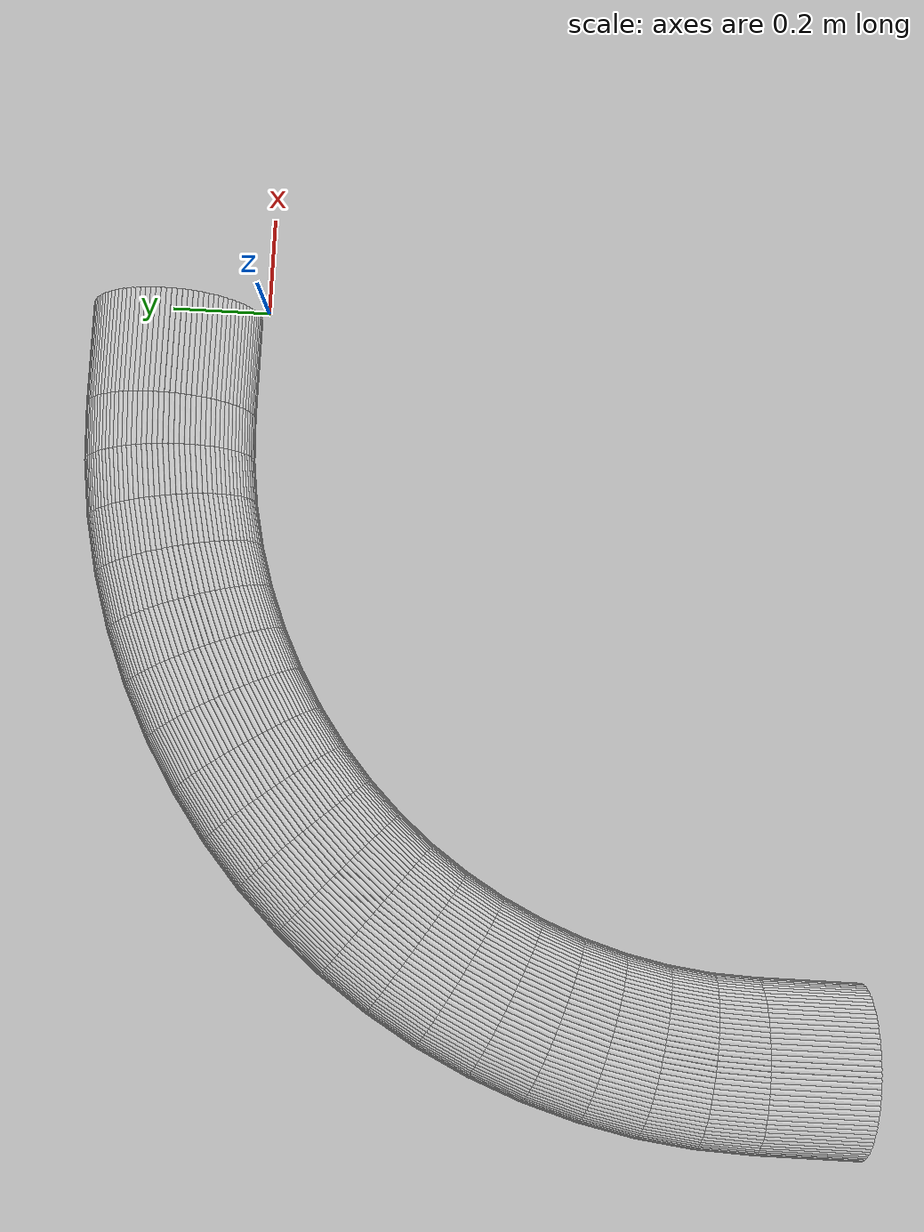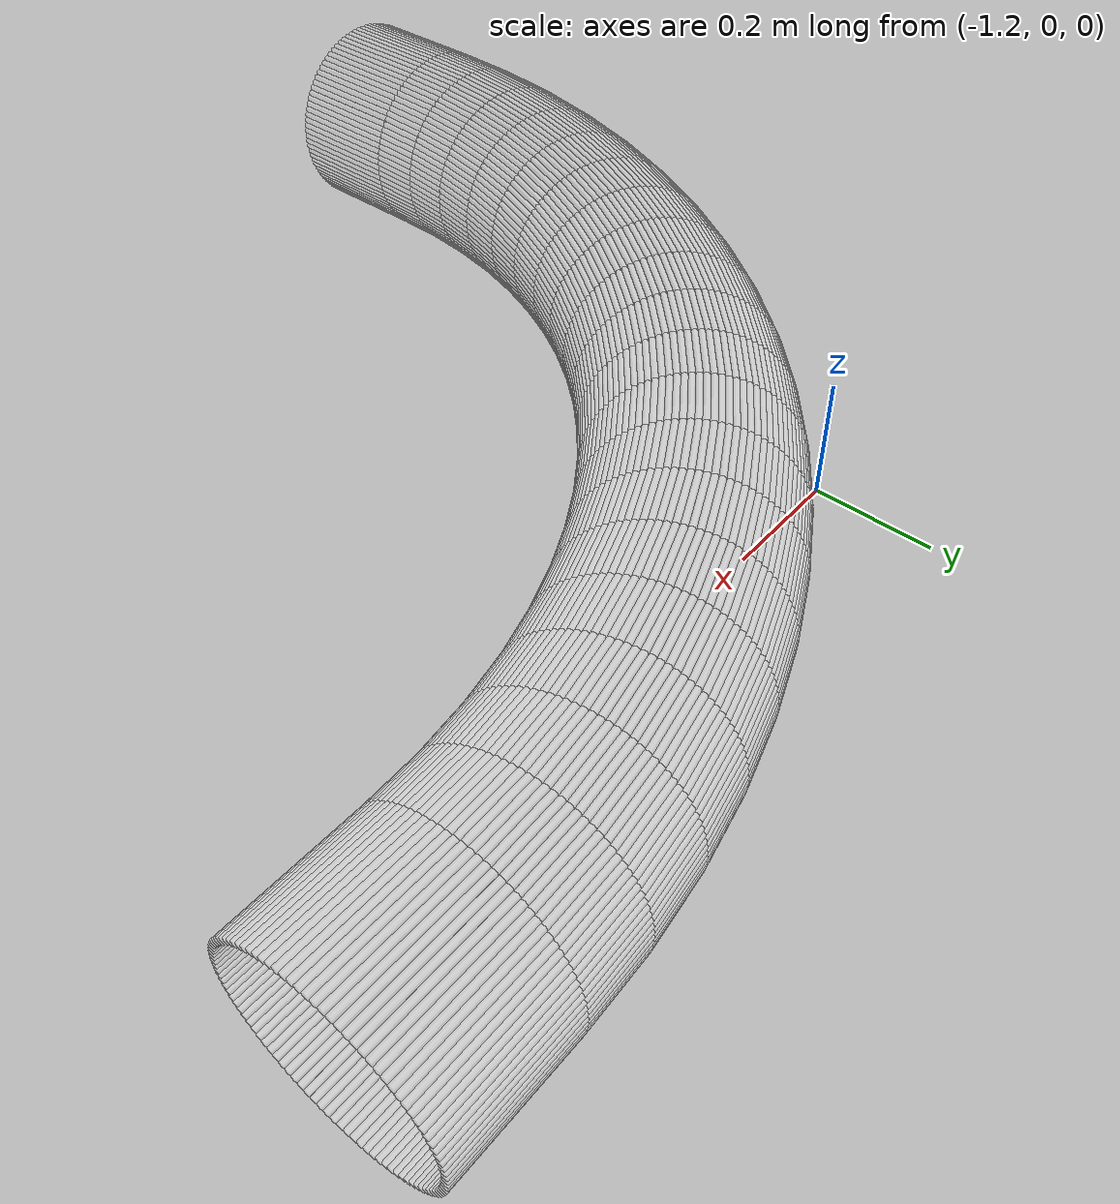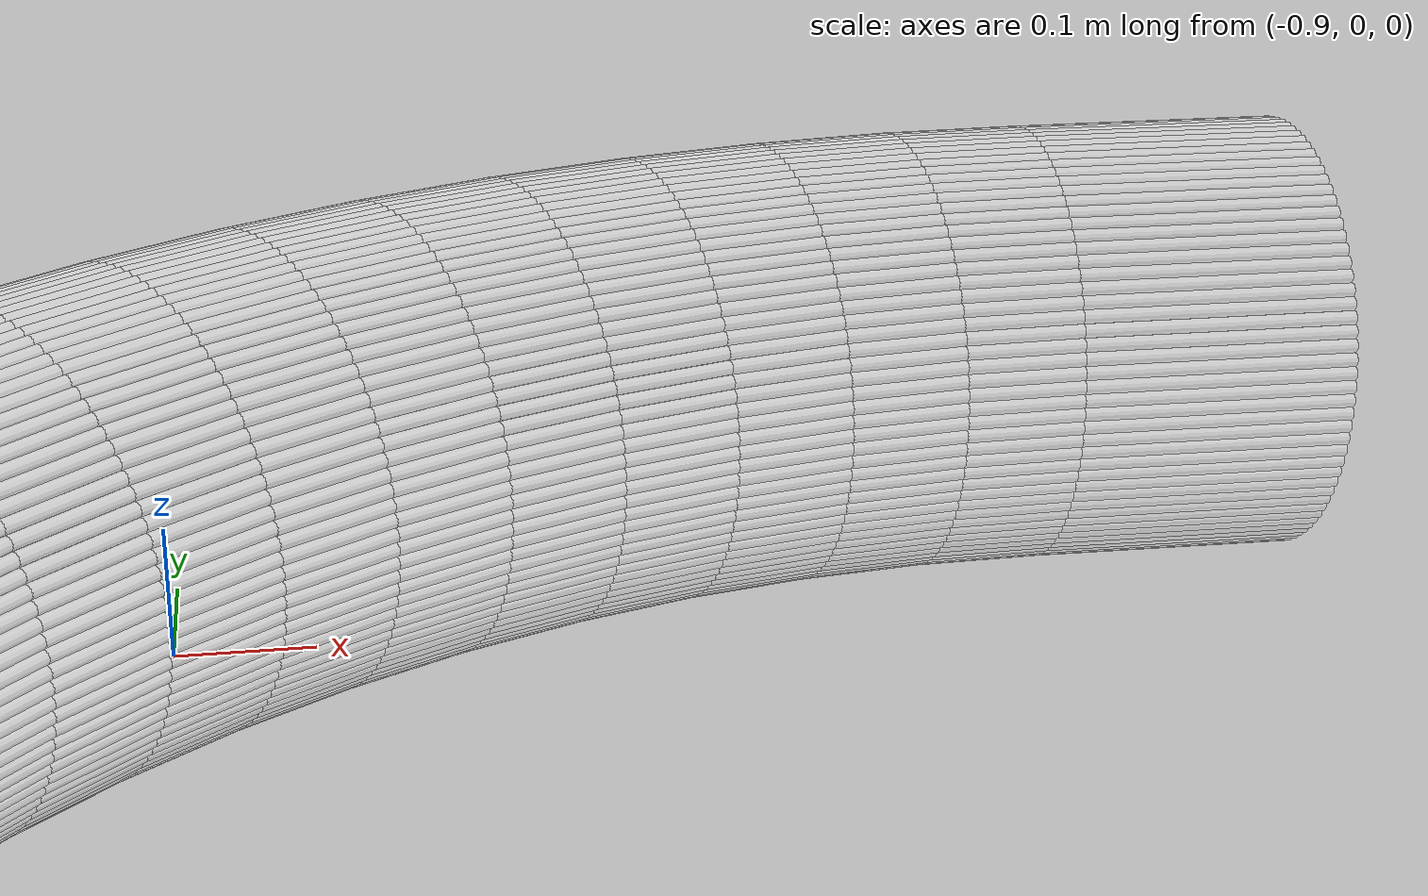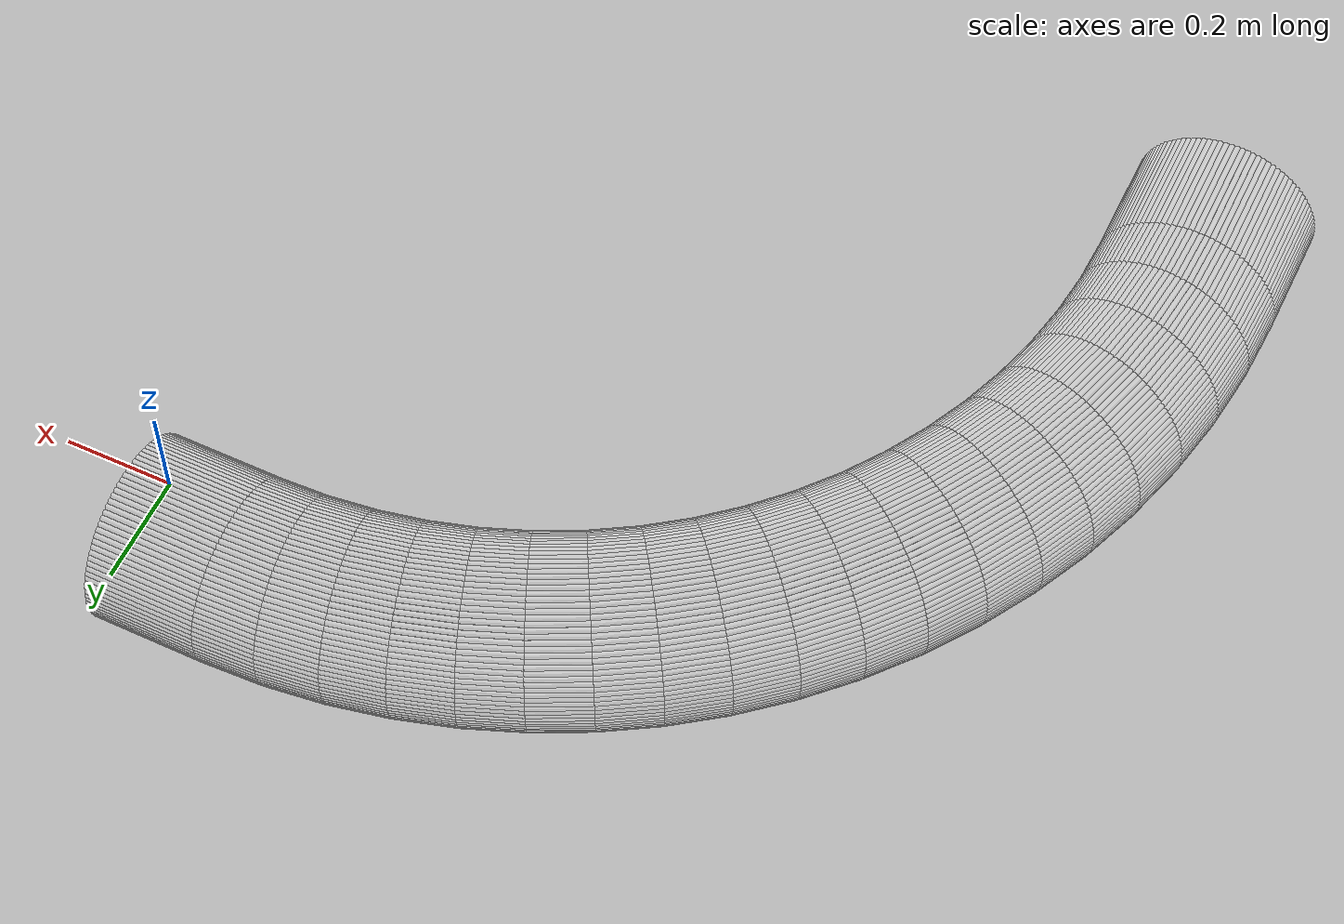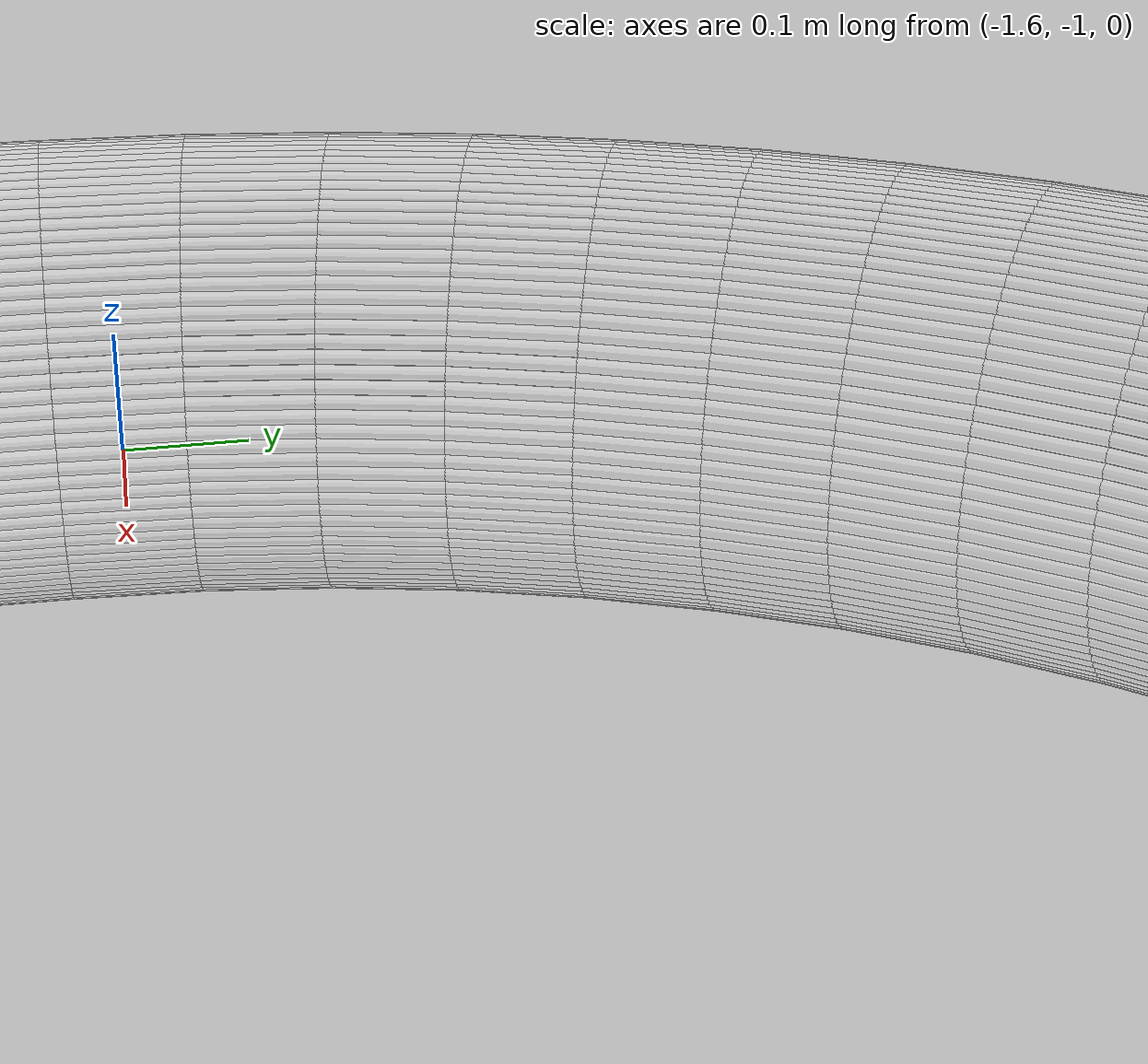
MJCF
<?xml version="1.0" encoding="utf-8"?>
<mujoco>
   <worldbody>
   <body pos="-0.25 -1.04 -0.02" euler="0 0 90">
      <geom euler=" 0 10 0 " fromto="1.36 -0.2 0.16 1.36 0 0.16" rgba="1 1 1 0.35"
            size="0.0050257"
            type="cylinder"/>
      <geom euler=" 0 20 0 " fromto="1.3597 -0.2 0.17005 1.3597 0 0.17005"
            rgba="1 1 1 0.35"
            size="0.0050257"
            type="cylinder"/>
      <geom euler=" 0 30 0 " fromto="1.3587 -0.2 0.18005 1.3587 0 0.18005"
            rgba="1 1 1 0.35"
            size="0.0050257"
            type="cylinder"/>
      <geom euler=" 0 40 0 " fromto="1.3572 -0.2 0.18998 1.3572 0 0.18998"
            rgba="1 1 1 0.35"
            size="0.0050257"
            type="cylinder"/>
      <geom euler=" 0 50 0 " fromto="1.355 -0.2 0.19979 1.355 0 0.19979" rgba="1 1 1 0.35"
            size="0.0050257"
            type="cylinder"/>
      <geom euler=" 0 60 0 " fromto="1.3522 -0.2 0.20944 1.3522 0 0.20944"
            rgba="1 1 1 0.35"
            size="0.0050257"
            type="cylinder"/>
      <geom euler=" 0 70 0 " fromto="1.3488 -0.2 0.2189 1.3488 0 0.2189" rgba="1 1 1 0.35"
            size="0.0050257"
            type="cylinder"/>
      <geom euler=" 0 80 0 " fromto="1.3448 -0.2 0.22812 1.3448 0 0.22812"
            rgba="1 1 1 0.35"
            size="0.0050257"
            type="cylinder"/>
      <geom euler=" 0 90 0 " fromto="1.3402 -0.2 0.23708 1.3402 0 0.23708"
            rgba="1 1 1 0.35"
            size="0.0050257"
            type="cylinder"/>
      <geom euler=" 0 100 0 " fromto="1.3351 -0.2 0.24573 1.3351 0 0.24573"
            rgba="1 1 1 0.35"
            size="0.0050257"
            type="cylinder"/>
      <geom euler=" 0 110 0 " fromto="1.3294 -0.2 0.25405 1.3294 0 0.25405"
            rgba="1 1 1 0.35"
            size="0.0050257"
            type="cylinder"/>
      <geom euler=" 0 120 0 " fromto="1.3233 -0.2 0.26199 1.3233 0 0.26199"
            rgba="1 1 1 0.35"
            size="0.0050257"
            type="cylinder"/>
      <geom euler=" 0 130 0 " fromto="1.3166 -0.2 0.26953 1.3166 0 0.26953"
            rgba="1 1 1 0.35"
            size="0.0050257"
            type="cylinder"/>
      <geom euler=" 0 140 0 " fromto="1.3095 -0.2 0.27663 1.3095 0 0.27663"
            rgba="1 1 1 0.35"
            size="0.0050257"
            type="cylinder"/>
      <geom euler=" 0 150 0 " fromto="1.302 -0.2 0.28328 1.302 0 0.28328" rgba="1 1 1 0.35"
            size="0.0050257"
            type="cylinder"/>
      <geom euler=" 0 160 0 " fromto="1.294 -0.2 0.28944 1.294 0 0.28944" rgba="1 1 1 0.35"
            size="0.0050257"
            type="cylinder"/>
      <geom euler=" 0 170 0 " fromto="1.2857 -0.2 0.29509 1.2857 0 0.29509"
            rgba="1 1 1 0.35"
            size="0.0050257"
            type="cylinder"/>
      <geom euler=" 0 180 0 " fromto="1.2771 -0.2 0.30021 1.2771 0 0.30021"
            rgba="1 1 1 0.35"
            size="0.0050257"
            type="cylinder"/>
      <geom euler=" 0 190 0 " fromto="1.2681 -0.2 0.30477 1.2681 0 0.30477"
            rgba="1 1 1 0.35"
            size="0.0050257"
            type="cylinder"/>
      <geom euler=" 0 200 0 " fromto="1.2589 -0.2 0.30876 1.2589 0 0.30876"
            rgba="1 1 1 0.35"
            size="0.0050257"
            type="cylinder"/>
      <geom euler=" 0 210 0 " fromto="1.2494 -0.2 0.31217 1.2494 0 0.31217"
            rgba="1 1 1 0.35"
            size="0.0050257"
            type="cylinder"/>
      <geom euler=" 0 220 0 " fromto="1.2398 -0.2 0.31497 1.2398 0 0.31497"
            rgba="1 1 1 0.35"
            size="0.0050257"
            type="cylinder"/>
      <geom euler=" 0 230 0 " fromto="1.23 -0.2 0.31717 1.23 0 0.31717" rgba="1 1 1 0.35"
            size="0.0050257"
            type="cylinder"/>
      <geom euler=" 0 240 0 " fromto="1.2201 -0.2 0.31874 1.2201 0 0.31874"
            rgba="1 1 1 0.35"
            size="0.0050257"
            type="cylinder"/>
      <geom euler=" 0 250 0 " fromto="1.21 -0.2 0.31968 1.21 0 0.31968" rgba="1 1 1 0.35"
            size="0.0050257"
            type="cylinder"/>
      <geom euler=" 0 260 0 " fromto="1.2 -0.2 0.32 1.2 0 0.32" rgba="1 1 1 0.35"
            size="0.0050257"
            type="cylinder"/>
      <geom euler=" 0 270 0 " fromto="1.19 -0.2 0.31968 1.19 0 0.31968" rgba="1 1 1 0.35"
            size="0.0050257"
            type="cylinder"/>
      <geom euler=" 0 280 0 " fromto="1.1799 -0.2 0.31874 1.1799 0 0.31874"
            rgba="1 1 1 0.35"
            size="0.0050257"
            type="cylinder"/>
      <geom euler=" 0 290 0 " fromto="1.17 -0.2 0.31717 1.17 0 0.31717" rgba="1 1 1 0.35"
            size="0.0050257"
            type="cylinder"/>
      <geom euler=" 0 300 0 " fromto="1.1602 -0.2 0.31497 1.1602 0 0.31497"
            rgba="1 1 1 0.35"
            size="0.0050257"
            type="cylinder"/>
      <geom euler=" 0 310 0 " fromto="1.1506 -0.2 0.31217 1.1506 0 0.31217"
            rgba="1 1 1 0.35"
            size="0.0050257"
            type="cylinder"/>
      <geom euler=" 0 320 0 " fromto="1.1411 -0.2 0.30876 1.1411 0 0.30876"
            rgba="1 1 1 0.35"
            size="0.0050257"
            type="cylinder"/>
      <geom euler=" 0 330 0 " fromto="1.1319 -0.2 0.30477 1.1319 0 0.30477"
            rgba="1 1 1 0.35"
            size="0.0050257"
            type="cylinder"/>
      <geom euler=" 0 340 0 " fromto="1.1229 -0.2 0.30021 1.1229 0 0.30021"
            rgba="1 1 1 0.35"
            size="0.0050257"
            type="cylinder"/>
      <geom euler=" 0 350 0 " fromto="1.1143 -0.2 0.29509 1.1143 0 0.29509"
            rgba="1 1 1 0.35"
            size="0.0050257"
            type="cylinder"/>
      <geom euler=" 0 360 0 " fromto="1.106 -0.2 0.28944 1.106 0 0.28944" rgba="1 1 1 0.35"
            size="0.0050257"
            type="cylinder"/>
      <geom euler=" 0 370 0 " fromto="1.098 -0.2 0.28328 1.098 0 0.28328" rgba="1 1 1 0.35"
            size="0.0050257"
            type="cylinder"/>
      <geom euler=" 0 380 0 " fromto="1.0905 -0.2 0.27663 1.0905 0 0.27663"
            rgba="1 1 1 0.35"
            size="0.0050257"
            type="cylinder"/>
      <geom euler=" 0 390 0 " fromto="1.0834 -0.2 0.26953 1.0834 0 0.26953"
            rgba="1 1 1 0.35"
            size="0.0050257"
            type="cylinder"/>
      <geom euler=" 0 400 0 " fromto="1.0767 -0.2 0.26199 1.0767 0 0.26199"
            rgba="1 1 1 0.35"
            size="0.0050257"
            type="cylinder"/>
      <geom euler=" 0 410 0 " fromto="1.0706 -0.2 0.25405 1.0706 0 0.25405"
            rgba="1 1 1 0.35"
            size="0.0050257"
            type="cylinder"/>
      <geom euler=" 0 420 0 " fromto="1.0649 -0.2 0.24573 1.0649 0 0.24573"
            rgba="1 1 1 0.35"
            size="0.0050257"
            type="cylinder"/>
      <geom euler=" 0 430 0 " fromto="1.0598 -0.2 0.23708 1.0598 0 0.23708"
            rgba="1 1 1 0.35"
            size="0.0050257"
            type="cylinder"/>
      <geom euler=" 0 440 0 " fromto="1.0552 -0.2 0.22812 1.0552 0 0.22812"
            rgba="1 1 1 0.35"
            size="0.0050257"
            type="cylinder"/>
      <geom euler=" 0 450 0 " fromto="1.0512 -0.2 0.2189 1.0512 0 0.2189" rgba="1 1 1 0.35"
            size="0.0050257"
            type="cylinder"/>
      <geom euler=" 0 460 0 " fromto="1.0478 -0.2 0.20944 1.0478 0 0.20944"
            rgba="1 1 1 0.35"
            size="0.0050257"
            type="cylinder"/>
      <geom euler=" 0 470 0 " fromto="1.045 -0.2 0.19979 1.045 0 0.19979" rgba="1 1 1 0.35"
            size="0.0050257"
            type="cylinder"/>
      <geom euler=" 0 480 0 " fromto="1.0428 -0.2 0.18998 1.0428 0 0.18998"
            rgba="1 1 1 0.35"
            size="0.0050257"
            type="cylinder"/>
      <geom euler=" 0 490 0 " fromto="1.0413 -0.2 0.18005 1.0413 0 0.18005"
            rgba="1 1 1 0.35"
            size="0.0050257"
            type="cylinder"/>
      <geom euler=" 0 500 0 " fromto="1.0403 -0.2 0.17005 1.0403 0 0.17005"
            rgba="1 1 1 0.35"
            size="0.0050257"
            type="cylinder"/>
      <geom euler=" 0 510 0 " fromto="1.04 -0.2 0.16 1.04 0 0.16" rgba="1 1 1 0.35"
            size="0.0050257"
            type="cylinder"/>
      <geom euler=" 0 520 0 " fromto="1.0403 -0.2 0.14995 1.0403 0 0.14995"
            rgba="1 1 1 0.35"
            size="0.0050257"
            type="cylinder"/>
      <geom euler=" 0 530 0 " fromto="1.0413 -0.2 0.13995 1.0413 0 0.13995"
            rgba="1 1 1 0.35"
            size="0.0050257"
            type="cylinder"/>
      <geom euler=" 0 540 0 " fromto="1.0428 -0.2 0.13002 1.0428 0 0.13002"
            rgba="1 1 1 0.35"
            size="0.0050257"
            type="cylinder"/>
      <geom euler=" 0 550 0 " fromto="1.045 -0.2 0.12021 1.045 0 0.12021" rgba="1 1 1 0.35"
            size="0.0050257"
            type="cylinder"/>
      <geom euler=" 0 560 0 " fromto="1.0478 -0.2 0.11056 1.0478 0 0.11056"
            rgba="1 1 1 0.35"
            size="0.0050257"
            type="cylinder"/>
      <geom euler=" 0 570 0 " fromto="1.0512 -0.2 0.1011 1.0512 0 0.1011" rgba="1 1 1 0.35"
            size="0.0050257"
            type="cylinder"/>
      <geom euler=" 0 580 0 " fromto="1.0552 -0.2 0.091875 1.0552 0 0.091875"
            rgba="1 1 1 0.35"
            size="0.0050257"
            type="cylinder"/>
      <geom euler=" 0 590 0 " fromto="1.0598 -0.2 0.082919 1.0598 0 0.082919"
            rgba="1 1 1 0.35"
            size="0.0050257"
            type="cylinder"/>
      <geom euler=" 0 600 0 " fromto="1.0649 -0.2 0.074268 1.0649 0 0.074268"
            rgba="1 1 1 0.35"
            size="0.0050257"
            type="cylinder"/>
      <geom euler=" 0 610 0 " fromto="1.0706 -0.2 0.065954 1.0706 0 0.065954"
            rgba="1 1 1 0.35"
            size="0.0050257"
            type="cylinder"/>
      <geom euler=" 0 620 0 " fromto="1.0767 -0.2 0.058012 1.0767 0 0.058012"
            rgba="1 1 1 0.35"
            size="0.0050257"
            type="cylinder"/>
      <geom euler=" 0 630 0 " fromto="1.0834 -0.2 0.050472 1.0834 0 0.050472"
            rgba="1 1 1 0.35"
            size="0.0050257"
            type="cylinder"/>
      <geom euler=" 0 640 0 " fromto="1.0905 -0.2 0.043365 1.0905 0 0.043365"
            rgba="1 1 1 0.35"
            size="0.0050257"
            type="cylinder"/>
      <geom euler=" 0 650 0 " fromto="1.098 -0.2 0.036718 1.098 0 0.036718"
            rgba="1 1 1 0.35"
            size="0.0050257"
            type="cylinder"/>
      <geom euler=" 0 660 0 " fromto="1.106 -0.2 0.030557 1.106 0 0.030557"
            rgba="1 1 1 0.35"
            size="0.0050257"
            type="cylinder"/>
      <geom euler=" 0 670 0 " fromto="1.1143 -0.2 0.024908 1.1143 0 0.024908"
            rgba="1 1 1 0.35"
            size="0.0050257"
            type="cylinder"/>
      <geom euler=" 0 680 0 " fromto="1.1229 -0.2 0.019791 1.1229 0 0.019791"
            rgba="1 1 1 0.35"
            size="0.0050257"
            type="cylinder"/>
      <geom euler=" 0 690 0 " fromto="1.1319 -0.2 0.015228 1.1319 0 0.015228"
            rgba="1 1 1 0.35"
            size="0.0050257"
            type="cylinder"/>
      <geom euler=" 0 700 0 " fromto="1.1411 -0.2 0.011236 1.1411 0 0.011236"
            rgba="1 1 1 0.35"
            size="0.0050257"
            type="cylinder"/>
      <geom euler=" 0 710 0 " fromto="1.1506 -0.2 0.007831 1.1506 0 0.007831"
            rgba="1 1 1 0.35"
            size="0.0050257"
            type="cylinder"/>
      <geom euler=" 0 720 0 " fromto="1.1602 -0.2 0.0050267 1.1602 0 0.0050267"
            rgba="1 1 1 0.35"
            size="0.0050257"
            type="cylinder"/>
      <geom euler=" 0 730 0 " fromto="1.17 -0.2 0.002834 1.17 0 0.002834" rgba="1 1 1 0.35"
            size="0.0050257"
            type="cylinder"/>
      <geom euler=" 0 740 0 " fromto="1.1799 -0.2 0.0012616 1.1799 0 0.0012616"
            rgba="1 1 1 0.35"
            size="0.0050257"
            type="cylinder"/>
      <geom euler=" 0 750 0 " fromto="1.19 -0.2 0.00031572 1.19 0 0.00031572"
            rgba="1 1 1 0.35"
            size="0.0050257"
            type="cylinder"/>
      <geom euler=" 0 760 0 " fromto="1.2 -0.2 0 1.2 0 0" rgba="1 1 1 0.35"
            size="0.0050257"
            type="cylinder"/>
      <geom euler=" 0 770 0 " fromto="1.21 -0.2 0.00031572 1.21 0 0.00031572"
            rgba="1 1 1 0.35"
            size="0.0050257"
            type="cylinder"/>
      <geom euler=" 0 780 0 " fromto="1.2201 -0.2 0.0012616 1.2201 0 0.0012616"
            rgba="1 1 1 0.35"
            size="0.0050257"
            type="cylinder"/>
      <geom euler=" 0 790 0 " fromto="1.23 -0.2 0.002834 1.23 0 0.002834" rgba="1 1 1 0.35"
            size="0.0050257"
            type="cylinder"/>
      <geom euler=" 0 800 0 " fromto="1.2398 -0.2 0.0050267 1.2398 0 0.0050267"
            rgba="1 1 1 0.35"
            size="0.0050257"
            type="cylinder"/>
      <geom euler=" 0 810 0 " fromto="1.2494 -0.2 0.007831 1.2494 0 0.007831"
            rgba="1 1 1 0.35"
            size="0.0050257"
            type="cylinder"/>
      <geom euler=" 0 820 0 " fromto="1.2589 -0.2 0.011236 1.2589 0 0.011236"
            rgba="1 1 1 0.35"
            size="0.0050257"
            type="cylinder"/>
      <geom euler=" 0 830 0 " fromto="1.2681 -0.2 0.015228 1.2681 0 0.015228"
            rgba="1 1 1 0.35"
            size="0.0050257"
            type="cylinder"/>
      <geom euler=" 0 840 0 " fromto="1.2771 -0.2 0.019791 1.2771 0 0.019791"
            rgba="1 1 1 0.35"
            size="0.0050257"
            type="cylinder"/>
      <geom euler=" 0 850 0 " fromto="1.2857 -0.2 0.024908 1.2857 0 0.024908"
            rgba="1 1 1 0.35"
            size="0.0050257"
            type="cylinder"/>
      <geom euler=" 0 860 0 " fromto="1.294 -0.2 0.030557 1.294 0 0.030557"
            rgba="1 1 1 0.35"
            size="0.0050257"
            type="cylinder"/>
      <geom euler=" 0 870 0 " fromto="1.302 -0.2 0.036718 1.302 0 0.036718"
            rgba="1 1 1 0.35"
            size="0.0050257"
            type="cylinder"/>
      <geom euler=" 0 880 0 " fromto="1.3095 -0.2 0.043365 1.3095 0 0.043365"
            rgba="1 1 1 0.35"
            size="0.0050257"
            type="cylinder"/>
      <geom euler=" 0 890 0 " fromto="1.3166 -0.2 0.050472 1.3166 0 0.050472"
            rgba="1 1 1 0.35"
            size="0.0050257"
            type="cylinder"/>
      <geom euler=" 0 900 0 " fromto="1.3233 -0.2 0.058012 1.3233 0 0.058012"
            rgba="1 1 1 0.35"
            size="0.0050257"
            type="cylinder"/>
      <geom euler=" 0 910 0 " fromto="1.3294 -0.2 0.065954 1.3294 0 0.065954"
            rgba="1 1 1 0.35"
            size="0.0050257"
            type="cylinder"/>
      <geom euler=" 0 920 0 " fromto="1.3351 -0.2 0.074268 1.3351 0 0.074268"
            rgba="1 1 1 0.35"
            size="0.0050257"
            type="cylinder"/>
      <geom euler=" 0 930 0 " fromto="1.3402 -0.2 0.082919 1.3402 0 0.082919"
            rgba="1 1 1 0.35"
            size="0.0050257"
            type="cylinder"/>
      <geom euler=" 0 940 0 " fromto="1.3448 -0.2 0.091875 1.3448 0 0.091875"
            rgba="1 1 1 0.35"
            size="0.0050257"
            type="cylinder"/>
      <geom euler=" 0 950 0 " fromto="1.3488 -0.2 0.1011 1.3488 0 0.1011" rgba="1 1 1 0.35"
            size="0.0050257"
            type="cylinder"/>
      <geom euler=" 0 960 0 " fromto="1.3522 -0.2 0.11056 1.3522 0 0.11056"
            rgba="1 1 1 0.35"
            size="0.0050257"
            type="cylinder"/>
      <geom euler=" 0 970 0 " fromto="1.355 -0.2 0.12021 1.355 0 0.12021" rgba="1 1 1 0.35"
            size="0.0050257"
            type="cylinder"/>
      <geom euler=" 0 980 0 " fromto="1.3572 -0.2 0.13002 1.3572 0 0.13002"
            rgba="1 1 1 0.35"
            size="0.0050257"
            type="cylinder"/>
      <geom euler=" 0 990 0 " fromto="1.3587 -0.2 0.13995 1.3587 0 0.13995"
            rgba="1 1 1 0.35"
            size="0.0050257"
            type="cylinder"/>
      <geom euler=" 0 1000 0 " fromto="1.3597 -0.2 0.14995 1.3597 0 0.14995"
            rgba="1 1 1 0.35"
            size="0.0050257"
            type="cylinder"/>
      <geom euler=" 0 10 0 " fromto="1.36 0 0.16 1.3554 0.11231 0.16" rgba="1 1 1 0.35"
            size="0.0050257"
            type="cylinder"/>
      <geom euler=" 0 20 0 " fromto="1.3597 0 0.17005 1.355 0.11228 0.17005"
            rgba="1 1 1 0.35"
            size="0.0050257"
            type="cylinder"/>
      <geom euler=" 0 30 0 " fromto="1.3587 0 0.18005 1.3541 0.1122 0.18005"
            rgba="1 1 1 0.35"
            size="0.0050257"
            type="cylinder"/>
      <geom euler=" 0 40 0 " fromto="1.3572 0 0.18998 1.3525 0.11207 0.18998"
            rgba="1 1 1 0.35"
            size="0.0050257"
            type="cylinder"/>
      <geom euler=" 0 50 0 " fromto="1.355 0 0.19979 1.3503 0.11189 0.19979"
            rgba="1 1 1 0.35"
            size="0.0050257"
            type="cylinder"/>
      <geom euler=" 0 60 0 " fromto="1.3522 0 0.20944 1.3476 0.11166 0.20944"
            rgba="1 1 1 0.35"
            size="0.0050257"
            type="cylinder"/>
      <geom euler=" 0 70 0 " fromto="1.3488 0 0.2189 1.3442 0.11138 0.2189"
            rgba="1 1 1 0.35"
            size="0.0050257"
            type="cylinder"/>
      <geom euler=" 0 80 0 " fromto="1.3448 0 0.22812 1.3402 0.11105 0.22812"
            rgba="1 1 1 0.35"
            size="0.0050257"
            type="cylinder"/>
      <geom euler=" 0 90 0 " fromto="1.3402 0 0.23708 1.3356 0.11067 0.23708"
            rgba="1 1 1 0.35"
            size="0.0050257"
            type="cylinder"/>
      <geom euler=" 0 100 0 " fromto="1.3351 0 0.24573 1.3305 0.11025 0.24573"
            rgba="1 1 1 0.35"
            size="0.0050257"
            type="cylinder"/>
      <geom euler=" 0 110 0 " fromto="1.3294 0 0.25405 1.3249 0.10978 0.25405"
            rgba="1 1 1 0.35"
            size="0.0050257"
            type="cylinder"/>
      <geom euler=" 0 120 0 " fromto="1.3233 0 0.26199 1.3188 0.10928 0.26199"
            rgba="1 1 1 0.35"
            size="0.0050257"
            type="cylinder"/>
      <geom euler=" 0 130 0 " fromto="1.3166 0 0.26953 1.3121 0.10873 0.26953"
            rgba="1 1 1 0.35"
            size="0.0050257"
            type="cylinder"/>
      <geom euler=" 0 140 0 " fromto="1.3095 0 0.27663 1.3051 0.10814 0.27663"
            rgba="1 1 1 0.35"
            size="0.0050257"
            type="cylinder"/>
      <geom euler=" 0 150 0 " fromto="1.302 0 0.28328 1.2975 0.10752 0.28328"
            rgba="1 1 1 0.35"
            size="0.0050257"
            type="cylinder"/>
      <geom euler=" 0 160 0 " fromto="1.294 0 0.28944 1.2896 0.10686 0.28944"
            rgba="1 1 1 0.35"
            size="0.0050257"
            type="cylinder"/>
      <geom euler=" 0 170 0 " fromto="1.2857 0 0.29509 1.2813 0.10617 0.29509"
            rgba="1 1 1 0.35"
            size="0.0050257"
            type="cylinder"/>
      <geom euler=" 0 180 0 " fromto="1.2771 0 0.30021 1.2727 0.10546 0.30021"
            rgba="1 1 1 0.35"
            size="0.0050257"
            type="cylinder"/>
      <geom euler=" 0 190 0 " fromto="1.2681 0 0.30477 1.2638 0.10472 0.30477"
            rgba="1 1 1 0.35"
            size="0.0050257"
            type="cylinder"/>
      <geom euler=" 0 200 0 " fromto="1.2589 0 0.30876 1.2546 0.10396 0.30876"
            rgba="1 1 1 0.35"
            size="0.0050257"
            type="cylinder"/>
      <geom euler=" 0 210 0 " fromto="1.2494 0 0.31217 1.2452 0.10318 0.31217"
            rgba="1 1 1 0.35"
            size="0.0050257"
            type="cylinder"/>
      <geom euler=" 0 220 0 " fromto="1.2398 0 0.31497 1.2356 0.10238 0.31497"
            rgba="1 1 1 0.35"
            size="0.0050257"
            type="cylinder"/>
      <geom euler=" 0 230 0 " fromto="1.23 0 0.31717 1.2258 0.10157 0.31717"
            rgba="1 1 1 0.35"
            size="0.0050257"
            type="cylinder"/>
      <geom euler=" 0 240 0 " fromto="1.2201 0 0.31874 1.2159 0.10075 0.31874"
            rgba="1 1 1 0.35"
            size="0.0050257"
            type="cylinder"/>
      <geom euler=" 0 250 0 " fromto="1.21 0 0.31968 1.2059 0.099925 0.31968"
            rgba="1 1 1 0.35"
            size="0.0050257"
            type="cylinder"/>
      <geom euler=" 0 260 0 " fromto="1.2 0 0.32 1.1959 0.099095 0.32" rgba="1 1 1 0.35"
            size="0.0050257"
            type="cylinder"/>
      <geom euler=" 0 270 0 " fromto="1.19 0 0.31968 1.1859 0.098266 0.31968"
            rgba="1 1 1 0.35"
            size="0.0050257"
            type="cylinder"/>
      <geom euler=" 0 280 0 " fromto="1.1799 0 0.31874 1.1759 0.097439 0.31874"
            rgba="1 1 1 0.35"
            size="0.0050257"
            type="cylinder"/>
      <geom euler=" 0 290 0 " fromto="1.17 0 0.31717 1.166 0.096619 0.31717"
            rgba="1 1 1 0.35"
            size="0.0050257"
            type="cylinder"/>
      <geom euler=" 0 300 0 " fromto="1.1602 0 0.31497 1.1562 0.095809 0.31497"
            rgba="1 1 1 0.35"
            size="0.0050257"
            type="cylinder"/>
      <geom euler=" 0 310 0 " fromto="1.1506 0 0.31217 1.1466 0.095012 0.31217"
            rgba="1 1 1 0.35"
            size="0.0050257"
            type="cylinder"/>
      <geom euler=" 0 320 0 " fromto="1.1411 0 0.30876 1.1372 0.094231 0.30876"
            rgba="1 1 1 0.35"
            size="0.0050257"
            type="cylinder"/>
      <geom euler=" 0 330 0 " fromto="1.1319 0 0.30477 1.128 0.09347 0.30477"
            rgba="1 1 1 0.35"
            size="0.0050257"
            type="cylinder"/>
      <geom euler=" 0 340 0 " fromto="1.1229 0 0.30021 1.1191 0.09273 0.30021"
            rgba="1 1 1 0.35"
            size="0.0050257"
            type="cylinder"/>
      <geom euler=" 0 350 0 " fromto="1.1143 0 0.29509 1.1105 0.092015 0.29509"
            rgba="1 1 1 0.35"
            size="0.0050257"
            type="cylinder"/>
      <geom euler=" 0 360 0 " fromto="1.106 0 0.28944 1.1022 0.091329 0.28944"
            rgba="1 1 1 0.35"
            size="0.0050257"
            type="cylinder"/>
      <geom euler=" 0 370 0 " fromto="1.098 0 0.28328 1.0943 0.090673 0.28328"
            rgba="1 1 1 0.35"
            size="0.0050257"
            type="cylinder"/>
      <geom euler=" 0 380 0 " fromto="1.0905 0 0.27663 1.0867 0.090051 0.27663"
            rgba="1 1 1 0.35"
            size="0.0050257"
            type="cylinder"/>
      <geom euler=" 0 390 0 " fromto="1.0834 0 0.26953 1.0797 0.089464 0.26953"
            rgba="1 1 1 0.35"
            size="0.0050257"
            type="cylinder"/>
      <geom euler=" 0 400 0 " fromto="1.0767 0 0.26199 1.073 0.088915 0.26199"
            rgba="1 1 1 0.35"
            size="0.0050257"
            type="cylinder"/>
      <geom euler=" 0 410 0 " fromto="1.0706 0 0.25405 1.0669 0.088406 0.25405"
            rgba="1 1 1 0.35"
            size="0.0050257"
            type="cylinder"/>
      <geom euler=" 0 420 0 " fromto="1.0649 0 0.24573 1.0613 0.087939 0.24573"
            rgba="1 1 1 0.35"
            size="0.0050257"
            type="cylinder"/>
      <geom euler=" 0 430 0 " fromto="1.0598 0 0.23708 1.0562 0.087517 0.23708"
            rgba="1 1 1 0.35"
            size="0.0050257"
            type="cylinder"/>
      <geom euler=" 0 440 0 " fromto="1.0552 0 0.22812 1.0516 0.08714 0.22812"
            rgba="1 1 1 0.35"
            size="0.0050257"
            type="cylinder"/>
      <geom euler=" 0 450 0 " fromto="1.0512 0 0.2189 1.0476 0.08681 0.2189"
            rgba="1 1 1 0.35"
            size="0.0050257"
            type="cylinder"/>
      <geom euler=" 0 460 0 " fromto="1.0478 0 0.20944 1.0443 0.086529 0.20944"
            rgba="1 1 1 0.35"
            size="0.0050257"
            type="cylinder"/>
      <geom euler=" 0 470 0 " fromto="1.045 0 0.19979 1.0415 0.086298 0.19979"
            rgba="1 1 1 0.35"
            size="0.0050257"
            type="cylinder"/>
      <geom euler=" 0 480 0 " fromto="1.0428 0 0.18998 1.0393 0.086117 0.18998"
            rgba="1 1 1 0.35"
            size="0.0050257"
            type="cylinder"/>
      <geom euler=" 0 490 0 " fromto="1.0413 0 0.18005 1.0377 0.085987 0.18005"
            rgba="1 1 1 0.35"
            size="0.0050257"
            type="cylinder"/>
      <geom euler=" 0 500 0 " fromto="1.0403 0 0.17005 1.0368 0.085909 0.17005"
            rgba="1 1 1 0.35"
            size="0.0050257"
            type="cylinder"/>
      <geom euler=" 0 510 0 " fromto="1.04 0 0.16 1.0364 0.085883 0.16" rgba="1 1 1 0.35"
            size="0.0050257"
            type="cylinder"/>
      <geom euler=" 0 520 0 " fromto="1.0403 0 0.14995 1.0368 0.085909 0.14995"
            rgba="1 1 1 0.35"
            size="0.0050257"
            type="cylinder"/>
      <geom euler=" 0 530 0 " fromto="1.0413 0 0.13995 1.0377 0.085987 0.13995"
            rgba="1 1 1 0.35"
            size="0.0050257"
            type="cylinder"/>
      <geom euler=" 0 540 0 " fromto="1.0428 0 0.13002 1.0393 0.086117 0.13002"
            rgba="1 1 1 0.35"
            size="0.0050257"
            type="cylinder"/>
      <geom euler=" 0 550 0 " fromto="1.045 0 0.12021 1.0415 0.086298 0.12021"
            rgba="1 1 1 0.35"
            size="0.0050257"
            type="cylinder"/>
      <geom euler=" 0 560 0 " fromto="1.0478 0 0.11056 1.0443 0.086529 0.11056"
            rgba="1 1 1 0.35"
            size="0.0050257"
            type="cylinder"/>
      <geom euler=" 0 570 0 " fromto="1.0512 0 0.1011 1.0476 0.08681 0.1011"
            rgba="1 1 1 0.35"
            size="0.0050257"
            type="cylinder"/>
      <geom euler=" 0 580 0 " fromto="1.0552 0 0.091875 1.0516 0.08714 0.091875"
            rgba="1 1 1 0.35"
            size="0.0050257"
            type="cylinder"/>
      <geom euler=" 0 590 0 " fromto="1.0598 0 0.082919 1.0562 0.087517 0.082919"
            rgba="1 1 1 0.35"
            size="0.0050257"
            type="cylinder"/>
      <geom euler=" 0 600 0 " fromto="1.0649 0 0.074268 1.0613 0.087939 0.074268"
            rgba="1 1 1 0.35"
            size="0.0050257"
            type="cylinder"/>
      <geom euler=" 0 610 0 " fromto="1.0706 0 0.065954 1.0669 0.088406 0.065954"
            rgba="1 1 1 0.35"
            size="0.0050257"
            type="cylinder"/>
      <geom euler=" 0 620 0 " fromto="1.0767 0 0.058012 1.073 0.088915 0.058012"
            rgba="1 1 1 0.35"
            size="0.0050257"
            type="cylinder"/>
      <geom euler=" 0 630 0 " fromto="1.0834 0 0.050472 1.0797 0.089464 0.050472"
            rgba="1 1 1 0.35"
            size="0.0050257"
            type="cylinder"/>
      <geom euler=" 0 640 0 " fromto="1.0905 0 0.043365 1.0867 0.090051 0.043365"
            rgba="1 1 1 0.35"
            size="0.0050257"
            type="cylinder"/>
      <geom euler=" 0 650 0 " fromto="1.098 0 0.036718 1.0943 0.090673 0.036718"
            rgba="1 1 1 0.35"
            size="0.0050257"
            type="cylinder"/>
      <geom euler=" 0 660 0 " fromto="1.106 0 0.030557 1.1022 0.091329 0.030557"
            rgba="1 1 1 0.35"
            size="0.0050257"
            type="cylinder"/>
      <geom euler=" 0 670 0 " fromto="1.1143 0 0.024908 1.1105 0.092015 0.024908"
            rgba="1 1 1 0.35"
            size="0.0050257"
            type="cylinder"/>
      <geom euler=" 0 680 0 " fromto="1.1229 0 0.019791 1.1191 0.09273 0.019791"
            rgba="1 1 1 0.35"
            size="0.0050257"
            type="cylinder"/>
      <geom euler=" 0 690 0 " fromto="1.1319 0 0.015228 1.128 0.09347 0.015228"
            rgba="1 1 1 0.35"
            size="0.0050257"
            type="cylinder"/>
      <geom euler=" 0 700 0 " fromto="1.1411 0 0.011236 1.1372 0.094231 0.011236"
            rgba="1 1 1 0.35"
            size="0.0050257"
            type="cylinder"/>
      <geom euler=" 0 710 0 " fromto="1.1506 0 0.007831 1.1466 0.095012 0.007831"
            rgba="1 1 1 0.35"
            size="0.0050257"
            type="cylinder"/>
      <geom euler=" 0 720 0 " fromto="1.1602 0 0.0050267 1.1562 0.095809 0.0050267"
            rgba="1 1 1 0.35"
            size="0.0050257"
            type="cylinder"/>
      <geom euler=" 0 730 0 " fromto="1.17 0 0.002834 1.166 0.096619 0.002834"
            rgba="1 1 1 0.35"
            size="0.0050257"
            type="cylinder"/>
      <geom euler=" 0 740 0 " fromto="1.1799 0 0.0012616 1.1759 0.097439 0.0012616"
            rgba="1 1 1 0.35"
            size="0.0050257"
            type="cylinder"/>
      <geom euler=" 0 750 0 " fromto="1.19 0 0.00031572 1.1859 0.098266 0.00031572"
            rgba="1 1 1 0.35"
            size="0.0050257"
            type="cylinder"/>
      <geom euler=" 0 760 0 " fromto="1.2 0 0 1.1959 0.099095 0" rgba="1 1 1 0.35"
            size="0.0050257"
            type="cylinder"/>
      <geom euler=" 0 770 0 " fromto="1.21 0 0.00031572 1.2059 0.099925 0.00031572"
            rgba="1 1 1 0.35"
            size="0.0050257"
            type="cylinder"/>
      <geom euler=" 0 780 0 " fromto="1.2201 0 0.0012616 1.2159 0.10075 0.0012616"
            rgba="1 1 1 0.35"
            size="0.0050257"
            type="cylinder"/>
      <geom euler=" 0 790 0 " fromto="1.23 0 0.002834 1.2258 0.10157 0.002834"
            rgba="1 1 1 0.35"
            size="0.0050257"
            type="cylinder"/>
      <geom euler=" 0 800 0 " fromto="1.2398 0 0.0050267 1.2356 0.10238 0.0050267"
            rgba="1 1 1 0.35"
            size="0.0050257"
            type="cylinder"/>
      <geom euler=" 0 810 0 " fromto="1.2494 0 0.007831 1.2452 0.10318 0.007831"
            rgba="1 1 1 0.35"
            size="0.0050257"
            type="cylinder"/>
      <geom euler=" 0 820 0 " fromto="1.2589 0 0.011236 1.2546 0.10396 0.011236"
            rgba="1 1 1 0.35"
            size="0.0050257"
            type="cylinder"/>
      <geom euler=" 0 830 0 " fromto="1.2681 0 0.015228 1.2638 0.10472 0.015228"
            rgba="1 1 1 0.35"
            size="0.0050257"
            type="cylinder"/>
      <geom euler=" 0 840 0 " fromto="1.2771 0 0.019791 1.2727 0.10546 0.019791"
            rgba="1 1 1 0.35"
            size="0.0050257"
            type="cylinder"/>
      <geom euler=" 0 850 0 " fromto="1.2857 0 0.024908 1.2813 0.10617 0.024908"
            rgba="1 1 1 0.35"
            size="0.0050257"
            type="cylinder"/>
      <geom euler=" 0 860 0 " fromto="1.294 0 0.030557 1.2896 0.10686 0.030557"
            rgba="1 1 1 0.35"
            size="0.0050257"
            type="cylinder"/>
      <geom euler=" 0 870 0 " fromto="1.302 0 0.036718 1.2975 0.10752 0.036718"
            rgba="1 1 1 0.35"
            size="0.0050257"
            type="cylinder"/>
      <geom euler=" 0 880 0 " fromto="1.3095 0 0.043365 1.3051 0.10814 0.043365"
            rgba="1 1 1 0.35"
            size="0.0050257"
            type="cylinder"/>
      <geom euler=" 0 890 0 " fromto="1.3166 0 0.050472 1.3121 0.10873 0.050472"
            rgba="1 1 1 0.35"
            size="0.0050257"
            type="cylinder"/>
      <geom euler=" 0 900 0 " fromto="1.3233 0 0.058012 1.3188 0.10928 0.058012"
            rgba="1 1 1 0.35"
            size="0.0050257"
            type="cylinder"/>
      <geom euler=" 0 910 0 " fromto="1.3294 0 0.065954 1.3249 0.10978 0.065954"
            rgba="1 1 1 0.35"
            size="0.0050257"
            type="cylinder"/>
      <geom euler=" 0 920 0 " fromto="1.3351 0 0.074268 1.3305 0.11025 0.074268"
            rgba="1 1 1 0.35"
            size="0.0050257"
            type="cylinder"/>
      <geom euler=" 0 930 0 " fromto="1.3402 0 0.082919 1.3356 0.11067 0.082919"
            rgba="1 1 1 0.35"
            size="0.0050257"
            type="cylinder"/>
      <geom euler=" 0 940 0 " fromto="1.3448 0 0.091875 1.3402 0.11105 0.091875"
            rgba="1 1 1 0.35"
            size="0.0050257"
            type="cylinder"/>
      <geom euler=" 0 950 0 " fromto="1.3488 0 0.1011 1.3442 0.11138 0.1011"
            rgba="1 1 1 0.35"
            size="0.0050257"
            type="cylinder"/>
      <geom euler=" 0 960 0 " fromto="1.3522 0 0.11056 1.3476 0.11166 0.11056"
            rgba="1 1 1 0.35"
            size="0.0050257"
            type="cylinder"/>
      <geom euler=" 0 970 0 " fromto="1.355 0 0.12021 1.3503 0.11189 0.12021"
            rgba="1 1 1 0.35"
            size="0.0050257"
            type="cylinder"/>
      <geom euler=" 0 980 0 " fromto="1.3572 0 0.13002 1.3525 0.11207 0.13002"
            rgba="1 1 1 0.35"
            size="0.0050257"
            type="cylinder"/>
      <geom euler=" 0 990 0 " fromto="1.3587 0 0.13995 1.3541 0.1122 0.13995"
            rgba="1 1 1 0.35"
            size="0.0050257"
            type="cylinder"/>
      <geom euler=" 0 1000 0 " fromto="1.3597 0 0.14995 1.355 0.11228 0.14995"
            rgba="1 1 1 0.35"
            size="0.0050257"
            type="cylinder"/>
      <geom euler=" 0 10 0 " fromto="1.3554 0.11231 0.16 1.3415 0.22385 0.16"
            rgba="1 1 1 0.35"
            size="0.0050257"
            type="cylinder"/>
      <geom euler=" 0 20 0 " fromto="1.355 0.11228 0.17005 1.3411 0.2238 0.17005"
            rgba="1 1 1 0.35"
            size="0.0050257"
            type="cylinder"/>
      <geom euler=" 0 30 0 " fromto="1.3541 0.1122 0.18005 1.3402 0.22364 0.18005"
            rgba="1 1 1 0.35"
            size="0.0050257"
            type="cylinder"/>
      <geom euler=" 0 40 0 " fromto="1.3525 0.11207 0.18998 1.3387 0.22338 0.18998"
            rgba="1 1 1 0.35"
            size="0.0050257"
            type="cylinder"/>
      <geom euler=" 0 50 0 " fromto="1.3503 0.11189 0.19979 1.3365 0.22302 0.19979"
            rgba="1 1 1 0.35"
            size="0.0050257"
            type="cylinder"/>
      <geom euler=" 0 60 0 " fromto="1.3476 0.11166 0.20944 1.3337 0.22256 0.20944"
            rgba="1 1 1 0.35"
            size="0.0050257"
            type="cylinder"/>
      <geom euler=" 0 70 0 " fromto="1.3442 0.11138 0.2189 1.3304 0.222 0.2189"
            rgba="1 1 1 0.35"
            size="0.0050257"
            type="cylinder"/>
      <geom euler=" 0 80 0 " fromto="1.3402 0.11105 0.22812 1.3264 0.22134 0.22812"
            rgba="1 1 1 0.35"
            size="0.0050257"
            type="cylinder"/>
      <geom euler=" 0 90 0 " fromto="1.3356 0.11067 0.23708 1.3219 0.22059 0.23708"
            rgba="1 1 1 0.35"
            size="0.0050257"
            type="cylinder"/>
      <geom euler=" 0 100 0 " fromto="1.3305 0.11025 0.24573 1.3169 0.21975 0.24573"
            rgba="1 1 1 0.35"
            size="0.0050257"
            type="cylinder"/>
      <geom euler=" 0 110 0 " fromto="1.3249 0.10978 0.25405 1.3113 0.21882 0.25405"
            rgba="1 1 1 0.35"
            size="0.0050257"
            type="cylinder"/>
      <geom euler=" 0 120 0 " fromto="1.3188 0.10928 0.26199 1.3052 0.21781 0.26199"
            rgba="1 1 1 0.35"
            size="0.0050257"
            type="cylinder"/>
      <geom euler=" 0 130 0 " fromto="1.3121 0.10873 0.26953 1.2987 0.21671 0.26953"
            rgba="1 1 1 0.35"
            size="0.0050257"
            type="cylinder"/>
      <geom euler=" 0 140 0 " fromto="1.3051 0.10814 0.27663 1.2917 0.21554 0.27663"
            rgba="1 1 1 0.35"
            size="0.0050257"
            type="cylinder"/>
      <geom euler=" 0 150 0 " fromto="1.2975 0.10752 0.28328 1.2842 0.2143 0.28328"
            rgba="1 1 1 0.35"
            size="0.0050257"
            type="cylinder"/>
      <geom euler=" 0 160 0 " fromto="1.2896 0.10686 0.28944 1.2764 0.21299 0.28944"
            rgba="1 1 1 0.35"
            size="0.0050257"
            type="cylinder"/>
      <geom euler=" 0 170 0 " fromto="1.2813 0.10617 0.29509 1.2682 0.21162 0.29509"
            rgba="1 1 1 0.35"
            size="0.0050257"
            type="cylinder"/>
      <geom euler=" 0 180 0 " fromto="1.2727 0.10546 0.30021 1.2597 0.2102 0.30021"
            rgba="1 1 1 0.35"
            size="0.0050257"
            type="cylinder"/>
      <geom euler=" 0 190 0 " fromto="1.2638 0.10472 0.30477 1.2508 0.20873 0.30477"
            rgba="1 1 1 0.35"
            size="0.0050257"
            type="cylinder"/>
      <geom euler=" 0 200 0 " fromto="1.2546 0.10396 0.30876 1.2417 0.20721 0.30876"
            rgba="1 1 1 0.35"
            size="0.0050257"
            type="cylinder"/>
      <geom euler=" 0 210 0 " fromto="1.2452 0.10318 0.31217 1.2324 0.20565 0.31217"
            rgba="1 1 1 0.35"
            size="0.0050257"
            type="cylinder"/>
      <geom euler=" 0 220 0 " fromto="1.2356 0.10238 0.31497 1.2229 0.20406 0.31497"
            rgba="1 1 1 0.35"
            size="0.0050257"
            type="cylinder"/>
      <geom euler=" 0 230 0 " fromto="1.2258 0.10157 0.31717 1.2132 0.20245 0.31717"
            rgba="1 1 1 0.35"
            size="0.0050257"
            type="cylinder"/>
      <geom euler=" 0 240 0 " fromto="1.2159 0.10075 0.31874 1.2034 0.20081 0.31874"
            rgba="1 1 1 0.35"
            size="0.0050257"
            type="cylinder"/>
      <geom euler=" 0 250 0 " fromto="1.2059 0.099925 0.31968 1.1935 0.19917 0.31968"
            rgba="1 1 1 0.35"
            size="0.0050257"
            type="cylinder"/>
      <geom euler=" 0 260 0 " fromto="1.1959 0.099095 0.32 1.1836 0.19751 0.32"
            rgba="1 1 1 0.35"
            size="0.0050257"
            type="cylinder"/>
      <geom euler=" 0 270 0 " fromto="1.1859 0.098266 0.31968 1.1737 0.19586 0.31968"
            rgba="1 1 1 0.35"
            size="0.0050257"
            type="cylinder"/>
      <geom euler=" 0 280 0 " fromto="1.1759 0.097439 0.31874 1.1639 0.19421 0.31874"
            rgba="1 1 1 0.35"
            size="0.0050257"
            type="cylinder"/>
      <geom euler=" 0 290 0 " fromto="1.166 0.096619 0.31717 1.1541 0.19258 0.31717"
            rgba="1 1 1 0.35"
            size="0.0050257"
            type="cylinder"/>
      <geom euler=" 0 300 0 " fromto="1.1562 0.095809 0.31497 1.1444 0.19096 0.31497"
            rgba="1 1 1 0.35"
            size="0.0050257"
            type="cylinder"/>
      <geom euler=" 0 310 0 " fromto="1.1466 0.095012 0.31217 1.1349 0.18938 0.31217"
            rgba="1 1 1 0.35"
            size="0.0050257"
            type="cylinder"/>
      <geom euler=" 0 320 0 " fromto="1.1372 0.094231 0.30876 1.1255 0.18782 0.30876"
            rgba="1 1 1 0.35"
            size="0.0050257"
            type="cylinder"/>
      <geom euler=" 0 330 0 " fromto="1.128 0.09347 0.30477 1.1164 0.1863 0.30477"
            rgba="1 1 1 0.35"
            size="0.0050257"
            type="cylinder"/>
      <geom euler=" 0 340 0 " fromto="1.1191 0.09273 0.30021 1.1076 0.18483 0.30021"
            rgba="1 1 1 0.35"
            size="0.0050257"
            type="cylinder"/>
      <geom euler=" 0 350 0 " fromto="1.1105 0.092015 0.29509 1.0991 0.1834 0.29509"
            rgba="1 1 1 0.35"
            size="0.0050257"
            type="cylinder"/>
      <geom euler=" 0 360 0 " fromto="1.1022 0.091329 0.28944 1.0909 0.18203 0.28944"
            rgba="1 1 1 0.35"
            size="0.0050257"
            type="cylinder"/>
      <geom euler=" 0 370 0 " fromto="1.0943 0.090673 0.28328 1.083 0.18073 0.28328"
            rgba="1 1 1 0.35"
            size="0.0050257"
            type="cylinder"/>
      <geom euler=" 0 380 0 " fromto="1.0867 0.090051 0.27663 1.0756 0.17949 0.27663"
            rgba="1 1 1 0.35"
            size="0.0050257"
            type="cylinder"/>
      <geom euler=" 0 390 0 " fromto="1.0797 0.089464 0.26953 1.0686 0.17832 0.26953"
            rgba="1 1 1 0.35"
            size="0.0050257"
            type="cylinder"/>
      <geom euler=" 0 400 0 " fromto="1.073 0.088915 0.26199 1.062 0.17722 0.26199"
            rgba="1 1 1 0.35"
            size="0.0050257"
            type="cylinder"/>
      <geom euler=" 0 410 0 " fromto="1.0669 0.088406 0.25405 1.056 0.17621 0.25405"
            rgba="1 1 1 0.35"
            size="0.0050257"
            type="cylinder"/>
      <geom euler=" 0 420 0 " fromto="1.0613 0.087939 0.24573 1.0504 0.17528 0.24573"
            rgba="1 1 1 0.35"
            size="0.0050257"
            type="cylinder"/>
      <geom euler=" 0 430 0 " fromto="1.0562 0.087517 0.23708 1.0453 0.17444 0.23708"
            rgba="1 1 1 0.35"
            size="0.0050257"
            type="cylinder"/>
      <geom euler=" 0 440 0 " fromto="1.0516 0.08714 0.22812 1.0408 0.17368 0.22812"
            rgba="1 1 1 0.35"
            size="0.0050257"
            type="cylinder"/>
      <geom euler=" 0 450 0 " fromto="1.0476 0.08681 0.2189 1.0369 0.17303 0.2189"
            rgba="1 1 1 0.35"
            size="0.0050257"
            type="cylinder"/>
      <geom euler=" 0 460 0 " fromto="1.0443 0.086529 0.20944 1.0335 0.17247 0.20944"
            rgba="1 1 1 0.35"
            size="0.0050257"
            type="cylinder"/>
      <geom euler=" 0 470 0 " fromto="1.0415 0.086298 0.19979 1.0308 0.17201 0.19979"
            rgba="1 1 1 0.35"
            size="0.0050257"
            type="cylinder"/>
      <geom euler=" 0 480 0 " fromto="1.0393 0.086117 0.18998 1.0286 0.17164 0.18998"
            rgba="1 1 1 0.35"
            size="0.0050257"
            type="cylinder"/>
      <geom euler=" 0 490 0 " fromto="1.0377 0.085987 0.18005 1.0271 0.17139 0.18005"
            rgba="1 1 1 0.35"
            size="0.0050257"
            type="cylinder"/>
      <geom euler=" 0 500 0 " fromto="1.0368 0.085909 0.17005 1.0261 0.17123 0.17005"
            rgba="1 1 1 0.35"
            size="0.0050257"
            type="cylinder"/>
      <geom euler=" 0 510 0 " fromto="1.0364 0.085883 0.16 1.0258 0.17118 0.16"
            rgba="1 1 1 0.35"
            size="0.0050257"
            type="cylinder"/>
      <geom euler=" 0 520 0 " fromto="1.0368 0.085909 0.14995 1.0261 0.17123 0.14995"
            rgba="1 1 1 0.35"
            size="0.0050257"
            type="cylinder"/>
      <geom euler=" 0 530 0 " fromto="1.0377 0.085987 0.13995 1.0271 0.17139 0.13995"
            rgba="1 1 1 0.35"
            size="0.0050257"
            type="cylinder"/>
      <geom euler=" 0 540 0 " fromto="1.0393 0.086117 0.13002 1.0286 0.17164 0.13002"
            rgba="1 1 1 0.35"
            size="0.0050257"
            type="cylinder"/>
      <geom euler=" 0 550 0 " fromto="1.0415 0.086298 0.12021 1.0308 0.17201 0.12021"
            rgba="1 1 1 0.35"
            size="0.0050257"
            type="cylinder"/>
      <geom euler=" 0 560 0 " fromto="1.0443 0.086529 0.11056 1.0335 0.17247 0.11056"
            rgba="1 1 1 0.35"
            size="0.0050257"
            type="cylinder"/>
      <geom euler=" 0 570 0 " fromto="1.0476 0.08681 0.1011 1.0369 0.17303 0.1011"
            rgba="1 1 1 0.35"
            size="0.0050257"
            type="cylinder"/>
      <geom euler=" 0 580 0 " fromto="1.0516 0.08714 0.091875 1.0408 0.17368 0.091875"
            rgba="1 1 1 0.35"
            size="0.0050257"
            type="cylinder"/>
      <geom euler=" 0 590 0 " fromto="1.0562 0.087517 0.082919 1.0453 0.17444 0.082919"
            rgba="1 1 1 0.35"
            size="0.0050257"
            type="cylinder"/>
      <geom euler=" 0 600 0 " fromto="1.0613 0.087939 0.074268 1.0504 0.17528 0.074268"
            rgba="1 1 1 0.35"
            size="0.0050257"
            type="cylinder"/>
      <geom euler=" 0 610 0 " fromto="1.0669 0.088406 0.065954 1.056 0.17621 0.065954"
            rgba="1 1 1 0.35"
            size="0.0050257"
            type="cylinder"/>
      <geom euler=" 0 620 0 " fromto="1.073 0.088915 0.058012 1.062 0.17722 0.058012"
            rgba="1 1 1 0.35"
            size="0.0050257"
            type="cylinder"/>
      <geom euler=" 0 630 0 " fromto="1.0797 0.089464 0.050472 1.0686 0.17832 0.050472"
            rgba="1 1 1 0.35"
            size="0.0050257"
            type="cylinder"/>
      <geom euler=" 0 640 0 " fromto="1.0867 0.090051 0.043365 1.0756 0.17949 0.043365"
            rgba="1 1 1 0.35"
            size="0.0050257"
            type="cylinder"/>
      <geom euler=" 0 650 0 " fromto="1.0943 0.090673 0.036718 1.083 0.18073 0.036718"
            rgba="1 1 1 0.35"
            size="0.0050257"
            type="cylinder"/>
      <geom euler=" 0 660 0 " fromto="1.1022 0.091329 0.030557 1.0909 0.18203 0.030557"
            rgba="1 1 1 0.35"
            size="0.0050257"
            type="cylinder"/>
      <geom euler=" 0 670 0 " fromto="1.1105 0.092015 0.024908 1.0991 0.1834 0.024908"
            rgba="1 1 1 0.35"
            size="0.0050257"
            type="cylinder"/>
      <geom euler=" 0 680 0 " fromto="1.1191 0.09273 0.019791 1.1076 0.18483 0.019791"
            rgba="1 1 1 0.35"
            size="0.0050257"
            type="cylinder"/>
      <geom euler=" 0 690 0 " fromto="1.128 0.09347 0.015228 1.1164 0.1863 0.015228"
            rgba="1 1 1 0.35"
            size="0.0050257"
            type="cylinder"/>
      <geom euler=" 0 700 0 " fromto="1.1372 0.094231 0.011236 1.1255 0.18782 0.011236"
            rgba="1 1 1 0.35"
            size="0.0050257"
            type="cylinder"/>
      <geom euler=" 0 710 0 " fromto="1.1466 0.095012 0.007831 1.1349 0.18938 0.007831"
            rgba="1 1 1 0.35"
            size="0.0050257"
            type="cylinder"/>
      <geom euler=" 0 720 0 " fromto="1.1562 0.095809 0.0050267 1.1444 0.19096 0.0050267"
            rgba="1 1 1 0.35"
            size="0.0050257"
            type="cylinder"/>
      <geom euler=" 0 730 0 " fromto="1.166 0.096619 0.002834 1.1541 0.19258 0.002834"
            rgba="1 1 1 0.35"
            size="0.0050257"
            type="cylinder"/>
      <geom euler=" 0 740 0 " fromto="1.1759 0.097439 0.0012616 1.1639 0.19421 0.0012616"
            rgba="1 1 1 0.35"
            size="0.0050257"
            type="cylinder"/>
      <geom euler=" 0 750 0 " fromto="1.1859 0.098266 0.00031572 1.1737 0.19586 0.00031572"
            rgba="1 1 1 0.35"
            size="0.0050257"
            type="cylinder"/>
      <geom euler=" 0 760 0 " fromto="1.1959 0.099095 0 1.1836 0.19751 0" rgba="1 1 1 0.35"
            size="0.0050257"
            type="cylinder"/>
      <geom euler=" 0 770 0 " fromto="1.2059 0.099925 0.00031572 1.1935 0.19917 0.00031572"
            rgba="1 1 1 0.35"
            size="0.0050257"
            type="cylinder"/>
      <geom euler=" 0 780 0 " fromto="1.2159 0.10075 0.0012616 1.2034 0.20081 0.0012616"
            rgba="1 1 1 0.35"
            size="0.0050257"
            type="cylinder"/>
      <geom euler=" 0 790 0 " fromto="1.2258 0.10157 0.002834 1.2132 0.20245 0.002834"
            rgba="1 1 1 0.35"
            size="0.0050257"
            type="cylinder"/>
      <geom euler=" 0 800 0 " fromto="1.2356 0.10238 0.0050267 1.2229 0.20406 0.0050267"
            rgba="1 1 1 0.35"
            size="0.0050257"
            type="cylinder"/>
      <geom euler=" 0 810 0 " fromto="1.2452 0.10318 0.007831 1.2324 0.20565 0.007831"
            rgba="1 1 1 0.35"
            size="0.0050257"
            type="cylinder"/>
      <geom euler=" 0 820 0 " fromto="1.2546 0.10396 0.011236 1.2417 0.20721 0.011236"
            rgba="1 1 1 0.35"
            size="0.0050257"
            type="cylinder"/>
      <geom euler=" 0 830 0 " fromto="1.2638 0.10472 0.015228 1.2508 0.20873 0.015228"
            rgba="1 1 1 0.35"
            size="0.0050257"
            type="cylinder"/>
      <geom euler=" 0 840 0 " fromto="1.2727 0.10546 0.019791 1.2597 0.2102 0.019791"
            rgba="1 1 1 0.35"
            size="0.0050257"
            type="cylinder"/>
      <geom euler=" 0 850 0 " fromto="1.2813 0.10617 0.024908 1.2682 0.21162 0.024908"
            rgba="1 1 1 0.35"
            size="0.0050257"
            type="cylinder"/>
      <geom euler=" 0 860 0 " fromto="1.2896 0.10686 0.030557 1.2764 0.21299 0.030557"
            rgba="1 1 1 0.35"
            size="0.0050257"
            type="cylinder"/>
      <geom euler=" 0 870 0 " fromto="1.2975 0.10752 0.036718 1.2842 0.2143 0.036718"
            rgba="1 1 1 0.35"
            size="0.0050257"
            type="cylinder"/>
      <geom euler=" 0 880 0 " fromto="1.3051 0.10814 0.043365 1.2917 0.21554 0.043365"
            rgba="1 1 1 0.35"
            size="0.0050257"
            type="cylinder"/>
      <geom euler=" 0 890 0 " fromto="1.3121 0.10873 0.050472 1.2987 0.21671 0.050472"
            rgba="1 1 1 0.35"
            size="0.0050257"
            type="cylinder"/>
      <geom euler=" 0 900 0 " fromto="1.3188 0.10928 0.058012 1.3052 0.21781 0.058012"
            rgba="1 1 1 0.35"
            size="0.0050257"
            type="cylinder"/>
      <geom euler=" 0 910 0 " fromto="1.3249 0.10978 0.065954 1.3113 0.21882 0.065954"
            rgba="1 1 1 0.35"
            size="0.0050257"
            type="cylinder"/>
      <geom euler=" 0 920 0 " fromto="1.3305 0.11025 0.074268 1.3169 0.21975 0.074268"
            rgba="1 1 1 0.35"
            size="0.0050257"
            type="cylinder"/>
      <geom euler=" 0 930 0 " fromto="1.3356 0.11067 0.082919 1.3219 0.22059 0.082919"
            rgba="1 1 1 0.35"
            size="0.0050257"
            type="cylinder"/>
      <geom euler=" 0 940 0 " fromto="1.3402 0.11105 0.091875 1.3264 0.22134 0.091875"
            rgba="1 1 1 0.35"
            size="0.0050257"
            type="cylinder"/>
      <geom euler=" 0 950 0 " fromto="1.3442 0.11138 0.1011 1.3304 0.222 0.1011"
            rgba="1 1 1 0.35"
            size="0.0050257"
            type="cylinder"/>
      <geom euler=" 0 960 0 " fromto="1.3476 0.11166 0.11056 1.3337 0.22256 0.11056"
            rgba="1 1 1 0.35"
            size="0.0050257"
            type="cylinder"/>
      <geom euler=" 0 970 0 " fromto="1.3503 0.11189 0.12021 1.3365 0.22302 0.12021"
            rgba="1 1 1 0.35"
            size="0.0050257"
            type="cylinder"/>
      <geom euler=" 0 980 0 " fromto="1.3525 0.11207 0.13002 1.3387 0.22338 0.13002"
            rgba="1 1 1 0.35"
            size="0.0050257"
            type="cylinder"/>
      <geom euler=" 0 990 0 " fromto="1.3541 0.1122 0.13995 1.3402 0.22364 0.13995"
            rgba="1 1 1 0.35"
            size="0.0050257"
            type="cylinder"/>
      <geom euler=" 0 1000 0 " fromto="1.355 0.11228 0.14995 1.3411 0.2238 0.14995"
            rgba="1 1 1 0.35"
            size="0.0050257"
            type="cylinder"/>
      <geom euler=" 0 10 0 " fromto="1.3415 0.22385 0.16 1.3184 0.33386 0.16"
            rgba="1 1 1 0.35"
            size="0.0050257"
            type="cylinder"/>
      <geom euler=" 0 20 0 " fromto="1.3411 0.2238 0.17005 1.3181 0.33378 0.17005"
            rgba="1 1 1 0.35"
            size="0.0050257"
            type="cylinder"/>
      <geom euler=" 0 30 0 " fromto="1.3402 0.22364 0.18005 1.3172 0.33355 0.18005"
            rgba="1 1 1 0.35"
            size="0.0050257"
            type="cylinder"/>
      <geom euler=" 0 40 0 " fromto="1.3387 0.22338 0.18998 1.3156 0.33316 0.18998"
            rgba="1 1 1 0.35"
            size="0.0050257"
            type="cylinder"/>
      <geom euler=" 0 50 0 " fromto="1.3365 0.22302 0.19979 1.3135 0.33263 0.19979"
            rgba="1 1 1 0.35"
            size="0.0050257"
            type="cylinder"/>
      <geom euler=" 0 60 0 " fromto="1.3337 0.22256 0.20944 1.3108 0.33194 0.20944"
            rgba="1 1 1 0.35"
            size="0.0050257"
            type="cylinder"/>
      <geom euler=" 0 70 0 " fromto="1.3304 0.222 0.2189 1.3075 0.3311 0.2189"
            rgba="1 1 1 0.35"
            size="0.0050257"
            type="cylinder"/>
      <geom euler=" 0 80 0 " fromto="1.3264 0.22134 0.22812 1.3036 0.33012 0.22812"
            rgba="1 1 1 0.35"
            size="0.0050257"
            type="cylinder"/>
      <geom euler=" 0 90 0 " fromto="1.3219 0.22059 0.23708 1.2992 0.329 0.23708"
            rgba="1 1 1 0.35"
            size="0.0050257"
            type="cylinder"/>
      <geom euler=" 0 100 0 " fromto="1.3169 0.21975 0.24573 1.2942 0.32775 0.24573"
            rgba="1 1 1 0.35"
            size="0.0050257"
            type="cylinder"/>
      <geom euler=" 0 110 0 " fromto="1.3113 0.21882 0.25405 1.2888 0.32636 0.25405"
            rgba="1 1 1 0.35"
            size="0.0050257"
            type="cylinder"/>
      <geom euler=" 0 120 0 " fromto="1.3052 0.21781 0.26199 1.2828 0.32485 0.26199"
            rgba="1 1 1 0.35"
            size="0.0050257"
            type="cylinder"/>
      <geom euler=" 0 130 0 " fromto="1.2987 0.21671 0.26953 1.2763 0.32321 0.26953"
            rgba="1 1 1 0.35"
            size="0.0050257"
            type="cylinder"/>
      <geom euler=" 0 140 0 " fromto="1.2917 0.21554 0.27663 1.2695 0.32147 0.27663"
            rgba="1 1 1 0.35"
            size="0.0050257"
            type="cylinder"/>
      <geom euler=" 0 150 0 " fromto="1.2842 0.2143 0.28328 1.2621 0.31962 0.28328"
            rgba="1 1 1 0.35"
            size="0.0050257"
            type="cylinder"/>
      <geom euler=" 0 160 0 " fromto="1.2764 0.21299 0.28944 1.2544 0.31767 0.28944"
            rgba="1 1 1 0.35"
            size="0.0050257"
            type="cylinder"/>
      <geom euler=" 0 170 0 " fromto="1.2682 0.21162 0.29509 1.2464 0.31563 0.29509"
            rgba="1 1 1 0.35"
            size="0.0050257"
            type="cylinder"/>
      <geom euler=" 0 180 0 " fromto="1.2597 0.2102 0.30021 1.238 0.3135 0.30021"
            rgba="1 1 1 0.35"
            size="0.0050257"
            type="cylinder"/>
      <geom euler=" 0 190 0 " fromto="1.2508 0.20873 0.30477 1.2293 0.31131 0.30477"
            rgba="1 1 1 0.35"
            size="0.0050257"
            type="cylinder"/>
      <geom euler=" 0 200 0 " fromto="1.2417 0.20721 0.30876 1.2204 0.30904 0.30876"
            rgba="1 1 1 0.35"
            size="0.0050257"
            type="cylinder"/>
      <geom euler=" 0 210 0 " fromto="1.2324 0.20565 0.31217 1.2112 0.30672 0.31217"
            rgba="1 1 1 0.35"
            size="0.0050257"
            type="cylinder"/>
      <geom euler=" 0 220 0 " fromto="1.2229 0.20406 0.31497 1.2019 0.30435 0.31497"
            rgba="1 1 1 0.35"
            size="0.0050257"
            type="cylinder"/>
      <geom euler=" 0 230 0 " fromto="1.2132 0.20245 0.31717 1.1923 0.30194 0.31717"
            rgba="1 1 1 0.35"
            size="0.0050257"
            type="cylinder"/>
      <geom euler=" 0 240 0 " fromto="1.2034 0.20081 0.31874 1.1827 0.29951 0.31874"
            rgba="1 1 1 0.35"
            size="0.0050257"
            type="cylinder"/>
      <geom euler=" 0 250 0 " fromto="1.1935 0.19917 0.31968 1.173 0.29705 0.31968"
            rgba="1 1 1 0.35"
            size="0.0050257"
            type="cylinder"/>
      <geom euler=" 0 260 0 " fromto="1.1836 0.19751 0.32 1.1633 0.29458 0.32"
            rgba="1 1 1 0.35"
            size="0.0050257"
            type="cylinder"/>
      <geom euler=" 0 270 0 " fromto="1.1737 0.19586 0.31968 1.1535 0.29212 0.31968"
            rgba="1 1 1 0.35"
            size="0.0050257"
            type="cylinder"/>
      <geom euler=" 0 280 0 " fromto="1.1639 0.19421 0.31874 1.1438 0.28966 0.31874"
            rgba="1 1 1 0.35"
            size="0.0050257"
            type="cylinder"/>
      <geom euler=" 0 290 0 " fromto="1.1541 0.19258 0.31717 1.1342 0.28722 0.31717"
            rgba="1 1 1 0.35"
            size="0.0050257"
            type="cylinder"/>
      <geom euler=" 0 300 0 " fromto="1.1444 0.19096 0.31497 1.1247 0.28481 0.31497"
            rgba="1 1 1 0.35"
            size="0.0050257"
            type="cylinder"/>
      <geom euler=" 0 310 0 " fromto="1.1349 0.18938 0.31217 1.1154 0.28245 0.31217"
            rgba="1 1 1 0.35"
            size="0.0050257"
            type="cylinder"/>
      <geom euler=" 0 320 0 " fromto="1.1255 0.18782 0.30876 1.1062 0.28012 0.30876"
            rgba="1 1 1 0.35"
            size="0.0050257"
            type="cylinder"/>
      <geom euler=" 0 330 0 " fromto="1.1164 0.1863 0.30477 1.0972 0.27786 0.30477"
            rgba="1 1 1 0.35"
            size="0.0050257"
            type="cylinder"/>
      <geom euler=" 0 340 0 " fromto="1.1076 0.18483 0.30021 1.0886 0.27566 0.30021"
            rgba="1 1 1 0.35"
            size="0.0050257"
            type="cylinder"/>
      <geom euler=" 0 350 0 " fromto="1.0991 0.1834 0.29509 1.0802 0.27354 0.29509"
            rgba="1 1 1 0.35"
            size="0.0050257"
            type="cylinder"/>
      <geom euler=" 0 360 0 " fromto="1.0909 0.18203 0.28944 1.0721 0.2715 0.28944"
            rgba="1 1 1 0.35"
            size="0.0050257"
            type="cylinder"/>
      <geom euler=" 0 370 0 " fromto="1.083 0.18073 0.28328 1.0644 0.26955 0.28328"
            rgba="1 1 1 0.35"
            size="0.0050257"
            type="cylinder"/>
      <geom euler=" 0 380 0 " fromto="1.0756 0.17949 0.27663 1.0571 0.2677 0.27663"
            rgba="1 1 1 0.35"
            size="0.0050257"
            type="cylinder"/>
      <geom euler=" 0 390 0 " fromto="1.0686 0.17832 0.26953 1.0502 0.26595 0.26953"
            rgba="1 1 1 0.35"
            size="0.0050257"
            type="cylinder"/>
      <geom euler=" 0 400 0 " fromto="1.062 0.17722 0.26199 1.0438 0.26432 0.26199"
            rgba="1 1 1 0.35"
            size="0.0050257"
            type="cylinder"/>
      <geom euler=" 0 410 0 " fromto="1.056 0.17621 0.25405 1.0378 0.26281 0.25405"
            rgba="1 1 1 0.35"
            size="0.0050257"
            type="cylinder"/>
      <geom euler=" 0 420 0 " fromto="1.0504 0.17528 0.24573 1.0323 0.26142 0.24573"
            rgba="1 1 1 0.35"
            size="0.0050257"
            type="cylinder"/>
      <geom euler=" 0 430 0 " fromto="1.0453 0.17444 0.23708 1.0274 0.26016 0.23708"
            rgba="1 1 1 0.35"
            size="0.0050257"
            type="cylinder"/>
      <geom euler=" 0 440 0 " fromto="1.0408 0.17368 0.22812 1.0229 0.25904 0.22812"
            rgba="1 1 1 0.35"
            size="0.0050257"
            type="cylinder"/>
      <geom euler=" 0 450 0 " fromto="1.0369 0.17303 0.2189 1.0191 0.25806 0.2189"
            rgba="1 1 1 0.35"
            size="0.0050257"
            type="cylinder"/>
      <geom euler=" 0 460 0 " fromto="1.0335 0.17247 0.20944 1.0158 0.25723 0.20944"
            rgba="1 1 1 0.35"
            size="0.0050257"
            type="cylinder"/>
      <geom euler=" 0 470 0 " fromto="1.0308 0.17201 0.19979 1.013 0.25654 0.19979"
            rgba="1 1 1 0.35"
            size="0.0050257"
            type="cylinder"/>
      <geom euler=" 0 480 0 " fromto="1.0286 0.17164 0.18998 1.0109 0.256 0.18998"
            rgba="1 1 1 0.35"
            size="0.0050257"
            type="cylinder"/>
      <geom euler=" 0 490 0 " fromto="1.0271 0.17139 0.18005 1.0094 0.25561 0.18005"
            rgba="1 1 1 0.35"
            size="0.0050257"
            type="cylinder"/>
      <geom euler=" 0 500 0 " fromto="1.0261 0.17123 0.17005 1.0085 0.25538 0.17005"
            rgba="1 1 1 0.35"
            size="0.0050257"
            type="cylinder"/>
      <geom euler=" 0 510 0 " fromto="1.0258 0.17118 0.16 1.0082 0.2553 0.16"
            rgba="1 1 1 0.35"
            size="0.0050257"
            type="cylinder"/>
      <geom euler=" 0 520 0 " fromto="1.0261 0.17123 0.14995 1.0085 0.25538 0.14995"
            rgba="1 1 1 0.35"
            size="0.0050257"
            type="cylinder"/>
      <geom euler=" 0 530 0 " fromto="1.0271 0.17139 0.13995 1.0094 0.25561 0.13995"
            rgba="1 1 1 0.35"
            size="0.0050257"
            type="cylinder"/>
      <geom euler=" 0 540 0 " fromto="1.0286 0.17164 0.13002 1.0109 0.256 0.13002"
            rgba="1 1 1 0.35"
            size="0.0050257"
            type="cylinder"/>
      <geom euler=" 0 550 0 " fromto="1.0308 0.17201 0.12021 1.013 0.25654 0.12021"
            rgba="1 1 1 0.35"
            size="0.0050257"
            type="cylinder"/>
      <geom euler=" 0 560 0 " fromto="1.0335 0.17247 0.11056 1.0158 0.25723 0.11056"
            rgba="1 1 1 0.35"
            size="0.0050257"
            type="cylinder"/>
      <geom euler=" 0 570 0 " fromto="1.0369 0.17303 0.1011 1.0191 0.25806 0.1011"
            rgba="1 1 1 0.35"
            size="0.0050257"
            type="cylinder"/>
      <geom euler=" 0 580 0 " fromto="1.0408 0.17368 0.091875 1.0229 0.25904 0.091875"
            rgba="1 1 1 0.35"
            size="0.0050257"
            type="cylinder"/>
      <geom euler=" 0 590 0 " fromto="1.0453 0.17444 0.082919 1.0274 0.26016 0.082919"
            rgba="1 1 1 0.35"
            size="0.0050257"
            type="cylinder"/>
      <geom euler=" 0 600 0 " fromto="1.0504 0.17528 0.074268 1.0323 0.26142 0.074268"
            rgba="1 1 1 0.35"
            size="0.0050257"
            type="cylinder"/>
      <geom euler=" 0 610 0 " fromto="1.056 0.17621 0.065954 1.0378 0.26281 0.065954"
            rgba="1 1 1 0.35"
            size="0.0050257"
            type="cylinder"/>
      <geom euler=" 0 620 0 " fromto="1.062 0.17722 0.058012 1.0438 0.26432 0.058012"
            rgba="1 1 1 0.35"
            size="0.0050257"
            type="cylinder"/>
      <geom euler=" 0 630 0 " fromto="1.0686 0.17832 0.050472 1.0502 0.26595 0.050472"
            rgba="1 1 1 0.35"
            size="0.0050257"
            type="cylinder"/>
      <geom euler=" 0 640 0 " fromto="1.0756 0.17949 0.043365 1.0571 0.2677 0.043365"
            rgba="1 1 1 0.35"
            size="0.0050257"
            type="cylinder"/>
      <geom euler=" 0 650 0 " fromto="1.083 0.18073 0.036718 1.0644 0.26955 0.036718"
            rgba="1 1 1 0.35"
            size="0.0050257"
            type="cylinder"/>
      <geom euler=" 0 660 0 " fromto="1.0909 0.18203 0.030557 1.0721 0.2715 0.030557"
            rgba="1 1 1 0.35"
            size="0.0050257"
            type="cylinder"/>
      <geom euler=" 0 670 0 " fromto="1.0991 0.1834 0.024908 1.0802 0.27354 0.024908"
            rgba="1 1 1 0.35"
            size="0.0050257"
            type="cylinder"/>
      <geom euler=" 0 680 0 " fromto="1.1076 0.18483 0.019791 1.0886 0.27566 0.019791"
            rgba="1 1 1 0.35"
            size="0.0050257"
            type="cylinder"/>
      <geom euler=" 0 690 0 " fromto="1.1164 0.1863 0.015228 1.0972 0.27786 0.015228"
            rgba="1 1 1 0.35"
            size="0.0050257"
            type="cylinder"/>
      <geom euler=" 0 700 0 " fromto="1.1255 0.18782 0.011236 1.1062 0.28012 0.011236"
            rgba="1 1 1 0.35"
            size="0.0050257"
            type="cylinder"/>
      <geom euler=" 0 710 0 " fromto="1.1349 0.18938 0.007831 1.1154 0.28245 0.007831"
            rgba="1 1 1 0.35"
            size="0.0050257"
            type="cylinder"/>
      <geom euler=" 0 720 0 " fromto="1.1444 0.19096 0.0050267 1.1247 0.28481 0.0050267"
            rgba="1 1 1 0.35"
            size="0.0050257"
            type="cylinder"/>
      <geom euler=" 0 730 0 " fromto="1.1541 0.19258 0.002834 1.1342 0.28722 0.002834"
            rgba="1 1 1 0.35"
            size="0.0050257"
            type="cylinder"/>
      <geom euler=" 0 740 0 " fromto="1.1639 0.19421 0.0012616 1.1438 0.28966 0.0012616"
            rgba="1 1 1 0.35"
            size="0.0050257"
            type="cylinder"/>
      <geom euler=" 0 750 0 " fromto="1.1737 0.19586 0.00031572 1.1535 0.29212 0.00031572"
            rgba="1 1 1 0.35"
            size="0.0050257"
            type="cylinder"/>
      <geom euler=" 0 760 0 " fromto="1.1836 0.19751 0 1.1633 0.29458 0" rgba="1 1 1 0.35"
            size="0.0050257"
            type="cylinder"/>
      <geom euler=" 0 770 0 " fromto="1.1935 0.19917 0.00031572 1.173 0.29705 0.00031572"
            rgba="1 1 1 0.35"
            size="0.0050257"
            type="cylinder"/>
      <geom euler=" 0 780 0 " fromto="1.2034 0.20081 0.0012616 1.1827 0.29951 0.0012616"
            rgba="1 1 1 0.35"
            size="0.0050257"
            type="cylinder"/>
      <geom euler=" 0 790 0 " fromto="1.2132 0.20245 0.002834 1.1923 0.30194 0.002834"
            rgba="1 1 1 0.35"
            size="0.0050257"
            type="cylinder"/>
      <geom euler=" 0 800 0 " fromto="1.2229 0.20406 0.0050267 1.2019 0.30435 0.0050267"
            rgba="1 1 1 0.35"
            size="0.0050257"
            type="cylinder"/>
      <geom euler=" 0 810 0 " fromto="1.2324 0.20565 0.007831 1.2112 0.30672 0.007831"
            rgba="1 1 1 0.35"
            size="0.0050257"
            type="cylinder"/>
      <geom euler=" 0 820 0 " fromto="1.2417 0.20721 0.011236 1.2204 0.30904 0.011236"
            rgba="1 1 1 0.35"
            size="0.0050257"
            type="cylinder"/>
      <geom euler=" 0 830 0 " fromto="1.2508 0.20873 0.015228 1.2293 0.31131 0.015228"
            rgba="1 1 1 0.35"
            size="0.0050257"
            type="cylinder"/>
      <geom euler=" 0 840 0 " fromto="1.2597 0.2102 0.019791 1.238 0.3135 0.019791"
            rgba="1 1 1 0.35"
            size="0.0050257"
            type="cylinder"/>
      <geom euler=" 0 850 0 " fromto="1.2682 0.21162 0.024908 1.2464 0.31563 0.024908"
            rgba="1 1 1 0.35"
            size="0.0050257"
            type="cylinder"/>
      <geom euler=" 0 860 0 " fromto="1.2764 0.21299 0.030557 1.2544 0.31767 0.030557"
            rgba="1 1 1 0.35"
            size="0.0050257"
            type="cylinder"/>
      <geom euler=" 0 870 0 " fromto="1.2842 0.2143 0.036718 1.2621 0.31962 0.036718"
            rgba="1 1 1 0.35"
            size="0.0050257"
            type="cylinder"/>
      <geom euler=" 0 880 0 " fromto="1.2917 0.21554 0.043365 1.2695 0.32147 0.043365"
            rgba="1 1 1 0.35"
            size="0.0050257"
            type="cylinder"/>
      <geom euler=" 0 890 0 " fromto="1.2987 0.21671 0.050472 1.2763 0.32321 0.050472"
            rgba="1 1 1 0.35"
            size="0.0050257"
            type="cylinder"/>
      <geom euler=" 0 900 0 " fromto="1.3052 0.21781 0.058012 1.2828 0.32485 0.058012"
            rgba="1 1 1 0.35"
            size="0.0050257"
            type="cylinder"/>
      <geom euler=" 0 910 0 " fromto="1.3113 0.21882 0.065954 1.2888 0.32636 0.065954"
            rgba="1 1 1 0.35"
            size="0.0050257"
            type="cylinder"/>
      <geom euler=" 0 920 0 " fromto="1.3169 0.21975 0.074268 1.2942 0.32775 0.074268"
            rgba="1 1 1 0.35"
            size="0.0050257"
            type="cylinder"/>
      <geom euler=" 0 930 0 " fromto="1.3219 0.22059 0.082919 1.2992 0.329 0.082919"
            rgba="1 1 1 0.35"
            size="0.0050257"
            type="cylinder"/>
      <geom euler=" 0 940 0 " fromto="1.3264 0.22134 0.091875 1.3036 0.33012 0.091875"
            rgba="1 1 1 0.35"
            size="0.0050257"
            type="cylinder"/>
      <geom euler=" 0 950 0 " fromto="1.3304 0.222 0.1011 1.3075 0.3311 0.1011"
            rgba="1 1 1 0.35"
            size="0.0050257"
            type="cylinder"/>
      <geom euler=" 0 960 0 " fromto="1.3337 0.22256 0.11056 1.3108 0.33194 0.11056"
            rgba="1 1 1 0.35"
            size="0.0050257"
            type="cylinder"/>
      <geom euler=" 0 970 0 " fromto="1.3365 0.22302 0.12021 1.3135 0.33263 0.12021"
            rgba="1 1 1 0.35"
            size="0.0050257"
            type="cylinder"/>
      <geom euler=" 0 980 0 " fromto="1.3387 0.22338 0.13002 1.3156 0.33316 0.13002"
            rgba="1 1 1 0.35"
            size="0.0050257"
            type="cylinder"/>
      <geom euler=" 0 990 0 " fromto="1.3402 0.22364 0.13995 1.3172 0.33355 0.13995"
            rgba="1 1 1 0.35"
            size="0.0050257"
            type="cylinder"/>
      <geom euler=" 0 1000 0 " fromto="1.3411 0.2238 0.14995 1.3181 0.33378 0.14995"
            rgba="1 1 1 0.35"
            size="0.0050257"
            type="cylinder"/>
      <geom euler=" 0 10 0 " fromto="1.3184 0.33386 0.16 1.2863 0.44159 0.16"
            rgba="1 1 1 0.35"
            size="0.0050257"
            type="cylinder"/>
      <geom euler=" 0 20 0 " fromto="1.3181 0.33378 0.17005 1.286 0.44149 0.17005"
            rgba="1 1 1 0.35"
            size="0.0050257"
            type="cylinder"/>
      <geom euler=" 0 30 0 " fromto="1.3172 0.33355 0.18005 1.2851 0.44118 0.18005"
            rgba="1 1 1 0.35"
            size="0.0050257"
            type="cylinder"/>
      <geom euler=" 0 40 0 " fromto="1.3156 0.33316 0.18998 1.2836 0.44067 0.18998"
            rgba="1 1 1 0.35"
            size="0.0050257"
            type="cylinder"/>
      <geom euler=" 0 50 0 " fromto="1.3135 0.33263 0.19979 1.2816 0.43996 0.19979"
            rgba="1 1 1 0.35"
            size="0.0050257"
            type="cylinder"/>
      <geom euler=" 0 60 0 " fromto="1.3108 0.33194 0.20944 1.2789 0.43905 0.20944"
            rgba="1 1 1 0.35"
            size="0.0050257"
            type="cylinder"/>
      <geom euler=" 0 70 0 " fromto="1.3075 0.3311 0.2189 1.2757 0.43794 0.2189"
            rgba="1 1 1 0.35"
            size="0.0050257"
            type="cylinder"/>
      <geom euler=" 0 80 0 " fromto="1.3036 0.33012 0.22812 1.2719 0.43665 0.22812"
            rgba="1 1 1 0.35"
            size="0.0050257"
            type="cylinder"/>
      <geom euler=" 0 90 0 " fromto="1.2992 0.329 0.23708 1.2676 0.43517 0.23708"
            rgba="1 1 1 0.35"
            size="0.0050257"
            type="cylinder"/>
      <geom euler=" 0 100 0 " fromto="1.2942 0.32775 0.24573 1.2628 0.4335 0.24573"
            rgba="1 1 1 0.35"
            size="0.0050257"
            type="cylinder"/>
      <geom euler=" 0 110 0 " fromto="1.2888 0.32636 0.25405 1.2574 0.43167 0.25405"
            rgba="1 1 1 0.35"
            size="0.0050257"
            type="cylinder"/>
      <geom euler=" 0 120 0 " fromto="1.2828 0.32485 0.26199 1.2516 0.42967 0.26199"
            rgba="1 1 1 0.35"
            size="0.0050257"
            type="cylinder"/>
      <geom euler=" 0 130 0 " fromto="1.2763 0.32321 0.26953 1.2453 0.42751 0.26953"
            rgba="1 1 1 0.35"
            size="0.0050257"
            type="cylinder"/>
      <geom euler=" 0 140 0 " fromto="1.2695 0.32147 0.27663 1.2386 0.4252 0.27663"
            rgba="1 1 1 0.35"
            size="0.0050257"
            type="cylinder"/>
      <geom euler=" 0 150 0 " fromto="1.2621 0.31962 0.28328 1.2314 0.42275 0.28328"
            rgba="1 1 1 0.35"
            size="0.0050257"
            type="cylinder"/>
      <geom euler=" 0 160 0 " fromto="1.2544 0.31767 0.28944 1.2239 0.42018 0.28944"
            rgba="1 1 1 0.35"
            size="0.0050257"
            type="cylinder"/>
      <geom euler=" 0 170 0 " fromto="1.2464 0.31563 0.29509 1.2161 0.41748 0.29509"
            rgba="1 1 1 0.35"
            size="0.0050257"
            type="cylinder"/>
      <geom euler=" 0 180 0 " fromto="1.238 0.3135 0.30021 1.2079 0.41467 0.30021"
            rgba="1 1 1 0.35"
            size="0.0050257"
            type="cylinder"/>
      <geom euler=" 0 190 0 " fromto="1.2293 0.31131 0.30477 1.1994 0.41176 0.30477"
            rgba="1 1 1 0.35"
            size="0.0050257"
            type="cylinder"/>
      <geom euler=" 0 200 0 " fromto="1.2204 0.30904 0.30876 1.1907 0.40876 0.30876"
            rgba="1 1 1 0.35"
            size="0.0050257"
            type="cylinder"/>
      <geom euler=" 0 210 0 " fromto="1.2112 0.30672 0.31217 1.1817 0.40569 0.31217"
            rgba="1 1 1 0.35"
            size="0.0050257"
            type="cylinder"/>
      <geom euler=" 0 220 0 " fromto="1.2019 0.30435 0.31497 1.1726 0.40256 0.31497"
            rgba="1 1 1 0.35"
            size="0.0050257"
            type="cylinder"/>
      <geom euler=" 0 230 0 " fromto="1.1923 0.30194 0.31717 1.1633 0.39937 0.31717"
            rgba="1 1 1 0.35"
            size="0.0050257"
            type="cylinder"/>
      <geom euler=" 0 240 0 " fromto="1.1827 0.29951 0.31874 1.1539 0.39615 0.31874"
            rgba="1 1 1 0.35"
            size="0.0050257"
            type="cylinder"/>
      <geom euler=" 0 250 0 " fromto="1.173 0.29705 0.31968 1.1445 0.3929 0.31968"
            rgba="1 1 1 0.35"
            size="0.0050257"
            type="cylinder"/>
      <geom euler=" 0 260 0 " fromto="1.1633 0.29458 0.32 1.135 0.38964 0.32"
            rgba="1 1 1 0.35"
            size="0.0050257"
            type="cylinder"/>
      <geom euler=" 0 270 0 " fromto="1.1535 0.29212 0.31968 1.1255 0.38638 0.31968"
            rgba="1 1 1 0.35"
            size="0.0050257"
            type="cylinder"/>
      <geom euler=" 0 280 0 " fromto="1.1438 0.28966 0.31874 1.116 0.38313 0.31874"
            rgba="1 1 1 0.35"
            size="0.0050257"
            type="cylinder"/>
      <geom euler=" 0 290 0 " fromto="1.1342 0.28722 0.31717 1.1066 0.3799 0.31717"
            rgba="1 1 1 0.35"
            size="0.0050257"
            type="cylinder"/>
      <geom euler=" 0 300 0 " fromto="1.1247 0.28481 0.31497 1.0973 0.37672 0.31497"
            rgba="1 1 1 0.35"
            size="0.0050257"
            type="cylinder"/>
      <geom euler=" 0 310 0 " fromto="1.1154 0.28245 0.31217 1.0882 0.37359 0.31217"
            rgba="1 1 1 0.35"
            size="0.0050257"
            type="cylinder"/>
      <geom euler=" 0 320 0 " fromto="1.1062 0.28012 0.30876 1.0793 0.37051 0.30876"
            rgba="1 1 1 0.35"
            size="0.0050257"
            type="cylinder"/>
      <geom euler=" 0 330 0 " fromto="1.0972 0.27786 0.30477 1.0705 0.36752 0.30477"
            rgba="1 1 1 0.35"
            size="0.0050257"
            type="cylinder"/>
      <geom euler=" 0 340 0 " fromto="1.0886 0.27566 0.30021 1.0621 0.36461 0.30021"
            rgba="1 1 1 0.35"
            size="0.0050257"
            type="cylinder"/>
      <geom euler=" 0 350 0 " fromto="1.0802 0.27354 0.29509 1.0539 0.3618 0.29509"
            rgba="1 1 1 0.35"
            size="0.0050257"
            type="cylinder"/>
      <geom euler=" 0 360 0 " fromto="1.0721 0.2715 0.28944 1.046 0.3591 0.28944"
            rgba="1 1 1 0.35"
            size="0.0050257"
            type="cylinder"/>
      <geom euler=" 0 370 0 " fromto="1.0644 0.26955 0.28328 1.0385 0.35652 0.28328"
            rgba="1 1 1 0.35"
            size="0.0050257"
            type="cylinder"/>
      <geom euler=" 0 380 0 " fromto="1.0571 0.2677 0.27663 1.0314 0.35408 0.27663"
            rgba="1 1 1 0.35"
            size="0.0050257"
            type="cylinder"/>
      <geom euler=" 0 390 0 " fromto="1.0502 0.26595 0.26953 1.0247 0.35177 0.26953"
            rgba="1 1 1 0.35"
            size="0.0050257"
            type="cylinder"/>
      <geom euler=" 0 400 0 " fromto="1.0438 0.26432 0.26199 1.0184 0.34961 0.26199"
            rgba="1 1 1 0.35"
            size="0.0050257"
            type="cylinder"/>
      <geom euler=" 0 410 0 " fromto="1.0378 0.26281 0.25405 1.0126 0.34761 0.25405"
            rgba="1 1 1 0.35"
            size="0.0050257"
            type="cylinder"/>
      <geom euler=" 0 420 0 " fromto="1.0323 0.26142 0.24573 1.0072 0.34577 0.24573"
            rgba="1 1 1 0.35"
            size="0.0050257"
            type="cylinder"/>
      <geom euler=" 0 430 0 " fromto="1.0274 0.26016 0.23708 1.0024 0.34411 0.23708"
            rgba="1 1 1 0.35"
            size="0.0050257"
            type="cylinder"/>
      <geom euler=" 0 440 0 " fromto="1.0229 0.25904 0.22812 0.99805 0.34263 0.22812"
            rgba="1 1 1 0.35"
            size="0.0050257"
            type="cylinder"/>
      <geom euler=" 0 450 0 " fromto="1.0191 0.25806 0.2189 0.99428 0.34134 0.2189"
            rgba="1 1 1 0.35"
            size="0.0050257"
            type="cylinder"/>
      <geom euler=" 0 460 0 " fromto="1.0158 0.25723 0.20944 0.99106 0.34023 0.20944"
            rgba="1 1 1 0.35"
            size="0.0050257"
            type="cylinder"/>
      <geom euler=" 0 470 0 " fromto="1.013 0.25654 0.19979 0.9884 0.33932 0.19979"
            rgba="1 1 1 0.35"
            size="0.0050257"
            type="cylinder"/>
      <geom euler=" 0 480 0 " fromto="1.0109 0.256 0.18998 0.98633 0.33861 0.18998"
            rgba="1 1 1 0.35"
            size="0.0050257"
            type="cylinder"/>
      <geom euler=" 0 490 0 " fromto="1.0094 0.25561 0.18005 0.98484 0.3381 0.18005"
            rgba="1 1 1 0.35"
            size="0.0050257"
            type="cylinder"/>
      <geom euler=" 0 500 0 " fromto="1.0085 0.25538 0.17005 0.98395 0.33779 0.17005"
            rgba="1 1 1 0.35"
            size="0.0050257"
            type="cylinder"/>
      <geom euler=" 0 510 0 " fromto="1.0082 0.2553 0.16 0.98365 0.33769 0.16"
            rgba="1 1 1 0.35"
            size="0.0050257"
            type="cylinder"/>
      <geom euler=" 0 520 0 " fromto="1.0085 0.25538 0.14995 0.98395 0.33779 0.14995"
            rgba="1 1 1 0.35"
            size="0.0050257"
            type="cylinder"/>
      <geom euler=" 0 530 0 " fromto="1.0094 0.25561 0.13995 0.98484 0.3381 0.13995"
            rgba="1 1 1 0.35"
            size="0.0050257"
            type="cylinder"/>
      <geom euler=" 0 540 0 " fromto="1.0109 0.256 0.13002 0.98633 0.33861 0.13002"
            rgba="1 1 1 0.35"
            size="0.0050257"
            type="cylinder"/>
      <geom euler=" 0 550 0 " fromto="1.013 0.25654 0.12021 0.9884 0.33932 0.12021"
            rgba="1 1 1 0.35"
            size="0.0050257"
            type="cylinder"/>
      <geom euler=" 0 560 0 " fromto="1.0158 0.25723 0.11056 0.99106 0.34023 0.11056"
            rgba="1 1 1 0.35"
            size="0.0050257"
            type="cylinder"/>
      <geom euler=" 0 570 0 " fromto="1.0191 0.25806 0.1011 0.99428 0.34134 0.1011"
            rgba="1 1 1 0.35"
            size="0.0050257"
            type="cylinder"/>
      <geom euler=" 0 580 0 " fromto="1.0229 0.25904 0.091875 0.99805 0.34263 0.091875"
            rgba="1 1 1 0.35"
            size="0.0050257"
            type="cylinder"/>
      <geom euler=" 0 590 0 " fromto="1.0274 0.26016 0.082919 1.0024 0.34411 0.082919"
            rgba="1 1 1 0.35"
            size="0.0050257"
            type="cylinder"/>
      <geom euler=" 0 600 0 " fromto="1.0323 0.26142 0.074268 1.0072 0.34577 0.074268"
            rgba="1 1 1 0.35"
            size="0.0050257"
            type="cylinder"/>
      <geom euler=" 0 610 0 " fromto="1.0378 0.26281 0.065954 1.0126 0.34761 0.065954"
            rgba="1 1 1 0.35"
            size="0.0050257"
            type="cylinder"/>
      <geom euler=" 0 620 0 " fromto="1.0438 0.26432 0.058012 1.0184 0.34961 0.058012"
            rgba="1 1 1 0.35"
            size="0.0050257"
            type="cylinder"/>
      <geom euler=" 0 630 0 " fromto="1.0502 0.26595 0.050472 1.0247 0.35177 0.050472"
            rgba="1 1 1 0.35"
            size="0.0050257"
            type="cylinder"/>
      <geom euler=" 0 640 0 " fromto="1.0571 0.2677 0.043365 1.0314 0.35408 0.043365"
            rgba="1 1 1 0.35"
            size="0.0050257"
            type="cylinder"/>
      <geom euler=" 0 650 0 " fromto="1.0644 0.26955 0.036718 1.0385 0.35652 0.036718"
            rgba="1 1 1 0.35"
            size="0.0050257"
            type="cylinder"/>
      <geom euler=" 0 660 0 " fromto="1.0721 0.2715 0.030557 1.046 0.3591 0.030557"
            rgba="1 1 1 0.35"
            size="0.0050257"
            type="cylinder"/>
      <geom euler=" 0 670 0 " fromto="1.0802 0.27354 0.024908 1.0539 0.3618 0.024908"
            rgba="1 1 1 0.35"
            size="0.0050257"
            type="cylinder"/>
      <geom euler=" 0 680 0 " fromto="1.0886 0.27566 0.019791 1.0621 0.36461 0.019791"
            rgba="1 1 1 0.35"
            size="0.0050257"
            type="cylinder"/>
      <geom euler=" 0 690 0 " fromto="1.0972 0.27786 0.015228 1.0705 0.36752 0.015228"
            rgba="1 1 1 0.35"
            size="0.0050257"
            type="cylinder"/>
      <geom euler=" 0 700 0 " fromto="1.1062 0.28012 0.011236 1.0793 0.37051 0.011236"
            rgba="1 1 1 0.35"
            size="0.0050257"
            type="cylinder"/>
      <geom euler=" 0 710 0 " fromto="1.1154 0.28245 0.007831 1.0882 0.37359 0.007831"
            rgba="1 1 1 0.35"
            size="0.0050257"
            type="cylinder"/>
      <geom euler=" 0 720 0 " fromto="1.1247 0.28481 0.0050267 1.0973 0.37672 0.0050267"
            rgba="1 1 1 0.35"
            size="0.0050257"
            type="cylinder"/>
      <geom euler=" 0 730 0 " fromto="1.1342 0.28722 0.002834 1.1066 0.3799 0.002834"
            rgba="1 1 1 0.35"
            size="0.0050257"
            type="cylinder"/>
      <geom euler=" 0 740 0 " fromto="1.1438 0.28966 0.0012616 1.116 0.38313 0.0012616"
            rgba="1 1 1 0.35"
            size="0.0050257"
            type="cylinder"/>
      <geom euler=" 0 750 0 " fromto="1.1535 0.29212 0.00031572 1.1255 0.38638 0.00031572"
            rgba="1 1 1 0.35"
            size="0.0050257"
            type="cylinder"/>
      <geom euler=" 0 760 0 " fromto="1.1633 0.29458 0 1.135 0.38964 0" rgba="1 1 1 0.35"
            size="0.0050257"
            type="cylinder"/>
      <geom euler=" 0 770 0 " fromto="1.173 0.29705 0.00031572 1.1445 0.3929 0.00031572"
            rgba="1 1 1 0.35"
            size="0.0050257"
            type="cylinder"/>
      <geom euler=" 0 780 0 " fromto="1.1827 0.29951 0.0012616 1.1539 0.39615 0.0012616"
            rgba="1 1 1 0.35"
            size="0.0050257"
            type="cylinder"/>
      <geom euler=" 0 790 0 " fromto="1.1923 0.30194 0.002834 1.1633 0.39937 0.002834"
            rgba="1 1 1 0.35"
            size="0.0050257"
            type="cylinder"/>
      <geom euler=" 0 800 0 " fromto="1.2019 0.30435 0.0050267 1.1726 0.40256 0.0050267"
            rgba="1 1 1 0.35"
            size="0.0050257"
            type="cylinder"/>
      <geom euler=" 0 810 0 " fromto="1.2112 0.30672 0.007831 1.1817 0.40569 0.007831"
            rgba="1 1 1 0.35"
            size="0.0050257"
            type="cylinder"/>
      <geom euler=" 0 820 0 " fromto="1.2204 0.30904 0.011236 1.1907 0.40876 0.011236"
            rgba="1 1 1 0.35"
            size="0.0050257"
            type="cylinder"/>
      <geom euler=" 0 830 0 " fromto="1.2293 0.31131 0.015228 1.1994 0.41176 0.015228"
            rgba="1 1 1 0.35"
            size="0.0050257"
            type="cylinder"/>
      <geom euler=" 0 840 0 " fromto="1.238 0.3135 0.019791 1.2079 0.41467 0.019791"
            rgba="1 1 1 0.35"
            size="0.0050257"
            type="cylinder"/>
      <geom euler=" 0 850 0 " fromto="1.2464 0.31563 0.024908 1.2161 0.41748 0.024908"
            rgba="1 1 1 0.35"
            size="0.0050257"
            type="cylinder"/>
      <geom euler=" 0 860 0 " fromto="1.2544 0.31767 0.030557 1.2239 0.42018 0.030557"
            rgba="1 1 1 0.35"
            size="0.0050257"
            type="cylinder"/>
      <geom euler=" 0 870 0 " fromto="1.2621 0.31962 0.036718 1.2314 0.42275 0.036718"
            rgba="1 1 1 0.35"
            size="0.0050257"
            type="cylinder"/>
      <geom euler=" 0 880 0 " fromto="1.2695 0.32147 0.043365 1.2386 0.4252 0.043365"
            rgba="1 1 1 0.35"
            size="0.0050257"
            type="cylinder"/>
      <geom euler=" 0 890 0 " fromto="1.2763 0.32321 0.050472 1.2453 0.42751 0.050472"
            rgba="1 1 1 0.35"
            size="0.0050257"
            type="cylinder"/>
      <geom euler=" 0 900 0 " fromto="1.2828 0.32485 0.058012 1.2516 0.42967 0.058012"
            rgba="1 1 1 0.35"
            size="0.0050257"
            type="cylinder"/>
      <geom euler=" 0 910 0 " fromto="1.2888 0.32636 0.065954 1.2574 0.43167 0.065954"
            rgba="1 1 1 0.35"
            size="0.0050257"
            type="cylinder"/>
      <geom euler=" 0 920 0 " fromto="1.2942 0.32775 0.074268 1.2628 0.4335 0.074268"
            rgba="1 1 1 0.35"
            size="0.0050257"
            type="cylinder"/>
      <geom euler=" 0 930 0 " fromto="1.2992 0.329 0.082919 1.2676 0.43517 0.082919"
            rgba="1 1 1 0.35"
            size="0.0050257"
            type="cylinder"/>
      <geom euler=" 0 940 0 " fromto="1.3036 0.33012 0.091875 1.2719 0.43665 0.091875"
            rgba="1 1 1 0.35"
            size="0.0050257"
            type="cylinder"/>
      <geom euler=" 0 950 0 " fromto="1.3075 0.3311 0.1011 1.2757 0.43794 0.1011"
            rgba="1 1 1 0.35"
            size="0.0050257"
            type="cylinder"/>
      <geom euler=" 0 960 0 " fromto="1.3108 0.33194 0.11056 1.2789 0.43905 0.11056"
            rgba="1 1 1 0.35"
            size="0.0050257"
            type="cylinder"/>
      <geom euler=" 0 970 0 " fromto="1.3135 0.33263 0.12021 1.2816 0.43996 0.12021"
            rgba="1 1 1 0.35"
            size="0.0050257"
            type="cylinder"/>
      <geom euler=" 0 980 0 " fromto="1.3156 0.33316 0.13002 1.2836 0.44067 0.13002"
            rgba="1 1 1 0.35"
            size="0.0050257"
            type="cylinder"/>
      <geom euler=" 0 990 0 " fromto="1.3172 0.33355 0.13995 1.2851 0.44118 0.13995"
            rgba="1 1 1 0.35"
            size="0.0050257"
            type="cylinder"/>
      <geom euler=" 0 1000 0 " fromto="1.3181 0.33378 0.14995 1.286 0.44149 0.14995"
            rgba="1 1 1 0.35"
            size="0.0050257"
            type="cylinder"/>
      <geom euler=" 0 10 0 " fromto="1.2863 0.44159 0.16 1.2455 0.54631 0.16"
            rgba="1 1 1 0.35"
            size="0.0050257"
            type="cylinder"/>
      <geom euler=" 0 20 0 " fromto="1.286 0.44149 0.17005 1.2452 0.54618 0.17005"
            rgba="1 1 1 0.35"
            size="0.0050257"
            type="cylinder"/>
      <geom euler=" 0 30 0 " fromto="1.2851 0.44118 0.18005 1.2443 0.5458 0.18005"
            rgba="1 1 1 0.35"
            size="0.0050257"
            type="cylinder"/>
      <geom euler=" 0 40 0 " fromto="1.2836 0.44067 0.18998 1.2429 0.54517 0.18998"
            rgba="1 1 1 0.35"
            size="0.0050257"
            type="cylinder"/>
      <geom euler=" 0 50 0 " fromto="1.2816 0.43996 0.19979 1.2408 0.54429 0.19979"
            rgba="1 1 1 0.35"
            size="0.0050257"
            type="cylinder"/>
      <geom euler=" 0 60 0 " fromto="1.2789 0.43905 0.20944 1.2383 0.54316 0.20944"
            rgba="1 1 1 0.35"
            size="0.0050257"
            type="cylinder"/>
      <geom euler=" 0 70 0 " fromto="1.2757 0.43794 0.2189 1.2352 0.54179 0.2189"
            rgba="1 1 1 0.35"
            size="0.0050257"
            type="cylinder"/>
      <geom euler=" 0 80 0 " fromto="1.2719 0.43665 0.22812 1.2315 0.54019 0.22812"
            rgba="1 1 1 0.35"
            size="0.0050257"
            type="cylinder"/>
      <geom euler=" 0 90 0 " fromto="1.2676 0.43517 0.23708 1.2273 0.53836 0.23708"
            rgba="1 1 1 0.35"
            size="0.0050257"
            type="cylinder"/>
      <geom euler=" 0 100 0 " fromto="1.2628 0.4335 0.24573 1.2226 0.5363 0.24573"
            rgba="1 1 1 0.35"
            size="0.0050257"
            type="cylinder"/>
      <geom euler=" 0 110 0 " fromto="1.2574 0.43167 0.25405 1.2175 0.53403 0.25405"
            rgba="1 1 1 0.35"
            size="0.0050257"
            type="cylinder"/>
      <geom euler=" 0 120 0 " fromto="1.2516 0.42967 0.26199 1.2118 0.53156 0.26199"
            rgba="1 1 1 0.35"
            size="0.0050257"
            type="cylinder"/>
      <geom euler=" 0 130 0 " fromto="1.2453 0.42751 0.26953 1.2057 0.52889 0.26953"
            rgba="1 1 1 0.35"
            size="0.0050257"
            type="cylinder"/>
      <geom euler=" 0 140 0 " fromto="1.2386 0.4252 0.27663 1.1992 0.52603 0.27663"
            rgba="1 1 1 0.35"
            size="0.0050257"
            type="cylinder"/>
      <geom euler=" 0 150 0 " fromto="1.2314 0.42275 0.28328 1.1923 0.523 0.28328"
            rgba="1 1 1 0.35"
            size="0.0050257"
            type="cylinder"/>
      <geom euler=" 0 160 0 " fromto="1.2239 0.42018 0.28944 1.1851 0.51981 0.28944"
            rgba="1 1 1 0.35"
            size="0.0050257"
            type="cylinder"/>
      <geom euler=" 0 170 0 " fromto="1.2161 0.41748 0.29509 1.1774 0.51647 0.29509"
            rgba="1 1 1 0.35"
            size="0.0050257"
            type="cylinder"/>
      <geom euler=" 0 180 0 " fromto="1.2079 0.41467 0.30021 1.1695 0.513 0.30021"
            rgba="1 1 1 0.35"
            size="0.0050257"
            type="cylinder"/>
      <geom euler=" 0 190 0 " fromto="1.1994 0.41176 0.30477 1.1613 0.5094 0.30477"
            rgba="1 1 1 0.35"
            size="0.0050257"
            type="cylinder"/>
      <geom euler=" 0 200 0 " fromto="1.1907 0.40876 0.30876 1.1529 0.50569 0.30876"
            rgba="1 1 1 0.35"
            size="0.0050257"
            type="cylinder"/>
      <geom euler=" 0 210 0 " fromto="1.1817 0.40569 0.31217 1.1442 0.5019 0.31217"
            rgba="1 1 1 0.35"
            size="0.0050257"
            type="cylinder"/>
      <geom euler=" 0 220 0 " fromto="1.1726 0.40256 0.31497 1.1354 0.49802 0.31497"
            rgba="1 1 1 0.35"
            size="0.0050257"
            type="cylinder"/>
      <geom euler=" 0 230 0 " fromto="1.1633 0.39937 0.31717 1.1264 0.49408 0.31717"
            rgba="1 1 1 0.35"
            size="0.0050257"
            type="cylinder"/>
      <geom euler=" 0 240 0 " fromto="1.1539 0.39615 0.31874 1.1173 0.49009 0.31874"
            rgba="1 1 1 0.35"
            size="0.0050257"
            type="cylinder"/>
      <geom euler=" 0 250 0 " fromto="1.1445 0.3929 0.31968 1.1081 0.48607 0.31968"
            rgba="1 1 1 0.35"
            size="0.0050257"
            type="cylinder"/>
      <geom euler=" 0 260 0 " fromto="1.135 0.38964 0.32 1.0989 0.48203 0.32"
            rgba="1 1 1 0.35"
            size="0.0050257"
            type="cylinder"/>
      <geom euler=" 0 270 0 " fromto="1.1255 0.38638 0.31968 1.0897 0.478 0.31968"
            rgba="1 1 1 0.35"
            size="0.0050257"
            type="cylinder"/>
      <geom euler=" 0 280 0 " fromto="1.116 0.38313 0.31874 1.0806 0.47398 0.31874"
            rgba="1 1 1 0.35"
            size="0.0050257"
            type="cylinder"/>
      <geom euler=" 0 290 0 " fromto="1.1066 0.3799 0.31717 1.0715 0.46999 0.31717"
            rgba="1 1 1 0.35"
            size="0.0050257"
            type="cylinder"/>
      <geom euler=" 0 300 0 " fromto="1.0973 0.37672 0.31497 1.0625 0.46605 0.31497"
            rgba="1 1 1 0.35"
            size="0.0050257"
            type="cylinder"/>
      <geom euler=" 0 310 0 " fromto="1.0882 0.37359 0.31217 1.0536 0.46217 0.31217"
            rgba="1 1 1 0.35"
            size="0.0050257"
            type="cylinder"/>
      <geom euler=" 0 320 0 " fromto="1.0793 0.37051 0.30876 1.045 0.45837 0.30876"
            rgba="1 1 1 0.35"
            size="0.0050257"
            type="cylinder"/>
      <geom euler=" 0 330 0 " fromto="1.0705 0.36752 0.30477 1.0365 0.45467 0.30477"
            rgba="1 1 1 0.35"
            size="0.0050257"
            type="cylinder"/>
      <geom euler=" 0 340 0 " fromto="1.0621 0.36461 0.30021 1.0283 0.45107 0.30021"
            rgba="1 1 1 0.35"
            size="0.0050257"
            type="cylinder"/>
      <geom euler=" 0 350 0 " fromto="1.0539 0.3618 0.29509 1.0204 0.4476 0.29509"
            rgba="1 1 1 0.35"
            size="0.0050257"
            type="cylinder"/>
      <geom euler=" 0 360 0 " fromto="1.046 0.3591 0.28944 1.0128 0.44426 0.28944"
            rgba="1 1 1 0.35"
            size="0.0050257"
            type="cylinder"/>
      <geom euler=" 0 370 0 " fromto="1.0385 0.35652 0.28328 1.0055 0.44107 0.28328"
            rgba="1 1 1 0.35"
            size="0.0050257"
            type="cylinder"/>
      <geom euler=" 0 380 0 " fromto="1.0314 0.35408 0.27663 0.99863 0.43804 0.27663"
            rgba="1 1 1 0.35"
            size="0.0050257"
            type="cylinder"/>
      <geom euler=" 0 390 0 " fromto="1.0247 0.35177 0.26953 0.99212 0.43518 0.26953"
            rgba="1 1 1 0.35"
            size="0.0050257"
            type="cylinder"/>
      <geom euler=" 0 400 0 " fromto="1.0184 0.34961 0.26199 0.98603 0.43251 0.26199"
            rgba="1 1 1 0.35"
            size="0.0050257"
            type="cylinder"/>
      <geom euler=" 0 410 0 " fromto="1.0126 0.34761 0.25405 0.98039 0.43004 0.25405"
            rgba="1 1 1 0.35"
            size="0.0050257"
            type="cylinder"/>
      <geom euler=" 0 420 0 " fromto="1.0072 0.34577 0.24573 0.97521 0.42777 0.24573"
            rgba="1 1 1 0.35"
            size="0.0050257"
            type="cylinder"/>
      <geom euler=" 0 430 0 " fromto="1.0024 0.34411 0.23708 0.97053 0.42571 0.23708"
            rgba="1 1 1 0.35"
            size="0.0050257"
            type="cylinder"/>
      <geom euler=" 0 440 0 " fromto="0.99805 0.34263 0.22812 0.96635 0.42388 0.22812"
            rgba="1 1 1 0.35"
            size="0.0050257"
            type="cylinder"/>
      <geom euler=" 0 450 0 " fromto="0.99428 0.34134 0.2189 0.96269 0.42228 0.2189"
            rgba="1 1 1 0.35"
            size="0.0050257"
            type="cylinder"/>
      <geom euler=" 0 460 0 " fromto="0.99106 0.34023 0.20944 0.95958 0.42091 0.20944"
            rgba="1 1 1 0.35"
            size="0.0050257"
            type="cylinder"/>
      <geom euler=" 0 470 0 " fromto="0.9884 0.33932 0.19979 0.95701 0.41978 0.19979"
            rgba="1 1 1 0.35"
            size="0.0050257"
            type="cylinder"/>
      <geom euler=" 0 480 0 " fromto="0.98633 0.33861 0.18998 0.955 0.4189 0.18998"
            rgba="1 1 1 0.35"
            size="0.0050257"
            type="cylinder"/>
      <geom euler=" 0 490 0 " fromto="0.98484 0.3381 0.18005 0.95356 0.41827 0.18005"
            rgba="1 1 1 0.35"
            size="0.0050257"
            type="cylinder"/>
      <geom euler=" 0 500 0 " fromto="0.98395 0.33779 0.17005 0.95269 0.41789 0.17005"
            rgba="1 1 1 0.35"
            size="0.0050257"
            type="cylinder"/>
      <geom euler=" 0 510 0 " fromto="0.98365 0.33769 0.16 0.9524 0.41776 0.16"
            rgba="1 1 1 0.35"
            size="0.0050257"
            type="cylinder"/>
      <geom euler=" 0 520 0 " fromto="0.98395 0.33779 0.14995 0.95269 0.41789 0.14995"
            rgba="1 1 1 0.35"
            size="0.0050257"
            type="cylinder"/>
      <geom euler=" 0 530 0 " fromto="0.98484 0.3381 0.13995 0.95356 0.41827 0.13995"
            rgba="1 1 1 0.35"
            size="0.0050257"
            type="cylinder"/>
      <geom euler=" 0 540 0 " fromto="0.98633 0.33861 0.13002 0.955 0.4189 0.13002"
            rgba="1 1 1 0.35"
            size="0.0050257"
            type="cylinder"/>
      <geom euler=" 0 550 0 " fromto="0.9884 0.33932 0.12021 0.95701 0.41978 0.12021"
            rgba="1 1 1 0.35"
            size="0.0050257"
            type="cylinder"/>
      <geom euler=" 0 560 0 " fromto="0.99106 0.34023 0.11056 0.95958 0.42091 0.11056"
            rgba="1 1 1 0.35"
            size="0.0050257"
            type="cylinder"/>
      <geom euler=" 0 570 0 " fromto="0.99428 0.34134 0.1011 0.96269 0.42228 0.1011"
            rgba="1 1 1 0.35"
            size="0.0050257"
            type="cylinder"/>
      <geom euler=" 0 580 0 " fromto="0.99805 0.34263 0.091875 0.96635 0.42388 0.091875"
            rgba="1 1 1 0.35"
            size="0.0050257"
            type="cylinder"/>
      <geom euler=" 0 590 0 " fromto="1.0024 0.34411 0.082919 0.97053 0.42571 0.082919"
            rgba="1 1 1 0.35"
            size="0.0050257"
            type="cylinder"/>
      <geom euler=" 0 600 0 " fromto="1.0072 0.34577 0.074268 0.97521 0.42777 0.074268"
            rgba="1 1 1 0.35"
            size="0.0050257"
            type="cylinder"/>
      <geom euler=" 0 610 0 " fromto="1.0126 0.34761 0.065954 0.98039 0.43004 0.065954"
            rgba="1 1 1 0.35"
            size="0.0050257"
            type="cylinder"/>
      <geom euler=" 0 620 0 " fromto="1.0184 0.34961 0.058012 0.98603 0.43251 0.058012"
            rgba="1 1 1 0.35"
            size="0.0050257"
            type="cylinder"/>
      <geom euler=" 0 630 0 " fromto="1.0247 0.35177 0.050472 0.99212 0.43518 0.050472"
            rgba="1 1 1 0.35"
            size="0.0050257"
            type="cylinder"/>
      <geom euler=" 0 640 0 " fromto="1.0314 0.35408 0.043365 0.99863 0.43804 0.043365"
            rgba="1 1 1 0.35"
            size="0.0050257"
            type="cylinder"/>
      <geom euler=" 0 650 0 " fromto="1.0385 0.35652 0.036718 1.0055 0.44107 0.036718"
            rgba="1 1 1 0.35"
            size="0.0050257"
            type="cylinder"/>
      <geom euler=" 0 660 0 " fromto="1.046 0.3591 0.030557 1.0128 0.44426 0.030557"
            rgba="1 1 1 0.35"
            size="0.0050257"
            type="cylinder"/>
      <geom euler=" 0 670 0 " fromto="1.0539 0.3618 0.024908 1.0204 0.4476 0.024908"
            rgba="1 1 1 0.35"
            size="0.0050257"
            type="cylinder"/>
      <geom euler=" 0 680 0 " fromto="1.0621 0.36461 0.019791 1.0283 0.45107 0.019791"
            rgba="1 1 1 0.35"
            size="0.0050257"
            type="cylinder"/>
      <geom euler=" 0 690 0 " fromto="1.0705 0.36752 0.015228 1.0365 0.45467 0.015228"
            rgba="1 1 1 0.35"
            size="0.0050257"
            type="cylinder"/>
      <geom euler=" 0 700 0 " fromto="1.0793 0.37051 0.011236 1.045 0.45837 0.011236"
            rgba="1 1 1 0.35"
            size="0.0050257"
            type="cylinder"/>
      <geom euler=" 0 710 0 " fromto="1.0882 0.37359 0.007831 1.0536 0.46217 0.007831"
            rgba="1 1 1 0.35"
            size="0.0050257"
            type="cylinder"/>
      <geom euler=" 0 720 0 " fromto="1.0973 0.37672 0.0050267 1.0625 0.46605 0.0050267"
            rgba="1 1 1 0.35"
            size="0.0050257"
            type="cylinder"/>
      <geom euler=" 0 730 0 " fromto="1.1066 0.3799 0.002834 1.0715 0.46999 0.002834"
            rgba="1 1 1 0.35"
            size="0.0050257"
            type="cylinder"/>
      <geom euler=" 0 740 0 " fromto="1.116 0.38313 0.0012616 1.0806 0.47398 0.0012616"
            rgba="1 1 1 0.35"
            size="0.0050257"
            type="cylinder"/>
      <geom euler=" 0 750 0 " fromto="1.1255 0.38638 0.00031572 1.0897 0.478 0.00031572"
            rgba="1 1 1 0.35"
            size="0.0050257"
            type="cylinder"/>
      <geom euler=" 0 760 0 " fromto="1.135 0.38964 0 1.0989 0.48203 0" rgba="1 1 1 0.35"
            size="0.0050257"
            type="cylinder"/>
      <geom euler=" 0 770 0 " fromto="1.1445 0.3929 0.00031572 1.1081 0.48607 0.00031572"
            rgba="1 1 1 0.35"
            size="0.0050257"
            type="cylinder"/>
      <geom euler=" 0 780 0 " fromto="1.1539 0.39615 0.0012616 1.1173 0.49009 0.0012616"
            rgba="1 1 1 0.35"
            size="0.0050257"
            type="cylinder"/>
      <geom euler=" 0 790 0 " fromto="1.1633 0.39937 0.002834 1.1264 0.49408 0.002834"
            rgba="1 1 1 0.35"
            size="0.0050257"
            type="cylinder"/>
      <geom euler=" 0 800 0 " fromto="1.1726 0.40256 0.0050267 1.1354 0.49802 0.0050267"
            rgba="1 1 1 0.35"
            size="0.0050257"
            type="cylinder"/>
      <geom euler=" 0 810 0 " fromto="1.1817 0.40569 0.007831 1.1442 0.5019 0.007831"
            rgba="1 1 1 0.35"
            size="0.0050257"
            type="cylinder"/>
      <geom euler=" 0 820 0 " fromto="1.1907 0.40876 0.011236 1.1529 0.50569 0.011236"
            rgba="1 1 1 0.35"
            size="0.0050257"
            type="cylinder"/>
      <geom euler=" 0 830 0 " fromto="1.1994 0.41176 0.015228 1.1613 0.5094 0.015228"
            rgba="1 1 1 0.35"
            size="0.0050257"
            type="cylinder"/>
      <geom euler=" 0 840 0 " fromto="1.2079 0.41467 0.019791 1.1695 0.513 0.019791"
            rgba="1 1 1 0.35"
            size="0.0050257"
            type="cylinder"/>
      <geom euler=" 0 850 0 " fromto="1.2161 0.41748 0.024908 1.1774 0.51647 0.024908"
            rgba="1 1 1 0.35"
            size="0.0050257"
            type="cylinder"/>
      <geom euler=" 0 860 0 " fromto="1.2239 0.42018 0.030557 1.1851 0.51981 0.030557"
            rgba="1 1 1 0.35"
            size="0.0050257"
            type="cylinder"/>
      <geom euler=" 0 870 0 " fromto="1.2314 0.42275 0.036718 1.1923 0.523 0.036718"
            rgba="1 1 1 0.35"
            size="0.0050257"
            type="cylinder"/>
      <geom euler=" 0 880 0 " fromto="1.2386 0.4252 0.043365 1.1992 0.52603 0.043365"
            rgba="1 1 1 0.35"
            size="0.0050257"
            type="cylinder"/>
      <geom euler=" 0 890 0 " fromto="1.2453 0.42751 0.050472 1.2057 0.52889 0.050472"
            rgba="1 1 1 0.35"
            size="0.0050257"
            type="cylinder"/>
      <geom euler=" 0 900 0 " fromto="1.2516 0.42967 0.058012 1.2118 0.53156 0.058012"
            rgba="1 1 1 0.35"
            size="0.0050257"
            type="cylinder"/>
      <geom euler=" 0 910 0 " fromto="1.2574 0.43167 0.065954 1.2175 0.53403 0.065954"
            rgba="1 1 1 0.35"
            size="0.0050257"
            type="cylinder"/>
      <geom euler=" 0 920 0 " fromto="1.2628 0.4335 0.074268 1.2226 0.5363 0.074268"
            rgba="1 1 1 0.35"
            size="0.0050257"
            type="cylinder"/>
      <geom euler=" 0 930 0 " fromto="1.2676 0.43517 0.082919 1.2273 0.53836 0.082919"
            rgba="1 1 1 0.35"
            size="0.0050257"
            type="cylinder"/>
      <geom euler=" 0 940 0 " fromto="1.2719 0.43665 0.091875 1.2315 0.54019 0.091875"
            rgba="1 1 1 0.35"
            size="0.0050257"
            type="cylinder"/>
      <geom euler=" 0 950 0 " fromto="1.2757 0.43794 0.1011 1.2352 0.54179 0.1011"
            rgba="1 1 1 0.35"
            size="0.0050257"
            type="cylinder"/>
      <geom euler=" 0 960 0 " fromto="1.2789 0.43905 0.11056 1.2383 0.54316 0.11056"
            rgba="1 1 1 0.35"
            size="0.0050257"
            type="cylinder"/>
      <geom euler=" 0 970 0 " fromto="1.2816 0.43996 0.12021 1.2408 0.54429 0.12021"
            rgba="1 1 1 0.35"
            size="0.0050257"
            type="cylinder"/>
      <geom euler=" 0 980 0 " fromto="1.2836 0.44067 0.13002 1.2429 0.54517 0.13002"
            rgba="1 1 1 0.35"
            size="0.0050257"
            type="cylinder"/>
      <geom euler=" 0 990 0 " fromto="1.2851 0.44118 0.13995 1.2443 0.5458 0.13995"
            rgba="1 1 1 0.35"
            size="0.0050257"
            type="cylinder"/>
      <geom euler=" 0 1000 0 " fromto="1.286 0.44149 0.14995 1.2452 0.54618 0.14995"
            rgba="1 1 1 0.35"
            size="0.0050257"
            type="cylinder"/>
      <geom euler=" 0 10 0 " fromto="1.2455 0.54631 0.16 1.1961 0.64729 0.16"
            rgba="1 1 1 0.35"
            size="0.0050257"
            type="cylinder"/>
      <geom euler=" 0 20 0 " fromto="1.2452 0.54618 0.17005 1.1958 0.64714 0.17005"
            rgba="1 1 1 0.35"
            size="0.0050257"
            type="cylinder"/>
      <geom euler=" 0 30 0 " fromto="1.2443 0.5458 0.18005 1.195 0.64669 0.18005"
            rgba="1 1 1 0.35"
            size="0.0050257"
            type="cylinder"/>
      <geom euler=" 0 40 0 " fromto="1.2429 0.54517 0.18998 1.1936 0.64594 0.18998"
            rgba="1 1 1 0.35"
            size="0.0050257"
            type="cylinder"/>
      <geom euler=" 0 50 0 " fromto="1.2408 0.54429 0.19979 1.1917 0.6449 0.19979"
            rgba="1 1 1 0.35"
            size="0.0050257"
            type="cylinder"/>
      <geom euler=" 0 60 0 " fromto="1.2383 0.54316 0.20944 1.1892 0.64356 0.20944"
            rgba="1 1 1 0.35"
            size="0.0050257"
            type="cylinder"/>
      <geom euler=" 0 70 0 " fromto="1.2352 0.54179 0.2189 1.1862 0.64194 0.2189"
            rgba="1 1 1 0.35"
            size="0.0050257"
            type="cylinder"/>
      <geom euler=" 0 80 0 " fromto="1.2315 0.54019 0.22812 1.1827 0.64004 0.22812"
            rgba="1 1 1 0.35"
            size="0.0050257"
            type="cylinder"/>
      <geom euler=" 0 90 0 " fromto="1.2273 0.53836 0.23708 1.1787 0.63787 0.23708"
            rgba="1 1 1 0.35"
            size="0.0050257"
            type="cylinder"/>
      <geom euler=" 0 100 0 " fromto="1.2226 0.5363 0.24573 1.1742 0.63543 0.24573"
            rgba="1 1 1 0.35"
            size="0.0050257"
            type="cylinder"/>
      <geom euler=" 0 110 0 " fromto="1.2175 0.53403 0.25405 1.1692 0.63274 0.25405"
            rgba="1 1 1 0.35"
            size="0.0050257"
            type="cylinder"/>
      <geom euler=" 0 120 0 " fromto="1.2118 0.53156 0.26199 1.1638 0.62981 0.26199"
            rgba="1 1 1 0.35"
            size="0.0050257"
            type="cylinder"/>
      <geom euler=" 0 130 0 " fromto="1.2057 0.52889 0.26953 1.1579 0.62665 0.26953"
            rgba="1 1 1 0.35"
            size="0.0050257"
            type="cylinder"/>
      <geom euler=" 0 140 0 " fromto="1.1992 0.52603 0.27663 1.1517 0.62327 0.27663"
            rgba="1 1 1 0.35"
            size="0.0050257"
            type="cylinder"/>
      <geom euler=" 0 150 0 " fromto="1.1923 0.523 0.28328 1.1451 0.61968 0.28328"
            rgba="1 1 1 0.35"
            size="0.0050257"
            type="cylinder"/>
      <geom euler=" 0 160 0 " fromto="1.1851 0.51981 0.28944 1.1381 0.6159 0.28944"
            rgba="1 1 1 0.35"
            size="0.0050257"
            type="cylinder"/>
      <geom euler=" 0 170 0 " fromto="1.1774 0.51647 0.29509 1.1308 0.61194 0.29509"
            rgba="1 1 1 0.35"
            size="0.0050257"
            type="cylinder"/>
      <geom euler=" 0 180 0 " fromto="1.1695 0.513 0.30021 1.1232 0.60782 0.30021"
            rgba="1 1 1 0.35"
            size="0.0050257"
            type="cylinder"/>
      <geom euler=" 0 190 0 " fromto="1.1613 0.5094 0.30477 1.1153 0.60356 0.30477"
            rgba="1 1 1 0.35"
            size="0.0050257"
            type="cylinder"/>
      <geom euler=" 0 200 0 " fromto="1.1529 0.50569 0.30876 1.1072 0.59917 0.30876"
            rgba="1 1 1 0.35"
            size="0.0050257"
            type="cylinder"/>
      <geom euler=" 0 210 0 " fromto="1.1442 0.5019 0.31217 1.0989 0.59467 0.31217"
            rgba="1 1 1 0.35"
            size="0.0050257"
            type="cylinder"/>
      <geom euler=" 0 220 0 " fromto="1.1354 0.49802 0.31497 1.0904 0.59008 0.31497"
            rgba="1 1 1 0.35"
            size="0.0050257"
            type="cylinder"/>
      <geom euler=" 0 230 0 " fromto="1.1264 0.49408 0.31717 1.0817 0.58541 0.31717"
            rgba="1 1 1 0.35"
            size="0.0050257"
            type="cylinder"/>
      <geom euler=" 0 240 0 " fromto="1.1173 0.49009 0.31874 1.073 0.58068 0.31874"
            rgba="1 1 1 0.35"
            size="0.0050257"
            type="cylinder"/>
      <geom euler=" 0 250 0 " fromto="1.1081 0.48607 0.31968 1.0642 0.57592 0.31968"
            rgba="1 1 1 0.35"
            size="0.0050257"
            type="cylinder"/>
      <geom euler=" 0 260 0 " fromto="1.0989 0.48203 0.32 1.0554 0.57114 0.32"
            rgba="1 1 1 0.35"
            size="0.0050257"
            type="cylinder"/>
      <geom euler=" 0 270 0 " fromto="1.0897 0.478 0.31968 1.0465 0.56636 0.31968"
            rgba="1 1 1 0.35"
            size="0.0050257"
            type="cylinder"/>
      <geom euler=" 0 280 0 " fromto="1.0806 0.47398 0.31874 1.0377 0.56159 0.31874"
            rgba="1 1 1 0.35"
            size="0.0050257"
            type="cylinder"/>
      <geom euler=" 0 290 0 " fromto="1.0715 0.46999 0.31717 1.029 0.55687 0.31717"
            rgba="1 1 1 0.35"
            size="0.0050257"
            type="cylinder"/>
      <geom euler=" 0 300 0 " fromto="1.0625 0.46605 0.31497 1.0204 0.5522 0.31497"
            rgba="1 1 1 0.35"
            size="0.0050257"
            type="cylinder"/>
      <geom euler=" 0 310 0 " fromto="1.0536 0.46217 0.31217 1.0119 0.5476 0.31217"
            rgba="1 1 1 0.35"
            size="0.0050257"
            type="cylinder"/>
      <geom euler=" 0 320 0 " fromto="1.045 0.45837 0.30876 1.0036 0.5431 0.30876"
            rgba="1 1 1 0.35"
            size="0.0050257"
            type="cylinder"/>
      <geom euler=" 0 330 0 " fromto="1.0365 0.45467 0.30477 0.99545 0.53871 0.30477"
            rgba="1 1 1 0.35"
            size="0.0050257"
            type="cylinder"/>
      <geom euler=" 0 340 0 " fromto="1.0283 0.45107 0.30021 0.98758 0.53445 0.30021"
            rgba="1 1 1 0.35"
            size="0.0050257"
            type="cylinder"/>
      <geom euler=" 0 350 0 " fromto="1.0204 0.4476 0.29509 0.97997 0.53033 0.29509"
            rgba="1 1 1 0.35"
            size="0.0050257"
            type="cylinder"/>
      <geom euler=" 0 360 0 " fromto="1.0128 0.44426 0.28944 0.97266 0.52638 0.28944"
            rgba="1 1 1 0.35"
            size="0.0050257"
            type="cylinder"/>
      <geom euler=" 0 370 0 " fromto="1.0055 0.44107 0.28328 0.96567 0.5226 0.28328"
            rgba="1 1 1 0.35"
            size="0.0050257"
            type="cylinder"/>
      <geom euler=" 0 380 0 " fromto="0.99863 0.43804 0.27663 0.95904 0.51901 0.27663"
            rgba="1 1 1 0.35"
            size="0.0050257"
            type="cylinder"/>
      <geom euler=" 0 390 0 " fromto="0.99212 0.43518 0.26953 0.95279 0.51562 0.26953"
            rgba="1 1 1 0.35"
            size="0.0050257"
            type="cylinder"/>
      <geom euler=" 0 400 0 " fromto="0.98603 0.43251 0.26199 0.94695 0.51246 0.26199"
            rgba="1 1 1 0.35"
            size="0.0050257"
            type="cylinder"/>
      <geom euler=" 0 410 0 " fromto="0.98039 0.43004 0.25405 0.94153 0.50953 0.25405"
            rgba="1 1 1 0.35"
            size="0.0050257"
            type="cylinder"/>
      <geom euler=" 0 420 0 " fromto="0.97521 0.42777 0.24573 0.93656 0.50684 0.24573"
            rgba="1 1 1 0.35"
            size="0.0050257"
            type="cylinder"/>
      <geom euler=" 0 430 0 " fromto="0.97053 0.42571 0.23708 0.93206 0.5044 0.23708"
            rgba="1 1 1 0.35"
            size="0.0050257"
            type="cylinder"/>
      <geom euler=" 0 440 0 " fromto="0.96635 0.42388 0.22812 0.92805 0.50223 0.22812"
            rgba="1 1 1 0.35"
            size="0.0050257"
            type="cylinder"/>
      <geom euler=" 0 450 0 " fromto="0.96269 0.42228 0.2189 0.92453 0.50033 0.2189"
            rgba="1 1 1 0.35"
            size="0.0050257"
            type="cylinder"/>
      <geom euler=" 0 460 0 " fromto="0.95958 0.42091 0.20944 0.92154 0.49871 0.20944"
            rgba="1 1 1 0.35"
            size="0.0050257"
            type="cylinder"/>
      <geom euler=" 0 470 0 " fromto="0.95701 0.41978 0.19979 0.91907 0.49738 0.19979"
            rgba="1 1 1 0.35"
            size="0.0050257"
            type="cylinder"/>
      <geom euler=" 0 480 0 " fromto="0.955 0.4189 0.18998 0.91715 0.49633 0.18998"
            rgba="1 1 1 0.35"
            size="0.0050257"
            type="cylinder"/>
      <geom euler=" 0 490 0 " fromto="0.95356 0.41827 0.18005 0.91576 0.49559 0.18005"
            rgba="1 1 1 0.35"
            size="0.0050257"
            type="cylinder"/>
      <geom euler=" 0 500 0 " fromto="0.95269 0.41789 0.17005 0.91493 0.49514 0.17005"
            rgba="1 1 1 0.35"
            size="0.0050257"
            type="cylinder"/>
      <geom euler=" 0 510 0 " fromto="0.9524 0.41776 0.16 0.91465 0.49499 0.16"
            rgba="1 1 1 0.35"
            size="0.0050257"
            type="cylinder"/>
      <geom euler=" 0 520 0 " fromto="0.95269 0.41789 0.14995 0.91493 0.49514 0.14995"
            rgba="1 1 1 0.35"
            size="0.0050257"
            type="cylinder"/>
      <geom euler=" 0 530 0 " fromto="0.95356 0.41827 0.13995 0.91576 0.49559 0.13995"
            rgba="1 1 1 0.35"
            size="0.0050257"
            type="cylinder"/>
      <geom euler=" 0 540 0 " fromto="0.955 0.4189 0.13002 0.91715 0.49633 0.13002"
            rgba="1 1 1 0.35"
            size="0.0050257"
            type="cylinder"/>
      <geom euler=" 0 550 0 " fromto="0.95701 0.41978 0.12021 0.91907 0.49738 0.12021"
            rgba="1 1 1 0.35"
            size="0.0050257"
            type="cylinder"/>
      <geom euler=" 0 560 0 " fromto="0.95958 0.42091 0.11056 0.92154 0.49871 0.11056"
            rgba="1 1 1 0.35"
            size="0.0050257"
            type="cylinder"/>
      <geom euler=" 0 570 0 " fromto="0.96269 0.42228 0.1011 0.92453 0.50033 0.1011"
            rgba="1 1 1 0.35"
            size="0.0050257"
            type="cylinder"/>
      <geom euler=" 0 580 0 " fromto="0.96635 0.42388 0.091875 0.92805 0.50223 0.091875"
            rgba="1 1 1 0.35"
            size="0.0050257"
            type="cylinder"/>
      <geom euler=" 0 590 0 " fromto="0.97053 0.42571 0.082919 0.93206 0.5044 0.082919"
            rgba="1 1 1 0.35"
            size="0.0050257"
            type="cylinder"/>
      <geom euler=" 0 600 0 " fromto="0.97521 0.42777 0.074268 0.93656 0.50684 0.074268"
            rgba="1 1 1 0.35"
            size="0.0050257"
            type="cylinder"/>
      <geom euler=" 0 610 0 " fromto="0.98039 0.43004 0.065954 0.94153 0.50953 0.065954"
            rgba="1 1 1 0.35"
            size="0.0050257"
            type="cylinder"/>
      <geom euler=" 0 620 0 " fromto="0.98603 0.43251 0.058012 0.94695 0.51246 0.058012"
            rgba="1 1 1 0.35"
            size="0.0050257"
            type="cylinder"/>
      <geom euler=" 0 630 0 " fromto="0.99212 0.43518 0.050472 0.95279 0.51562 0.050472"
            rgba="1 1 1 0.35"
            size="0.0050257"
            type="cylinder"/>
      <geom euler=" 0 640 0 " fromto="0.99863 0.43804 0.043365 0.95904 0.51901 0.043365"
            rgba="1 1 1 0.35"
            size="0.0050257"
            type="cylinder"/>
      <geom euler=" 0 650 0 " fromto="1.0055 0.44107 0.036718 0.96567 0.5226 0.036718"
            rgba="1 1 1 0.35"
            size="0.0050257"
            type="cylinder"/>
      <geom euler=" 0 660 0 " fromto="1.0128 0.44426 0.030557 0.97266 0.52638 0.030557"
            rgba="1 1 1 0.35"
            size="0.0050257"
            type="cylinder"/>
      <geom euler=" 0 670 0 " fromto="1.0204 0.4476 0.024908 0.97997 0.53033 0.024908"
            rgba="1 1 1 0.35"
            size="0.0050257"
            type="cylinder"/>
      <geom euler=" 0 680 0 " fromto="1.0283 0.45107 0.019791 0.98758 0.53445 0.019791"
            rgba="1 1 1 0.35"
            size="0.0050257"
            type="cylinder"/>
      <geom euler=" 0 690 0 " fromto="1.0365 0.45467 0.015228 0.99545 0.53871 0.015228"
            rgba="1 1 1 0.35"
            size="0.0050257"
            type="cylinder"/>
      <geom euler=" 0 700 0 " fromto="1.045 0.45837 0.011236 1.0036 0.5431 0.011236"
            rgba="1 1 1 0.35"
            size="0.0050257"
            type="cylinder"/>
      <geom euler=" 0 710 0 " fromto="1.0536 0.46217 0.007831 1.0119 0.5476 0.007831"
            rgba="1 1 1 0.35"
            size="0.0050257"
            type="cylinder"/>
      <geom euler=" 0 720 0 " fromto="1.0625 0.46605 0.0050267 1.0204 0.5522 0.0050267"
            rgba="1 1 1 0.35"
            size="0.0050257"
            type="cylinder"/>
      <geom euler=" 0 730 0 " fromto="1.0715 0.46999 0.002834 1.029 0.55687 0.002834"
            rgba="1 1 1 0.35"
            size="0.0050257"
            type="cylinder"/>
      <geom euler=" 0 740 0 " fromto="1.0806 0.47398 0.0012616 1.0377 0.56159 0.0012616"
            rgba="1 1 1 0.35"
            size="0.0050257"
            type="cylinder"/>
      <geom euler=" 0 750 0 " fromto="1.0897 0.478 0.00031572 1.0465 0.56636 0.00031572"
            rgba="1 1 1 0.35"
            size="0.0050257"
            type="cylinder"/>
      <geom euler=" 0 760 0 " fromto="1.0989 0.48203 0 1.0554 0.57114 0" rgba="1 1 1 0.35"
            size="0.0050257"
            type="cylinder"/>
      <geom euler=" 0 770 0 " fromto="1.1081 0.48607 0.00031572 1.0642 0.57592 0.00031572"
            rgba="1 1 1 0.35"
            size="0.0050257"
            type="cylinder"/>
      <geom euler=" 0 780 0 " fromto="1.1173 0.49009 0.0012616 1.073 0.58068 0.0012616"
            rgba="1 1 1 0.35"
            size="0.0050257"
            type="cylinder"/>
      <geom euler=" 0 790 0 " fromto="1.1264 0.49408 0.002834 1.0817 0.58541 0.002834"
            rgba="1 1 1 0.35"
            size="0.0050257"
            type="cylinder"/>
      <geom euler=" 0 800 0 " fromto="1.1354 0.49802 0.0050267 1.0904 0.59008 0.0050267"
            rgba="1 1 1 0.35"
            size="0.0050257"
            type="cylinder"/>
      <geom euler=" 0 810 0 " fromto="1.1442 0.5019 0.007831 1.0989 0.59467 0.007831"
            rgba="1 1 1 0.35"
            size="0.0050257"
            type="cylinder"/>
      <geom euler=" 0 820 0 " fromto="1.1529 0.50569 0.011236 1.1072 0.59917 0.011236"
            rgba="1 1 1 0.35"
            size="0.0050257"
            type="cylinder"/>
      <geom euler=" 0 830 0 " fromto="1.1613 0.5094 0.015228 1.1153 0.60356 0.015228"
            rgba="1 1 1 0.35"
            size="0.0050257"
            type="cylinder"/>
      <geom euler=" 0 840 0 " fromto="1.1695 0.513 0.019791 1.1232 0.60782 0.019791"
            rgba="1 1 1 0.35"
            size="0.0050257"
            type="cylinder"/>
      <geom euler=" 0 850 0 " fromto="1.1774 0.51647 0.024908 1.1308 0.61194 0.024908"
            rgba="1 1 1 0.35"
            size="0.0050257"
            type="cylinder"/>
      <geom euler=" 0 860 0 " fromto="1.1851 0.51981 0.030557 1.1381 0.6159 0.030557"
            rgba="1 1 1 0.35"
            size="0.0050257"
            type="cylinder"/>
      <geom euler=" 0 870 0 " fromto="1.1923 0.523 0.036718 1.1451 0.61968 0.036718"
            rgba="1 1 1 0.35"
            size="0.0050257"
            type="cylinder"/>
      <geom euler=" 0 880 0 " fromto="1.1992 0.52603 0.043365 1.1517 0.62327 0.043365"
            rgba="1 1 1 0.35"
            size="0.0050257"
            type="cylinder"/>
      <geom euler=" 0 890 0 " fromto="1.2057 0.52889 0.050472 1.1579 0.62665 0.050472"
            rgba="1 1 1 0.35"
            size="0.0050257"
            type="cylinder"/>
      <geom euler=" 0 900 0 " fromto="1.2118 0.53156 0.058012 1.1638 0.62981 0.058012"
            rgba="1 1 1 0.35"
            size="0.0050257"
            type="cylinder"/>
      <geom euler=" 0 910 0 " fromto="1.2175 0.53403 0.065954 1.1692 0.63274 0.065954"
            rgba="1 1 1 0.35"
            size="0.0050257"
            type="cylinder"/>
      <geom euler=" 0 920 0 " fromto="1.2226 0.5363 0.074268 1.1742 0.63543 0.074268"
            rgba="1 1 1 0.35"
            size="0.0050257"
            type="cylinder"/>
      <geom euler=" 0 930 0 " fromto="1.2273 0.53836 0.082919 1.1787 0.63787 0.082919"
            rgba="1 1 1 0.35"
            size="0.0050257"
            type="cylinder"/>
      <geom euler=" 0 940 0 " fromto="1.2315 0.54019 0.091875 1.1827 0.64004 0.091875"
            rgba="1 1 1 0.35"
            size="0.0050257"
            type="cylinder"/>
      <geom euler=" 0 950 0 " fromto="1.2352 0.54179 0.1011 1.1862 0.64194 0.1011"
            rgba="1 1 1 0.35"
            size="0.0050257"
            type="cylinder"/>
      <geom euler=" 0 960 0 " fromto="1.2383 0.54316 0.11056 1.1892 0.64356 0.11056"
            rgba="1 1 1 0.35"
            size="0.0050257"
            type="cylinder"/>
      <geom euler=" 0 970 0 " fromto="1.2408 0.54429 0.12021 1.1917 0.6449 0.12021"
            rgba="1 1 1 0.35"
            size="0.0050257"
            type="cylinder"/>
      <geom euler=" 0 980 0 " fromto="1.2429 0.54517 0.13002 1.1936 0.64594 0.13002"
            rgba="1 1 1 0.35"
            size="0.0050257"
            type="cylinder"/>
      <geom euler=" 0 990 0 " fromto="1.2443 0.5458 0.13995 1.195 0.64669 0.13995"
            rgba="1 1 1 0.35"
            size="0.0050257"
            type="cylinder"/>
      <geom euler=" 0 1000 0 " fromto="1.2452 0.54618 0.14995 1.1958 0.64714 0.14995"
            rgba="1 1 1 0.35"
            size="0.0050257"
            type="cylinder"/>
      <geom euler=" 0 10 0 " fromto="1.1961 0.64729 0.16 1.1385 0.74385 0.16"
            rgba="1 1 1 0.35"
            size="0.0050257"
            type="cylinder"/>
      <geom euler=" 0 20 0 " fromto="1.1958 0.64714 0.17005 1.1383 0.74368 0.17005"
            rgba="1 1 1 0.35"
            size="0.0050257"
            type="cylinder"/>
      <geom euler=" 0 30 0 " fromto="1.195 0.64669 0.18005 1.1375 0.74316 0.18005"
            rgba="1 1 1 0.35"
            size="0.0050257"
            type="cylinder"/>
      <geom euler=" 0 40 0 " fromto="1.1936 0.64594 0.18998 1.1362 0.7423 0.18998"
            rgba="1 1 1 0.35"
            size="0.0050257"
            type="cylinder"/>
      <geom euler=" 0 50 0 " fromto="1.1917 0.6449 0.19979 1.1343 0.7411 0.19979"
            rgba="1 1 1 0.35"
            size="0.0050257"
            type="cylinder"/>
      <geom euler=" 0 60 0 " fromto="1.1892 0.64356 0.20944 1.132 0.73957 0.20944"
            rgba="1 1 1 0.35"
            size="0.0050257"
            type="cylinder"/>
      <geom euler=" 0 70 0 " fromto="1.1862 0.64194 0.2189 1.1291 0.7377 0.2189"
            rgba="1 1 1 0.35"
            size="0.0050257"
            type="cylinder"/>
      <geom euler=" 0 80 0 " fromto="1.1827 0.64004 0.22812 1.1258 0.73552 0.22812"
            rgba="1 1 1 0.35"
            size="0.0050257"
            type="cylinder"/>
      <geom euler=" 0 90 0 " fromto="1.1787 0.63787 0.23708 1.122 0.73302 0.23708"
            rgba="1 1 1 0.35"
            size="0.0050257"
            type="cylinder"/>
      <geom euler=" 0 100 0 " fromto="1.1742 0.63543 0.24573 1.1177 0.73023 0.24573"
            rgba="1 1 1 0.35"
            size="0.0050257"
            type="cylinder"/>
      <geom euler=" 0 110 0 " fromto="1.1692 0.63274 0.25405 1.113 0.72714 0.25405"
            rgba="1 1 1 0.35"
            size="0.0050257"
            type="cylinder"/>
      <geom euler=" 0 120 0 " fromto="1.1638 0.62981 0.26199 1.1078 0.72377 0.26199"
            rgba="1 1 1 0.35"
            size="0.0050257"
            type="cylinder"/>
      <geom euler=" 0 130 0 " fromto="1.1579 0.62665 0.26953 1.1022 0.72013 0.26953"
            rgba="1 1 1 0.35"
            size="0.0050257"
            type="cylinder"/>
      <geom euler=" 0 140 0 " fromto="1.1517 0.62327 0.27663 1.0963 0.71624 0.27663"
            rgba="1 1 1 0.35"
            size="0.0050257"
            type="cylinder"/>
      <geom euler=" 0 150 0 " fromto="1.1451 0.61968 0.28328 1.09 0.71212 0.28328"
            rgba="1 1 1 0.35"
            size="0.0050257"
            type="cylinder"/>
      <geom euler=" 0 160 0 " fromto="1.1381 0.6159 0.28944 1.0833 0.70778 0.28944"
            rgba="1 1 1 0.35"
            size="0.0050257"
            type="cylinder"/>
      <geom euler=" 0 170 0 " fromto="1.1308 0.61194 0.29509 1.0764 0.70323 0.29509"
            rgba="1 1 1 0.35"
            size="0.0050257"
            type="cylinder"/>
      <geom euler=" 0 180 0 " fromto="1.1232 0.60782 0.30021 1.0691 0.6985 0.30021"
            rgba="1 1 1 0.35"
            size="0.0050257"
            type="cylinder"/>
      <geom euler=" 0 190 0 " fromto="1.1153 0.60356 0.30477 1.0616 0.6936 0.30477"
            rgba="1 1 1 0.35"
            size="0.0050257"
            type="cylinder"/>
      <geom euler=" 0 200 0 " fromto="1.1072 0.59917 0.30876 1.0539 0.68855 0.30876"
            rgba="1 1 1 0.35"
            size="0.0050257"
            type="cylinder"/>
      <geom euler=" 0 210 0 " fromto="1.0989 0.59467 0.31217 1.046 0.68338 0.31217"
            rgba="1 1 1 0.35"
            size="0.0050257"
            type="cylinder"/>
      <geom euler=" 0 220 0 " fromto="1.0904 0.59008 0.31497 1.0379 0.6781 0.31497"
            rgba="1 1 1 0.35"
            size="0.0050257"
            type="cylinder"/>
      <geom euler=" 0 230 0 " fromto="1.0817 0.58541 0.31717 1.0297 0.67274 0.31717"
            rgba="1 1 1 0.35"
            size="0.0050257"
            type="cylinder"/>
      <geom euler=" 0 240 0 " fromto="1.073 0.58068 0.31874 1.0214 0.66731 0.31874"
            rgba="1 1 1 0.35"
            size="0.0050257"
            type="cylinder"/>
      <geom euler=" 0 250 0 " fromto="1.0642 0.57592 0.31968 1.013 0.66183 0.31968"
            rgba="1 1 1 0.35"
            size="0.0050257"
            type="cylinder"/>
      <geom euler=" 0 260 0 " fromto="1.0554 0.57114 0.32 1.0046 0.65634 0.32"
            rgba="1 1 1 0.35"
            size="0.0050257"
            type="cylinder"/>
      <geom euler=" 0 270 0 " fromto="1.0465 0.56636 0.31968 0.99619 0.65084 0.31968"
            rgba="1 1 1 0.35"
            size="0.0050257"
            type="cylinder"/>
      <geom euler=" 0 280 0 " fromto="1.0377 0.56159 0.31874 0.98781 0.64537 0.31874"
            rgba="1 1 1 0.35"
            size="0.0050257"
            type="cylinder"/>
      <geom euler=" 0 290 0 " fromto="1.029 0.55687 0.31717 0.9795 0.63994 0.31717"
            rgba="1 1 1 0.35"
            size="0.0050257"
            type="cylinder"/>
      <geom euler=" 0 300 0 " fromto="1.0204 0.5522 0.31497 0.97129 0.63457 0.31497"
            rgba="1 1 1 0.35"
            size="0.0050257"
            type="cylinder"/>
      <geom euler=" 0 310 0 " fromto="1.0119 0.5476 0.31217 0.96321 0.6293 0.31217"
            rgba="1 1 1 0.35"
            size="0.0050257"
            type="cylinder"/>
      <geom euler=" 0 320 0 " fromto="1.0036 0.5431 0.30876 0.95529 0.62412 0.30876"
            rgba="1 1 1 0.35"
            size="0.0050257"
            type="cylinder"/>
      <geom euler=" 0 330 0 " fromto="0.99545 0.53871 0.30477 0.94757 0.61908 0.30477"
            rgba="1 1 1 0.35"
            size="0.0050257"
            type="cylinder"/>
      <geom euler=" 0 340 0 " fromto="0.98758 0.53445 0.30021 0.94007 0.61418 0.30021"
            rgba="1 1 1 0.35"
            size="0.0050257"
            type="cylinder"/>
      <geom euler=" 0 350 0 " fromto="0.97997 0.53033 0.29509 0.93283 0.60945 0.29509"
            rgba="1 1 1 0.35"
            size="0.0050257"
            type="cylinder"/>
      <geom euler=" 0 360 0 " fromto="0.97266 0.52638 0.28944 0.92587 0.6049 0.28944"
            rgba="1 1 1 0.35"
            size="0.0050257"
            type="cylinder"/>
      <geom euler=" 0 370 0 " fromto="0.96567 0.5226 0.28328 0.91922 0.60056 0.28328"
            rgba="1 1 1 0.35"
            size="0.0050257"
            type="cylinder"/>
      <geom euler=" 0 380 0 " fromto="0.95904 0.51901 0.27663 0.91291 0.59643 0.27663"
            rgba="1 1 1 0.35"
            size="0.0050257"
            type="cylinder"/>
      <geom euler=" 0 390 0 " fromto="0.95279 0.51562 0.26953 0.90696 0.59254 0.26953"
            rgba="1 1 1 0.35"
            size="0.0050257"
            type="cylinder"/>
      <geom euler=" 0 400 0 " fromto="0.94695 0.51246 0.26199 0.90139 0.58891 0.26199"
            rgba="1 1 1 0.35"
            size="0.0050257"
            type="cylinder"/>
      <geom euler=" 0 410 0 " fromto="0.94153 0.50953 0.25405 0.89623 0.58554 0.25405"
            rgba="1 1 1 0.35"
            size="0.0050257"
            type="cylinder"/>
      <geom euler=" 0 420 0 " fromto="0.93656 0.50684 0.24573 0.8915 0.58245 0.24573"
            rgba="1 1 1 0.35"
            size="0.0050257"
            type="cylinder"/>
      <geom euler=" 0 430 0 " fromto="0.93206 0.5044 0.23708 0.88722 0.57965 0.23708"
            rgba="1 1 1 0.35"
            size="0.0050257"
            type="cylinder"/>
      <geom euler=" 0 440 0 " fromto="0.92805 0.50223 0.22812 0.8834 0.57715 0.22812"
            rgba="1 1 1 0.35"
            size="0.0050257"
            type="cylinder"/>
      <geom euler=" 0 450 0 " fromto="0.92453 0.50033 0.2189 0.88006 0.57497 0.2189"
            rgba="1 1 1 0.35"
            size="0.0050257"
            type="cylinder"/>
      <geom euler=" 0 460 0 " fromto="0.92154 0.49871 0.20944 0.87721 0.57311 0.20944"
            rgba="1 1 1 0.35"
            size="0.0050257"
            type="cylinder"/>
      <geom euler=" 0 470 0 " fromto="0.91907 0.49738 0.19979 0.87486 0.57158 0.19979"
            rgba="1 1 1 0.35"
            size="0.0050257"
            type="cylinder"/>
      <geom euler=" 0 480 0 " fromto="0.91715 0.49633 0.18998 0.87303 0.57038 0.18998"
            rgba="1 1 1 0.35"
            size="0.0050257"
            type="cylinder"/>
      <geom euler=" 0 490 0 " fromto="0.91576 0.49559 0.18005 0.87171 0.56952 0.18005"
            rgba="1 1 1 0.35"
            size="0.0050257"
            type="cylinder"/>
      <geom euler=" 0 500 0 " fromto="0.91493 0.49514 0.17005 0.87092 0.569 0.17005"
            rgba="1 1 1 0.35"
            size="0.0050257"
            type="cylinder"/>
      <geom euler=" 0 510 0 " fromto="0.91465 0.49499 0.16 0.87065 0.56883 0.16"
            rgba="1 1 1 0.35"
            size="0.0050257"
            type="cylinder"/>
      <geom euler=" 0 520 0 " fromto="0.91493 0.49514 0.14995 0.87092 0.569 0.14995"
            rgba="1 1 1 0.35"
            size="0.0050257"
            type="cylinder"/>
      <geom euler=" 0 530 0 " fromto="0.91576 0.49559 0.13995 0.87171 0.56952 0.13995"
            rgba="1 1 1 0.35"
            size="0.0050257"
            type="cylinder"/>
      <geom euler=" 0 540 0 " fromto="0.91715 0.49633 0.13002 0.87303 0.57038 0.13002"
            rgba="1 1 1 0.35"
            size="0.0050257"
            type="cylinder"/>
      <geom euler=" 0 550 0 " fromto="0.91907 0.49738 0.12021 0.87486 0.57158 0.12021"
            rgba="1 1 1 0.35"
            size="0.0050257"
            type="cylinder"/>
      <geom euler=" 0 560 0 " fromto="0.92154 0.49871 0.11056 0.87721 0.57311 0.11056"
            rgba="1 1 1 0.35"
            size="0.0050257"
            type="cylinder"/>
      <geom euler=" 0 570 0 " fromto="0.92453 0.50033 0.1011 0.88006 0.57497 0.1011"
            rgba="1 1 1 0.35"
            size="0.0050257"
            type="cylinder"/>
      <geom euler=" 0 580 0 " fromto="0.92805 0.50223 0.091875 0.8834 0.57715 0.091875"
            rgba="1 1 1 0.35"
            size="0.0050257"
            type="cylinder"/>
      <geom euler=" 0 590 0 " fromto="0.93206 0.5044 0.082919 0.88722 0.57965 0.082919"
            rgba="1 1 1 0.35"
            size="0.0050257"
            type="cylinder"/>
      <geom euler=" 0 600 0 " fromto="0.93656 0.50684 0.074268 0.8915 0.58245 0.074268"
            rgba="1 1 1 0.35"
            size="0.0050257"
            type="cylinder"/>
      <geom euler=" 0 610 0 " fromto="0.94153 0.50953 0.065954 0.89623 0.58554 0.065954"
            rgba="1 1 1 0.35"
            size="0.0050257"
            type="cylinder"/>
      <geom euler=" 0 620 0 " fromto="0.94695 0.51246 0.058012 0.90139 0.58891 0.058012"
            rgba="1 1 1 0.35"
            size="0.0050257"
            type="cylinder"/>
      <geom euler=" 0 630 0 " fromto="0.95279 0.51562 0.050472 0.90696 0.59254 0.050472"
            rgba="1 1 1 0.35"
            size="0.0050257"
            type="cylinder"/>
      <geom euler=" 0 640 0 " fromto="0.95904 0.51901 0.043365 0.91291 0.59643 0.043365"
            rgba="1 1 1 0.35"
            size="0.0050257"
            type="cylinder"/>
      <geom euler=" 0 650 0 " fromto="0.96567 0.5226 0.036718 0.91922 0.60056 0.036718"
            rgba="1 1 1 0.35"
            size="0.0050257"
            type="cylinder"/>
      <geom euler=" 0 660 0 " fromto="0.97266 0.52638 0.030557 0.92587 0.6049 0.030557"
            rgba="1 1 1 0.35"
            size="0.0050257"
            type="cylinder"/>
      <geom euler=" 0 670 0 " fromto="0.97997 0.53033 0.024908 0.93283 0.60945 0.024908"
            rgba="1 1 1 0.35"
            size="0.0050257"
            type="cylinder"/>
      <geom euler=" 0 680 0 " fromto="0.98758 0.53445 0.019791 0.94007 0.61418 0.019791"
            rgba="1 1 1 0.35"
            size="0.0050257"
            type="cylinder"/>
      <geom euler=" 0 690 0 " fromto="0.99545 0.53871 0.015228 0.94757 0.61908 0.015228"
            rgba="1 1 1 0.35"
            size="0.0050257"
            type="cylinder"/>
      <geom euler=" 0 700 0 " fromto="1.0036 0.5431 0.011236 0.95529 0.62412 0.011236"
            rgba="1 1 1 0.35"
            size="0.0050257"
            type="cylinder"/>
      <geom euler=" 0 710 0 " fromto="1.0119 0.5476 0.007831 0.96321 0.6293 0.007831"
            rgba="1 1 1 0.35"
            size="0.0050257"
            type="cylinder"/>
      <geom euler=" 0 720 0 " fromto="1.0204 0.5522 0.0050267 0.97129 0.63457 0.0050267"
            rgba="1 1 1 0.35"
            size="0.0050257"
            type="cylinder"/>
      <geom euler=" 0 730 0 " fromto="1.029 0.55687 0.002834 0.9795 0.63994 0.002834"
            rgba="1 1 1 0.35"
            size="0.0050257"
            type="cylinder"/>
      <geom euler=" 0 740 0 " fromto="1.0377 0.56159 0.0012616 0.98781 0.64537 0.0012616"
            rgba="1 1 1 0.35"
            size="0.0050257"
            type="cylinder"/>
      <geom euler=" 0 750 0 " fromto="1.0465 0.56636 0.00031572 0.99619 0.65084 0.00031572"
            rgba="1 1 1 0.35"
            size="0.0050257"
            type="cylinder"/>
      <geom euler=" 0 760 0 " fromto="1.0554 0.57114 0 1.0046 0.65634 0" rgba="1 1 1 0.35"
            size="0.0050257"
            type="cylinder"/>
      <geom euler=" 0 770 0 " fromto="1.0642 0.57592 0.00031572 1.013 0.66183 0.00031572"
            rgba="1 1 1 0.35"
            size="0.0050257"
            type="cylinder"/>
      <geom euler=" 0 780 0 " fromto="1.073 0.58068 0.0012616 1.0214 0.66731 0.0012616"
            rgba="1 1 1 0.35"
            size="0.0050257"
            type="cylinder"/>
      <geom euler=" 0 790 0 " fromto="1.0817 0.58541 0.002834 1.0297 0.67274 0.002834"
            rgba="1 1 1 0.35"
            size="0.0050257"
            type="cylinder"/>
      <geom euler=" 0 800 0 " fromto="1.0904 0.59008 0.0050267 1.0379 0.6781 0.0050267"
            rgba="1 1 1 0.35"
            size="0.0050257"
            type="cylinder"/>
      <geom euler=" 0 810 0 " fromto="1.0989 0.59467 0.007831 1.046 0.68338 0.007831"
            rgba="1 1 1 0.35"
            size="0.0050257"
            type="cylinder"/>
      <geom euler=" 0 820 0 " fromto="1.1072 0.59917 0.011236 1.0539 0.68855 0.011236"
            rgba="1 1 1 0.35"
            size="0.0050257"
            type="cylinder"/>
      <geom euler=" 0 830 0 " fromto="1.1153 0.60356 0.015228 1.0616 0.6936 0.015228"
            rgba="1 1 1 0.35"
            size="0.0050257"
            type="cylinder"/>
      <geom euler=" 0 840 0 " fromto="1.1232 0.60782 0.019791 1.0691 0.6985 0.019791"
            rgba="1 1 1 0.35"
            size="0.0050257"
            type="cylinder"/>
      <geom euler=" 0 850 0 " fromto="1.1308 0.61194 0.024908 1.0764 0.70323 0.024908"
            rgba="1 1 1 0.35"
            size="0.0050257"
            type="cylinder"/>
      <geom euler=" 0 860 0 " fromto="1.1381 0.6159 0.030557 1.0833 0.70778 0.030557"
            rgba="1 1 1 0.35"
            size="0.0050257"
            type="cylinder"/>
      <geom euler=" 0 870 0 " fromto="1.1451 0.61968 0.036718 1.09 0.71212 0.036718"
            rgba="1 1 1 0.35"
            size="0.0050257"
            type="cylinder"/>
      <geom euler=" 0 880 0 " fromto="1.1517 0.62327 0.043365 1.0963 0.71624 0.043365"
            rgba="1 1 1 0.35"
            size="0.0050257"
            type="cylinder"/>
      <geom euler=" 0 890 0 " fromto="1.1579 0.62665 0.050472 1.1022 0.72013 0.050472"
            rgba="1 1 1 0.35"
            size="0.0050257"
            type="cylinder"/>
      <geom euler=" 0 900 0 " fromto="1.1638 0.62981 0.058012 1.1078 0.72377 0.058012"
            rgba="1 1 1 0.35"
            size="0.0050257"
            type="cylinder"/>
      <geom euler=" 0 910 0 " fromto="1.1692 0.63274 0.065954 1.113 0.72714 0.065954"
            rgba="1 1 1 0.35"
            size="0.0050257"
            type="cylinder"/>
      <geom euler=" 0 920 0 " fromto="1.1742 0.63543 0.074268 1.1177 0.73023 0.074268"
            rgba="1 1 1 0.35"
            size="0.0050257"
            type="cylinder"/>
      <geom euler=" 0 930 0 " fromto="1.1787 0.63787 0.082919 1.122 0.73302 0.082919"
            rgba="1 1 1 0.35"
            size="0.0050257"
            type="cylinder"/>
      <geom euler=" 0 940 0 " fromto="1.1827 0.64004 0.091875 1.1258 0.73552 0.091875"
            rgba="1 1 1 0.35"
            size="0.0050257"
            type="cylinder"/>
      <geom euler=" 0 950 0 " fromto="1.1862 0.64194 0.1011 1.1291 0.7377 0.1011"
            rgba="1 1 1 0.35"
            size="0.0050257"
            type="cylinder"/>
      <geom euler=" 0 960 0 " fromto="1.1892 0.64356 0.11056 1.132 0.73957 0.11056"
            rgba="1 1 1 0.35"
            size="0.0050257"
            type="cylinder"/>
      <geom euler=" 0 970 0 " fromto="1.1917 0.6449 0.12021 1.1343 0.7411 0.12021"
            rgba="1 1 1 0.35"
            size="0.0050257"
            type="cylinder"/>
      <geom euler=" 0 980 0 " fromto="1.1936 0.64594 0.13002 1.1362 0.7423 0.13002"
            rgba="1 1 1 0.35"
            size="0.0050257"
            type="cylinder"/>
      <geom euler=" 0 990 0 " fromto="1.195 0.64669 0.13995 1.1375 0.74316 0.13995"
            rgba="1 1 1 0.35"
            size="0.0050257"
            type="cylinder"/>
      <geom euler=" 0 1000 0 " fromto="1.1958 0.64714 0.14995 1.1383 0.74368 0.14995"
            rgba="1 1 1 0.35"
            size="0.0050257"
            type="cylinder"/>
      <geom euler=" 0 10 0 " fromto="1.1385 0.74385 0.16 1.0732 0.83533 0.16"
            rgba="1 1 1 0.35"
            size="0.0050257"
            type="cylinder"/>
      <geom euler=" 0 20 0 " fromto="1.1383 0.74368 0.17005 1.073 0.83514 0.17005"
            rgba="1 1 1 0.35"
            size="0.0050257"
            type="cylinder"/>
      <geom euler=" 0 30 0 " fromto="1.1375 0.74316 0.18005 1.0722 0.83455 0.18005"
            rgba="1 1 1 0.35"
            size="0.0050257"
            type="cylinder"/>
      <geom euler=" 0 40 0 " fromto="1.1362 0.7423 0.18998 1.071 0.83359 0.18998"
            rgba="1 1 1 0.35"
            size="0.0050257"
            type="cylinder"/>
      <geom euler=" 0 50 0 " fromto="1.1343 0.7411 0.19979 1.0693 0.83224 0.19979"
            rgba="1 1 1 0.35"
            size="0.0050257"
            type="cylinder"/>
      <geom euler=" 0 60 0 " fromto="1.132 0.73957 0.20944 1.0671 0.83052 0.20944"
            rgba="1 1 1 0.35"
            size="0.0050257"
            type="cylinder"/>
      <geom euler=" 0 70 0 " fromto="1.1291 0.7377 0.2189 1.0644 0.82843 0.2189"
            rgba="1 1 1 0.35"
            size="0.0050257"
            type="cylinder"/>
      <geom euler=" 0 80 0 " fromto="1.1258 0.73552 0.22812 1.0612 0.82598 0.22812"
            rgba="1 1 1 0.35"
            size="0.0050257"
            type="cylinder"/>
      <geom euler=" 0 90 0 " fromto="1.122 0.73302 0.23708 1.0576 0.82317 0.23708"
            rgba="1 1 1 0.35"
            size="0.0050257"
            type="cylinder"/>
      <geom euler=" 0 100 0 " fromto="1.1177 0.73023 0.24573 1.0536 0.82003 0.24573"
            rgba="1 1 1 0.35"
            size="0.0050257"
            type="cylinder"/>
      <geom euler=" 0 110 0 " fromto="1.113 0.72714 0.25405 1.0491 0.81656 0.25405"
            rgba="1 1 1 0.35"
            size="0.0050257"
            type="cylinder"/>
      <geom euler=" 0 120 0 " fromto="1.1078 0.72377 0.26199 1.0443 0.81278 0.26199"
            rgba="1 1 1 0.35"
            size="0.0050257"
            type="cylinder"/>
      <geom euler=" 0 130 0 " fromto="1.1022 0.72013 0.26953 1.039 0.80869 0.26953"
            rgba="1 1 1 0.35"
            size="0.0050257"
            type="cylinder"/>
      <geom euler=" 0 140 0 " fromto="1.0963 0.71624 0.27663 1.0334 0.80433 0.27663"
            rgba="1 1 1 0.35"
            size="0.0050257"
            type="cylinder"/>
      <geom euler=" 0 150 0 " fromto="1.09 0.71212 0.28328 1.0275 0.7997 0.28328"
            rgba="1 1 1 0.35"
            size="0.0050257"
            type="cylinder"/>
      <geom euler=" 0 160 0 " fromto="1.0833 0.70778 0.28944 1.0212 0.79482 0.28944"
            rgba="1 1 1 0.35"
            size="0.0050257"
            type="cylinder"/>
      <geom euler=" 0 170 0 " fromto="1.0764 0.70323 0.29509 1.0146 0.78971 0.29509"
            rgba="1 1 1 0.35"
            size="0.0050257"
            type="cylinder"/>
      <geom euler=" 0 180 0 " fromto="1.0691 0.6985 0.30021 1.0078 0.7844 0.30021"
            rgba="1 1 1 0.35"
            size="0.0050257"
            type="cylinder"/>
      <geom euler=" 0 190 0 " fromto="1.0616 0.6936 0.30477 1.0007 0.7789 0.30477"
            rgba="1 1 1 0.35"
            size="0.0050257"
            type="cylinder"/>
      <geom euler=" 0 200 0 " fromto="1.0539 0.68855 0.30876 0.99345 0.77323 0.30876"
            rgba="1 1 1 0.35"
            size="0.0050257"
            type="cylinder"/>
      <geom euler=" 0 210 0 " fromto="1.046 0.68338 0.31217 0.98599 0.76742 0.31217"
            rgba="1 1 1 0.35"
            size="0.0050257"
            type="cylinder"/>
      <geom euler=" 0 220 0 " fromto="1.0379 0.6781 0.31497 0.97837 0.7615 0.31497"
            rgba="1 1 1 0.35"
            size="0.0050257"
            type="cylinder"/>
      <geom euler=" 0 230 0 " fromto="1.0297 0.67274 0.31717 0.97063 0.75547 0.31717"
            rgba="1 1 1 0.35"
            size="0.0050257"
            type="cylinder"/>
      <geom euler=" 0 240 0 " fromto="1.0214 0.66731 0.31874 0.96279 0.74937 0.31874"
            rgba="1 1 1 0.35"
            size="0.0050257"
            type="cylinder"/>
      <geom euler=" 0 250 0 " fromto="1.013 0.66183 0.31968 0.9549 0.74323 0.31968"
            rgba="1 1 1 0.35"
            size="0.0050257"
            type="cylinder"/>
      <geom euler=" 0 260 0 " fromto="1.0046 0.65634 0.32 0.94697 0.73706 0.32"
            rgba="1 1 1 0.35"
            size="0.0050257"
            type="cylinder"/>
      <geom euler=" 0 270 0 " fromto="0.99619 0.65084 0.31968 0.93904 0.73088 0.31968"
            rgba="1 1 1 0.35"
            size="0.0050257"
            type="cylinder"/>
      <geom euler=" 0 280 0 " fromto="0.98781 0.64537 0.31874 0.93114 0.72474 0.31874"
            rgba="1 1 1 0.35"
            size="0.0050257"
            type="cylinder"/>
      <geom euler=" 0 290 0 " fromto="0.9795 0.63994 0.31717 0.92331 0.71864 0.31717"
            rgba="1 1 1 0.35"
            size="0.0050257"
            type="cylinder"/>
      <geom euler=" 0 300 0 " fromto="0.97129 0.63457 0.31497 0.91557 0.71262 0.31497"
            rgba="1 1 1 0.35"
            size="0.0050257"
            type="cylinder"/>
      <geom euler=" 0 310 0 " fromto="0.96321 0.6293 0.31217 0.90795 0.70669 0.31217"
            rgba="1 1 1 0.35"
            size="0.0050257"
            type="cylinder"/>
      <geom euler=" 0 320 0 " fromto="0.95529 0.62412 0.30876 0.90049 0.70088 0.30876"
            rgba="1 1 1 0.35"
            size="0.0050257"
            type="cylinder"/>
      <geom euler=" 0 330 0 " fromto="0.94757 0.61908 0.30477 0.89321 0.69521 0.30477"
            rgba="1 1 1 0.35"
            size="0.0050257"
            type="cylinder"/>
      <geom euler=" 0 340 0 " fromto="0.94007 0.61418 0.30021 0.88614 0.68971 0.30021"
            rgba="1 1 1 0.35"
            size="0.0050257"
            type="cylinder"/>
      <geom euler=" 0 350 0 " fromto="0.93283 0.60945 0.29509 0.87931 0.6844 0.29509"
            rgba="1 1 1 0.35"
            size="0.0050257"
            type="cylinder"/>
      <geom euler=" 0 360 0 " fromto="0.92587 0.6049 0.28944 0.87275 0.67929 0.28944"
            rgba="1 1 1 0.35"
            size="0.0050257"
            type="cylinder"/>
      <geom euler=" 0 370 0 " fromto="0.91922 0.60056 0.28328 0.86649 0.67441 0.28328"
            rgba="1 1 1 0.35"
            size="0.0050257"
            type="cylinder"/>
      <geom euler=" 0 380 0 " fromto="0.91291 0.59643 0.27663 0.86054 0.66978 0.27663"
            rgba="1 1 1 0.35"
            size="0.0050257"
            type="cylinder"/>
      <geom euler=" 0 390 0 " fromto="0.90696 0.59254 0.26953 0.85493 0.66542 0.26953"
            rgba="1 1 1 0.35"
            size="0.0050257"
            type="cylinder"/>
      <geom euler=" 0 400 0 " fromto="0.90139 0.58891 0.26199 0.84968 0.66133 0.26199"
            rgba="1 1 1 0.35"
            size="0.0050257"
            type="cylinder"/>
      <geom euler=" 0 410 0 " fromto="0.89623 0.58554 0.25405 0.84482 0.65755 0.25405"
            rgba="1 1 1 0.35"
            size="0.0050257"
            type="cylinder"/>
      <geom euler=" 0 420 0 " fromto="0.8915 0.58245 0.24573 0.84036 0.65408 0.24573"
            rgba="1 1 1 0.35"
            size="0.0050257"
            type="cylinder"/>
      <geom euler=" 0 430 0 " fromto="0.88722 0.57965 0.23708 0.83632 0.65094 0.23708"
            rgba="1 1 1 0.35"
            size="0.0050257"
            type="cylinder"/>
      <geom euler=" 0 440 0 " fromto="0.8834 0.57715 0.22812 0.83272 0.64813 0.22812"
            rgba="1 1 1 0.35"
            size="0.0050257"
            type="cylinder"/>
      <geom euler=" 0 450 0 " fromto="0.88006 0.57497 0.2189 0.82957 0.64568 0.2189"
            rgba="1 1 1 0.35"
            size="0.0050257"
            type="cylinder"/>
      <geom euler=" 0 460 0 " fromto="0.87721 0.57311 0.20944 0.82689 0.64359 0.20944"
            rgba="1 1 1 0.35"
            size="0.0050257"
            type="cylinder"/>
      <geom euler=" 0 470 0 " fromto="0.87486 0.57158 0.19979 0.82467 0.64187 0.19979"
            rgba="1 1 1 0.35"
            size="0.0050257"
            type="cylinder"/>
      <geom euler=" 0 480 0 " fromto="0.87303 0.57038 0.18998 0.82294 0.64052 0.18998"
            rgba="1 1 1 0.35"
            size="0.0050257"
            type="cylinder"/>
      <geom euler=" 0 490 0 " fromto="0.87171 0.56952 0.18005 0.8217 0.63956 0.18005"
            rgba="1 1 1 0.35"
            size="0.0050257"
            type="cylinder"/>
      <geom euler=" 0 500 0 " fromto="0.87092 0.569 0.17005 0.82096 0.63898 0.17005"
            rgba="1 1 1 0.35"
            size="0.0050257"
            type="cylinder"/>
      <geom euler=" 0 510 0 " fromto="0.87065 0.56883 0.16 0.82071 0.63878 0.16"
            rgba="1 1 1 0.35"
            size="0.0050257"
            type="cylinder"/>
      <geom euler=" 0 520 0 " fromto="0.87092 0.569 0.14995 0.82096 0.63898 0.14995"
            rgba="1 1 1 0.35"
            size="0.0050257"
            type="cylinder"/>
      <geom euler=" 0 530 0 " fromto="0.87171 0.56952 0.13995 0.8217 0.63956 0.13995"
            rgba="1 1 1 0.35"
            size="0.0050257"
            type="cylinder"/>
      <geom euler=" 0 540 0 " fromto="0.87303 0.57038 0.13002 0.82294 0.64052 0.13002"
            rgba="1 1 1 0.35"
            size="0.0050257"
            type="cylinder"/>
      <geom euler=" 0 550 0 " fromto="0.87486 0.57158 0.12021 0.82467 0.64187 0.12021"
            rgba="1 1 1 0.35"
            size="0.0050257"
            type="cylinder"/>
      <geom euler=" 0 560 0 " fromto="0.87721 0.57311 0.11056 0.82689 0.64359 0.11056"
            rgba="1 1 1 0.35"
            size="0.0050257"
            type="cylinder"/>
      <geom euler=" 0 570 0 " fromto="0.88006 0.57497 0.1011 0.82957 0.64568 0.1011"
            rgba="1 1 1 0.35"
            size="0.0050257"
            type="cylinder"/>
      <geom euler=" 0 580 0 " fromto="0.8834 0.57715 0.091875 0.83272 0.64813 0.091875"
            rgba="1 1 1 0.35"
            size="0.0050257"
            type="cylinder"/>
      <geom euler=" 0 590 0 " fromto="0.88722 0.57965 0.082919 0.83632 0.65094 0.082919"
            rgba="1 1 1 0.35"
            size="0.0050257"
            type="cylinder"/>
      <geom euler=" 0 600 0 " fromto="0.8915 0.58245 0.074268 0.84036 0.65408 0.074268"
            rgba="1 1 1 0.35"
            size="0.0050257"
            type="cylinder"/>
      <geom euler=" 0 610 0 " fromto="0.89623 0.58554 0.065954 0.84482 0.65755 0.065954"
            rgba="1 1 1 0.35"
            size="0.0050257"
            type="cylinder"/>
      <geom euler=" 0 620 0 " fromto="0.90139 0.58891 0.058012 0.84968 0.66133 0.058012"
            rgba="1 1 1 0.35"
            size="0.0050257"
            type="cylinder"/>
      <geom euler=" 0 630 0 " fromto="0.90696 0.59254 0.050472 0.85493 0.66542 0.050472"
            rgba="1 1 1 0.35"
            size="0.0050257"
            type="cylinder"/>
      <geom euler=" 0 640 0 " fromto="0.91291 0.59643 0.043365 0.86054 0.66978 0.043365"
            rgba="1 1 1 0.35"
            size="0.0050257"
            type="cylinder"/>
      <geom euler=" 0 650 0 " fromto="0.91922 0.60056 0.036718 0.86649 0.67441 0.036718"
            rgba="1 1 1 0.35"
            size="0.0050257"
            type="cylinder"/>
      <geom euler=" 0 660 0 " fromto="0.92587 0.6049 0.030557 0.87275 0.67929 0.030557"
            rgba="1 1 1 0.35"
            size="0.0050257"
            type="cylinder"/>
      <geom euler=" 0 670 0 " fromto="0.93283 0.60945 0.024908 0.87931 0.6844 0.024908"
            rgba="1 1 1 0.35"
            size="0.0050257"
            type="cylinder"/>
      <geom euler=" 0 680 0 " fromto="0.94007 0.61418 0.019791 0.88614 0.68971 0.019791"
            rgba="1 1 1 0.35"
            size="0.0050257"
            type="cylinder"/>
      <geom euler=" 0 690 0 " fromto="0.94757 0.61908 0.015228 0.89321 0.69521 0.015228"
            rgba="1 1 1 0.35"
            size="0.0050257"
            type="cylinder"/>
      <geom euler=" 0 700 0 " fromto="0.95529 0.62412 0.011236 0.90049 0.70088 0.011236"
            rgba="1 1 1 0.35"
            size="0.0050257"
            type="cylinder"/>
      <geom euler=" 0 710 0 " fromto="0.96321 0.6293 0.007831 0.90795 0.70669 0.007831"
            rgba="1 1 1 0.35"
            size="0.0050257"
            type="cylinder"/>
      <geom euler=" 0 720 0 " fromto="0.97129 0.63457 0.0050267 0.91557 0.71262 0.0050267"
            rgba="1 1 1 0.35"
            size="0.0050257"
            type="cylinder"/>
      <geom euler=" 0 730 0 " fromto="0.9795 0.63994 0.002834 0.92331 0.71864 0.002834"
            rgba="1 1 1 0.35"
            size="0.0050257"
            type="cylinder"/>
      <geom euler=" 0 740 0 " fromto="0.98781 0.64537 0.0012616 0.93114 0.72474 0.0012616"
            rgba="1 1 1 0.35"
            size="0.0050257"
            type="cylinder"/>
      <geom euler=" 0 750 0 "
            fromto="0.99619 0.65084 0.00031572 0.93904 0.73088 0.00031572"
            rgba="1 1 1 0.35"
            size="0.0050257"
            type="cylinder"/>
      <geom euler=" 0 760 0 " fromto="1.0046 0.65634 0 0.94697 0.73706 0" rgba="1 1 1 0.35"
            size="0.0050257"
            type="cylinder"/>
      <geom euler=" 0 770 0 " fromto="1.013 0.66183 0.00031572 0.9549 0.74323 0.00031572"
            rgba="1 1 1 0.35"
            size="0.0050257"
            type="cylinder"/>
      <geom euler=" 0 780 0 " fromto="1.0214 0.66731 0.0012616 0.96279 0.74937 0.0012616"
            rgba="1 1 1 0.35"
            size="0.0050257"
            type="cylinder"/>
      <geom euler=" 0 790 0 " fromto="1.0297 0.67274 0.002834 0.97063 0.75547 0.002834"
            rgba="1 1 1 0.35"
            size="0.0050257"
            type="cylinder"/>
      <geom euler=" 0 800 0 " fromto="1.0379 0.6781 0.0050267 0.97837 0.7615 0.0050267"
            rgba="1 1 1 0.35"
            size="0.0050257"
            type="cylinder"/>
      <geom euler=" 0 810 0 " fromto="1.046 0.68338 0.007831 0.98599 0.76742 0.007831"
            rgba="1 1 1 0.35"
            size="0.0050257"
            type="cylinder"/>
      <geom euler=" 0 820 0 " fromto="1.0539 0.68855 0.011236 0.99345 0.77323 0.011236"
            rgba="1 1 1 0.35"
            size="0.0050257"
            type="cylinder"/>
      <geom euler=" 0 830 0 " fromto="1.0616 0.6936 0.015228 1.0007 0.7789 0.015228"
            rgba="1 1 1 0.35"
            size="0.0050257"
            type="cylinder"/>
      <geom euler=" 0 840 0 " fromto="1.0691 0.6985 0.019791 1.0078 0.7844 0.019791"
            rgba="1 1 1 0.35"
            size="0.0050257"
            type="cylinder"/>
      <geom euler=" 0 850 0 " fromto="1.0764 0.70323 0.024908 1.0146 0.78971 0.024908"
            rgba="1 1 1 0.35"
            size="0.0050257"
            type="cylinder"/>
      <geom euler=" 0 860 0 " fromto="1.0833 0.70778 0.030557 1.0212 0.79482 0.030557"
            rgba="1 1 1 0.35"
            size="0.0050257"
            type="cylinder"/>
      <geom euler=" 0 870 0 " fromto="1.09 0.71212 0.036718 1.0275 0.7997 0.036718"
            rgba="1 1 1 0.35"
            size="0.0050257"
            type="cylinder"/>
      <geom euler=" 0 880 0 " fromto="1.0963 0.71624 0.043365 1.0334 0.80433 0.043365"
            rgba="1 1 1 0.35"
            size="0.0050257"
            type="cylinder"/>
      <geom euler=" 0 890 0 " fromto="1.1022 0.72013 0.050472 1.039 0.80869 0.050472"
            rgba="1 1 1 0.35"
            size="0.0050257"
            type="cylinder"/>
      <geom euler=" 0 900 0 " fromto="1.1078 0.72377 0.058012 1.0443 0.81278 0.058012"
            rgba="1 1 1 0.35"
            size="0.0050257"
            type="cylinder"/>
      <geom euler=" 0 910 0 " fromto="1.113 0.72714 0.065954 1.0491 0.81656 0.065954"
            rgba="1 1 1 0.35"
            size="0.0050257"
            type="cylinder"/>
      <geom euler=" 0 920 0 " fromto="1.1177 0.73023 0.074268 1.0536 0.82003 0.074268"
            rgba="1 1 1 0.35"
            size="0.0050257"
            type="cylinder"/>
      <geom euler=" 0 930 0 " fromto="1.122 0.73302 0.082919 1.0576 0.82317 0.082919"
            rgba="1 1 1 0.35"
            size="0.0050257"
            type="cylinder"/>
      <geom euler=" 0 940 0 " fromto="1.1258 0.73552 0.091875 1.0612 0.82598 0.091875"
            rgba="1 1 1 0.35"
            size="0.0050257"
            type="cylinder"/>
      <geom euler=" 0 950 0 " fromto="1.1291 0.7377 0.1011 1.0644 0.82843 0.1011"
            rgba="1 1 1 0.35"
            size="0.0050257"
            type="cylinder"/>
      <geom euler=" 0 960 0 " fromto="1.132 0.73957 0.11056 1.0671 0.83052 0.11056"
            rgba="1 1 1 0.35"
            size="0.0050257"
            type="cylinder"/>
      <geom euler=" 0 970 0 " fromto="1.1343 0.7411 0.12021 1.0693 0.83224 0.12021"
            rgba="1 1 1 0.35"
            size="0.0050257"
            type="cylinder"/>
      <geom euler=" 0 980 0 " fromto="1.1362 0.7423 0.13002 1.071 0.83359 0.13002"
            rgba="1 1 1 0.35"
            size="0.0050257"
            type="cylinder"/>
      <geom euler=" 0 990 0 " fromto="1.1375 0.74316 0.13995 1.0722 0.83455 0.13995"
            rgba="1 1 1 0.35"
            size="0.0050257"
            type="cylinder"/>
      <geom euler=" 0 1000 0 " fromto="1.1383 0.74368 0.14995 1.073 0.83514 0.14995"
            rgba="1 1 1 0.35"
            size="0.0050257"
            type="cylinder"/>
      <geom euler=" 0 10 0 " fromto="1.0732 0.83533 0.16 1.0006 0.9211 0.16"
            rgba="1 1 1 0.35"
            size="0.0050257"
            type="cylinder"/>
      <geom euler=" 0 20 0 " fromto="1.073 0.83514 0.17005 1.0004 0.92089 0.17005"
            rgba="1 1 1 0.35"
            size="0.0050257"
            type="cylinder"/>
      <geom euler=" 0 30 0 " fromto="1.0722 0.83455 0.18005 0.99966 0.92025 0.18005"
            rgba="1 1 1 0.35"
            size="0.0050257"
            type="cylinder"/>
      <geom euler=" 0 40 0 " fromto="1.071 0.83359 0.18998 0.9985 0.91918 0.18998"
            rgba="1 1 1 0.35"
            size="0.0050257"
            type="cylinder"/>
      <geom euler=" 0 50 0 " fromto="1.0693 0.83224 0.19979 0.99689 0.9177 0.19979"
            rgba="1 1 1 0.35"
            size="0.0050257"
            type="cylinder"/>
      <geom euler=" 0 60 0 " fromto="1.0671 0.83052 0.20944 0.99482 0.9158 0.20944"
            rgba="1 1 1 0.35"
            size="0.0050257"
            type="cylinder"/>
      <geom euler=" 0 70 0 " fromto="1.0644 0.82843 0.2189 0.99232 0.91349 0.2189"
            rgba="1 1 1 0.35"
            size="0.0050257"
            type="cylinder"/>
      <geom euler=" 0 80 0 " fromto="1.0612 0.82598 0.22812 0.98938 0.91079 0.22812"
            rgba="1 1 1 0.35"
            size="0.0050257"
            type="cylinder"/>
      <geom euler=" 0 90 0 " fromto="1.0576 0.82317 0.23708 0.98602 0.9077 0.23708"
            rgba="1 1 1 0.35"
            size="0.0050257"
            type="cylinder"/>
      <geom euler=" 0 100 0 " fromto="1.0536 0.82003 0.24573 0.98226 0.90423 0.24573"
            rgba="1 1 1 0.35"
            size="0.0050257"
            type="cylinder"/>
      <geom euler=" 0 110 0 " fromto="1.0491 0.81656 0.25405 0.9781 0.90041 0.25405"
            rgba="1 1 1 0.35"
            size="0.0050257"
            type="cylinder"/>
      <geom euler=" 0 120 0 " fromto="1.0443 0.81278 0.26199 0.97357 0.89623 0.26199"
            rgba="1 1 1 0.35"
            size="0.0050257"
            type="cylinder"/>
      <geom euler=" 0 130 0 " fromto="1.039 0.80869 0.26953 0.96868 0.89173 0.26953"
            rgba="1 1 1 0.35"
            size="0.0050257"
            type="cylinder"/>
      <geom euler=" 0 140 0 " fromto="1.0334 0.80433 0.27663 0.96345 0.88692 0.27663"
            rgba="1 1 1 0.35"
            size="0.0050257"
            type="cylinder"/>
      <geom euler=" 0 150 0 " fromto="1.0275 0.7997 0.28328 0.9579 0.88181 0.28328"
            rgba="1 1 1 0.35"
            size="0.0050257"
            type="cylinder"/>
      <geom euler=" 0 160 0 " fromto="1.0212 0.79482 0.28944 0.95206 0.87643 0.28944"
            rgba="1 1 1 0.35"
            size="0.0050257"
            type="cylinder"/>
      <geom euler=" 0 170 0 " fromto="1.0146 0.78971 0.29509 0.94594 0.8708 0.29509"
            rgba="1 1 1 0.35"
            size="0.0050257"
            type="cylinder"/>
      <geom euler=" 0 180 0 " fromto="1.0078 0.7844 0.30021 0.93958 0.86494 0.30021"
            rgba="1 1 1 0.35"
            size="0.0050257"
            type="cylinder"/>
      <geom euler=" 0 190 0 " fromto="1.0007 0.7789 0.30477 0.93299 0.85888 0.30477"
            rgba="1 1 1 0.35"
            size="0.0050257"
            type="cylinder"/>
      <geom euler=" 0 200 0 " fromto="0.99345 0.77323 0.30876 0.9262 0.85263 0.30876"
            rgba="1 1 1 0.35"
            size="0.0050257"
            type="cylinder"/>
      <geom euler=" 0 210 0 " fromto="0.98599 0.76742 0.31217 0.91924 0.84622 0.31217"
            rgba="1 1 1 0.35"
            size="0.0050257"
            type="cylinder"/>
      <geom euler=" 0 220 0 " fromto="0.97837 0.7615 0.31497 0.91214 0.83969 0.31497"
            rgba="1 1 1 0.35"
            size="0.0050257"
            type="cylinder"/>
      <geom euler=" 0 230 0 " fromto="0.97063 0.75547 0.31717 0.90493 0.83304 0.31717"
            rgba="1 1 1 0.35"
            size="0.0050257"
            type="cylinder"/>
      <geom euler=" 0 240 0 " fromto="0.96279 0.74937 0.31874 0.89762 0.82632 0.31874"
            rgba="1 1 1 0.35"
            size="0.0050257"
            type="cylinder"/>
      <geom euler=" 0 250 0 " fromto="0.9549 0.74323 0.31968 0.89026 0.81954 0.31968"
            rgba="1 1 1 0.35"
            size="0.0050257"
            type="cylinder"/>
      <geom euler=" 0 260 0 " fromto="0.94697 0.73706 0.32 0.88287 0.81274 0.32"
            rgba="1 1 1 0.35"
            size="0.0050257"
            type="cylinder"/>
      <geom euler=" 0 270 0 " fromto="0.93904 0.73088 0.31968 0.87548 0.80593 0.31968"
            rgba="1 1 1 0.35"
            size="0.0050257"
            type="cylinder"/>
      <geom euler=" 0 280 0 " fromto="0.93114 0.72474 0.31874 0.86811 0.79916 0.31874"
            rgba="1 1 1 0.35"
            size="0.0050257"
            type="cylinder"/>
      <geom euler=" 0 290 0 " fromto="0.92331 0.71864 0.31717 0.86081 0.79243 0.31717"
            rgba="1 1 1 0.35"
            size="0.0050257"
            type="cylinder"/>
      <geom euler=" 0 300 0 " fromto="0.91557 0.71262 0.31497 0.85359 0.78579 0.31497"
            rgba="1 1 1 0.35"
            size="0.0050257"
            type="cylinder"/>
      <geom euler=" 0 310 0 " fromto="0.90795 0.70669 0.31217 0.84649 0.77925 0.31217"
            rgba="1 1 1 0.35"
            size="0.0050257"
            type="cylinder"/>
      <geom euler=" 0 320 0 " fromto="0.90049 0.70088 0.30876 0.83953 0.77285 0.30876"
            rgba="1 1 1 0.35"
            size="0.0050257"
            type="cylinder"/>
      <geom euler=" 0 330 0 " fromto="0.89321 0.69521 0.30477 0.83275 0.7666 0.30477"
            rgba="1 1 1 0.35"
            size="0.0050257"
            type="cylinder"/>
      <geom euler=" 0 340 0 " fromto="0.88614 0.68971 0.30021 0.82616 0.76053 0.30021"
            rgba="1 1 1 0.35"
            size="0.0050257"
            type="cylinder"/>
      <geom euler=" 0 350 0 " fromto="0.87931 0.6844 0.29509 0.81979 0.75467 0.29509"
            rgba="1 1 1 0.35"
            size="0.0050257"
            type="cylinder"/>
      <geom euler=" 0 360 0 " fromto="0.87275 0.67929 0.28944 0.81368 0.74904 0.28944"
            rgba="1 1 1 0.35"
            size="0.0050257"
            type="cylinder"/>
      <geom euler=" 0 370 0 " fromto="0.86649 0.67441 0.28328 0.80783 0.74366 0.28328"
            rgba="1 1 1 0.35"
            size="0.0050257"
            type="cylinder"/>
      <geom euler=" 0 380 0 " fromto="0.86054 0.66978 0.27663 0.80229 0.73856 0.27663"
            rgba="1 1 1 0.35"
            size="0.0050257"
            type="cylinder"/>
      <geom euler=" 0 390 0 " fromto="0.85493 0.66542 0.26953 0.79706 0.73374 0.26953"
            rgba="1 1 1 0.35"
            size="0.0050257"
            type="cylinder"/>
      <geom euler=" 0 400 0 " fromto="0.84968 0.66133 0.26199 0.79217 0.72924 0.26199"
            rgba="1 1 1 0.35"
            size="0.0050257"
            type="cylinder"/>
      <geom euler=" 0 410 0 " fromto="0.84482 0.65755 0.25405 0.78763 0.72507 0.25405"
            rgba="1 1 1 0.35"
            size="0.0050257"
            type="cylinder"/>
      <geom euler=" 0 420 0 " fromto="0.84036 0.65408 0.24573 0.78348 0.72124 0.24573"
            rgba="1 1 1 0.35"
            size="0.0050257"
            type="cylinder"/>
      <geom euler=" 0 430 0 " fromto="0.83632 0.65094 0.23708 0.77971 0.71778 0.23708"
            rgba="1 1 1 0.35"
            size="0.0050257"
            type="cylinder"/>
      <geom euler=" 0 440 0 " fromto="0.83272 0.64813 0.22812 0.77636 0.71469 0.22812"
            rgba="1 1 1 0.35"
            size="0.0050257"
            type="cylinder"/>
      <geom euler=" 0 450 0 " fromto="0.82957 0.64568 0.2189 0.77342 0.71198 0.2189"
            rgba="1 1 1 0.35"
            size="0.0050257"
            type="cylinder"/>
      <geom euler=" 0 460 0 " fromto="0.82689 0.64359 0.20944 0.77091 0.70968 0.20944"
            rgba="1 1 1 0.35"
            size="0.0050257"
            type="cylinder"/>
      <geom euler=" 0 470 0 " fromto="0.82467 0.64187 0.19979 0.76885 0.70778 0.19979"
            rgba="1 1 1 0.35"
            size="0.0050257"
            type="cylinder"/>
      <geom euler=" 0 480 0 " fromto="0.82294 0.64052 0.18998 0.76724 0.70629 0.18998"
            rgba="1 1 1 0.35"
            size="0.0050257"
            type="cylinder"/>
      <geom euler=" 0 490 0 " fromto="0.8217 0.63956 0.18005 0.76608 0.70523 0.18005"
            rgba="1 1 1 0.35"
            size="0.0050257"
            type="cylinder"/>
      <geom euler=" 0 500 0 " fromto="0.82096 0.63898 0.17005 0.76539 0.70459 0.17005"
            rgba="1 1 1 0.35"
            size="0.0050257"
            type="cylinder"/>
      <geom euler=" 0 510 0 " fromto="0.82071 0.63878 0.16 0.76515 0.70437 0.16"
            rgba="1 1 1 0.35"
            size="0.0050257"
            type="cylinder"/>
      <geom euler=" 0 520 0 " fromto="0.82096 0.63898 0.14995 0.76539 0.70459 0.14995"
            rgba="1 1 1 0.35"
            size="0.0050257"
            type="cylinder"/>
      <geom euler=" 0 530 0 " fromto="0.8217 0.63956 0.13995 0.76608 0.70523 0.13995"
            rgba="1 1 1 0.35"
            size="0.0050257"
            type="cylinder"/>
      <geom euler=" 0 540 0 " fromto="0.82294 0.64052 0.13002 0.76724 0.70629 0.13002"
            rgba="1 1 1 0.35"
            size="0.0050257"
            type="cylinder"/>
      <geom euler=" 0 550 0 " fromto="0.82467 0.64187 0.12021 0.76885 0.70778 0.12021"
            rgba="1 1 1 0.35"
            size="0.0050257"
            type="cylinder"/>
      <geom euler=" 0 560 0 " fromto="0.82689 0.64359 0.11056 0.77091 0.70968 0.11056"
            rgba="1 1 1 0.35"
            size="0.0050257"
            type="cylinder"/>
      <geom euler=" 0 570 0 " fromto="0.82957 0.64568 0.1011 0.77342 0.71198 0.1011"
            rgba="1 1 1 0.35"
            size="0.0050257"
            type="cylinder"/>
      <geom euler=" 0 580 0 " fromto="0.83272 0.64813 0.091875 0.77636 0.71469 0.091875"
            rgba="1 1 1 0.35"
            size="0.0050257"
            type="cylinder"/>
      <geom euler=" 0 590 0 " fromto="0.83632 0.65094 0.082919 0.77971 0.71778 0.082919"
            rgba="1 1 1 0.35"
            size="0.0050257"
            type="cylinder"/>
      <geom euler=" 0 600 0 " fromto="0.84036 0.65408 0.074268 0.78348 0.72124 0.074268"
            rgba="1 1 1 0.35"
            size="0.0050257"
            type="cylinder"/>
      <geom euler=" 0 610 0 " fromto="0.84482 0.65755 0.065954 0.78763 0.72507 0.065954"
            rgba="1 1 1 0.35"
            size="0.0050257"
            type="cylinder"/>
      <geom euler=" 0 620 0 " fromto="0.84968 0.66133 0.058012 0.79217 0.72924 0.058012"
            rgba="1 1 1 0.35"
            size="0.0050257"
            type="cylinder"/>
      <geom euler=" 0 630 0 " fromto="0.85493 0.66542 0.050472 0.79706 0.73374 0.050472"
            rgba="1 1 1 0.35"
            size="0.0050257"
            type="cylinder"/>
      <geom euler=" 0 640 0 " fromto="0.86054 0.66978 0.043365 0.80229 0.73856 0.043365"
            rgba="1 1 1 0.35"
            size="0.0050257"
            type="cylinder"/>
      <geom euler=" 0 650 0 " fromto="0.86649 0.67441 0.036718 0.80783 0.74366 0.036718"
            rgba="1 1 1 0.35"
            size="0.0050257"
            type="cylinder"/>
      <geom euler=" 0 660 0 " fromto="0.87275 0.67929 0.030557 0.81368 0.74904 0.030557"
            rgba="1 1 1 0.35"
            size="0.0050257"
            type="cylinder"/>
      <geom euler=" 0 670 0 " fromto="0.87931 0.6844 0.024908 0.81979 0.75467 0.024908"
            rgba="1 1 1 0.35"
            size="0.0050257"
            type="cylinder"/>
      <geom euler=" 0 680 0 " fromto="0.88614 0.68971 0.019791 0.82616 0.76053 0.019791"
            rgba="1 1 1 0.35"
            size="0.0050257"
            type="cylinder"/>
      <geom euler=" 0 690 0 " fromto="0.89321 0.69521 0.015228 0.83275 0.7666 0.015228"
            rgba="1 1 1 0.35"
            size="0.0050257"
            type="cylinder"/>
      <geom euler=" 0 700 0 " fromto="0.90049 0.70088 0.011236 0.83953 0.77285 0.011236"
            rgba="1 1 1 0.35"
            size="0.0050257"
            type="cylinder"/>
      <geom euler=" 0 710 0 " fromto="0.90795 0.70669 0.007831 0.84649 0.77925 0.007831"
            rgba="1 1 1 0.35"
            size="0.0050257"
            type="cylinder"/>
      <geom euler=" 0 720 0 " fromto="0.91557 0.71262 0.0050267 0.85359 0.78579 0.0050267"
            rgba="1 1 1 0.35"
            size="0.0050257"
            type="cylinder"/>
      <geom euler=" 0 730 0 " fromto="0.92331 0.71864 0.002834 0.86081 0.79243 0.002834"
            rgba="1 1 1 0.35"
            size="0.0050257"
            type="cylinder"/>
      <geom euler=" 0 740 0 " fromto="0.93114 0.72474 0.0012616 0.86811 0.79916 0.0012616"
            rgba="1 1 1 0.35"
            size="0.0050257"
            type="cylinder"/>
      <geom euler=" 0 750 0 "
            fromto="0.93904 0.73088 0.00031572 0.87548 0.80593 0.00031572"
            rgba="1 1 1 0.35"
            size="0.0050257"
            type="cylinder"/>
      <geom euler=" 0 760 0 " fromto="0.94697 0.73706 0 0.88287 0.81274 0"
            rgba="1 1 1 0.35"
            size="0.0050257"
            type="cylinder"/>
      <geom euler=" 0 770 0 " fromto="0.9549 0.74323 0.00031572 0.89026 0.81954 0.00031572"
            rgba="1 1 1 0.35"
            size="0.0050257"
            type="cylinder"/>
      <geom euler=" 0 780 0 " fromto="0.96279 0.74937 0.0012616 0.89762 0.82632 0.0012616"
            rgba="1 1 1 0.35"
            size="0.0050257"
            type="cylinder"/>
      <geom euler=" 0 790 0 " fromto="0.97063 0.75547 0.002834 0.90493 0.83304 0.002834"
            rgba="1 1 1 0.35"
            size="0.0050257"
            type="cylinder"/>
      <geom euler=" 0 800 0 " fromto="0.97837 0.7615 0.0050267 0.91214 0.83969 0.0050267"
            rgba="1 1 1 0.35"
            size="0.0050257"
            type="cylinder"/>
      <geom euler=" 0 810 0 " fromto="0.98599 0.76742 0.007831 0.91924 0.84622 0.007831"
            rgba="1 1 1 0.35"
            size="0.0050257"
            type="cylinder"/>
      <geom euler=" 0 820 0 " fromto="0.99345 0.77323 0.011236 0.9262 0.85263 0.011236"
            rgba="1 1 1 0.35"
            size="0.0050257"
            type="cylinder"/>
      <geom euler=" 0 830 0 " fromto="1.0007 0.7789 0.015228 0.93299 0.85888 0.015228"
            rgba="1 1 1 0.35"
            size="0.0050257"
            type="cylinder"/>
      <geom euler=" 0 840 0 " fromto="1.0078 0.7844 0.019791 0.93958 0.86494 0.019791"
            rgba="1 1 1 0.35"
            size="0.0050257"
            type="cylinder"/>
      <geom euler=" 0 850 0 " fromto="1.0146 0.78971 0.024908 0.94594 0.8708 0.024908"
            rgba="1 1 1 0.35"
            size="0.0050257"
            type="cylinder"/>
      <geom euler=" 0 860 0 " fromto="1.0212 0.79482 0.030557 0.95206 0.87643 0.030557"
            rgba="1 1 1 0.35"
            size="0.0050257"
            type="cylinder"/>
      <geom euler=" 0 870 0 " fromto="1.0275 0.7997 0.036718 0.9579 0.88181 0.036718"
            rgba="1 1 1 0.35"
            size="0.0050257"
            type="cylinder"/>
      <geom euler=" 0 880 0 " fromto="1.0334 0.80433 0.043365 0.96345 0.88692 0.043365"
            rgba="1 1 1 0.35"
            size="0.0050257"
            type="cylinder"/>
      <geom euler=" 0 890 0 " fromto="1.039 0.80869 0.050472 0.96868 0.89173 0.050472"
            rgba="1 1 1 0.35"
            size="0.0050257"
            type="cylinder"/>
      <geom euler=" 0 900 0 " fromto="1.0443 0.81278 0.058012 0.97357 0.89623 0.058012"
            rgba="1 1 1 0.35"
            size="0.0050257"
            type="cylinder"/>
      <geom euler=" 0 910 0 " fromto="1.0491 0.81656 0.065954 0.9781 0.90041 0.065954"
            rgba="1 1 1 0.35"
            size="0.0050257"
            type="cylinder"/>
      <geom euler=" 0 920 0 " fromto="1.0536 0.82003 0.074268 0.98226 0.90423 0.074268"
            rgba="1 1 1 0.35"
            size="0.0050257"
            type="cylinder"/>
      <geom euler=" 0 930 0 " fromto="1.0576 0.82317 0.082919 0.98602 0.9077 0.082919"
            rgba="1 1 1 0.35"
            size="0.0050257"
            type="cylinder"/>
      <geom euler=" 0 940 0 " fromto="1.0612 0.82598 0.091875 0.98938 0.91079 0.091875"
            rgba="1 1 1 0.35"
            size="0.0050257"
            type="cylinder"/>
      <geom euler=" 0 950 0 " fromto="1.0644 0.82843 0.1011 0.99232 0.91349 0.1011"
            rgba="1 1 1 0.35"
            size="0.0050257"
            type="cylinder"/>
      <geom euler=" 0 960 0 " fromto="1.0671 0.83052 0.11056 0.99482 0.9158 0.11056"
            rgba="1 1 1 0.35"
            size="0.0050257"
            type="cylinder"/>
      <geom euler=" 0 970 0 " fromto="1.0693 0.83224 0.12021 0.99689 0.9177 0.12021"
            rgba="1 1 1 0.35"
            size="0.0050257"
            type="cylinder"/>
      <geom euler=" 0 980 0 " fromto="1.071 0.83359 0.13002 0.9985 0.91918 0.13002"
            rgba="1 1 1 0.35"
            size="0.0050257"
            type="cylinder"/>
      <geom euler=" 0 990 0 " fromto="1.0722 0.83455 0.13995 0.99966 0.92025 0.13995"
            rgba="1 1 1 0.35"
            size="0.0050257"
            type="cylinder"/>
      <geom euler=" 0 1000 0 " fromto="1.073 0.83514 0.14995 1.0004 0.92089 0.14995"
            rgba="1 1 1 0.35"
            size="0.0050257"
            type="cylinder"/>
      <geom euler=" 0 10 0 " fromto="1.0006 0.9211 0.16 0.9211 1.0006 0.16"
            rgba="1 1 1 0.35"
            size="0.0050257"
            type="cylinder"/>
      <geom euler=" 0 20 0 " fromto="1.0004 0.92089 0.17005 0.92089 1.0004 0.17005"
            rgba="1 1 1 0.35"
            size="0.0050257"
            type="cylinder"/>
      <geom euler=" 0 30 0 " fromto="0.99966 0.92025 0.18005 0.92025 0.99966 0.18005"
            rgba="1 1 1 0.35"
            size="0.0050257"
            type="cylinder"/>
      <geom euler=" 0 40 0 " fromto="0.9985 0.91918 0.18998 0.91918 0.9985 0.18998"
            rgba="1 1 1 0.35"
            size="0.0050257"
            type="cylinder"/>
      <geom euler=" 0 50 0 " fromto="0.99689 0.9177 0.19979 0.9177 0.99689 0.19979"
            rgba="1 1 1 0.35"
            size="0.0050257"
            type="cylinder"/>
      <geom euler=" 0 60 0 " fromto="0.99482 0.9158 0.20944 0.9158 0.99482 0.20944"
            rgba="1 1 1 0.35"
            size="0.0050257"
            type="cylinder"/>
      <geom euler=" 0 70 0 " fromto="0.99232 0.91349 0.2189 0.91349 0.99232 0.2189"
            rgba="1 1 1 0.35"
            size="0.0050257"
            type="cylinder"/>
      <geom euler=" 0 80 0 " fromto="0.98938 0.91079 0.22812 0.91079 0.98938 0.22812"
            rgba="1 1 1 0.35"
            size="0.0050257"
            type="cylinder"/>
      <geom euler=" 0 90 0 " fromto="0.98602 0.9077 0.23708 0.9077 0.98602 0.23708"
            rgba="1 1 1 0.35"
            size="0.0050257"
            type="cylinder"/>
      <geom euler=" 0 100 0 " fromto="0.98226 0.90423 0.24573 0.90423 0.98226 0.24573"
            rgba="1 1 1 0.35"
            size="0.0050257"
            type="cylinder"/>
      <geom euler=" 0 110 0 " fromto="0.9781 0.90041 0.25405 0.90041 0.9781 0.25405"
            rgba="1 1 1 0.35"
            size="0.0050257"
            type="cylinder"/>
      <geom euler=" 0 120 0 " fromto="0.97357 0.89623 0.26199 0.89623 0.97357 0.26199"
            rgba="1 1 1 0.35"
            size="0.0050257"
            type="cylinder"/>
      <geom euler=" 0 130 0 " fromto="0.96868 0.89173 0.26953 0.89173 0.96868 0.26953"
            rgba="1 1 1 0.35"
            size="0.0050257"
            type="cylinder"/>
      <geom euler=" 0 140 0 " fromto="0.96345 0.88692 0.27663 0.88692 0.96345 0.27663"
            rgba="1 1 1 0.35"
            size="0.0050257"
            type="cylinder"/>
      <geom euler=" 0 150 0 " fromto="0.9579 0.88181 0.28328 0.88181 0.9579 0.28328"
            rgba="1 1 1 0.35"
            size="0.0050257"
            type="cylinder"/>
      <geom euler=" 0 160 0 " fromto="0.95206 0.87643 0.28944 0.87643 0.95206 0.28944"
            rgba="1 1 1 0.35"
            size="0.0050257"
            type="cylinder"/>
      <geom euler=" 0 170 0 " fromto="0.94594 0.8708 0.29509 0.8708 0.94594 0.29509"
            rgba="1 1 1 0.35"
            size="0.0050257"
            type="cylinder"/>
      <geom euler=" 0 180 0 " fromto="0.93958 0.86494 0.30021 0.86494 0.93958 0.30021"
            rgba="1 1 1 0.35"
            size="0.0050257"
            type="cylinder"/>
      <geom euler=" 0 190 0 " fromto="0.93299 0.85888 0.30477 0.85888 0.93299 0.30477"
            rgba="1 1 1 0.35"
            size="0.0050257"
            type="cylinder"/>
      <geom euler=" 0 200 0 " fromto="0.9262 0.85263 0.30876 0.85263 0.9262 0.30876"
            rgba="1 1 1 0.35"
            size="0.0050257"
            type="cylinder"/>
      <geom euler=" 0 210 0 " fromto="0.91924 0.84622 0.31217 0.84622 0.91924 0.31217"
            rgba="1 1 1 0.35"
            size="0.0050257"
            type="cylinder"/>
      <geom euler=" 0 220 0 " fromto="0.91214 0.83969 0.31497 0.83969 0.91214 0.31497"
            rgba="1 1 1 0.35"
            size="0.0050257"
            type="cylinder"/>
      <geom euler=" 0 230 0 " fromto="0.90493 0.83304 0.31717 0.83304 0.90493 0.31717"
            rgba="1 1 1 0.35"
            size="0.0050257"
            type="cylinder"/>
      <geom euler=" 0 240 0 " fromto="0.89762 0.82632 0.31874 0.82632 0.89762 0.31874"
            rgba="1 1 1 0.35"
            size="0.0050257"
            type="cylinder"/>
      <geom euler=" 0 250 0 " fromto="0.89026 0.81954 0.31968 0.81954 0.89026 0.31968"
            rgba="1 1 1 0.35"
            size="0.0050257"
            type="cylinder"/>
      <geom euler=" 0 260 0 " fromto="0.88287 0.81274 0.32 0.81274 0.88287 0.32"
            rgba="1 1 1 0.35"
            size="0.0050257"
            type="cylinder"/>
      <geom euler=" 0 270 0 " fromto="0.87548 0.80593 0.31968 0.80593 0.87548 0.31968"
            rgba="1 1 1 0.35"
            size="0.0050257"
            type="cylinder"/>
      <geom euler=" 0 280 0 " fromto="0.86811 0.79916 0.31874 0.79916 0.86811 0.31874"
            rgba="1 1 1 0.35"
            size="0.0050257"
            type="cylinder"/>
      <geom euler=" 0 290 0 " fromto="0.86081 0.79243 0.31717 0.79243 0.86081 0.31717"
            rgba="1 1 1 0.35"
            size="0.0050257"
            type="cylinder"/>
      <geom euler=" 0 300 0 " fromto="0.85359 0.78579 0.31497 0.78579 0.85359 0.31497"
            rgba="1 1 1 0.35"
            size="0.0050257"
            type="cylinder"/>
      <geom euler=" 0 310 0 " fromto="0.84649 0.77925 0.31217 0.77925 0.84649 0.31217"
            rgba="1 1 1 0.35"
            size="0.0050257"
            type="cylinder"/>
      <geom euler=" 0 320 0 " fromto="0.83953 0.77285 0.30876 0.77285 0.83953 0.30876"
            rgba="1 1 1 0.35"
            size="0.0050257"
            type="cylinder"/>
      <geom euler=" 0 330 0 " fromto="0.83275 0.7666 0.30477 0.7666 0.83275 0.30477"
            rgba="1 1 1 0.35"
            size="0.0050257"
            type="cylinder"/>
      <geom euler=" 0 340 0 " fromto="0.82616 0.76053 0.30021 0.76053 0.82616 0.30021"
            rgba="1 1 1 0.35"
            size="0.0050257"
            type="cylinder"/>
      <geom euler=" 0 350 0 " fromto="0.81979 0.75467 0.29509 0.75467 0.81979 0.29509"
            rgba="1 1 1 0.35"
            size="0.0050257"
            type="cylinder"/>
      <geom euler=" 0 360 0 " fromto="0.81368 0.74904 0.28944 0.74904 0.81368 0.28944"
            rgba="1 1 1 0.35"
            size="0.0050257"
            type="cylinder"/>
      <geom euler=" 0 370 0 " fromto="0.80783 0.74366 0.28328 0.74366 0.80783 0.28328"
            rgba="1 1 1 0.35"
            size="0.0050257"
            type="cylinder"/>
      <geom euler=" 0 380 0 " fromto="0.80229 0.73856 0.27663 0.73856 0.80229 0.27663"
            rgba="1 1 1 0.35"
            size="0.0050257"
            type="cylinder"/>
      <geom euler=" 0 390 0 " fromto="0.79706 0.73374 0.26953 0.73374 0.79706 0.26953"
            rgba="1 1 1 0.35"
            size="0.0050257"
            type="cylinder"/>
      <geom euler=" 0 400 0 " fromto="0.79217 0.72924 0.26199 0.72924 0.79217 0.26199"
            rgba="1 1 1 0.35"
            size="0.0050257"
            type="cylinder"/>
      <geom euler=" 0 410 0 " fromto="0.78763 0.72507 0.25405 0.72507 0.78763 0.25405"
            rgba="1 1 1 0.35"
            size="0.0050257"
            type="cylinder"/>
      <geom euler=" 0 420 0 " fromto="0.78348 0.72124 0.24573 0.72124 0.78348 0.24573"
            rgba="1 1 1 0.35"
            size="0.0050257"
            type="cylinder"/>
      <geom euler=" 0 430 0 " fromto="0.77971 0.71778 0.23708 0.71778 0.77971 0.23708"
            rgba="1 1 1 0.35"
            size="0.0050257"
            type="cylinder"/>
      <geom euler=" 0 440 0 " fromto="0.77636 0.71469 0.22812 0.71469 0.77636 0.22812"
            rgba="1 1 1 0.35"
            size="0.0050257"
            type="cylinder"/>
      <geom euler=" 0 450 0 " fromto="0.77342 0.71198 0.2189 0.71198 0.77342 0.2189"
            rgba="1 1 1 0.35"
            size="0.0050257"
            type="cylinder"/>
      <geom euler=" 0 460 0 " fromto="0.77091 0.70968 0.20944 0.70968 0.77091 0.20944"
            rgba="1 1 1 0.35"
            size="0.0050257"
            type="cylinder"/>
      <geom euler=" 0 470 0 " fromto="0.76885 0.70778 0.19979 0.70778 0.76885 0.19979"
            rgba="1 1 1 0.35"
            size="0.0050257"
            type="cylinder"/>
      <geom euler=" 0 480 0 " fromto="0.76724 0.70629 0.18998 0.70629 0.76724 0.18998"
            rgba="1 1 1 0.35"
            size="0.0050257"
            type="cylinder"/>
      <geom euler=" 0 490 0 " fromto="0.76608 0.70523 0.18005 0.70523 0.76608 0.18005"
            rgba="1 1 1 0.35"
            size="0.0050257"
            type="cylinder"/>
      <geom euler=" 0 500 0 " fromto="0.76539 0.70459 0.17005 0.70459 0.76539 0.17005"
            rgba="1 1 1 0.35"
            size="0.0050257"
            type="cylinder"/>
      <geom euler=" 0 510 0 " fromto="0.76515 0.70437 0.16 0.70437 0.76515 0.16"
            rgba="1 1 1 0.35"
            size="0.0050257"
            type="cylinder"/>
      <geom euler=" 0 520 0 " fromto="0.76539 0.70459 0.14995 0.70459 0.76539 0.14995"
            rgba="1 1 1 0.35"
            size="0.0050257"
            type="cylinder"/>
      <geom euler=" 0 530 0 " fromto="0.76608 0.70523 0.13995 0.70523 0.76608 0.13995"
            rgba="1 1 1 0.35"
            size="0.0050257"
            type="cylinder"/>
      <geom euler=" 0 540 0 " fromto="0.76724 0.70629 0.13002 0.70629 0.76724 0.13002"
            rgba="1 1 1 0.35"
            size="0.0050257"
            type="cylinder"/>
      <geom euler=" 0 550 0 " fromto="0.76885 0.70778 0.12021 0.70778 0.76885 0.12021"
            rgba="1 1 1 0.35"
            size="0.0050257"
            type="cylinder"/>
      <geom euler=" 0 560 0 " fromto="0.77091 0.70968 0.11056 0.70968 0.77091 0.11056"
            rgba="1 1 1 0.35"
            size="0.0050257"
            type="cylinder"/>
      <geom euler=" 0 570 0 " fromto="0.77342 0.71198 0.1011 0.71198 0.77342 0.1011"
            rgba="1 1 1 0.35"
            size="0.0050257"
            type="cylinder"/>
      <geom euler=" 0 580 0 " fromto="0.77636 0.71469 0.091875 0.71469 0.77636 0.091875"
            rgba="1 1 1 0.35"
            size="0.0050257"
            type="cylinder"/>
      <geom euler=" 0 590 0 " fromto="0.77971 0.71778 0.082919 0.71778 0.77971 0.082919"
            rgba="1 1 1 0.35"
            size="0.0050257"
            type="cylinder"/>
      <geom euler=" 0 600 0 " fromto="0.78348 0.72124 0.074268 0.72124 0.78348 0.074268"
            rgba="1 1 1 0.35"
            size="0.0050257"
            type="cylinder"/>
      <geom euler=" 0 610 0 " fromto="0.78763 0.72507 0.065954 0.72507 0.78763 0.065954"
            rgba="1 1 1 0.35"
            size="0.0050257"
            type="cylinder"/>
      <geom euler=" 0 620 0 " fromto="0.79217 0.72924 0.058012 0.72924 0.79217 0.058012"
            rgba="1 1 1 0.35"
            size="0.0050257"
            type="cylinder"/>
      <geom euler=" 0 630 0 " fromto="0.79706 0.73374 0.050472 0.73374 0.79706 0.050472"
            rgba="1 1 1 0.35"
            size="0.0050257"
            type="cylinder"/>
      <geom euler=" 0 640 0 " fromto="0.80229 0.73856 0.043365 0.73856 0.80229 0.043365"
            rgba="1 1 1 0.35"
            size="0.0050257"
            type="cylinder"/>
      <geom euler=" 0 650 0 " fromto="0.80783 0.74366 0.036718 0.74366 0.80783 0.036718"
            rgba="1 1 1 0.35"
            size="0.0050257"
            type="cylinder"/>
      <geom euler=" 0 660 0 " fromto="0.81368 0.74904 0.030557 0.74904 0.81368 0.030557"
            rgba="1 1 1 0.35"
            size="0.0050257"
            type="cylinder"/>
      <geom euler=" 0 670 0 " fromto="0.81979 0.75467 0.024908 0.75467 0.81979 0.024908"
            rgba="1 1 1 0.35"
            size="0.0050257"
            type="cylinder"/>
      <geom euler=" 0 680 0 " fromto="0.82616 0.76053 0.019791 0.76053 0.82616 0.019791"
            rgba="1 1 1 0.35"
            size="0.0050257"
            type="cylinder"/>
      <geom euler=" 0 690 0 " fromto="0.83275 0.7666 0.015228 0.7666 0.83275 0.015228"
            rgba="1 1 1 0.35"
            size="0.0050257"
            type="cylinder"/>
      <geom euler=" 0 700 0 " fromto="0.83953 0.77285 0.011236 0.77285 0.83953 0.011236"
            rgba="1 1 1 0.35"
            size="0.0050257"
            type="cylinder"/>
      <geom euler=" 0 710 0 " fromto="0.84649 0.77925 0.007831 0.77925 0.84649 0.007831"
            rgba="1 1 1 0.35"
            size="0.0050257"
            type="cylinder"/>
      <geom euler=" 0 720 0 " fromto="0.85359 0.78579 0.0050267 0.78579 0.85359 0.0050267"
            rgba="1 1 1 0.35"
            size="0.0050257"
            type="cylinder"/>
      <geom euler=" 0 730 0 " fromto="0.86081 0.79243 0.002834 0.79243 0.86081 0.002834"
            rgba="1 1 1 0.35"
            size="0.0050257"
            type="cylinder"/>
      <geom euler=" 0 740 0 " fromto="0.86811 0.79916 0.0012616 0.79916 0.86811 0.0012616"
            rgba="1 1 1 0.35"
            size="0.0050257"
            type="cylinder"/>
      <geom euler=" 0 750 0 "
            fromto="0.87548 0.80593 0.00031572 0.80593 0.87548 0.00031572"
            rgba="1 1 1 0.35"
            size="0.0050257"
            type="cylinder"/>
      <geom euler=" 0 760 0 " fromto="0.88287 0.81274 0 0.81274 0.88287 0"
            rgba="1 1 1 0.35"
            size="0.0050257"
            type="cylinder"/>
      <geom euler=" 0 770 0 "
            fromto="0.89026 0.81954 0.00031572 0.81954 0.89026 0.00031572"
            rgba="1 1 1 0.35"
            size="0.0050257"
            type="cylinder"/>
      <geom euler=" 0 780 0 " fromto="0.89762 0.82632 0.0012616 0.82632 0.89762 0.0012616"
            rgba="1 1 1 0.35"
            size="0.0050257"
            type="cylinder"/>
      <geom euler=" 0 790 0 " fromto="0.90493 0.83304 0.002834 0.83304 0.90493 0.002834"
            rgba="1 1 1 0.35"
            size="0.0050257"
            type="cylinder"/>
      <geom euler=" 0 800 0 " fromto="0.91214 0.83969 0.0050267 0.83969 0.91214 0.0050267"
            rgba="1 1 1 0.35"
            size="0.0050257"
            type="cylinder"/>
      <geom euler=" 0 810 0 " fromto="0.91924 0.84622 0.007831 0.84622 0.91924 0.007831"
            rgba="1 1 1 0.35"
            size="0.0050257"
            type="cylinder"/>
      <geom euler=" 0 820 0 " fromto="0.9262 0.85263 0.011236 0.85263 0.9262 0.011236"
            rgba="1 1 1 0.35"
            size="0.0050257"
            type="cylinder"/>
      <geom euler=" 0 830 0 " fromto="0.93299 0.85888 0.015228 0.85888 0.93299 0.015228"
            rgba="1 1 1 0.35"
            size="0.0050257"
            type="cylinder"/>
      <geom euler=" 0 840 0 " fromto="0.93958 0.86494 0.019791 0.86494 0.93958 0.019791"
            rgba="1 1 1 0.35"
            size="0.0050257"
            type="cylinder"/>
      <geom euler=" 0 850 0 " fromto="0.94594 0.8708 0.024908 0.8708 0.94594 0.024908"
            rgba="1 1 1 0.35"
            size="0.0050257"
            type="cylinder"/>
      <geom euler=" 0 860 0 " fromto="0.95206 0.87643 0.030557 0.87643 0.95206 0.030557"
            rgba="1 1 1 0.35"
            size="0.0050257"
            type="cylinder"/>
      <geom euler=" 0 870 0 " fromto="0.9579 0.88181 0.036718 0.88181 0.9579 0.036718"
            rgba="1 1 1 0.35"
            size="0.0050257"
            type="cylinder"/>
      <geom euler=" 0 880 0 " fromto="0.96345 0.88692 0.043365 0.88692 0.96345 0.043365"
            rgba="1 1 1 0.35"
            size="0.0050257"
            type="cylinder"/>
      <geom euler=" 0 890 0 " fromto="0.96868 0.89173 0.050472 0.89173 0.96868 0.050472"
            rgba="1 1 1 0.35"
            size="0.0050257"
            type="cylinder"/>
      <geom euler=" 0 900 0 " fromto="0.97357 0.89623 0.058012 0.89623 0.97357 0.058012"
            rgba="1 1 1 0.35"
            size="0.0050257"
            type="cylinder"/>
      <geom euler=" 0 910 0 " fromto="0.9781 0.90041 0.065954 0.90041 0.9781 0.065954"
            rgba="1 1 1 0.35"
            size="0.0050257"
            type="cylinder"/>
      <geom euler=" 0 920 0 " fromto="0.98226 0.90423 0.074268 0.90423 0.98226 0.074268"
            rgba="1 1 1 0.35"
            size="0.0050257"
            type="cylinder"/>
      <geom euler=" 0 930 0 " fromto="0.98602 0.9077 0.082919 0.9077 0.98602 0.082919"
            rgba="1 1 1 0.35"
            size="0.0050257"
            type="cylinder"/>
      <geom euler=" 0 940 0 " fromto="0.98938 0.91079 0.091875 0.91079 0.98938 0.091875"
            rgba="1 1 1 0.35"
            size="0.0050257"
            type="cylinder"/>
      <geom euler=" 0 950 0 " fromto="0.99232 0.91349 0.1011 0.91349 0.99232 0.1011"
            rgba="1 1 1 0.35"
            size="0.0050257"
            type="cylinder"/>
      <geom euler=" 0 960 0 " fromto="0.99482 0.9158 0.11056 0.9158 0.99482 0.11056"
            rgba="1 1 1 0.35"
            size="0.0050257"
            type="cylinder"/>
      <geom euler=" 0 970 0 " fromto="0.99689 0.9177 0.12021 0.9177 0.99689 0.12021"
            rgba="1 1 1 0.35"
            size="0.0050257"
            type="cylinder"/>
      <geom euler=" 0 980 0 " fromto="0.9985 0.91918 0.13002 0.91918 0.9985 0.13002"
            rgba="1 1 1 0.35"
            size="0.0050257"
            type="cylinder"/>
      <geom euler=" 0 990 0 " fromto="0.99966 0.92025 0.13995 0.92025 0.99966 0.13995"
            rgba="1 1 1 0.35"
            size="0.0050257"
            type="cylinder"/>
      <geom euler=" 0 1000 0 " fromto="1.0004 0.92089 0.14995 0.92089 1.0004 0.14995"
            rgba="1 1 1 0.35"
            size="0.0050257"
            type="cylinder"/>
      <geom euler=" 0 10 0 " fromto="0.9211 1.0006 0.16 0.83533 1.0732 0.16"
            rgba="1 1 1 0.35"
            size="0.0050257"
            type="cylinder"/>
      <geom euler=" 0 20 0 " fromto="0.92089 1.0004 0.17005 0.83514 1.073 0.17005"
            rgba="1 1 1 0.35"
            size="0.0050257"
            type="cylinder"/>
      <geom euler=" 0 30 0 " fromto="0.92025 0.99966 0.18005 0.83455 1.0722 0.18005"
            rgba="1 1 1 0.35"
            size="0.0050257"
            type="cylinder"/>
      <geom euler=" 0 40 0 " fromto="0.91918 0.9985 0.18998 0.83359 1.071 0.18998"
            rgba="1 1 1 0.35"
            size="0.0050257"
            type="cylinder"/>
      <geom euler=" 0 50 0 " fromto="0.9177 0.99689 0.19979 0.83224 1.0693 0.19979"
            rgba="1 1 1 0.35"
            size="0.0050257"
            type="cylinder"/>
      <geom euler=" 0 60 0 " fromto="0.9158 0.99482 0.20944 0.83052 1.0671 0.20944"
            rgba="1 1 1 0.35"
            size="0.0050257"
            type="cylinder"/>
      <geom euler=" 0 70 0 " fromto="0.91349 0.99232 0.2189 0.82843 1.0644 0.2189"
            rgba="1 1 1 0.35"
            size="0.0050257"
            type="cylinder"/>
      <geom euler=" 0 80 0 " fromto="0.91079 0.98938 0.22812 0.82598 1.0612 0.22812"
            rgba="1 1 1 0.35"
            size="0.0050257"
            type="cylinder"/>
      <geom euler=" 0 90 0 " fromto="0.9077 0.98602 0.23708 0.82317 1.0576 0.23708"
            rgba="1 1 1 0.35"
            size="0.0050257"
            type="cylinder"/>
      <geom euler=" 0 100 0 " fromto="0.90423 0.98226 0.24573 0.82003 1.0536 0.24573"
            rgba="1 1 1 0.35"
            size="0.0050257"
            type="cylinder"/>
      <geom euler=" 0 110 0 " fromto="0.90041 0.9781 0.25405 0.81656 1.0491 0.25405"
            rgba="1 1 1 0.35"
            size="0.0050257"
            type="cylinder"/>
      <geom euler=" 0 120 0 " fromto="0.89623 0.97357 0.26199 0.81278 1.0443 0.26199"
            rgba="1 1 1 0.35"
            size="0.0050257"
            type="cylinder"/>
      <geom euler=" 0 130 0 " fromto="0.89173 0.96868 0.26953 0.80869 1.039 0.26953"
            rgba="1 1 1 0.35"
            size="0.0050257"
            type="cylinder"/>
      <geom euler=" 0 140 0 " fromto="0.88692 0.96345 0.27663 0.80433 1.0334 0.27663"
            rgba="1 1 1 0.35"
            size="0.0050257"
            type="cylinder"/>
      <geom euler=" 0 150 0 " fromto="0.88181 0.9579 0.28328 0.7997 1.0275 0.28328"
            rgba="1 1 1 0.35"
            size="0.0050257"
            type="cylinder"/>
      <geom euler=" 0 160 0 " fromto="0.87643 0.95206 0.28944 0.79482 1.0212 0.28944"
            rgba="1 1 1 0.35"
            size="0.0050257"
            type="cylinder"/>
      <geom euler=" 0 170 0 " fromto="0.8708 0.94594 0.29509 0.78971 1.0146 0.29509"
            rgba="1 1 1 0.35"
            size="0.0050257"
            type="cylinder"/>
      <geom euler=" 0 180 0 " fromto="0.86494 0.93958 0.30021 0.7844 1.0078 0.30021"
            rgba="1 1 1 0.35"
            size="0.0050257"
            type="cylinder"/>
      <geom euler=" 0 190 0 " fromto="0.85888 0.93299 0.30477 0.7789 1.0007 0.30477"
            rgba="1 1 1 0.35"
            size="0.0050257"
            type="cylinder"/>
      <geom euler=" 0 200 0 " fromto="0.85263 0.9262 0.30876 0.77323 0.99345 0.30876"
            rgba="1 1 1 0.35"
            size="0.0050257"
            type="cylinder"/>
      <geom euler=" 0 210 0 " fromto="0.84622 0.91924 0.31217 0.76742 0.98599 0.31217"
            rgba="1 1 1 0.35"
            size="0.0050257"
            type="cylinder"/>
      <geom euler=" 0 220 0 " fromto="0.83969 0.91214 0.31497 0.7615 0.97837 0.31497"
            rgba="1 1 1 0.35"
            size="0.0050257"
            type="cylinder"/>
      <geom euler=" 0 230 0 " fromto="0.83304 0.90493 0.31717 0.75547 0.97063 0.31717"
            rgba="1 1 1 0.35"
            size="0.0050257"
            type="cylinder"/>
      <geom euler=" 0 240 0 " fromto="0.82632 0.89762 0.31874 0.74937 0.96279 0.31874"
            rgba="1 1 1 0.35"
            size="0.0050257"
            type="cylinder"/>
      <geom euler=" 0 250 0 " fromto="0.81954 0.89026 0.31968 0.74323 0.9549 0.31968"
            rgba="1 1 1 0.35"
            size="0.0050257"
            type="cylinder"/>
      <geom euler=" 0 260 0 " fromto="0.81274 0.88287 0.32 0.73706 0.94697 0.32"
            rgba="1 1 1 0.35"
            size="0.0050257"
            type="cylinder"/>
      <geom euler=" 0 270 0 " fromto="0.80593 0.87548 0.31968 0.73088 0.93904 0.31968"
            rgba="1 1 1 0.35"
            size="0.0050257"
            type="cylinder"/>
      <geom euler=" 0 280 0 " fromto="0.79916 0.86811 0.31874 0.72474 0.93114 0.31874"
            rgba="1 1 1 0.35"
            size="0.0050257"
            type="cylinder"/>
      <geom euler=" 0 290 0 " fromto="0.79243 0.86081 0.31717 0.71864 0.92331 0.31717"
            rgba="1 1 1 0.35"
            size="0.0050257"
            type="cylinder"/>
      <geom euler=" 0 300 0 " fromto="0.78579 0.85359 0.31497 0.71262 0.91557 0.31497"
            rgba="1 1 1 0.35"
            size="0.0050257"
            type="cylinder"/>
      <geom euler=" 0 310 0 " fromto="0.77925 0.84649 0.31217 0.70669 0.90795 0.31217"
            rgba="1 1 1 0.35"
            size="0.0050257"
            type="cylinder"/>
      <geom euler=" 0 320 0 " fromto="0.77285 0.83953 0.30876 0.70088 0.90049 0.30876"
            rgba="1 1 1 0.35"
            size="0.0050257"
            type="cylinder"/>
      <geom euler=" 0 330 0 " fromto="0.7666 0.83275 0.30477 0.69521 0.89321 0.30477"
            rgba="1 1 1 0.35"
            size="0.0050257"
            type="cylinder"/>
      <geom euler=" 0 340 0 " fromto="0.76053 0.82616 0.30021 0.68971 0.88614 0.30021"
            rgba="1 1 1 0.35"
            size="0.0050257"
            type="cylinder"/>
      <geom euler=" 0 350 0 " fromto="0.75467 0.81979 0.29509 0.6844 0.87931 0.29509"
            rgba="1 1 1 0.35"
            size="0.0050257"
            type="cylinder"/>
      <geom euler=" 0 360 0 " fromto="0.74904 0.81368 0.28944 0.67929 0.87275 0.28944"
            rgba="1 1 1 0.35"
            size="0.0050257"
            type="cylinder"/>
      <geom euler=" 0 370 0 " fromto="0.74366 0.80783 0.28328 0.67441 0.86649 0.28328"
            rgba="1 1 1 0.35"
            size="0.0050257"
            type="cylinder"/>
      <geom euler=" 0 380 0 " fromto="0.73856 0.80229 0.27663 0.66978 0.86054 0.27663"
            rgba="1 1 1 0.35"
            size="0.0050257"
            type="cylinder"/>
      <geom euler=" 0 390 0 " fromto="0.73374 0.79706 0.26953 0.66542 0.85493 0.26953"
            rgba="1 1 1 0.35"
            size="0.0050257"
            type="cylinder"/>
      <geom euler=" 0 400 0 " fromto="0.72924 0.79217 0.26199 0.66133 0.84968 0.26199"
            rgba="1 1 1 0.35"
            size="0.0050257"
            type="cylinder"/>
      <geom euler=" 0 410 0 " fromto="0.72507 0.78763 0.25405 0.65755 0.84482 0.25405"
            rgba="1 1 1 0.35"
            size="0.0050257"
            type="cylinder"/>
      <geom euler=" 0 420 0 " fromto="0.72124 0.78348 0.24573 0.65408 0.84036 0.24573"
            rgba="1 1 1 0.35"
            size="0.0050257"
            type="cylinder"/>
      <geom euler=" 0 430 0 " fromto="0.71778 0.77971 0.23708 0.65094 0.83632 0.23708"
            rgba="1 1 1 0.35"
            size="0.0050257"
            type="cylinder"/>
      <geom euler=" 0 440 0 " fromto="0.71469 0.77636 0.22812 0.64813 0.83272 0.22812"
            rgba="1 1 1 0.35"
            size="0.0050257"
            type="cylinder"/>
      <geom euler=" 0 450 0 " fromto="0.71198 0.77342 0.2189 0.64568 0.82957 0.2189"
            rgba="1 1 1 0.35"
            size="0.0050257"
            type="cylinder"/>
      <geom euler=" 0 460 0 " fromto="0.70968 0.77091 0.20944 0.64359 0.82689 0.20944"
            rgba="1 1 1 0.35"
            size="0.0050257"
            type="cylinder"/>
      <geom euler=" 0 470 0 " fromto="0.70778 0.76885 0.19979 0.64187 0.82467 0.19979"
            rgba="1 1 1 0.35"
            size="0.0050257"
            type="cylinder"/>
      <geom euler=" 0 480 0 " fromto="0.70629 0.76724 0.18998 0.64052 0.82294 0.18998"
            rgba="1 1 1 0.35"
            size="0.0050257"
            type="cylinder"/>
      <geom euler=" 0 490 0 " fromto="0.70523 0.76608 0.18005 0.63956 0.8217 0.18005"
            rgba="1 1 1 0.35"
            size="0.0050257"
            type="cylinder"/>
      <geom euler=" 0 500 0 " fromto="0.70459 0.76539 0.17005 0.63898 0.82096 0.17005"
            rgba="1 1 1 0.35"
            size="0.0050257"
            type="cylinder"/>
      <geom euler=" 0 510 0 " fromto="0.70437 0.76515 0.16 0.63878 0.82071 0.16"
            rgba="1 1 1 0.35"
            size="0.0050257"
            type="cylinder"/>
      <geom euler=" 0 520 0 " fromto="0.70459 0.76539 0.14995 0.63898 0.82096 0.14995"
            rgba="1 1 1 0.35"
            size="0.0050257"
            type="cylinder"/>
      <geom euler=" 0 530 0 " fromto="0.70523 0.76608 0.13995 0.63956 0.8217 0.13995"
            rgba="1 1 1 0.35"
            size="0.0050257"
            type="cylinder"/>
      <geom euler=" 0 540 0 " fromto="0.70629 0.76724 0.13002 0.64052 0.82294 0.13002"
            rgba="1 1 1 0.35"
            size="0.0050257"
            type="cylinder"/>
      <geom euler=" 0 550 0 " fromto="0.70778 0.76885 0.12021 0.64187 0.82467 0.12021"
            rgba="1 1 1 0.35"
            size="0.0050257"
            type="cylinder"/>
      <geom euler=" 0 560 0 " fromto="0.70968 0.77091 0.11056 0.64359 0.82689 0.11056"
            rgba="1 1 1 0.35"
            size="0.0050257"
            type="cylinder"/>
      <geom euler=" 0 570 0 " fromto="0.71198 0.77342 0.1011 0.64568 0.82957 0.1011"
            rgba="1 1 1 0.35"
            size="0.0050257"
            type="cylinder"/>
      <geom euler=" 0 580 0 " fromto="0.71469 0.77636 0.091875 0.64813 0.83272 0.091875"
            rgba="1 1 1 0.35"
            size="0.0050257"
            type="cylinder"/>
      <geom euler=" 0 590 0 " fromto="0.71778 0.77971 0.082919 0.65094 0.83632 0.082919"
            rgba="1 1 1 0.35"
            size="0.0050257"
            type="cylinder"/>
      <geom euler=" 0 600 0 " fromto="0.72124 0.78348 0.074268 0.65408 0.84036 0.074268"
            rgba="1 1 1 0.35"
            size="0.0050257"
            type="cylinder"/>
      <geom euler=" 0 610 0 " fromto="0.72507 0.78763 0.065954 0.65755 0.84482 0.065954"
            rgba="1 1 1 0.35"
            size="0.0050257"
            type="cylinder"/>
      <geom euler=" 0 620 0 " fromto="0.72924 0.79217 0.058012 0.66133 0.84968 0.058012"
            rgba="1 1 1 0.35"
            size="0.0050257"
            type="cylinder"/>
      <geom euler=" 0 630 0 " fromto="0.73374 0.79706 0.050472 0.66542 0.85493 0.050472"
            rgba="1 1 1 0.35"
            size="0.0050257"
            type="cylinder"/>
      <geom euler=" 0 640 0 " fromto="0.73856 0.80229 0.043365 0.66978 0.86054 0.043365"
            rgba="1 1 1 0.35"
            size="0.0050257"
            type="cylinder"/>
      <geom euler=" 0 650 0 " fromto="0.74366 0.80783 0.036718 0.67441 0.86649 0.036718"
            rgba="1 1 1 0.35"
            size="0.0050257"
            type="cylinder"/>
      <geom euler=" 0 660 0 " fromto="0.74904 0.81368 0.030557 0.67929 0.87275 0.030557"
            rgba="1 1 1 0.35"
            size="0.0050257"
            type="cylinder"/>
      <geom euler=" 0 670 0 " fromto="0.75467 0.81979 0.024908 0.6844 0.87931 0.024908"
            rgba="1 1 1 0.35"
            size="0.0050257"
            type="cylinder"/>
      <geom euler=" 0 680 0 " fromto="0.76053 0.82616 0.019791 0.68971 0.88614 0.019791"
            rgba="1 1 1 0.35"
            size="0.0050257"
            type="cylinder"/>
      <geom euler=" 0 690 0 " fromto="0.7666 0.83275 0.015228 0.69521 0.89321 0.015228"
            rgba="1 1 1 0.35"
            size="0.0050257"
            type="cylinder"/>
      <geom euler=" 0 700 0 " fromto="0.77285 0.83953 0.011236 0.70088 0.90049 0.011236"
            rgba="1 1 1 0.35"
            size="0.0050257"
            type="cylinder"/>
      <geom euler=" 0 710 0 " fromto="0.77925 0.84649 0.007831 0.70669 0.90795 0.007831"
            rgba="1 1 1 0.35"
            size="0.0050257"
            type="cylinder"/>
      <geom euler=" 0 720 0 " fromto="0.78579 0.85359 0.0050267 0.71262 0.91557 0.0050267"
            rgba="1 1 1 0.35"
            size="0.0050257"
            type="cylinder"/>
      <geom euler=" 0 730 0 " fromto="0.79243 0.86081 0.002834 0.71864 0.92331 0.002834"
            rgba="1 1 1 0.35"
            size="0.0050257"
            type="cylinder"/>
      <geom euler=" 0 740 0 " fromto="0.79916 0.86811 0.0012616 0.72474 0.93114 0.0012616"
            rgba="1 1 1 0.35"
            size="0.0050257"
            type="cylinder"/>
      <geom euler=" 0 750 0 "
            fromto="0.80593 0.87548 0.00031572 0.73088 0.93904 0.00031572"
            rgba="1 1 1 0.35"
            size="0.0050257"
            type="cylinder"/>
      <geom euler=" 0 760 0 " fromto="0.81274 0.88287 0 0.73706 0.94697 0"
            rgba="1 1 1 0.35"
            size="0.0050257"
            type="cylinder"/>
      <geom euler=" 0 770 0 " fromto="0.81954 0.89026 0.00031572 0.74323 0.9549 0.00031572"
            rgba="1 1 1 0.35"
            size="0.0050257"
            type="cylinder"/>
      <geom euler=" 0 780 0 " fromto="0.82632 0.89762 0.0012616 0.74937 0.96279 0.0012616"
            rgba="1 1 1 0.35"
            size="0.0050257"
            type="cylinder"/>
      <geom euler=" 0 790 0 " fromto="0.83304 0.90493 0.002834 0.75547 0.97063 0.002834"
            rgba="1 1 1 0.35"
            size="0.0050257"
            type="cylinder"/>
      <geom euler=" 0 800 0 " fromto="0.83969 0.91214 0.0050267 0.7615 0.97837 0.0050267"
            rgba="1 1 1 0.35"
            size="0.0050257"
            type="cylinder"/>
      <geom euler=" 0 810 0 " fromto="0.84622 0.91924 0.007831 0.76742 0.98599 0.007831"
            rgba="1 1 1 0.35"
            size="0.0050257"
            type="cylinder"/>
      <geom euler=" 0 820 0 " fromto="0.85263 0.9262 0.011236 0.77323 0.99345 0.011236"
            rgba="1 1 1 0.35"
            size="0.0050257"
            type="cylinder"/>
      <geom euler=" 0 830 0 " fromto="0.85888 0.93299 0.015228 0.7789 1.0007 0.015228"
            rgba="1 1 1 0.35"
            size="0.0050257"
            type="cylinder"/>
      <geom euler=" 0 840 0 " fromto="0.86494 0.93958 0.019791 0.7844 1.0078 0.019791"
            rgba="1 1 1 0.35"
            size="0.0050257"
            type="cylinder"/>
      <geom euler=" 0 850 0 " fromto="0.8708 0.94594 0.024908 0.78971 1.0146 0.024908"
            rgba="1 1 1 0.35"
            size="0.0050257"
            type="cylinder"/>
      <geom euler=" 0 860 0 " fromto="0.87643 0.95206 0.030557 0.79482 1.0212 0.030557"
            rgba="1 1 1 0.35"
            size="0.0050257"
            type="cylinder"/>
      <geom euler=" 0 870 0 " fromto="0.88181 0.9579 0.036718 0.7997 1.0275 0.036718"
            rgba="1 1 1 0.35"
            size="0.0050257"
            type="cylinder"/>
      <geom euler=" 0 880 0 " fromto="0.88692 0.96345 0.043365 0.80433 1.0334 0.043365"
            rgba="1 1 1 0.35"
            size="0.0050257"
            type="cylinder"/>
      <geom euler=" 0 890 0 " fromto="0.89173 0.96868 0.050472 0.80869 1.039 0.050472"
            rgba="1 1 1 0.35"
            size="0.0050257"
            type="cylinder"/>
      <geom euler=" 0 900 0 " fromto="0.89623 0.97357 0.058012 0.81278 1.0443 0.058012"
            rgba="1 1 1 0.35"
            size="0.0050257"
            type="cylinder"/>
      <geom euler=" 0 910 0 " fromto="0.90041 0.9781 0.065954 0.81656 1.0491 0.065954"
            rgba="1 1 1 0.35"
            size="0.0050257"
            type="cylinder"/>
      <geom euler=" 0 920 0 " fromto="0.90423 0.98226 0.074268 0.82003 1.0536 0.074268"
            rgba="1 1 1 0.35"
            size="0.0050257"
            type="cylinder"/>
      <geom euler=" 0 930 0 " fromto="0.9077 0.98602 0.082919 0.82317 1.0576 0.082919"
            rgba="1 1 1 0.35"
            size="0.0050257"
            type="cylinder"/>
      <geom euler=" 0 940 0 " fromto="0.91079 0.98938 0.091875 0.82598 1.0612 0.091875"
            rgba="1 1 1 0.35"
            size="0.0050257"
            type="cylinder"/>
      <geom euler=" 0 950 0 " fromto="0.91349 0.99232 0.1011 0.82843 1.0644 0.1011"
            rgba="1 1 1 0.35"
            size="0.0050257"
            type="cylinder"/>
      <geom euler=" 0 960 0 " fromto="0.9158 0.99482 0.11056 0.83052 1.0671 0.11056"
            rgba="1 1 1 0.35"
            size="0.0050257"
            type="cylinder"/>
      <geom euler=" 0 970 0 " fromto="0.9177 0.99689 0.12021 0.83224 1.0693 0.12021"
            rgba="1 1 1 0.35"
            size="0.0050257"
            type="cylinder"/>
      <geom euler=" 0 980 0 " fromto="0.91918 0.9985 0.13002 0.83359 1.071 0.13002"
            rgba="1 1 1 0.35"
            size="0.0050257"
            type="cylinder"/>
      <geom euler=" 0 990 0 " fromto="0.92025 0.99966 0.13995 0.83455 1.0722 0.13995"
            rgba="1 1 1 0.35"
            size="0.0050257"
            type="cylinder"/>
      <geom euler=" 0 1000 0 " fromto="0.92089 1.0004 0.14995 0.83514 1.073 0.14995"
            rgba="1 1 1 0.35"
            size="0.0050257"
            type="cylinder"/>
      <geom euler=" 0 10 0 " fromto="0.83533 1.0732 0.16 0.74385 1.1385 0.16"
            rgba="1 1 1 0.35"
            size="0.0050257"
            type="cylinder"/>
      <geom euler=" 0 20 0 " fromto="0.83514 1.073 0.17005 0.74368 1.1383 0.17005"
            rgba="1 1 1 0.35"
            size="0.0050257"
            type="cylinder"/>
      <geom euler=" 0 30 0 " fromto="0.83455 1.0722 0.18005 0.74316 1.1375 0.18005"
            rgba="1 1 1 0.35"
            size="0.0050257"
            type="cylinder"/>
      <geom euler=" 0 40 0 " fromto="0.83359 1.071 0.18998 0.7423 1.1362 0.18998"
            rgba="1 1 1 0.35"
            size="0.0050257"
            type="cylinder"/>
      <geom euler=" 0 50 0 " fromto="0.83224 1.0693 0.19979 0.7411 1.1343 0.19979"
            rgba="1 1 1 0.35"
            size="0.0050257"
            type="cylinder"/>
      <geom euler=" 0 60 0 " fromto="0.83052 1.0671 0.20944 0.73957 1.132 0.20944"
            rgba="1 1 1 0.35"
            size="0.0050257"
            type="cylinder"/>
      <geom euler=" 0 70 0 " fromto="0.82843 1.0644 0.2189 0.7377 1.1291 0.2189"
            rgba="1 1 1 0.35"
            size="0.0050257"
            type="cylinder"/>
      <geom euler=" 0 80 0 " fromto="0.82598 1.0612 0.22812 0.73552 1.1258 0.22812"
            rgba="1 1 1 0.35"
            size="0.0050257"
            type="cylinder"/>
      <geom euler=" 0 90 0 " fromto="0.82317 1.0576 0.23708 0.73302 1.122 0.23708"
            rgba="1 1 1 0.35"
            size="0.0050257"
            type="cylinder"/>
      <geom euler=" 0 100 0 " fromto="0.82003 1.0536 0.24573 0.73023 1.1177 0.24573"
            rgba="1 1 1 0.35"
            size="0.0050257"
            type="cylinder"/>
      <geom euler=" 0 110 0 " fromto="0.81656 1.0491 0.25405 0.72714 1.113 0.25405"
            rgba="1 1 1 0.35"
            size="0.0050257"
            type="cylinder"/>
      <geom euler=" 0 120 0 " fromto="0.81278 1.0443 0.26199 0.72377 1.1078 0.26199"
            rgba="1 1 1 0.35"
            size="0.0050257"
            type="cylinder"/>
      <geom euler=" 0 130 0 " fromto="0.80869 1.039 0.26953 0.72013 1.1022 0.26953"
            rgba="1 1 1 0.35"
            size="0.0050257"
            type="cylinder"/>
      <geom euler=" 0 140 0 " fromto="0.80433 1.0334 0.27663 0.71624 1.0963 0.27663"
            rgba="1 1 1 0.35"
            size="0.0050257"
            type="cylinder"/>
      <geom euler=" 0 150 0 " fromto="0.7997 1.0275 0.28328 0.71212 1.09 0.28328"
            rgba="1 1 1 0.35"
            size="0.0050257"
            type="cylinder"/>
      <geom euler=" 0 160 0 " fromto="0.79482 1.0212 0.28944 0.70778 1.0833 0.28944"
            rgba="1 1 1 0.35"
            size="0.0050257"
            type="cylinder"/>
      <geom euler=" 0 170 0 " fromto="0.78971 1.0146 0.29509 0.70323 1.0764 0.29509"
            rgba="1 1 1 0.35"
            size="0.0050257"
            type="cylinder"/>
      <geom euler=" 0 180 0 " fromto="0.7844 1.0078 0.30021 0.6985 1.0691 0.30021"
            rgba="1 1 1 0.35"
            size="0.0050257"
            type="cylinder"/>
      <geom euler=" 0 190 0 " fromto="0.7789 1.0007 0.30477 0.6936 1.0616 0.30477"
            rgba="1 1 1 0.35"
            size="0.0050257"
            type="cylinder"/>
      <geom euler=" 0 200 0 " fromto="0.77323 0.99345 0.30876 0.68855 1.0539 0.30876"
            rgba="1 1 1 0.35"
            size="0.0050257"
            type="cylinder"/>
      <geom euler=" 0 210 0 " fromto="0.76742 0.98599 0.31217 0.68338 1.046 0.31217"
            rgba="1 1 1 0.35"
            size="0.0050257"
            type="cylinder"/>
      <geom euler=" 0 220 0 " fromto="0.7615 0.97837 0.31497 0.6781 1.0379 0.31497"
            rgba="1 1 1 0.35"
            size="0.0050257"
            type="cylinder"/>
      <geom euler=" 0 230 0 " fromto="0.75547 0.97063 0.31717 0.67274 1.0297 0.31717"
            rgba="1 1 1 0.35"
            size="0.0050257"
            type="cylinder"/>
      <geom euler=" 0 240 0 " fromto="0.74937 0.96279 0.31874 0.66731 1.0214 0.31874"
            rgba="1 1 1 0.35"
            size="0.0050257"
            type="cylinder"/>
      <geom euler=" 0 250 0 " fromto="0.74323 0.9549 0.31968 0.66183 1.013 0.31968"
            rgba="1 1 1 0.35"
            size="0.0050257"
            type="cylinder"/>
      <geom euler=" 0 260 0 " fromto="0.73706 0.94697 0.32 0.65634 1.0046 0.32"
            rgba="1 1 1 0.35"
            size="0.0050257"
            type="cylinder"/>
      <geom euler=" 0 270 0 " fromto="0.73088 0.93904 0.31968 0.65084 0.99619 0.31968"
            rgba="1 1 1 0.35"
            size="0.0050257"
            type="cylinder"/>
      <geom euler=" 0 280 0 " fromto="0.72474 0.93114 0.31874 0.64537 0.98781 0.31874"
            rgba="1 1 1 0.35"
            size="0.0050257"
            type="cylinder"/>
      <geom euler=" 0 290 0 " fromto="0.71864 0.92331 0.31717 0.63994 0.9795 0.31717"
            rgba="1 1 1 0.35"
            size="0.0050257"
            type="cylinder"/>
      <geom euler=" 0 300 0 " fromto="0.71262 0.91557 0.31497 0.63457 0.97129 0.31497"
            rgba="1 1 1 0.35"
            size="0.0050257"
            type="cylinder"/>
      <geom euler=" 0 310 0 " fromto="0.70669 0.90795 0.31217 0.6293 0.96321 0.31217"
            rgba="1 1 1 0.35"
            size="0.0050257"
            type="cylinder"/>
      <geom euler=" 0 320 0 " fromto="0.70088 0.90049 0.30876 0.62412 0.95529 0.30876"
            rgba="1 1 1 0.35"
            size="0.0050257"
            type="cylinder"/>
      <geom euler=" 0 330 0 " fromto="0.69521 0.89321 0.30477 0.61908 0.94757 0.30477"
            rgba="1 1 1 0.35"
            size="0.0050257"
            type="cylinder"/>
      <geom euler=" 0 340 0 " fromto="0.68971 0.88614 0.30021 0.61418 0.94007 0.30021"
            rgba="1 1 1 0.35"
            size="0.0050257"
            type="cylinder"/>
      <geom euler=" 0 350 0 " fromto="0.6844 0.87931 0.29509 0.60945 0.93283 0.29509"
            rgba="1 1 1 0.35"
            size="0.0050257"
            type="cylinder"/>
      <geom euler=" 0 360 0 " fromto="0.67929 0.87275 0.28944 0.6049 0.92587 0.28944"
            rgba="1 1 1 0.35"
            size="0.0050257"
            type="cylinder"/>
      <geom euler=" 0 370 0 " fromto="0.67441 0.86649 0.28328 0.60056 0.91922 0.28328"
            rgba="1 1 1 0.35"
            size="0.0050257"
            type="cylinder"/>
      <geom euler=" 0 380 0 " fromto="0.66978 0.86054 0.27663 0.59643 0.91291 0.27663"
            rgba="1 1 1 0.35"
            size="0.0050257"
            type="cylinder"/>
      <geom euler=" 0 390 0 " fromto="0.66542 0.85493 0.26953 0.59254 0.90696 0.26953"
            rgba="1 1 1 0.35"
            size="0.0050257"
            type="cylinder"/>
      <geom euler=" 0 400 0 " fromto="0.66133 0.84968 0.26199 0.58891 0.90139 0.26199"
            rgba="1 1 1 0.35"
            size="0.0050257"
            type="cylinder"/>
      <geom euler=" 0 410 0 " fromto="0.65755 0.84482 0.25405 0.58554 0.89623 0.25405"
            rgba="1 1 1 0.35"
            size="0.0050257"
            type="cylinder"/>
      <geom euler=" 0 420 0 " fromto="0.65408 0.84036 0.24573 0.58245 0.8915 0.24573"
            rgba="1 1 1 0.35"
            size="0.0050257"
            type="cylinder"/>
      <geom euler=" 0 430 0 " fromto="0.65094 0.83632 0.23708 0.57965 0.88722 0.23708"
            rgba="1 1 1 0.35"
            size="0.0050257"
            type="cylinder"/>
      <geom euler=" 0 440 0 " fromto="0.64813 0.83272 0.22812 0.57715 0.8834 0.22812"
            rgba="1 1 1 0.35"
            size="0.0050257"
            type="cylinder"/>
      <geom euler=" 0 450 0 " fromto="0.64568 0.82957 0.2189 0.57497 0.88006 0.2189"
            rgba="1 1 1 0.35"
            size="0.0050257"
            type="cylinder"/>
      <geom euler=" 0 460 0 " fromto="0.64359 0.82689 0.20944 0.57311 0.87721 0.20944"
            rgba="1 1 1 0.35"
            size="0.0050257"
            type="cylinder"/>
      <geom euler=" 0 470 0 " fromto="0.64187 0.82467 0.19979 0.57158 0.87486 0.19979"
            rgba="1 1 1 0.35"
            size="0.0050257"
            type="cylinder"/>
      <geom euler=" 0 480 0 " fromto="0.64052 0.82294 0.18998 0.57038 0.87303 0.18998"
            rgba="1 1 1 0.35"
            size="0.0050257"
            type="cylinder"/>
      <geom euler=" 0 490 0 " fromto="0.63956 0.8217 0.18005 0.56952 0.87171 0.18005"
            rgba="1 1 1 0.35"
            size="0.0050257"
            type="cylinder"/>
      <geom euler=" 0 500 0 " fromto="0.63898 0.82096 0.17005 0.569 0.87092 0.17005"
            rgba="1 1 1 0.35"
            size="0.0050257"
            type="cylinder"/>
      <geom euler=" 0 510 0 " fromto="0.63878 0.82071 0.16 0.56883 0.87065 0.16"
            rgba="1 1 1 0.35"
            size="0.0050257"
            type="cylinder"/>
      <geom euler=" 0 520 0 " fromto="0.63898 0.82096 0.14995 0.569 0.87092 0.14995"
            rgba="1 1 1 0.35"
            size="0.0050257"
            type="cylinder"/>
      <geom euler=" 0 530 0 " fromto="0.63956 0.8217 0.13995 0.56952 0.87171 0.13995"
            rgba="1 1 1 0.35"
            size="0.0050257"
            type="cylinder"/>
      <geom euler=" 0 540 0 " fromto="0.64052 0.82294 0.13002 0.57038 0.87303 0.13002"
            rgba="1 1 1 0.35"
            size="0.0050257"
            type="cylinder"/>
      <geom euler=" 0 550 0 " fromto="0.64187 0.82467 0.12021 0.57158 0.87486 0.12021"
            rgba="1 1 1 0.35"
            size="0.0050257"
            type="cylinder"/>
      <geom euler=" 0 560 0 " fromto="0.64359 0.82689 0.11056 0.57311 0.87721 0.11056"
            rgba="1 1 1 0.35"
            size="0.0050257"
            type="cylinder"/>
      <geom euler=" 0 570 0 " fromto="0.64568 0.82957 0.1011 0.57497 0.88006 0.1011"
            rgba="1 1 1 0.35"
            size="0.0050257"
            type="cylinder"/>
      <geom euler=" 0 580 0 " fromto="0.64813 0.83272 0.091875 0.57715 0.8834 0.091875"
            rgba="1 1 1 0.35"
            size="0.0050257"
            type="cylinder"/>
      <geom euler=" 0 590 0 " fromto="0.65094 0.83632 0.082919 0.57965 0.88722 0.082919"
            rgba="1 1 1 0.35"
            size="0.0050257"
            type="cylinder"/>
      <geom euler=" 0 600 0 " fromto="0.65408 0.84036 0.074268 0.58245 0.8915 0.074268"
            rgba="1 1 1 0.35"
            size="0.0050257"
            type="cylinder"/>
      <geom euler=" 0 610 0 " fromto="0.65755 0.84482 0.065954 0.58554 0.89623 0.065954"
            rgba="1 1 1 0.35"
            size="0.0050257"
            type="cylinder"/>
      <geom euler=" 0 620 0 " fromto="0.66133 0.84968 0.058012 0.58891 0.90139 0.058012"
            rgba="1 1 1 0.35"
            size="0.0050257"
            type="cylinder"/>
      <geom euler=" 0 630 0 " fromto="0.66542 0.85493 0.050472 0.59254 0.90696 0.050472"
            rgba="1 1 1 0.35"
            size="0.0050257"
            type="cylinder"/>
      <geom euler=" 0 640 0 " fromto="0.66978 0.86054 0.043365 0.59643 0.91291 0.043365"
            rgba="1 1 1 0.35"
            size="0.0050257"
            type="cylinder"/>
      <geom euler=" 0 650 0 " fromto="0.67441 0.86649 0.036718 0.60056 0.91922 0.036718"
            rgba="1 1 1 0.35"
            size="0.0050257"
            type="cylinder"/>
      <geom euler=" 0 660 0 " fromto="0.67929 0.87275 0.030557 0.6049 0.92587 0.030557"
            rgba="1 1 1 0.35"
            size="0.0050257"
            type="cylinder"/>
      <geom euler=" 0 670 0 " fromto="0.6844 0.87931 0.024908 0.60945 0.93283 0.024908"
            rgba="1 1 1 0.35"
            size="0.0050257"
            type="cylinder"/>
      <geom euler=" 0 680 0 " fromto="0.68971 0.88614 0.019791 0.61418 0.94007 0.019791"
            rgba="1 1 1 0.35"
            size="0.0050257"
            type="cylinder"/>
      <geom euler=" 0 690 0 " fromto="0.69521 0.89321 0.015228 0.61908 0.94757 0.015228"
            rgba="1 1 1 0.35"
            size="0.0050257"
            type="cylinder"/>
      <geom euler=" 0 700 0 " fromto="0.70088 0.90049 0.011236 0.62412 0.95529 0.011236"
            rgba="1 1 1 0.35"
            size="0.0050257"
            type="cylinder"/>
      <geom euler=" 0 710 0 " fromto="0.70669 0.90795 0.007831 0.6293 0.96321 0.007831"
            rgba="1 1 1 0.35"
            size="0.0050257"
            type="cylinder"/>
      <geom euler=" 0 720 0 " fromto="0.71262 0.91557 0.0050267 0.63457 0.97129 0.0050267"
            rgba="1 1 1 0.35"
            size="0.0050257"
            type="cylinder"/>
      <geom euler=" 0 730 0 " fromto="0.71864 0.92331 0.002834 0.63994 0.9795 0.002834"
            rgba="1 1 1 0.35"
            size="0.0050257"
            type="cylinder"/>
      <geom euler=" 0 740 0 " fromto="0.72474 0.93114 0.0012616 0.64537 0.98781 0.0012616"
            rgba="1 1 1 0.35"
            size="0.0050257"
            type="cylinder"/>
      <geom euler=" 0 750 0 "
            fromto="0.73088 0.93904 0.00031572 0.65084 0.99619 0.00031572"
            rgba="1 1 1 0.35"
            size="0.0050257"
            type="cylinder"/>
      <geom euler=" 0 760 0 " fromto="0.73706 0.94697 0 0.65634 1.0046 0" rgba="1 1 1 0.35"
            size="0.0050257"
            type="cylinder"/>
      <geom euler=" 0 770 0 " fromto="0.74323 0.9549 0.00031572 0.66183 1.013 0.00031572"
            rgba="1 1 1 0.35"
            size="0.0050257"
            type="cylinder"/>
      <geom euler=" 0 780 0 " fromto="0.74937 0.96279 0.0012616 0.66731 1.0214 0.0012616"
            rgba="1 1 1 0.35"
            size="0.0050257"
            type="cylinder"/>
      <geom euler=" 0 790 0 " fromto="0.75547 0.97063 0.002834 0.67274 1.0297 0.002834"
            rgba="1 1 1 0.35"
            size="0.0050257"
            type="cylinder"/>
      <geom euler=" 0 800 0 " fromto="0.7615 0.97837 0.0050267 0.6781 1.0379 0.0050267"
            rgba="1 1 1 0.35"
            size="0.0050257"
            type="cylinder"/>
      <geom euler=" 0 810 0 " fromto="0.76742 0.98599 0.007831 0.68338 1.046 0.007831"
            rgba="1 1 1 0.35"
            size="0.0050257"
            type="cylinder"/>
      <geom euler=" 0 820 0 " fromto="0.77323 0.99345 0.011236 0.68855 1.0539 0.011236"
            rgba="1 1 1 0.35"
            size="0.0050257"
            type="cylinder"/>
      <geom euler=" 0 830 0 " fromto="0.7789 1.0007 0.015228 0.6936 1.0616 0.015228"
            rgba="1 1 1 0.35"
            size="0.0050257"
            type="cylinder"/>
      <geom euler=" 0 840 0 " fromto="0.7844 1.0078 0.019791 0.6985 1.0691 0.019791"
            rgba="1 1 1 0.35"
            size="0.0050257"
            type="cylinder"/>
      <geom euler=" 0 850 0 " fromto="0.78971 1.0146 0.024908 0.70323 1.0764 0.024908"
            rgba="1 1 1 0.35"
            size="0.0050257"
            type="cylinder"/>
      <geom euler=" 0 860 0 " fromto="0.79482 1.0212 0.030557 0.70778 1.0833 0.030557"
            rgba="1 1 1 0.35"
            size="0.0050257"
            type="cylinder"/>
      <geom euler=" 0 870 0 " fromto="0.7997 1.0275 0.036718 0.71212 1.09 0.036718"
            rgba="1 1 1 0.35"
            size="0.0050257"
            type="cylinder"/>
      <geom euler=" 0 880 0 " fromto="0.80433 1.0334 0.043365 0.71624 1.0963 0.043365"
            rgba="1 1 1 0.35"
            size="0.0050257"
            type="cylinder"/>
      <geom euler=" 0 890 0 " fromto="0.80869 1.039 0.050472 0.72013 1.1022 0.050472"
            rgba="1 1 1 0.35"
            size="0.0050257"
            type="cylinder"/>
      <geom euler=" 0 900 0 " fromto="0.81278 1.0443 0.058012 0.72377 1.1078 0.058012"
            rgba="1 1 1 0.35"
            size="0.0050257"
            type="cylinder"/>
      <geom euler=" 0 910 0 " fromto="0.81656 1.0491 0.065954 0.72714 1.113 0.065954"
            rgba="1 1 1 0.35"
            size="0.0050257"
            type="cylinder"/>
      <geom euler=" 0 920 0 " fromto="0.82003 1.0536 0.074268 0.73023 1.1177 0.074268"
            rgba="1 1 1 0.35"
            size="0.0050257"
            type="cylinder"/>
      <geom euler=" 0 930 0 " fromto="0.82317 1.0576 0.082919 0.73302 1.122 0.082919"
            rgba="1 1 1 0.35"
            size="0.0050257"
            type="cylinder"/>
      <geom euler=" 0 940 0 " fromto="0.82598 1.0612 0.091875 0.73552 1.1258 0.091875"
            rgba="1 1 1 0.35"
            size="0.0050257"
            type="cylinder"/>
      <geom euler=" 0 950 0 " fromto="0.82843 1.0644 0.1011 0.7377 1.1291 0.1011"
            rgba="1 1 1 0.35"
            size="0.0050257"
            type="cylinder"/>
      <geom euler=" 0 960 0 " fromto="0.83052 1.0671 0.11056 0.73957 1.132 0.11056"
            rgba="1 1 1 0.35"
            size="0.0050257"
            type="cylinder"/>
      <geom euler=" 0 970 0 " fromto="0.83224 1.0693 0.12021 0.7411 1.1343 0.12021"
            rgba="1 1 1 0.35"
            size="0.0050257"
            type="cylinder"/>
      <geom euler=" 0 980 0 " fromto="0.83359 1.071 0.13002 0.7423 1.1362 0.13002"
            rgba="1 1 1 0.35"
            size="0.0050257"
            type="cylinder"/>
      <geom euler=" 0 990 0 " fromto="0.83455 1.0722 0.13995 0.74316 1.1375 0.13995"
            rgba="1 1 1 0.35"
            size="0.0050257"
            type="cylinder"/>
      <geom euler=" 0 1000 0 " fromto="0.83514 1.073 0.14995 0.74368 1.1383 0.14995"
            rgba="1 1 1 0.35"
            size="0.0050257"
            type="cylinder"/>
      <geom euler=" 0 10 0 " fromto="0.74385 1.1385 0.16 0.64729 1.1961 0.16"
            rgba="1 1 1 0.35"
            size="0.0050257"
            type="cylinder"/>
      <geom euler=" 0 20 0 " fromto="0.74368 1.1383 0.17005 0.64714 1.1958 0.17005"
            rgba="1 1 1 0.35"
            size="0.0050257"
            type="cylinder"/>
      <geom euler=" 0 30 0 " fromto="0.74316 1.1375 0.18005 0.64669 1.195 0.18005"
            rgba="1 1 1 0.35"
            size="0.0050257"
            type="cylinder"/>
      <geom euler=" 0 40 0 " fromto="0.7423 1.1362 0.18998 0.64594 1.1936 0.18998"
            rgba="1 1 1 0.35"
            size="0.0050257"
            type="cylinder"/>
      <geom euler=" 0 50 0 " fromto="0.7411 1.1343 0.19979 0.6449 1.1917 0.19979"
            rgba="1 1 1 0.35"
            size="0.0050257"
            type="cylinder"/>
      <geom euler=" 0 60 0 " fromto="0.73957 1.132 0.20944 0.64356 1.1892 0.20944"
            rgba="1 1 1 0.35"
            size="0.0050257"
            type="cylinder"/>
      <geom euler=" 0 70 0 " fromto="0.7377 1.1291 0.2189 0.64194 1.1862 0.2189"
            rgba="1 1 1 0.35"
            size="0.0050257"
            type="cylinder"/>
      <geom euler=" 0 80 0 " fromto="0.73552 1.1258 0.22812 0.64004 1.1827 0.22812"
            rgba="1 1 1 0.35"
            size="0.0050257"
            type="cylinder"/>
      <geom euler=" 0 90 0 " fromto="0.73302 1.122 0.23708 0.63787 1.1787 0.23708"
            rgba="1 1 1 0.35"
            size="0.0050257"
            type="cylinder"/>
      <geom euler=" 0 100 0 " fromto="0.73023 1.1177 0.24573 0.63543 1.1742 0.24573"
            rgba="1 1 1 0.35"
            size="0.0050257"
            type="cylinder"/>
      <geom euler=" 0 110 0 " fromto="0.72714 1.113 0.25405 0.63274 1.1692 0.25405"
            rgba="1 1 1 0.35"
            size="0.0050257"
            type="cylinder"/>
      <geom euler=" 0 120 0 " fromto="0.72377 1.1078 0.26199 0.62981 1.1638 0.26199"
            rgba="1 1 1 0.35"
            size="0.0050257"
            type="cylinder"/>
      <geom euler=" 0 130 0 " fromto="0.72013 1.1022 0.26953 0.62665 1.1579 0.26953"
            rgba="1 1 1 0.35"
            size="0.0050257"
            type="cylinder"/>
      <geom euler=" 0 140 0 " fromto="0.71624 1.0963 0.27663 0.62327 1.1517 0.27663"
            rgba="1 1 1 0.35"
            size="0.0050257"
            type="cylinder"/>
      <geom euler=" 0 150 0 " fromto="0.71212 1.09 0.28328 0.61968 1.1451 0.28328"
            rgba="1 1 1 0.35"
            size="0.0050257"
            type="cylinder"/>
      <geom euler=" 0 160 0 " fromto="0.70778 1.0833 0.28944 0.6159 1.1381 0.28944"
            rgba="1 1 1 0.35"
            size="0.0050257"
            type="cylinder"/>
      <geom euler=" 0 170 0 " fromto="0.70323 1.0764 0.29509 0.61194 1.1308 0.29509"
            rgba="1 1 1 0.35"
            size="0.0050257"
            type="cylinder"/>
      <geom euler=" 0 180 0 " fromto="0.6985 1.0691 0.30021 0.60782 1.1232 0.30021"
            rgba="1 1 1 0.35"
            size="0.0050257"
            type="cylinder"/>
      <geom euler=" 0 190 0 " fromto="0.6936 1.0616 0.30477 0.60356 1.1153 0.30477"
            rgba="1 1 1 0.35"
            size="0.0050257"
            type="cylinder"/>
      <geom euler=" 0 200 0 " fromto="0.68855 1.0539 0.30876 0.59917 1.1072 0.30876"
            rgba="1 1 1 0.35"
            size="0.0050257"
            type="cylinder"/>
      <geom euler=" 0 210 0 " fromto="0.68338 1.046 0.31217 0.59467 1.0989 0.31217"
            rgba="1 1 1 0.35"
            size="0.0050257"
            type="cylinder"/>
      <geom euler=" 0 220 0 " fromto="0.6781 1.0379 0.31497 0.59008 1.0904 0.31497"
            rgba="1 1 1 0.35"
            size="0.0050257"
            type="cylinder"/>
      <geom euler=" 0 230 0 " fromto="0.67274 1.0297 0.31717 0.58541 1.0817 0.31717"
            rgba="1 1 1 0.35"
            size="0.0050257"
            type="cylinder"/>
      <geom euler=" 0 240 0 " fromto="0.66731 1.0214 0.31874 0.58068 1.073 0.31874"
            rgba="1 1 1 0.35"
            size="0.0050257"
            type="cylinder"/>
      <geom euler=" 0 250 0 " fromto="0.66183 1.013 0.31968 0.57592 1.0642 0.31968"
            rgba="1 1 1 0.35"
            size="0.0050257"
            type="cylinder"/>
      <geom euler=" 0 260 0 " fromto="0.65634 1.0046 0.32 0.57114 1.0554 0.32"
            rgba="1 1 1 0.35"
            size="0.0050257"
            type="cylinder"/>
      <geom euler=" 0 270 0 " fromto="0.65084 0.99619 0.31968 0.56636 1.0465 0.31968"
            rgba="1 1 1 0.35"
            size="0.0050257"
            type="cylinder"/>
      <geom euler=" 0 280 0 " fromto="0.64537 0.98781 0.31874 0.56159 1.0377 0.31874"
            rgba="1 1 1 0.35"
            size="0.0050257"
            type="cylinder"/>
      <geom euler=" 0 290 0 " fromto="0.63994 0.9795 0.31717 0.55687 1.029 0.31717"
            rgba="1 1 1 0.35"
            size="0.0050257"
            type="cylinder"/>
      <geom euler=" 0 300 0 " fromto="0.63457 0.97129 0.31497 0.5522 1.0204 0.31497"
            rgba="1 1 1 0.35"
            size="0.0050257"
            type="cylinder"/>
      <geom euler=" 0 310 0 " fromto="0.6293 0.96321 0.31217 0.5476 1.0119 0.31217"
            rgba="1 1 1 0.35"
            size="0.0050257"
            type="cylinder"/>
      <geom euler=" 0 320 0 " fromto="0.62412 0.95529 0.30876 0.5431 1.0036 0.30876"
            rgba="1 1 1 0.35"
            size="0.0050257"
            type="cylinder"/>
      <geom euler=" 0 330 0 " fromto="0.61908 0.94757 0.30477 0.53871 0.99545 0.30477"
            rgba="1 1 1 0.35"
            size="0.0050257"
            type="cylinder"/>
      <geom euler=" 0 340 0 " fromto="0.61418 0.94007 0.30021 0.53445 0.98758 0.30021"
            rgba="1 1 1 0.35"
            size="0.0050257"
            type="cylinder"/>
      <geom euler=" 0 350 0 " fromto="0.60945 0.93283 0.29509 0.53033 0.97997 0.29509"
            rgba="1 1 1 0.35"
            size="0.0050257"
            type="cylinder"/>
      <geom euler=" 0 360 0 " fromto="0.6049 0.92587 0.28944 0.52638 0.97266 0.28944"
            rgba="1 1 1 0.35"
            size="0.0050257"
            type="cylinder"/>
      <geom euler=" 0 370 0 " fromto="0.60056 0.91922 0.28328 0.5226 0.96567 0.28328"
            rgba="1 1 1 0.35"
            size="0.0050257"
            type="cylinder"/>
      <geom euler=" 0 380 0 " fromto="0.59643 0.91291 0.27663 0.51901 0.95904 0.27663"
            rgba="1 1 1 0.35"
            size="0.0050257"
            type="cylinder"/>
      <geom euler=" 0 390 0 " fromto="0.59254 0.90696 0.26953 0.51562 0.95279 0.26953"
            rgba="1 1 1 0.35"
            size="0.0050257"
            type="cylinder"/>
      <geom euler=" 0 400 0 " fromto="0.58891 0.90139 0.26199 0.51246 0.94695 0.26199"
            rgba="1 1 1 0.35"
            size="0.0050257"
            type="cylinder"/>
      <geom euler=" 0 410 0 " fromto="0.58554 0.89623 0.25405 0.50953 0.94153 0.25405"
            rgba="1 1 1 0.35"
            size="0.0050257"
            type="cylinder"/>
      <geom euler=" 0 420 0 " fromto="0.58245 0.8915 0.24573 0.50684 0.93656 0.24573"
            rgba="1 1 1 0.35"
            size="0.0050257"
            type="cylinder"/>
      <geom euler=" 0 430 0 " fromto="0.57965 0.88722 0.23708 0.5044 0.93206 0.23708"
            rgba="1 1 1 0.35"
            size="0.0050257"
            type="cylinder"/>
      <geom euler=" 0 440 0 " fromto="0.57715 0.8834 0.22812 0.50223 0.92805 0.22812"
            rgba="1 1 1 0.35"
            size="0.0050257"
            type="cylinder"/>
      <geom euler=" 0 450 0 " fromto="0.57497 0.88006 0.2189 0.50033 0.92453 0.2189"
            rgba="1 1 1 0.35"
            size="0.0050257"
            type="cylinder"/>
      <geom euler=" 0 460 0 " fromto="0.57311 0.87721 0.20944 0.49871 0.92154 0.20944"
            rgba="1 1 1 0.35"
            size="0.0050257"
            type="cylinder"/>
      <geom euler=" 0 470 0 " fromto="0.57158 0.87486 0.19979 0.49738 0.91907 0.19979"
            rgba="1 1 1 0.35"
            size="0.0050257"
            type="cylinder"/>
      <geom euler=" 0 480 0 " fromto="0.57038 0.87303 0.18998 0.49633 0.91715 0.18998"
            rgba="1 1 1 0.35"
            size="0.0050257"
            type="cylinder"/>
      <geom euler=" 0 490 0 " fromto="0.56952 0.87171 0.18005 0.49559 0.91576 0.18005"
            rgba="1 1 1 0.35"
            size="0.0050257"
            type="cylinder"/>
      <geom euler=" 0 500 0 " fromto="0.569 0.87092 0.17005 0.49514 0.91493 0.17005"
            rgba="1 1 1 0.35"
            size="0.0050257"
            type="cylinder"/>
      <geom euler=" 0 510 0 " fromto="0.56883 0.87065 0.16 0.49499 0.91465 0.16"
            rgba="1 1 1 0.35"
            size="0.0050257"
            type="cylinder"/>
      <geom euler=" 0 520 0 " fromto="0.569 0.87092 0.14995 0.49514 0.91493 0.14995"
            rgba="1 1 1 0.35"
            size="0.0050257"
            type="cylinder"/>
      <geom euler=" 0 530 0 " fromto="0.56952 0.87171 0.13995 0.49559 0.91576 0.13995"
            rgba="1 1 1 0.35"
            size="0.0050257"
            type="cylinder"/>
      <geom euler=" 0 540 0 " fromto="0.57038 0.87303 0.13002 0.49633 0.91715 0.13002"
            rgba="1 1 1 0.35"
            size="0.0050257"
            type="cylinder"/>
      <geom euler=" 0 550 0 " fromto="0.57158 0.87486 0.12021 0.49738 0.91907 0.12021"
            rgba="1 1 1 0.35"
            size="0.0050257"
            type="cylinder"/>
      <geom euler=" 0 560 0 " fromto="0.57311 0.87721 0.11056 0.49871 0.92154 0.11056"
            rgba="1 1 1 0.35"
            size="0.0050257"
            type="cylinder"/>
      <geom euler=" 0 570 0 " fromto="0.57497 0.88006 0.1011 0.50033 0.92453 0.1011"
            rgba="1 1 1 0.35"
            size="0.0050257"
            type="cylinder"/>
      <geom euler=" 0 580 0 " fromto="0.57715 0.8834 0.091875 0.50223 0.92805 0.091875"
            rgba="1 1 1 0.35"
            size="0.0050257"
            type="cylinder"/>
      <geom euler=" 0 590 0 " fromto="0.57965 0.88722 0.082919 0.5044 0.93206 0.082919"
            rgba="1 1 1 0.35"
            size="0.0050257"
            type="cylinder"/>
      <geom euler=" 0 600 0 " fromto="0.58245 0.8915 0.074268 0.50684 0.93656 0.074268"
            rgba="1 1 1 0.35"
            size="0.0050257"
            type="cylinder"/>
      <geom euler=" 0 610 0 " fromto="0.58554 0.89623 0.065954 0.50953 0.94153 0.065954"
            rgba="1 1 1 0.35"
            size="0.0050257"
            type="cylinder"/>
      <geom euler=" 0 620 0 " fromto="0.58891 0.90139 0.058012 0.51246 0.94695 0.058012"
            rgba="1 1 1 0.35"
            size="0.0050257"
            type="cylinder"/>
      <geom euler=" 0 630 0 " fromto="0.59254 0.90696 0.050472 0.51562 0.95279 0.050472"
            rgba="1 1 1 0.35"
            size="0.0050257"
            type="cylinder"/>
      <geom euler=" 0 640 0 " fromto="0.59643 0.91291 0.043365 0.51901 0.95904 0.043365"
            rgba="1 1 1 0.35"
            size="0.0050257"
            type="cylinder"/>
      <geom euler=" 0 650 0 " fromto="0.60056 0.91922 0.036718 0.5226 0.96567 0.036718"
            rgba="1 1 1 0.35"
            size="0.0050257"
            type="cylinder"/>
      <geom euler=" 0 660 0 " fromto="0.6049 0.92587 0.030557 0.52638 0.97266 0.030557"
            rgba="1 1 1 0.35"
            size="0.0050257"
            type="cylinder"/>
      <geom euler=" 0 670 0 " fromto="0.60945 0.93283 0.024908 0.53033 0.97997 0.024908"
            rgba="1 1 1 0.35"
            size="0.0050257"
            type="cylinder"/>
      <geom euler=" 0 680 0 " fromto="0.61418 0.94007 0.019791 0.53445 0.98758 0.019791"
            rgba="1 1 1 0.35"
            size="0.0050257"
            type="cylinder"/>
      <geom euler=" 0 690 0 " fromto="0.61908 0.94757 0.015228 0.53871 0.99545 0.015228"
            rgba="1 1 1 0.35"
            size="0.0050257"
            type="cylinder"/>
      <geom euler=" 0 700 0 " fromto="0.62412 0.95529 0.011236 0.5431 1.0036 0.011236"
            rgba="1 1 1 0.35"
            size="0.0050257"
            type="cylinder"/>
      <geom euler=" 0 710 0 " fromto="0.6293 0.96321 0.007831 0.5476 1.0119 0.007831"
            rgba="1 1 1 0.35"
            size="0.0050257"
            type="cylinder"/>
      <geom euler=" 0 720 0 " fromto="0.63457 0.97129 0.0050267 0.5522 1.0204 0.0050267"
            rgba="1 1 1 0.35"
            size="0.0050257"
            type="cylinder"/>
      <geom euler=" 0 730 0 " fromto="0.63994 0.9795 0.002834 0.55687 1.029 0.002834"
            rgba="1 1 1 0.35"
            size="0.0050257"
            type="cylinder"/>
      <geom euler=" 0 740 0 " fromto="0.64537 0.98781 0.0012616 0.56159 1.0377 0.0012616"
            rgba="1 1 1 0.35"
            size="0.0050257"
            type="cylinder"/>
      <geom euler=" 0 750 0 " fromto="0.65084 0.99619 0.00031572 0.56636 1.0465 0.00031572"
            rgba="1 1 1 0.35"
            size="0.0050257"
            type="cylinder"/>
      <geom euler=" 0 760 0 " fromto="0.65634 1.0046 0 0.57114 1.0554 0" rgba="1 1 1 0.35"
            size="0.0050257"
            type="cylinder"/>
      <geom euler=" 0 770 0 " fromto="0.66183 1.013 0.00031572 0.57592 1.0642 0.00031572"
            rgba="1 1 1 0.35"
            size="0.0050257"
            type="cylinder"/>
      <geom euler=" 0 780 0 " fromto="0.66731 1.0214 0.0012616 0.58068 1.073 0.0012616"
            rgba="1 1 1 0.35"
            size="0.0050257"
            type="cylinder"/>
      <geom euler=" 0 790 0 " fromto="0.67274 1.0297 0.002834 0.58541 1.0817 0.002834"
            rgba="1 1 1 0.35"
            size="0.0050257"
            type="cylinder"/>
      <geom euler=" 0 800 0 " fromto="0.6781 1.0379 0.0050267 0.59008 1.0904 0.0050267"
            rgba="1 1 1 0.35"
            size="0.0050257"
            type="cylinder"/>
      <geom euler=" 0 810 0 " fromto="0.68338 1.046 0.007831 0.59467 1.0989 0.007831"
            rgba="1 1 1 0.35"
            size="0.0050257"
            type="cylinder"/>
      <geom euler=" 0 820 0 " fromto="0.68855 1.0539 0.011236 0.59917 1.1072 0.011236"
            rgba="1 1 1 0.35"
            size="0.0050257"
            type="cylinder"/>
      <geom euler=" 0 830 0 " fromto="0.6936 1.0616 0.015228 0.60356 1.1153 0.015228"
            rgba="1 1 1 0.35"
            size="0.0050257"
            type="cylinder"/>
      <geom euler=" 0 840 0 " fromto="0.6985 1.0691 0.019791 0.60782 1.1232 0.019791"
            rgba="1 1 1 0.35"
            size="0.0050257"
            type="cylinder"/>
      <geom euler=" 0 850 0 " fromto="0.70323 1.0764 0.024908 0.61194 1.1308 0.024908"
            rgba="1 1 1 0.35"
            size="0.0050257"
            type="cylinder"/>
      <geom euler=" 0 860 0 " fromto="0.70778 1.0833 0.030557 0.6159 1.1381 0.030557"
            rgba="1 1 1 0.35"
            size="0.0050257"
            type="cylinder"/>
      <geom euler=" 0 870 0 " fromto="0.71212 1.09 0.036718 0.61968 1.1451 0.036718"
            rgba="1 1 1 0.35"
            size="0.0050257"
            type="cylinder"/>
      <geom euler=" 0 880 0 " fromto="0.71624 1.0963 0.043365 0.62327 1.1517 0.043365"
            rgba="1 1 1 0.35"
            size="0.0050257"
            type="cylinder"/>
      <geom euler=" 0 890 0 " fromto="0.72013 1.1022 0.050472 0.62665 1.1579 0.050472"
            rgba="1 1 1 0.35"
            size="0.0050257"
            type="cylinder"/>
      <geom euler=" 0 900 0 " fromto="0.72377 1.1078 0.058012 0.62981 1.1638 0.058012"
            rgba="1 1 1 0.35"
            size="0.0050257"
            type="cylinder"/>
      <geom euler=" 0 910 0 " fromto="0.72714 1.113 0.065954 0.63274 1.1692 0.065954"
            rgba="1 1 1 0.35"
            size="0.0050257"
            type="cylinder"/>
      <geom euler=" 0 920 0 " fromto="0.73023 1.1177 0.074268 0.63543 1.1742 0.074268"
            rgba="1 1 1 0.35"
            size="0.0050257"
            type="cylinder"/>
      <geom euler=" 0 930 0 " fromto="0.73302 1.122 0.082919 0.63787 1.1787 0.082919"
            rgba="1 1 1 0.35"
            size="0.0050257"
            type="cylinder"/>
      <geom euler=" 0 940 0 " fromto="0.73552 1.1258 0.091875 0.64004 1.1827 0.091875"
            rgba="1 1 1 0.35"
            size="0.0050257"
            type="cylinder"/>
      <geom euler=" 0 950 0 " fromto="0.7377 1.1291 0.1011 0.64194 1.1862 0.1011"
            rgba="1 1 1 0.35"
            size="0.0050257"
            type="cylinder"/>
      <geom euler=" 0 960 0 " fromto="0.73957 1.132 0.11056 0.64356 1.1892 0.11056"
            rgba="1 1 1 0.35"
            size="0.0050257"
            type="cylinder"/>
      <geom euler=" 0 970 0 " fromto="0.7411 1.1343 0.12021 0.6449 1.1917 0.12021"
            rgba="1 1 1 0.35"
            size="0.0050257"
            type="cylinder"/>
      <geom euler=" 0 980 0 " fromto="0.7423 1.1362 0.13002 0.64594 1.1936 0.13002"
            rgba="1 1 1 0.35"
            size="0.0050257"
            type="cylinder"/>
      <geom euler=" 0 990 0 " fromto="0.74316 1.1375 0.13995 0.64669 1.195 0.13995"
            rgba="1 1 1 0.35"
            size="0.0050257"
            type="cylinder"/>
      <geom euler=" 0 1000 0 " fromto="0.74368 1.1383 0.14995 0.64714 1.1958 0.14995"
            rgba="1 1 1 0.35"
            size="0.0050257"
            type="cylinder"/>
      <geom euler=" 0 10 0 " fromto="0.64729 1.1961 0.16 0.54631 1.2455 0.16"
            rgba="1 1 1 0.35"
            size="0.0050257"
            type="cylinder"/>
      <geom euler=" 0 20 0 " fromto="0.64714 1.1958 0.17005 0.54618 1.2452 0.17005"
            rgba="1 1 1 0.35"
            size="0.0050257"
            type="cylinder"/>
      <geom euler=" 0 30 0 " fromto="0.64669 1.195 0.18005 0.5458 1.2443 0.18005"
            rgba="1 1 1 0.35"
            size="0.0050257"
            type="cylinder"/>
      <geom euler=" 0 40 0 " fromto="0.64594 1.1936 0.18998 0.54517 1.2429 0.18998"
            rgba="1 1 1 0.35"
            size="0.0050257"
            type="cylinder"/>
      <geom euler=" 0 50 0 " fromto="0.6449 1.1917 0.19979 0.54429 1.2408 0.19979"
            rgba="1 1 1 0.35"
            size="0.0050257"
            type="cylinder"/>
      <geom euler=" 0 60 0 " fromto="0.64356 1.1892 0.20944 0.54316 1.2383 0.20944"
            rgba="1 1 1 0.35"
            size="0.0050257"
            type="cylinder"/>
      <geom euler=" 0 70 0 " fromto="0.64194 1.1862 0.2189 0.54179 1.2352 0.2189"
            rgba="1 1 1 0.35"
            size="0.0050257"
            type="cylinder"/>
      <geom euler=" 0 80 0 " fromto="0.64004 1.1827 0.22812 0.54019 1.2315 0.22812"
            rgba="1 1 1 0.35"
            size="0.0050257"
            type="cylinder"/>
      <geom euler=" 0 90 0 " fromto="0.63787 1.1787 0.23708 0.53836 1.2273 0.23708"
            rgba="1 1 1 0.35"
            size="0.0050257"
            type="cylinder"/>
      <geom euler=" 0 100 0 " fromto="0.63543 1.1742 0.24573 0.5363 1.2226 0.24573"
            rgba="1 1 1 0.35"
            size="0.0050257"
            type="cylinder"/>
      <geom euler=" 0 110 0 " fromto="0.63274 1.1692 0.25405 0.53403 1.2175 0.25405"
            rgba="1 1 1 0.35"
            size="0.0050257"
            type="cylinder"/>
      <geom euler=" 0 120 0 " fromto="0.62981 1.1638 0.26199 0.53156 1.2118 0.26199"
            rgba="1 1 1 0.35"
            size="0.0050257"
            type="cylinder"/>
      <geom euler=" 0 130 0 " fromto="0.62665 1.1579 0.26953 0.52889 1.2057 0.26953"
            rgba="1 1 1 0.35"
            size="0.0050257"
            type="cylinder"/>
      <geom euler=" 0 140 0 " fromto="0.62327 1.1517 0.27663 0.52603 1.1992 0.27663"
            rgba="1 1 1 0.35"
            size="0.0050257"
            type="cylinder"/>
      <geom euler=" 0 150 0 " fromto="0.61968 1.1451 0.28328 0.523 1.1923 0.28328"
            rgba="1 1 1 0.35"
            size="0.0050257"
            type="cylinder"/>
      <geom euler=" 0 160 0 " fromto="0.6159 1.1381 0.28944 0.51981 1.1851 0.28944"
            rgba="1 1 1 0.35"
            size="0.0050257"
            type="cylinder"/>
      <geom euler=" 0 170 0 " fromto="0.61194 1.1308 0.29509 0.51647 1.1774 0.29509"
            rgba="1 1 1 0.35"
            size="0.0050257"
            type="cylinder"/>
      <geom euler=" 0 180 0 " fromto="0.60782 1.1232 0.30021 0.513 1.1695 0.30021"
            rgba="1 1 1 0.35"
            size="0.0050257"
            type="cylinder"/>
      <geom euler=" 0 190 0 " fromto="0.60356 1.1153 0.30477 0.5094 1.1613 0.30477"
            rgba="1 1 1 0.35"
            size="0.0050257"
            type="cylinder"/>
      <geom euler=" 0 200 0 " fromto="0.59917 1.1072 0.30876 0.50569 1.1529 0.30876"
            rgba="1 1 1 0.35"
            size="0.0050257"
            type="cylinder"/>
      <geom euler=" 0 210 0 " fromto="0.59467 1.0989 0.31217 0.5019 1.1442 0.31217"
            rgba="1 1 1 0.35"
            size="0.0050257"
            type="cylinder"/>
      <geom euler=" 0 220 0 " fromto="0.59008 1.0904 0.31497 0.49802 1.1354 0.31497"
            rgba="1 1 1 0.35"
            size="0.0050257"
            type="cylinder"/>
      <geom euler=" 0 230 0 " fromto="0.58541 1.0817 0.31717 0.49408 1.1264 0.31717"
            rgba="1 1 1 0.35"
            size="0.0050257"
            type="cylinder"/>
      <geom euler=" 0 240 0 " fromto="0.58068 1.073 0.31874 0.49009 1.1173 0.31874"
            rgba="1 1 1 0.35"
            size="0.0050257"
            type="cylinder"/>
      <geom euler=" 0 250 0 " fromto="0.57592 1.0642 0.31968 0.48607 1.1081 0.31968"
            rgba="1 1 1 0.35"
            size="0.0050257"
            type="cylinder"/>
      <geom euler=" 0 260 0 " fromto="0.57114 1.0554 0.32 0.48203 1.0989 0.32"
            rgba="1 1 1 0.35"
            size="0.0050257"
            type="cylinder"/>
      <geom euler=" 0 270 0 " fromto="0.56636 1.0465 0.31968 0.478 1.0897 0.31968"
            rgba="1 1 1 0.35"
            size="0.0050257"
            type="cylinder"/>
      <geom euler=" 0 280 0 " fromto="0.56159 1.0377 0.31874 0.47398 1.0806 0.31874"
            rgba="1 1 1 0.35"
            size="0.0050257"
            type="cylinder"/>
      <geom euler=" 0 290 0 " fromto="0.55687 1.029 0.31717 0.46999 1.0715 0.31717"
            rgba="1 1 1 0.35"
            size="0.0050257"
            type="cylinder"/>
      <geom euler=" 0 300 0 " fromto="0.5522 1.0204 0.31497 0.46605 1.0625 0.31497"
            rgba="1 1 1 0.35"
            size="0.0050257"
            type="cylinder"/>
      <geom euler=" 0 310 0 " fromto="0.5476 1.0119 0.31217 0.46217 1.0536 0.31217"
            rgba="1 1 1 0.35"
            size="0.0050257"
            type="cylinder"/>
      <geom euler=" 0 320 0 " fromto="0.5431 1.0036 0.30876 0.45837 1.045 0.30876"
            rgba="1 1 1 0.35"
            size="0.0050257"
            type="cylinder"/>
      <geom euler=" 0 330 0 " fromto="0.53871 0.99545 0.30477 0.45467 1.0365 0.30477"
            rgba="1 1 1 0.35"
            size="0.0050257"
            type="cylinder"/>
      <geom euler=" 0 340 0 " fromto="0.53445 0.98758 0.30021 0.45107 1.0283 0.30021"
            rgba="1 1 1 0.35"
            size="0.0050257"
            type="cylinder"/>
      <geom euler=" 0 350 0 " fromto="0.53033 0.97997 0.29509 0.4476 1.0204 0.29509"
            rgba="1 1 1 0.35"
            size="0.0050257"
            type="cylinder"/>
      <geom euler=" 0 360 0 " fromto="0.52638 0.97266 0.28944 0.44426 1.0128 0.28944"
            rgba="1 1 1 0.35"
            size="0.0050257"
            type="cylinder"/>
      <geom euler=" 0 370 0 " fromto="0.5226 0.96567 0.28328 0.44107 1.0055 0.28328"
            rgba="1 1 1 0.35"
            size="0.0050257"
            type="cylinder"/>
      <geom euler=" 0 380 0 " fromto="0.51901 0.95904 0.27663 0.43804 0.99863 0.27663"
            rgba="1 1 1 0.35"
            size="0.0050257"
            type="cylinder"/>
      <geom euler=" 0 390 0 " fromto="0.51562 0.95279 0.26953 0.43518 0.99212 0.26953"
            rgba="1 1 1 0.35"
            size="0.0050257"
            type="cylinder"/>
      <geom euler=" 0 400 0 " fromto="0.51246 0.94695 0.26199 0.43251 0.98603 0.26199"
            rgba="1 1 1 0.35"
            size="0.0050257"
            type="cylinder"/>
      <geom euler=" 0 410 0 " fromto="0.50953 0.94153 0.25405 0.43004 0.98039 0.25405"
            rgba="1 1 1 0.35"
            size="0.0050257"
            type="cylinder"/>
      <geom euler=" 0 420 0 " fromto="0.50684 0.93656 0.24573 0.42777 0.97521 0.24573"
            rgba="1 1 1 0.35"
            size="0.0050257"
            type="cylinder"/>
      <geom euler=" 0 430 0 " fromto="0.5044 0.93206 0.23708 0.42571 0.97053 0.23708"
            rgba="1 1 1 0.35"
            size="0.0050257"
            type="cylinder"/>
      <geom euler=" 0 440 0 " fromto="0.50223 0.92805 0.22812 0.42388 0.96635 0.22812"
            rgba="1 1 1 0.35"
            size="0.0050257"
            type="cylinder"/>
      <geom euler=" 0 450 0 " fromto="0.50033 0.92453 0.2189 0.42228 0.96269 0.2189"
            rgba="1 1 1 0.35"
            size="0.0050257"
            type="cylinder"/>
      <geom euler=" 0 460 0 " fromto="0.49871 0.92154 0.20944 0.42091 0.95958 0.20944"
            rgba="1 1 1 0.35"
            size="0.0050257"
            type="cylinder"/>
      <geom euler=" 0 470 0 " fromto="0.49738 0.91907 0.19979 0.41978 0.95701 0.19979"
            rgba="1 1 1 0.35"
            size="0.0050257"
            type="cylinder"/>
      <geom euler=" 0 480 0 " fromto="0.49633 0.91715 0.18998 0.4189 0.955 0.18998"
            rgba="1 1 1 0.35"
            size="0.0050257"
            type="cylinder"/>
      <geom euler=" 0 490 0 " fromto="0.49559 0.91576 0.18005 0.41827 0.95356 0.18005"
            rgba="1 1 1 0.35"
            size="0.0050257"
            type="cylinder"/>
      <geom euler=" 0 500 0 " fromto="0.49514 0.91493 0.17005 0.41789 0.95269 0.17005"
            rgba="1 1 1 0.35"
            size="0.0050257"
            type="cylinder"/>
      <geom euler=" 0 510 0 " fromto="0.49499 0.91465 0.16 0.41776 0.9524 0.16"
            rgba="1 1 1 0.35"
            size="0.0050257"
            type="cylinder"/>
      <geom euler=" 0 520 0 " fromto="0.49514 0.91493 0.14995 0.41789 0.95269 0.14995"
            rgba="1 1 1 0.35"
            size="0.0050257"
            type="cylinder"/>
      <geom euler=" 0 530 0 " fromto="0.49559 0.91576 0.13995 0.41827 0.95356 0.13995"
            rgba="1 1 1 0.35"
            size="0.0050257"
            type="cylinder"/>
      <geom euler=" 0 540 0 " fromto="0.49633 0.91715 0.13002 0.4189 0.955 0.13002"
            rgba="1 1 1 0.35"
            size="0.0050257"
            type="cylinder"/>
      <geom euler=" 0 550 0 " fromto="0.49738 0.91907 0.12021 0.41978 0.95701 0.12021"
            rgba="1 1 1 0.35"
            size="0.0050257"
            type="cylinder"/>
      <geom euler=" 0 560 0 " fromto="0.49871 0.92154 0.11056 0.42091 0.95958 0.11056"
            rgba="1 1 1 0.35"
            size="0.0050257"
            type="cylinder"/>
      <geom euler=" 0 570 0 " fromto="0.50033 0.92453 0.1011 0.42228 0.96269 0.1011"
            rgba="1 1 1 0.35"
            size="0.0050257"
            type="cylinder"/>
      <geom euler=" 0 580 0 " fromto="0.50223 0.92805 0.091875 0.42388 0.96635 0.091875"
            rgba="1 1 1 0.35"
            size="0.0050257"
            type="cylinder"/>
      <geom euler=" 0 590 0 " fromto="0.5044 0.93206 0.082919 0.42571 0.97053 0.082919"
            rgba="1 1 1 0.35"
            size="0.0050257"
            type="cylinder"/>
      <geom euler=" 0 600 0 " fromto="0.50684 0.93656 0.074268 0.42777 0.97521 0.074268"
            rgba="1 1 1 0.35"
            size="0.0050257"
            type="cylinder"/>
      <geom euler=" 0 610 0 " fromto="0.50953 0.94153 0.065954 0.43004 0.98039 0.065954"
            rgba="1 1 1 0.35"
            size="0.0050257"
            type="cylinder"/>
      <geom euler=" 0 620 0 " fromto="0.51246 0.94695 0.058012 0.43251 0.98603 0.058012"
            rgba="1 1 1 0.35"
            size="0.0050257"
            type="cylinder"/>
      <geom euler=" 0 630 0 " fromto="0.51562 0.95279 0.050472 0.43518 0.99212 0.050472"
            rgba="1 1 1 0.35"
            size="0.0050257"
            type="cylinder"/>
      <geom euler=" 0 640 0 " fromto="0.51901 0.95904 0.043365 0.43804 0.99863 0.043365"
            rgba="1 1 1 0.35"
            size="0.0050257"
            type="cylinder"/>
      <geom euler=" 0 650 0 " fromto="0.5226 0.96567 0.036718 0.44107 1.0055 0.036718"
            rgba="1 1 1 0.35"
            size="0.0050257"
            type="cylinder"/>
      <geom euler=" 0 660 0 " fromto="0.52638 0.97266 0.030557 0.44426 1.0128 0.030557"
            rgba="1 1 1 0.35"
            size="0.0050257"
            type="cylinder"/>
      <geom euler=" 0 670 0 " fromto="0.53033 0.97997 0.024908 0.4476 1.0204 0.024908"
            rgba="1 1 1 0.35"
            size="0.0050257"
            type="cylinder"/>
      <geom euler=" 0 680 0 " fromto="0.53445 0.98758 0.019791 0.45107 1.0283 0.019791"
            rgba="1 1 1 0.35"
            size="0.0050257"
            type="cylinder"/>
      <geom euler=" 0 690 0 " fromto="0.53871 0.99545 0.015228 0.45467 1.0365 0.015228"
            rgba="1 1 1 0.35"
            size="0.0050257"
            type="cylinder"/>
      <geom euler=" 0 700 0 " fromto="0.5431 1.0036 0.011236 0.45837 1.045 0.011236"
            rgba="1 1 1 0.35"
            size="0.0050257"
            type="cylinder"/>
      <geom euler=" 0 710 0 " fromto="0.5476 1.0119 0.007831 0.46217 1.0536 0.007831"
            rgba="1 1 1 0.35"
            size="0.0050257"
            type="cylinder"/>
      <geom euler=" 0 720 0 " fromto="0.5522 1.0204 0.0050267 0.46605 1.0625 0.0050267"
            rgba="1 1 1 0.35"
            size="0.0050257"
            type="cylinder"/>
      <geom euler=" 0 730 0 " fromto="0.55687 1.029 0.002834 0.46999 1.0715 0.002834"
            rgba="1 1 1 0.35"
            size="0.0050257"
            type="cylinder"/>
      <geom euler=" 0 740 0 " fromto="0.56159 1.0377 0.0012616 0.47398 1.0806 0.0012616"
            rgba="1 1 1 0.35"
            size="0.0050257"
            type="cylinder"/>
      <geom euler=" 0 750 0 " fromto="0.56636 1.0465 0.00031572 0.478 1.0897 0.00031572"
            rgba="1 1 1 0.35"
            size="0.0050257"
            type="cylinder"/>
      <geom euler=" 0 760 0 " fromto="0.57114 1.0554 0 0.48203 1.0989 0" rgba="1 1 1 0.35"
            size="0.0050257"
            type="cylinder"/>
      <geom euler=" 0 770 0 " fromto="0.57592 1.0642 0.00031572 0.48607 1.1081 0.00031572"
            rgba="1 1 1 0.35"
            size="0.0050257"
            type="cylinder"/>
      <geom euler=" 0 780 0 " fromto="0.58068 1.073 0.0012616 0.49009 1.1173 0.0012616"
            rgba="1 1 1 0.35"
            size="0.0050257"
            type="cylinder"/>
      <geom euler=" 0 790 0 " fromto="0.58541 1.0817 0.002834 0.49408 1.1264 0.002834"
            rgba="1 1 1 0.35"
            size="0.0050257"
            type="cylinder"/>
      <geom euler=" 0 800 0 " fromto="0.59008 1.0904 0.0050267 0.49802 1.1354 0.0050267"
            rgba="1 1 1 0.35"
            size="0.0050257"
            type="cylinder"/>
      <geom euler=" 0 810 0 " fromto="0.59467 1.0989 0.007831 0.5019 1.1442 0.007831"
            rgba="1 1 1 0.35"
            size="0.0050257"
            type="cylinder"/>
      <geom euler=" 0 820 0 " fromto="0.59917 1.1072 0.011236 0.50569 1.1529 0.011236"
            rgba="1 1 1 0.35"
            size="0.0050257"
            type="cylinder"/>
      <geom euler=" 0 830 0 " fromto="0.60356 1.1153 0.015228 0.5094 1.1613 0.015228"
            rgba="1 1 1 0.35"
            size="0.0050257"
            type="cylinder"/>
      <geom euler=" 0 840 0 " fromto="0.60782 1.1232 0.019791 0.513 1.1695 0.019791"
            rgba="1 1 1 0.35"
            size="0.0050257"
            type="cylinder"/>
      <geom euler=" 0 850 0 " fromto="0.61194 1.1308 0.024908 0.51647 1.1774 0.024908"
            rgba="1 1 1 0.35"
            size="0.0050257"
            type="cylinder"/>
      <geom euler=" 0 860 0 " fromto="0.6159 1.1381 0.030557 0.51981 1.1851 0.030557"
            rgba="1 1 1 0.35"
            size="0.0050257"
            type="cylinder"/>
      <geom euler=" 0 870 0 " fromto="0.61968 1.1451 0.036718 0.523 1.1923 0.036718"
            rgba="1 1 1 0.35"
            size="0.0050257"
            type="cylinder"/>
      <geom euler=" 0 880 0 " fromto="0.62327 1.1517 0.043365 0.52603 1.1992 0.043365"
            rgba="1 1 1 0.35"
            size="0.0050257"
            type="cylinder"/>
      <geom euler=" 0 890 0 " fromto="0.62665 1.1579 0.050472 0.52889 1.2057 0.050472"
            rgba="1 1 1 0.35"
            size="0.0050257"
            type="cylinder"/>
      <geom euler=" 0 900 0 " fromto="0.62981 1.1638 0.058012 0.53156 1.2118 0.058012"
            rgba="1 1 1 0.35"
            size="0.0050257"
            type="cylinder"/>
      <geom euler=" 0 910 0 " fromto="0.63274 1.1692 0.065954 0.53403 1.2175 0.065954"
            rgba="1 1 1 0.35"
            size="0.0050257"
            type="cylinder"/>
      <geom euler=" 0 920 0 " fromto="0.63543 1.1742 0.074268 0.5363 1.2226 0.074268"
            rgba="1 1 1 0.35"
            size="0.0050257"
            type="cylinder"/>
      <geom euler=" 0 930 0 " fromto="0.63787 1.1787 0.082919 0.53836 1.2273 0.082919"
            rgba="1 1 1 0.35"
            size="0.0050257"
            type="cylinder"/>
      <geom euler=" 0 940 0 " fromto="0.64004 1.1827 0.091875 0.54019 1.2315 0.091875"
            rgba="1 1 1 0.35"
            size="0.0050257"
            type="cylinder"/>
      <geom euler=" 0 950 0 " fromto="0.64194 1.1862 0.1011 0.54179 1.2352 0.1011"
            rgba="1 1 1 0.35"
            size="0.0050257"
            type="cylinder"/>
      <geom euler=" 0 960 0 " fromto="0.64356 1.1892 0.11056 0.54316 1.2383 0.11056"
            rgba="1 1 1 0.35"
            size="0.0050257"
            type="cylinder"/>
      <geom euler=" 0 970 0 " fromto="0.6449 1.1917 0.12021 0.54429 1.2408 0.12021"
            rgba="1 1 1 0.35"
            size="0.0050257"
            type="cylinder"/>
      <geom euler=" 0 980 0 " fromto="0.64594 1.1936 0.13002 0.54517 1.2429 0.13002"
            rgba="1 1 1 0.35"
            size="0.0050257"
            type="cylinder"/>
      <geom euler=" 0 990 0 " fromto="0.64669 1.195 0.13995 0.5458 1.2443 0.13995"
            rgba="1 1 1 0.35"
            size="0.0050257"
            type="cylinder"/>
      <geom euler=" 0 1000 0 " fromto="0.64714 1.1958 0.14995 0.54618 1.2452 0.14995"
            rgba="1 1 1 0.35"
            size="0.0050257"
            type="cylinder"/>
      <geom euler=" 0 10 0 " fromto="0.54631 1.2455 0.16 0.44159 1.2863 0.16"
            rgba="1 1 1 0.35"
            size="0.0050257"
            type="cylinder"/>
      <geom euler=" 0 20 0 " fromto="0.54618 1.2452 0.17005 0.44149 1.286 0.17005"
            rgba="1 1 1 0.35"
            size="0.0050257"
            type="cylinder"/>
      <geom euler=" 0 30 0 " fromto="0.5458 1.2443 0.18005 0.44118 1.2851 0.18005"
            rgba="1 1 1 0.35"
            size="0.0050257"
            type="cylinder"/>
      <geom euler=" 0 40 0 " fromto="0.54517 1.2429 0.18998 0.44067 1.2836 0.18998"
            rgba="1 1 1 0.35"
            size="0.0050257"
            type="cylinder"/>
      <geom euler=" 0 50 0 " fromto="0.54429 1.2408 0.19979 0.43996 1.2816 0.19979"
            rgba="1 1 1 0.35"
            size="0.0050257"
            type="cylinder"/>
      <geom euler=" 0 60 0 " fromto="0.54316 1.2383 0.20944 0.43905 1.2789 0.20944"
            rgba="1 1 1 0.35"
            size="0.0050257"
            type="cylinder"/>
      <geom euler=" 0 70 0 " fromto="0.54179 1.2352 0.2189 0.43794 1.2757 0.2189"
            rgba="1 1 1 0.35"
            size="0.0050257"
            type="cylinder"/>
      <geom euler=" 0 80 0 " fromto="0.54019 1.2315 0.22812 0.43665 1.2719 0.22812"
            rgba="1 1 1 0.35"
            size="0.0050257"
            type="cylinder"/>
      <geom euler=" 0 90 0 " fromto="0.53836 1.2273 0.23708 0.43517 1.2676 0.23708"
            rgba="1 1 1 0.35"
            size="0.0050257"
            type="cylinder"/>
      <geom euler=" 0 100 0 " fromto="0.5363 1.2226 0.24573 0.4335 1.2628 0.24573"
            rgba="1 1 1 0.35"
            size="0.0050257"
            type="cylinder"/>
      <geom euler=" 0 110 0 " fromto="0.53403 1.2175 0.25405 0.43167 1.2574 0.25405"
            rgba="1 1 1 0.35"
            size="0.0050257"
            type="cylinder"/>
      <geom euler=" 0 120 0 " fromto="0.53156 1.2118 0.26199 0.42967 1.2516 0.26199"
            rgba="1 1 1 0.35"
            size="0.0050257"
            type="cylinder"/>
      <geom euler=" 0 130 0 " fromto="0.52889 1.2057 0.26953 0.42751 1.2453 0.26953"
            rgba="1 1 1 0.35"
            size="0.0050257"
            type="cylinder"/>
      <geom euler=" 0 140 0 " fromto="0.52603 1.1992 0.27663 0.4252 1.2386 0.27663"
            rgba="1 1 1 0.35"
            size="0.0050257"
            type="cylinder"/>
      <geom euler=" 0 150 0 " fromto="0.523 1.1923 0.28328 0.42275 1.2314 0.28328"
            rgba="1 1 1 0.35"
            size="0.0050257"
            type="cylinder"/>
      <geom euler=" 0 160 0 " fromto="0.51981 1.1851 0.28944 0.42018 1.2239 0.28944"
            rgba="1 1 1 0.35"
            size="0.0050257"
            type="cylinder"/>
      <geom euler=" 0 170 0 " fromto="0.51647 1.1774 0.29509 0.41748 1.2161 0.29509"
            rgba="1 1 1 0.35"
            size="0.0050257"
            type="cylinder"/>
      <geom euler=" 0 180 0 " fromto="0.513 1.1695 0.30021 0.41467 1.2079 0.30021"
            rgba="1 1 1 0.35"
            size="0.0050257"
            type="cylinder"/>
      <geom euler=" 0 190 0 " fromto="0.5094 1.1613 0.30477 0.41176 1.1994 0.30477"
            rgba="1 1 1 0.35"
            size="0.0050257"
            type="cylinder"/>
      <geom euler=" 0 200 0 " fromto="0.50569 1.1529 0.30876 0.40876 1.1907 0.30876"
            rgba="1 1 1 0.35"
            size="0.0050257"
            type="cylinder"/>
      <geom euler=" 0 210 0 " fromto="0.5019 1.1442 0.31217 0.40569 1.1817 0.31217"
            rgba="1 1 1 0.35"
            size="0.0050257"
            type="cylinder"/>
      <geom euler=" 0 220 0 " fromto="0.49802 1.1354 0.31497 0.40256 1.1726 0.31497"
            rgba="1 1 1 0.35"
            size="0.0050257"
            type="cylinder"/>
      <geom euler=" 0 230 0 " fromto="0.49408 1.1264 0.31717 0.39937 1.1633 0.31717"
            rgba="1 1 1 0.35"
            size="0.0050257"
            type="cylinder"/>
      <geom euler=" 0 240 0 " fromto="0.49009 1.1173 0.31874 0.39615 1.1539 0.31874"
            rgba="1 1 1 0.35"
            size="0.0050257"
            type="cylinder"/>
      <geom euler=" 0 250 0 " fromto="0.48607 1.1081 0.31968 0.3929 1.1445 0.31968"
            rgba="1 1 1 0.35"
            size="0.0050257"
            type="cylinder"/>
      <geom euler=" 0 260 0 " fromto="0.48203 1.0989 0.32 0.38964 1.135 0.32"
            rgba="1 1 1 0.35"
            size="0.0050257"
            type="cylinder"/>
      <geom euler=" 0 270 0 " fromto="0.478 1.0897 0.31968 0.38638 1.1255 0.31968"
            rgba="1 1 1 0.35"
            size="0.0050257"
            type="cylinder"/>
      <geom euler=" 0 280 0 " fromto="0.47398 1.0806 0.31874 0.38313 1.116 0.31874"
            rgba="1 1 1 0.35"
            size="0.0050257"
            type="cylinder"/>
      <geom euler=" 0 290 0 " fromto="0.46999 1.0715 0.31717 0.3799 1.1066 0.31717"
            rgba="1 1 1 0.35"
            size="0.0050257"
            type="cylinder"/>
      <geom euler=" 0 300 0 " fromto="0.46605 1.0625 0.31497 0.37672 1.0973 0.31497"
            rgba="1 1 1 0.35"
            size="0.0050257"
            type="cylinder"/>
      <geom euler=" 0 310 0 " fromto="0.46217 1.0536 0.31217 0.37359 1.0882 0.31217"
            rgba="1 1 1 0.35"
            size="0.0050257"
            type="cylinder"/>
      <geom euler=" 0 320 0 " fromto="0.45837 1.045 0.30876 0.37051 1.0793 0.30876"
            rgba="1 1 1 0.35"
            size="0.0050257"
            type="cylinder"/>
      <geom euler=" 0 330 0 " fromto="0.45467 1.0365 0.30477 0.36752 1.0705 0.30477"
            rgba="1 1 1 0.35"
            size="0.0050257"
            type="cylinder"/>
      <geom euler=" 0 340 0 " fromto="0.45107 1.0283 0.30021 0.36461 1.0621 0.30021"
            rgba="1 1 1 0.35"
            size="0.0050257"
            type="cylinder"/>
      <geom euler=" 0 350 0 " fromto="0.4476 1.0204 0.29509 0.3618 1.0539 0.29509"
            rgba="1 1 1 0.35"
            size="0.0050257"
            type="cylinder"/>
      <geom euler=" 0 360 0 " fromto="0.44426 1.0128 0.28944 0.3591 1.046 0.28944"
            rgba="1 1 1 0.35"
            size="0.0050257"
            type="cylinder"/>
      <geom euler=" 0 370 0 " fromto="0.44107 1.0055 0.28328 0.35652 1.0385 0.28328"
            rgba="1 1 1 0.35"
            size="0.0050257"
            type="cylinder"/>
      <geom euler=" 0 380 0 " fromto="0.43804 0.99863 0.27663 0.35408 1.0314 0.27663"
            rgba="1 1 1 0.35"
            size="0.0050257"
            type="cylinder"/>
      <geom euler=" 0 390 0 " fromto="0.43518 0.99212 0.26953 0.35177 1.0247 0.26953"
            rgba="1 1 1 0.35"
            size="0.0050257"
            type="cylinder"/>
      <geom euler=" 0 400 0 " fromto="0.43251 0.98603 0.26199 0.34961 1.0184 0.26199"
            rgba="1 1 1 0.35"
            size="0.0050257"
            type="cylinder"/>
      <geom euler=" 0 410 0 " fromto="0.43004 0.98039 0.25405 0.34761 1.0126 0.25405"
            rgba="1 1 1 0.35"
            size="0.0050257"
            type="cylinder"/>
      <geom euler=" 0 420 0 " fromto="0.42777 0.97521 0.24573 0.34577 1.0072 0.24573"
            rgba="1 1 1 0.35"
            size="0.0050257"
            type="cylinder"/>
      <geom euler=" 0 430 0 " fromto="0.42571 0.97053 0.23708 0.34411 1.0024 0.23708"
            rgba="1 1 1 0.35"
            size="0.0050257"
            type="cylinder"/>
      <geom euler=" 0 440 0 " fromto="0.42388 0.96635 0.22812 0.34263 0.99805 0.22812"
            rgba="1 1 1 0.35"
            size="0.0050257"
            type="cylinder"/>
      <geom euler=" 0 450 0 " fromto="0.42228 0.96269 0.2189 0.34134 0.99428 0.2189"
            rgba="1 1 1 0.35"
            size="0.0050257"
            type="cylinder"/>
      <geom euler=" 0 460 0 " fromto="0.42091 0.95958 0.20944 0.34023 0.99106 0.20944"
            rgba="1 1 1 0.35"
            size="0.0050257"
            type="cylinder"/>
      <geom euler=" 0 470 0 " fromto="0.41978 0.95701 0.19979 0.33932 0.9884 0.19979"
            rgba="1 1 1 0.35"
            size="0.0050257"
            type="cylinder"/>
      <geom euler=" 0 480 0 " fromto="0.4189 0.955 0.18998 0.33861 0.98633 0.18998"
            rgba="1 1 1 0.35"
            size="0.0050257"
            type="cylinder"/>
      <geom euler=" 0 490 0 " fromto="0.41827 0.95356 0.18005 0.3381 0.98484 0.18005"
            rgba="1 1 1 0.35"
            size="0.0050257"
            type="cylinder"/>
      <geom euler=" 0 500 0 " fromto="0.41789 0.95269 0.17005 0.33779 0.98395 0.17005"
            rgba="1 1 1 0.35"
            size="0.0050257"
            type="cylinder"/>
      <geom euler=" 0 510 0 " fromto="0.41776 0.9524 0.16 0.33769 0.98365 0.16"
            rgba="1 1 1 0.35"
            size="0.0050257"
            type="cylinder"/>
      <geom euler=" 0 520 0 " fromto="0.41789 0.95269 0.14995 0.33779 0.98395 0.14995"
            rgba="1 1 1 0.35"
            size="0.0050257"
            type="cylinder"/>
      <geom euler=" 0 530 0 " fromto="0.41827 0.95356 0.13995 0.3381 0.98484 0.13995"
            rgba="1 1 1 0.35"
            size="0.0050257"
            type="cylinder"/>
      <geom euler=" 0 540 0 " fromto="0.4189 0.955 0.13002 0.33861 0.98633 0.13002"
            rgba="1 1 1 0.35"
            size="0.0050257"
            type="cylinder"/>
      <geom euler=" 0 550 0 " fromto="0.41978 0.95701 0.12021 0.33932 0.9884 0.12021"
            rgba="1 1 1 0.35"
            size="0.0050257"
            type="cylinder"/>
      <geom euler=" 0 560 0 " fromto="0.42091 0.95958 0.11056 0.34023 0.99106 0.11056"
            rgba="1 1 1 0.35"
            size="0.0050257"
            type="cylinder"/>
      <geom euler=" 0 570 0 " fromto="0.42228 0.96269 0.1011 0.34134 0.99428 0.1011"
            rgba="1 1 1 0.35"
            size="0.0050257"
            type="cylinder"/>
      <geom euler=" 0 580 0 " fromto="0.42388 0.96635 0.091875 0.34263 0.99805 0.091875"
            rgba="1 1 1 0.35"
            size="0.0050257"
            type="cylinder"/>
      <geom euler=" 0 590 0 " fromto="0.42571 0.97053 0.082919 0.34411 1.0024 0.082919"
            rgba="1 1 1 0.35"
            size="0.0050257"
            type="cylinder"/>
      <geom euler=" 0 600 0 " fromto="0.42777 0.97521 0.074268 0.34577 1.0072 0.074268"
            rgba="1 1 1 0.35"
            size="0.0050257"
            type="cylinder"/>
      <geom euler=" 0 610 0 " fromto="0.43004 0.98039 0.065954 0.34761 1.0126 0.065954"
            rgba="1 1 1 0.35"
            size="0.0050257"
            type="cylinder"/>
      <geom euler=" 0 620 0 " fromto="0.43251 0.98603 0.058012 0.34961 1.0184 0.058012"
            rgba="1 1 1 0.35"
            size="0.0050257"
            type="cylinder"/>
      <geom euler=" 0 630 0 " fromto="0.43518 0.99212 0.050472 0.35177 1.0247 0.050472"
            rgba="1 1 1 0.35"
            size="0.0050257"
            type="cylinder"/>
      <geom euler=" 0 640 0 " fromto="0.43804 0.99863 0.043365 0.35408 1.0314 0.043365"
            rgba="1 1 1 0.35"
            size="0.0050257"
            type="cylinder"/>
      <geom euler=" 0 650 0 " fromto="0.44107 1.0055 0.036718 0.35652 1.0385 0.036718"
            rgba="1 1 1 0.35"
            size="0.0050257"
            type="cylinder"/>
      <geom euler=" 0 660 0 " fromto="0.44426 1.0128 0.030557 0.3591 1.046 0.030557"
            rgba="1 1 1 0.35"
            size="0.0050257"
            type="cylinder"/>
      <geom euler=" 0 670 0 " fromto="0.4476 1.0204 0.024908 0.3618 1.0539 0.024908"
            rgba="1 1 1 0.35"
            size="0.0050257"
            type="cylinder"/>
      <geom euler=" 0 680 0 " fromto="0.45107 1.0283 0.019791 0.36461 1.0621 0.019791"
            rgba="1 1 1 0.35"
            size="0.0050257"
            type="cylinder"/>
      <geom euler=" 0 690 0 " fromto="0.45467 1.0365 0.015228 0.36752 1.0705 0.015228"
            rgba="1 1 1 0.35"
            size="0.0050257"
            type="cylinder"/>
      <geom euler=" 0 700 0 " fromto="0.45837 1.045 0.011236 0.37051 1.0793 0.011236"
            rgba="1 1 1 0.35"
            size="0.0050257"
            type="cylinder"/>
      <geom euler=" 0 710 0 " fromto="0.46217 1.0536 0.007831 0.37359 1.0882 0.007831"
            rgba="1 1 1 0.35"
            size="0.0050257"
            type="cylinder"/>
      <geom euler=" 0 720 0 " fromto="0.46605 1.0625 0.0050267 0.37672 1.0973 0.0050267"
            rgba="1 1 1 0.35"
            size="0.0050257"
            type="cylinder"/>
      <geom euler=" 0 730 0 " fromto="0.46999 1.0715 0.002834 0.3799 1.1066 0.002834"
            rgba="1 1 1 0.35"
            size="0.0050257"
            type="cylinder"/>
      <geom euler=" 0 740 0 " fromto="0.47398 1.0806 0.0012616 0.38313 1.116 0.0012616"
            rgba="1 1 1 0.35"
            size="0.0050257"
            type="cylinder"/>
      <geom euler=" 0 750 0 " fromto="0.478 1.0897 0.00031572 0.38638 1.1255 0.00031572"
            rgba="1 1 1 0.35"
            size="0.0050257"
            type="cylinder"/>
      <geom euler=" 0 760 0 " fromto="0.48203 1.0989 0 0.38964 1.135 0" rgba="1 1 1 0.35"
            size="0.0050257"
            type="cylinder"/>
      <geom euler=" 0 770 0 " fromto="0.48607 1.1081 0.00031572 0.3929 1.1445 0.00031572"
            rgba="1 1 1 0.35"
            size="0.0050257"
            type="cylinder"/>
      <geom euler=" 0 780 0 " fromto="0.49009 1.1173 0.0012616 0.39615 1.1539 0.0012616"
            rgba="1 1 1 0.35"
            size="0.0050257"
            type="cylinder"/>
      <geom euler=" 0 790 0 " fromto="0.49408 1.1264 0.002834 0.39937 1.1633 0.002834"
            rgba="1 1 1 0.35"
            size="0.0050257"
            type="cylinder"/>
      <geom euler=" 0 800 0 " fromto="0.49802 1.1354 0.0050267 0.40256 1.1726 0.0050267"
            rgba="1 1 1 0.35"
            size="0.0050257"
            type="cylinder"/>
      <geom euler=" 0 810 0 " fromto="0.5019 1.1442 0.007831 0.40569 1.1817 0.007831"
            rgba="1 1 1 0.35"
            size="0.0050257"
            type="cylinder"/>
      <geom euler=" 0 820 0 " fromto="0.50569 1.1529 0.011236 0.40876 1.1907 0.011236"
            rgba="1 1 1 0.35"
            size="0.0050257"
            type="cylinder"/>
      <geom euler=" 0 830 0 " fromto="0.5094 1.1613 0.015228 0.41176 1.1994 0.015228"
            rgba="1 1 1 0.35"
            size="0.0050257"
            type="cylinder"/>
      <geom euler=" 0 840 0 " fromto="0.513 1.1695 0.019791 0.41467 1.2079 0.019791"
            rgba="1 1 1 0.35"
            size="0.0050257"
            type="cylinder"/>
      <geom euler=" 0 850 0 " fromto="0.51647 1.1774 0.024908 0.41748 1.2161 0.024908"
            rgba="1 1 1 0.35"
            size="0.0050257"
            type="cylinder"/>
      <geom euler=" 0 860 0 " fromto="0.51981 1.1851 0.030557 0.42018 1.2239 0.030557"
            rgba="1 1 1 0.35"
            size="0.0050257"
            type="cylinder"/>
      <geom euler=" 0 870 0 " fromto="0.523 1.1923 0.036718 0.42275 1.2314 0.036718"
            rgba="1 1 1 0.35"
            size="0.0050257"
            type="cylinder"/>
      <geom euler=" 0 880 0 " fromto="0.52603 1.1992 0.043365 0.4252 1.2386 0.043365"
            rgba="1 1 1 0.35"
            size="0.0050257"
            type="cylinder"/>
      <geom euler=" 0 890 0 " fromto="0.52889 1.2057 0.050472 0.42751 1.2453 0.050472"
            rgba="1 1 1 0.35"
            size="0.0050257"
            type="cylinder"/>
      <geom euler=" 0 900 0 " fromto="0.53156 1.2118 0.058012 0.42967 1.2516 0.058012"
            rgba="1 1 1 0.35"
            size="0.0050257"
            type="cylinder"/>
      <geom euler=" 0 910 0 " fromto="0.53403 1.2175 0.065954 0.43167 1.2574 0.065954"
            rgba="1 1 1 0.35"
            size="0.0050257"
            type="cylinder"/>
      <geom euler=" 0 920 0 " fromto="0.5363 1.2226 0.074268 0.4335 1.2628 0.074268"
            rgba="1 1 1 0.35"
            size="0.0050257"
            type="cylinder"/>
      <geom euler=" 0 930 0 " fromto="0.53836 1.2273 0.082919 0.43517 1.2676 0.082919"
            rgba="1 1 1 0.35"
            size="0.0050257"
            type="cylinder"/>
      <geom euler=" 0 940 0 " fromto="0.54019 1.2315 0.091875 0.43665 1.2719 0.091875"
            rgba="1 1 1 0.35"
            size="0.0050257"
            type="cylinder"/>
      <geom euler=" 0 950 0 " fromto="0.54179 1.2352 0.1011 0.43794 1.2757 0.1011"
            rgba="1 1 1 0.35"
            size="0.0050257"
            type="cylinder"/>
      <geom euler=" 0 960 0 " fromto="0.54316 1.2383 0.11056 0.43905 1.2789 0.11056"
            rgba="1 1 1 0.35"
            size="0.0050257"
            type="cylinder"/>
      <geom euler=" 0 970 0 " fromto="0.54429 1.2408 0.12021 0.43996 1.2816 0.12021"
            rgba="1 1 1 0.35"
            size="0.0050257"
            type="cylinder"/>
      <geom euler=" 0 980 0 " fromto="0.54517 1.2429 0.13002 0.44067 1.2836 0.13002"
            rgba="1 1 1 0.35"
            size="0.0050257"
            type="cylinder"/>
      <geom euler=" 0 990 0 " fromto="0.5458 1.2443 0.13995 0.44118 1.2851 0.13995"
            rgba="1 1 1 0.35"
            size="0.0050257"
            type="cylinder"/>
      <geom euler=" 0 1000 0 " fromto="0.54618 1.2452 0.14995 0.44149 1.286 0.14995"
            rgba="1 1 1 0.35"
            size="0.0050257"
            type="cylinder"/>
      <geom euler=" 0 10 0 " fromto="0.44159 1.2863 0.16 0.33386 1.3184 0.16"
            rgba="1 1 1 0.35"
            size="0.0050257"
            type="cylinder"/>
      <geom euler=" 0 20 0 " fromto="0.44149 1.286 0.17005 0.33378 1.3181 0.17005"
            rgba="1 1 1 0.35"
            size="0.0050257"
            type="cylinder"/>
      <geom euler=" 0 30 0 " fromto="0.44118 1.2851 0.18005 0.33355 1.3172 0.18005"
            rgba="1 1 1 0.35"
            size="0.0050257"
            type="cylinder"/>
      <geom euler=" 0 40 0 " fromto="0.44067 1.2836 0.18998 0.33316 1.3156 0.18998"
            rgba="1 1 1 0.35"
            size="0.0050257"
            type="cylinder"/>
      <geom euler=" 0 50 0 " fromto="0.43996 1.2816 0.19979 0.33263 1.3135 0.19979"
            rgba="1 1 1 0.35"
            size="0.0050257"
            type="cylinder"/>
      <geom euler=" 0 60 0 " fromto="0.43905 1.2789 0.20944 0.33194 1.3108 0.20944"
            rgba="1 1 1 0.35"
            size="0.0050257"
            type="cylinder"/>
      <geom euler=" 0 70 0 " fromto="0.43794 1.2757 0.2189 0.3311 1.3075 0.2189"
            rgba="1 1 1 0.35"
            size="0.0050257"
            type="cylinder"/>
      <geom euler=" 0 80 0 " fromto="0.43665 1.2719 0.22812 0.33012 1.3036 0.22812"
            rgba="1 1 1 0.35"
            size="0.0050257"
            type="cylinder"/>
      <geom euler=" 0 90 0 " fromto="0.43517 1.2676 0.23708 0.329 1.2992 0.23708"
            rgba="1 1 1 0.35"
            size="0.0050257"
            type="cylinder"/>
      <geom euler=" 0 100 0 " fromto="0.4335 1.2628 0.24573 0.32775 1.2942 0.24573"
            rgba="1 1 1 0.35"
            size="0.0050257"
            type="cylinder"/>
      <geom euler=" 0 110 0 " fromto="0.43167 1.2574 0.25405 0.32636 1.2888 0.25405"
            rgba="1 1 1 0.35"
            size="0.0050257"
            type="cylinder"/>
      <geom euler=" 0 120 0 " fromto="0.42967 1.2516 0.26199 0.32485 1.2828 0.26199"
            rgba="1 1 1 0.35"
            size="0.0050257"
            type="cylinder"/>
      <geom euler=" 0 130 0 " fromto="0.42751 1.2453 0.26953 0.32321 1.2763 0.26953"
            rgba="1 1 1 0.35"
            size="0.0050257"
            type="cylinder"/>
      <geom euler=" 0 140 0 " fromto="0.4252 1.2386 0.27663 0.32147 1.2695 0.27663"
            rgba="1 1 1 0.35"
            size="0.0050257"
            type="cylinder"/>
      <geom euler=" 0 150 0 " fromto="0.42275 1.2314 0.28328 0.31962 1.2621 0.28328"
            rgba="1 1 1 0.35"
            size="0.0050257"
            type="cylinder"/>
      <geom euler=" 0 160 0 " fromto="0.42018 1.2239 0.28944 0.31767 1.2544 0.28944"
            rgba="1 1 1 0.35"
            size="0.0050257"
            type="cylinder"/>
      <geom euler=" 0 170 0 " fromto="0.41748 1.2161 0.29509 0.31563 1.2464 0.29509"
            rgba="1 1 1 0.35"
            size="0.0050257"
            type="cylinder"/>
      <geom euler=" 0 180 0 " fromto="0.41467 1.2079 0.30021 0.3135 1.238 0.30021"
            rgba="1 1 1 0.35"
            size="0.0050257"
            type="cylinder"/>
      <geom euler=" 0 190 0 " fromto="0.41176 1.1994 0.30477 0.31131 1.2293 0.30477"
            rgba="1 1 1 0.35"
            size="0.0050257"
            type="cylinder"/>
      <geom euler=" 0 200 0 " fromto="0.40876 1.1907 0.30876 0.30904 1.2204 0.30876"
            rgba="1 1 1 0.35"
            size="0.0050257"
            type="cylinder"/>
      <geom euler=" 0 210 0 " fromto="0.40569 1.1817 0.31217 0.30672 1.2112 0.31217"
            rgba="1 1 1 0.35"
            size="0.0050257"
            type="cylinder"/>
      <geom euler=" 0 220 0 " fromto="0.40256 1.1726 0.31497 0.30435 1.2019 0.31497"
            rgba="1 1 1 0.35"
            size="0.0050257"
            type="cylinder"/>
      <geom euler=" 0 230 0 " fromto="0.39937 1.1633 0.31717 0.30194 1.1923 0.31717"
            rgba="1 1 1 0.35"
            size="0.0050257"
            type="cylinder"/>
      <geom euler=" 0 240 0 " fromto="0.39615 1.1539 0.31874 0.29951 1.1827 0.31874"
            rgba="1 1 1 0.35"
            size="0.0050257"
            type="cylinder"/>
      <geom euler=" 0 250 0 " fromto="0.3929 1.1445 0.31968 0.29705 1.173 0.31968"
            rgba="1 1 1 0.35"
            size="0.0050257"
            type="cylinder"/>
      <geom euler=" 0 260 0 " fromto="0.38964 1.135 0.32 0.29458 1.1633 0.32"
            rgba="1 1 1 0.35"
            size="0.0050257"
            type="cylinder"/>
      <geom euler=" 0 270 0 " fromto="0.38638 1.1255 0.31968 0.29212 1.1535 0.31968"
            rgba="1 1 1 0.35"
            size="0.0050257"
            type="cylinder"/>
      <geom euler=" 0 280 0 " fromto="0.38313 1.116 0.31874 0.28966 1.1438 0.31874"
            rgba="1 1 1 0.35"
            size="0.0050257"
            type="cylinder"/>
      <geom euler=" 0 290 0 " fromto="0.3799 1.1066 0.31717 0.28722 1.1342 0.31717"
            rgba="1 1 1 0.35"
            size="0.0050257"
            type="cylinder"/>
      <geom euler=" 0 300 0 " fromto="0.37672 1.0973 0.31497 0.28481 1.1247 0.31497"
            rgba="1 1 1 0.35"
            size="0.0050257"
            type="cylinder"/>
      <geom euler=" 0 310 0 " fromto="0.37359 1.0882 0.31217 0.28245 1.1154 0.31217"
            rgba="1 1 1 0.35"
            size="0.0050257"
            type="cylinder"/>
      <geom euler=" 0 320 0 " fromto="0.37051 1.0793 0.30876 0.28012 1.1062 0.30876"
            rgba="1 1 1 0.35"
            size="0.0050257"
            type="cylinder"/>
      <geom euler=" 0 330 0 " fromto="0.36752 1.0705 0.30477 0.27786 1.0972 0.30477"
            rgba="1 1 1 0.35"
            size="0.0050257"
            type="cylinder"/>
      <geom euler=" 0 340 0 " fromto="0.36461 1.0621 0.30021 0.27566 1.0886 0.30021"
            rgba="1 1 1 0.35"
            size="0.0050257"
            type="cylinder"/>
      <geom euler=" 0 350 0 " fromto="0.3618 1.0539 0.29509 0.27354 1.0802 0.29509"
            rgba="1 1 1 0.35"
            size="0.0050257"
            type="cylinder"/>
      <geom euler=" 0 360 0 " fromto="0.3591 1.046 0.28944 0.2715 1.0721 0.28944"
            rgba="1 1 1 0.35"
            size="0.0050257"
            type="cylinder"/>
      <geom euler=" 0 370 0 " fromto="0.35652 1.0385 0.28328 0.26955 1.0644 0.28328"
            rgba="1 1 1 0.35"
            size="0.0050257"
            type="cylinder"/>
      <geom euler=" 0 380 0 " fromto="0.35408 1.0314 0.27663 0.2677 1.0571 0.27663"
            rgba="1 1 1 0.35"
            size="0.0050257"
            type="cylinder"/>
      <geom euler=" 0 390 0 " fromto="0.35177 1.0247 0.26953 0.26595 1.0502 0.26953"
            rgba="1 1 1 0.35"
            size="0.0050257"
            type="cylinder"/>
      <geom euler=" 0 400 0 " fromto="0.34961 1.0184 0.26199 0.26432 1.0438 0.26199"
            rgba="1 1 1 0.35"
            size="0.0050257"
            type="cylinder"/>
      <geom euler=" 0 410 0 " fromto="0.34761 1.0126 0.25405 0.26281 1.0378 0.25405"
            rgba="1 1 1 0.35"
            size="0.0050257"
            type="cylinder"/>
      <geom euler=" 0 420 0 " fromto="0.34577 1.0072 0.24573 0.26142 1.0323 0.24573"
            rgba="1 1 1 0.35"
            size="0.0050257"
            type="cylinder"/>
      <geom euler=" 0 430 0 " fromto="0.34411 1.0024 0.23708 0.26016 1.0274 0.23708"
            rgba="1 1 1 0.35"
            size="0.0050257"
            type="cylinder"/>
      <geom euler=" 0 440 0 " fromto="0.34263 0.99805 0.22812 0.25904 1.0229 0.22812"
            rgba="1 1 1 0.35"
            size="0.0050257"
            type="cylinder"/>
      <geom euler=" 0 450 0 " fromto="0.34134 0.99428 0.2189 0.25806 1.0191 0.2189"
            rgba="1 1 1 0.35"
            size="0.0050257"
            type="cylinder"/>
      <geom euler=" 0 460 0 " fromto="0.34023 0.99106 0.20944 0.25723 1.0158 0.20944"
            rgba="1 1 1 0.35"
            size="0.0050257"
            type="cylinder"/>
      <geom euler=" 0 470 0 " fromto="0.33932 0.9884 0.19979 0.25654 1.013 0.19979"
            rgba="1 1 1 0.35"
            size="0.0050257"
            type="cylinder"/>
      <geom euler=" 0 480 0 " fromto="0.33861 0.98633 0.18998 0.256 1.0109 0.18998"
            rgba="1 1 1 0.35"
            size="0.0050257"
            type="cylinder"/>
      <geom euler=" 0 490 0 " fromto="0.3381 0.98484 0.18005 0.25561 1.0094 0.18005"
            rgba="1 1 1 0.35"
            size="0.0050257"
            type="cylinder"/>
      <geom euler=" 0 500 0 " fromto="0.33779 0.98395 0.17005 0.25538 1.0085 0.17005"
            rgba="1 1 1 0.35"
            size="0.0050257"
            type="cylinder"/>
      <geom euler=" 0 510 0 " fromto="0.33769 0.98365 0.16 0.2553 1.0082 0.16"
            rgba="1 1 1 0.35"
            size="0.0050257"
            type="cylinder"/>
      <geom euler=" 0 520 0 " fromto="0.33779 0.98395 0.14995 0.25538 1.0085 0.14995"
            rgba="1 1 1 0.35"
            size="0.0050257"
            type="cylinder"/>
      <geom euler=" 0 530 0 " fromto="0.3381 0.98484 0.13995 0.25561 1.0094 0.13995"
            rgba="1 1 1 0.35"
            size="0.0050257"
            type="cylinder"/>
      <geom euler=" 0 540 0 " fromto="0.33861 0.98633 0.13002 0.256 1.0109 0.13002"
            rgba="1 1 1 0.35"
            size="0.0050257"
            type="cylinder"/>
      <geom euler=" 0 550 0 " fromto="0.33932 0.9884 0.12021 0.25654 1.013 0.12021"
            rgba="1 1 1 0.35"
            size="0.0050257"
            type="cylinder"/>
      <geom euler=" 0 560 0 " fromto="0.34023 0.99106 0.11056 0.25723 1.0158 0.11056"
            rgba="1 1 1 0.35"
            size="0.0050257"
            type="cylinder"/>
      <geom euler=" 0 570 0 " fromto="0.34134 0.99428 0.1011 0.25806 1.0191 0.1011"
            rgba="1 1 1 0.35"
            size="0.0050257"
            type="cylinder"/>
      <geom euler=" 0 580 0 " fromto="0.34263 0.99805 0.091875 0.25904 1.0229 0.091875"
            rgba="1 1 1 0.35"
            size="0.0050257"
            type="cylinder"/>
      <geom euler=" 0 590 0 " fromto="0.34411 1.0024 0.082919 0.26016 1.0274 0.082919"
            rgba="1 1 1 0.35"
            size="0.0050257"
            type="cylinder"/>
      <geom euler=" 0 600 0 " fromto="0.34577 1.0072 0.074268 0.26142 1.0323 0.074268"
            rgba="1 1 1 0.35"
            size="0.0050257"
            type="cylinder"/>
      <geom euler=" 0 610 0 " fromto="0.34761 1.0126 0.065954 0.26281 1.0378 0.065954"
            rgba="1 1 1 0.35"
            size="0.0050257"
            type="cylinder"/>
      <geom euler=" 0 620 0 " fromto="0.34961 1.0184 0.058012 0.26432 1.0438 0.058012"
            rgba="1 1 1 0.35"
            size="0.0050257"
            type="cylinder"/>
      <geom euler=" 0 630 0 " fromto="0.35177 1.0247 0.050472 0.26595 1.0502 0.050472"
            rgba="1 1 1 0.35"
            size="0.0050257"
            type="cylinder"/>
      <geom euler=" 0 640 0 " fromto="0.35408 1.0314 0.043365 0.2677 1.0571 0.043365"
            rgba="1 1 1 0.35"
            size="0.0050257"
            type="cylinder"/>
      <geom euler=" 0 650 0 " fromto="0.35652 1.0385 0.036718 0.26955 1.0644 0.036718"
            rgba="1 1 1 0.35"
            size="0.0050257"
            type="cylinder"/>
      <geom euler=" 0 660 0 " fromto="0.3591 1.046 0.030557 0.2715 1.0721 0.030557"
            rgba="1 1 1 0.35"
            size="0.0050257"
            type="cylinder"/>
      <geom euler=" 0 670 0 " fromto="0.3618 1.0539 0.024908 0.27354 1.0802 0.024908"
            rgba="1 1 1 0.35"
            size="0.0050257"
            type="cylinder"/>
      <geom euler=" 0 680 0 " fromto="0.36461 1.0621 0.019791 0.27566 1.0886 0.019791"
            rgba="1 1 1 0.35"
            size="0.0050257"
            type="cylinder"/>
      <geom euler=" 0 690 0 " fromto="0.36752 1.0705 0.015228 0.27786 1.0972 0.015228"
            rgba="1 1 1 0.35"
            size="0.0050257"
            type="cylinder"/>
      <geom euler=" 0 700 0 " fromto="0.37051 1.0793 0.011236 0.28012 1.1062 0.011236"
            rgba="1 1 1 0.35"
            size="0.0050257"
            type="cylinder"/>
      <geom euler=" 0 710 0 " fromto="0.37359 1.0882 0.007831 0.28245 1.1154 0.007831"
            rgba="1 1 1 0.35"
            size="0.0050257"
            type="cylinder"/>
      <geom euler=" 0 720 0 " fromto="0.37672 1.0973 0.0050267 0.28481 1.1247 0.0050267"
            rgba="1 1 1 0.35"
            size="0.0050257"
            type="cylinder"/>
      <geom euler=" 0 730 0 " fromto="0.3799 1.1066 0.002834 0.28722 1.1342 0.002834"
            rgba="1 1 1 0.35"
            size="0.0050257"
            type="cylinder"/>
      <geom euler=" 0 740 0 " fromto="0.38313 1.116 0.0012616 0.28966 1.1438 0.0012616"
            rgba="1 1 1 0.35"
            size="0.0050257"
            type="cylinder"/>
      <geom euler=" 0 750 0 " fromto="0.38638 1.1255 0.00031572 0.29212 1.1535 0.00031572"
            rgba="1 1 1 0.35"
            size="0.0050257"
            type="cylinder"/>
      <geom euler=" 0 760 0 " fromto="0.38964 1.135 0 0.29458 1.1633 0" rgba="1 1 1 0.35"
            size="0.0050257"
            type="cylinder"/>
      <geom euler=" 0 770 0 " fromto="0.3929 1.1445 0.00031572 0.29705 1.173 0.00031572"
            rgba="1 1 1 0.35"
            size="0.0050257"
            type="cylinder"/>
      <geom euler=" 0 780 0 " fromto="0.39615 1.1539 0.0012616 0.29951 1.1827 0.0012616"
            rgba="1 1 1 0.35"
            size="0.0050257"
            type="cylinder"/>
      <geom euler=" 0 790 0 " fromto="0.39937 1.1633 0.002834 0.30194 1.1923 0.002834"
            rgba="1 1 1 0.35"
            size="0.0050257"
            type="cylinder"/>
      <geom euler=" 0 800 0 " fromto="0.40256 1.1726 0.0050267 0.30435 1.2019 0.0050267"
            rgba="1 1 1 0.35"
            size="0.0050257"
            type="cylinder"/>
      <geom euler=" 0 810 0 " fromto="0.40569 1.1817 0.007831 0.30672 1.2112 0.007831"
            rgba="1 1 1 0.35"
            size="0.0050257"
            type="cylinder"/>
      <geom euler=" 0 820 0 " fromto="0.40876 1.1907 0.011236 0.30904 1.2204 0.011236"
            rgba="1 1 1 0.35"
            size="0.0050257"
            type="cylinder"/>
      <geom euler=" 0 830 0 " fromto="0.41176 1.1994 0.015228 0.31131 1.2293 0.015228"
            rgba="1 1 1 0.35"
            size="0.0050257"
            type="cylinder"/>
      <geom euler=" 0 840 0 " fromto="0.41467 1.2079 0.019791 0.3135 1.238 0.019791"
            rgba="1 1 1 0.35"
            size="0.0050257"
            type="cylinder"/>
      <geom euler=" 0 850 0 " fromto="0.41748 1.2161 0.024908 0.31563 1.2464 0.024908"
            rgba="1 1 1 0.35"
            size="0.0050257"
            type="cylinder"/>
      <geom euler=" 0 860 0 " fromto="0.42018 1.2239 0.030557 0.31767 1.2544 0.030557"
            rgba="1 1 1 0.35"
            size="0.0050257"
            type="cylinder"/>
      <geom euler=" 0 870 0 " fromto="0.42275 1.2314 0.036718 0.31962 1.2621 0.036718"
            rgba="1 1 1 0.35"
            size="0.0050257"
            type="cylinder"/>
      <geom euler=" 0 880 0 " fromto="0.4252 1.2386 0.043365 0.32147 1.2695 0.043365"
            rgba="1 1 1 0.35"
            size="0.0050257"
            type="cylinder"/>
      <geom euler=" 0 890 0 " fromto="0.42751 1.2453 0.050472 0.32321 1.2763 0.050472"
            rgba="1 1 1 0.35"
            size="0.0050257"
            type="cylinder"/>
      <geom euler=" 0 900 0 " fromto="0.42967 1.2516 0.058012 0.32485 1.2828 0.058012"
            rgba="1 1 1 0.35"
            size="0.0050257"
            type="cylinder"/>
      <geom euler=" 0 910 0 " fromto="0.43167 1.2574 0.065954 0.32636 1.2888 0.065954"
            rgba="1 1 1 0.35"
            size="0.0050257"
            type="cylinder"/>
      <geom euler=" 0 920 0 " fromto="0.4335 1.2628 0.074268 0.32775 1.2942 0.074268"
            rgba="1 1 1 0.35"
            size="0.0050257"
            type="cylinder"/>
      <geom euler=" 0 930 0 " fromto="0.43517 1.2676 0.082919 0.329 1.2992 0.082919"
            rgba="1 1 1 0.35"
            size="0.0050257"
            type="cylinder"/>
      <geom euler=" 0 940 0 " fromto="0.43665 1.2719 0.091875 0.33012 1.3036 0.091875"
            rgba="1 1 1 0.35"
            size="0.0050257"
            type="cylinder"/>
      <geom euler=" 0 950 0 " fromto="0.43794 1.2757 0.1011 0.3311 1.3075 0.1011"
            rgba="1 1 1 0.35"
            size="0.0050257"
            type="cylinder"/>
      <geom euler=" 0 960 0 " fromto="0.43905 1.2789 0.11056 0.33194 1.3108 0.11056"
            rgba="1 1 1 0.35"
            size="0.0050257"
            type="cylinder"/>
      <geom euler=" 0 970 0 " fromto="0.43996 1.2816 0.12021 0.33263 1.3135 0.12021"
            rgba="1 1 1 0.35"
            size="0.0050257"
            type="cylinder"/>
      <geom euler=" 0 980 0 " fromto="0.44067 1.2836 0.13002 0.33316 1.3156 0.13002"
            rgba="1 1 1 0.35"
            size="0.0050257"
            type="cylinder"/>
      <geom euler=" 0 990 0 " fromto="0.44118 1.2851 0.13995 0.33355 1.3172 0.13995"
            rgba="1 1 1 0.35"
            size="0.0050257"
            type="cylinder"/>
      <geom euler=" 0 1000 0 " fromto="0.44149 1.286 0.14995 0.33378 1.3181 0.14995"
            rgba="1 1 1 0.35"
            size="0.0050257"
            type="cylinder"/>
      <geom euler=" 0 10 0 " fromto="0.33386 1.3184 0.16 0.22385 1.3415 0.16"
            rgba="1 1 1 0.35"
            size="0.0050257"
            type="cylinder"/>
      <geom euler=" 0 20 0 " fromto="0.33378 1.3181 0.17005 0.2238 1.3411 0.17005"
            rgba="1 1 1 0.35"
            size="0.0050257"
            type="cylinder"/>
      <geom euler=" 0 30 0 " fromto="0.33355 1.3172 0.18005 0.22364 1.3402 0.18005"
            rgba="1 1 1 0.35"
            size="0.0050257"
            type="cylinder"/>
      <geom euler=" 0 40 0 " fromto="0.33316 1.3156 0.18998 0.22338 1.3387 0.18998"
            rgba="1 1 1 0.35"
            size="0.0050257"
            type="cylinder"/>
      <geom euler=" 0 50 0 " fromto="0.33263 1.3135 0.19979 0.22302 1.3365 0.19979"
            rgba="1 1 1 0.35"
            size="0.0050257"
            type="cylinder"/>
      <geom euler=" 0 60 0 " fromto="0.33194 1.3108 0.20944 0.22256 1.3337 0.20944"
            rgba="1 1 1 0.35"
            size="0.0050257"
            type="cylinder"/>
      <geom euler=" 0 70 0 " fromto="0.3311 1.3075 0.2189 0.222 1.3304 0.2189"
            rgba="1 1 1 0.35"
            size="0.0050257"
            type="cylinder"/>
      <geom euler=" 0 80 0 " fromto="0.33012 1.3036 0.22812 0.22134 1.3264 0.22812"
            rgba="1 1 1 0.35"
            size="0.0050257"
            type="cylinder"/>
      <geom euler=" 0 90 0 " fromto="0.329 1.2992 0.23708 0.22059 1.3219 0.23708"
            rgba="1 1 1 0.35"
            size="0.0050257"
            type="cylinder"/>
      <geom euler=" 0 100 0 " fromto="0.32775 1.2942 0.24573 0.21975 1.3169 0.24573"
            rgba="1 1 1 0.35"
            size="0.0050257"
            type="cylinder"/>
      <geom euler=" 0 110 0 " fromto="0.32636 1.2888 0.25405 0.21882 1.3113 0.25405"
            rgba="1 1 1 0.35"
            size="0.0050257"
            type="cylinder"/>
      <geom euler=" 0 120 0 " fromto="0.32485 1.2828 0.26199 0.21781 1.3052 0.26199"
            rgba="1 1 1 0.35"
            size="0.0050257"
            type="cylinder"/>
      <geom euler=" 0 130 0 " fromto="0.32321 1.2763 0.26953 0.21671 1.2987 0.26953"
            rgba="1 1 1 0.35"
            size="0.0050257"
            type="cylinder"/>
      <geom euler=" 0 140 0 " fromto="0.32147 1.2695 0.27663 0.21554 1.2917 0.27663"
            rgba="1 1 1 0.35"
            size="0.0050257"
            type="cylinder"/>
      <geom euler=" 0 150 0 " fromto="0.31962 1.2621 0.28328 0.2143 1.2842 0.28328"
            rgba="1 1 1 0.35"
            size="0.0050257"
            type="cylinder"/>
      <geom euler=" 0 160 0 " fromto="0.31767 1.2544 0.28944 0.21299 1.2764 0.28944"
            rgba="1 1 1 0.35"
            size="0.0050257"
            type="cylinder"/>
      <geom euler=" 0 170 0 " fromto="0.31563 1.2464 0.29509 0.21162 1.2682 0.29509"
            rgba="1 1 1 0.35"
            size="0.0050257"
            type="cylinder"/>
      <geom euler=" 0 180 0 " fromto="0.3135 1.238 0.30021 0.2102 1.2597 0.30021"
            rgba="1 1 1 0.35"
            size="0.0050257"
            type="cylinder"/>
      <geom euler=" 0 190 0 " fromto="0.31131 1.2293 0.30477 0.20873 1.2508 0.30477"
            rgba="1 1 1 0.35"
            size="0.0050257"
            type="cylinder"/>
      <geom euler=" 0 200 0 " fromto="0.30904 1.2204 0.30876 0.20721 1.2417 0.30876"
            rgba="1 1 1 0.35"
            size="0.0050257"
            type="cylinder"/>
      <geom euler=" 0 210 0 " fromto="0.30672 1.2112 0.31217 0.20565 1.2324 0.31217"
            rgba="1 1 1 0.35"
            size="0.0050257"
            type="cylinder"/>
      <geom euler=" 0 220 0 " fromto="0.30435 1.2019 0.31497 0.20406 1.2229 0.31497"
            rgba="1 1 1 0.35"
            size="0.0050257"
            type="cylinder"/>
      <geom euler=" 0 230 0 " fromto="0.30194 1.1923 0.31717 0.20245 1.2132 0.31717"
            rgba="1 1 1 0.35"
            size="0.0050257"
            type="cylinder"/>
      <geom euler=" 0 240 0 " fromto="0.29951 1.1827 0.31874 0.20081 1.2034 0.31874"
            rgba="1 1 1 0.35"
            size="0.0050257"
            type="cylinder"/>
      <geom euler=" 0 250 0 " fromto="0.29705 1.173 0.31968 0.19917 1.1935 0.31968"
            rgba="1 1 1 0.35"
            size="0.0050257"
            type="cylinder"/>
      <geom euler=" 0 260 0 " fromto="0.29458 1.1633 0.32 0.19751 1.1836 0.32"
            rgba="1 1 1 0.35"
            size="0.0050257"
            type="cylinder"/>
      <geom euler=" 0 270 0 " fromto="0.29212 1.1535 0.31968 0.19586 1.1737 0.31968"
            rgba="1 1 1 0.35"
            size="0.0050257"
            type="cylinder"/>
      <geom euler=" 0 280 0 " fromto="0.28966 1.1438 0.31874 0.19421 1.1639 0.31874"
            rgba="1 1 1 0.35"
            size="0.0050257"
            type="cylinder"/>
      <geom euler=" 0 290 0 " fromto="0.28722 1.1342 0.31717 0.19258 1.1541 0.31717"
            rgba="1 1 1 0.35"
            size="0.0050257"
            type="cylinder"/>
      <geom euler=" 0 300 0 " fromto="0.28481 1.1247 0.31497 0.19096 1.1444 0.31497"
            rgba="1 1 1 0.35"
            size="0.0050257"
            type="cylinder"/>
      <geom euler=" 0 310 0 " fromto="0.28245 1.1154 0.31217 0.18938 1.1349 0.31217"
            rgba="1 1 1 0.35"
            size="0.0050257"
            type="cylinder"/>
      <geom euler=" 0 320 0 " fromto="0.28012 1.1062 0.30876 0.18782 1.1255 0.30876"
            rgba="1 1 1 0.35"
            size="0.0050257"
            type="cylinder"/>
      <geom euler=" 0 330 0 " fromto="0.27786 1.0972 0.30477 0.1863 1.1164 0.30477"
            rgba="1 1 1 0.35"
            size="0.0050257"
            type="cylinder"/>
      <geom euler=" 0 340 0 " fromto="0.27566 1.0886 0.30021 0.18483 1.1076 0.30021"
            rgba="1 1 1 0.35"
            size="0.0050257"
            type="cylinder"/>
      <geom euler=" 0 350 0 " fromto="0.27354 1.0802 0.29509 0.1834 1.0991 0.29509"
            rgba="1 1 1 0.35"
            size="0.0050257"
            type="cylinder"/>
      <geom euler=" 0 360 0 " fromto="0.2715 1.0721 0.28944 0.18203 1.0909 0.28944"
            rgba="1 1 1 0.35"
            size="0.0050257"
            type="cylinder"/>
      <geom euler=" 0 370 0 " fromto="0.26955 1.0644 0.28328 0.18073 1.083 0.28328"
            rgba="1 1 1 0.35"
            size="0.0050257"
            type="cylinder"/>
      <geom euler=" 0 380 0 " fromto="0.2677 1.0571 0.27663 0.17949 1.0756 0.27663"
            rgba="1 1 1 0.35"
            size="0.0050257"
            type="cylinder"/>
      <geom euler=" 0 390 0 " fromto="0.26595 1.0502 0.26953 0.17832 1.0686 0.26953"
            rgba="1 1 1 0.35"
            size="0.0050257"
            type="cylinder"/>
      <geom euler=" 0 400 0 " fromto="0.26432 1.0438 0.26199 0.17722 1.062 0.26199"
            rgba="1 1 1 0.35"
            size="0.0050257"
            type="cylinder"/>
      <geom euler=" 0 410 0 " fromto="0.26281 1.0378 0.25405 0.17621 1.056 0.25405"
            rgba="1 1 1 0.35"
            size="0.0050257"
            type="cylinder"/>
      <geom euler=" 0 420 0 " fromto="0.26142 1.0323 0.24573 0.17528 1.0504 0.24573"
            rgba="1 1 1 0.35"
            size="0.0050257"
            type="cylinder"/>
      <geom euler=" 0 430 0 " fromto="0.26016 1.0274 0.23708 0.17444 1.0453 0.23708"
            rgba="1 1 1 0.35"
            size="0.0050257"
            type="cylinder"/>
      <geom euler=" 0 440 0 " fromto="0.25904 1.0229 0.22812 0.17368 1.0408 0.22812"
            rgba="1 1 1 0.35"
            size="0.0050257"
            type="cylinder"/>
      <geom euler=" 0 450 0 " fromto="0.25806 1.0191 0.2189 0.17303 1.0369 0.2189"
            rgba="1 1 1 0.35"
            size="0.0050257"
            type="cylinder"/>
      <geom euler=" 0 460 0 " fromto="0.25723 1.0158 0.20944 0.17247 1.0335 0.20944"
            rgba="1 1 1 0.35"
            size="0.0050257"
            type="cylinder"/>
      <geom euler=" 0 470 0 " fromto="0.25654 1.013 0.19979 0.17201 1.0308 0.19979"
            rgba="1 1 1 0.35"
            size="0.0050257"
            type="cylinder"/>
      <geom euler=" 0 480 0 " fromto="0.256 1.0109 0.18998 0.17164 1.0286 0.18998"
            rgba="1 1 1 0.35"
            size="0.0050257"
            type="cylinder"/>
      <geom euler=" 0 490 0 " fromto="0.25561 1.0094 0.18005 0.17139 1.0271 0.18005"
            rgba="1 1 1 0.35"
            size="0.0050257"
            type="cylinder"/>
      <geom euler=" 0 500 0 " fromto="0.25538 1.0085 0.17005 0.17123 1.0261 0.17005"
            rgba="1 1 1 0.35"
            size="0.0050257"
            type="cylinder"/>
      <geom euler=" 0 510 0 " fromto="0.2553 1.0082 0.16 0.17118 1.0258 0.16"
            rgba="1 1 1 0.35"
            size="0.0050257"
            type="cylinder"/>
      <geom euler=" 0 520 0 " fromto="0.25538 1.0085 0.14995 0.17123 1.0261 0.14995"
            rgba="1 1 1 0.35"
            size="0.0050257"
            type="cylinder"/>
      <geom euler=" 0 530 0 " fromto="0.25561 1.0094 0.13995 0.17139 1.0271 0.13995"
            rgba="1 1 1 0.35"
            size="0.0050257"
            type="cylinder"/>
      <geom euler=" 0 540 0 " fromto="0.256 1.0109 0.13002 0.17164 1.0286 0.13002"
            rgba="1 1 1 0.35"
            size="0.0050257"
            type="cylinder"/>
      <geom euler=" 0 550 0 " fromto="0.25654 1.013 0.12021 0.17201 1.0308 0.12021"
            rgba="1 1 1 0.35"
            size="0.0050257"
            type="cylinder"/>
      <geom euler=" 0 560 0 " fromto="0.25723 1.0158 0.11056 0.17247 1.0335 0.11056"
            rgba="1 1 1 0.35"
            size="0.0050257"
            type="cylinder"/>
      <geom euler=" 0 570 0 " fromto="0.25806 1.0191 0.1011 0.17303 1.0369 0.1011"
            rgba="1 1 1 0.35"
            size="0.0050257"
            type="cylinder"/>
      <geom euler=" 0 580 0 " fromto="0.25904 1.0229 0.091875 0.17368 1.0408 0.091875"
            rgba="1 1 1 0.35"
            size="0.0050257"
            type="cylinder"/>
      <geom euler=" 0 590 0 " fromto="0.26016 1.0274 0.082919 0.17444 1.0453 0.082919"
            rgba="1 1 1 0.35"
            size="0.0050257"
            type="cylinder"/>
      <geom euler=" 0 600 0 " fromto="0.26142 1.0323 0.074268 0.17528 1.0504 0.074268"
            rgba="1 1 1 0.35"
            size="0.0050257"
            type="cylinder"/>
      <geom euler=" 0 610 0 " fromto="0.26281 1.0378 0.065954 0.17621 1.056 0.065954"
            rgba="1 1 1 0.35"
            size="0.0050257"
            type="cylinder"/>
      <geom euler=" 0 620 0 " fromto="0.26432 1.0438 0.058012 0.17722 1.062 0.058012"
            rgba="1 1 1 0.35"
            size="0.0050257"
            type="cylinder"/>
      <geom euler=" 0 630 0 " fromto="0.26595 1.0502 0.050472 0.17832 1.0686 0.050472"
            rgba="1 1 1 0.35"
            size="0.0050257"
            type="cylinder"/>
      <geom euler=" 0 640 0 " fromto="0.2677 1.0571 0.043365 0.17949 1.0756 0.043365"
            rgba="1 1 1 0.35"
            size="0.0050257"
            type="cylinder"/>
      <geom euler=" 0 650 0 " fromto="0.26955 1.0644 0.036718 0.18073 1.083 0.036718"
            rgba="1 1 1 0.35"
            size="0.0050257"
            type="cylinder"/>
      <geom euler=" 0 660 0 " fromto="0.2715 1.0721 0.030557 0.18203 1.0909 0.030557"
            rgba="1 1 1 0.35"
            size="0.0050257"
            type="cylinder"/>
      <geom euler=" 0 670 0 " fromto="0.27354 1.0802 0.024908 0.1834 1.0991 0.024908"
            rgba="1 1 1 0.35"
            size="0.0050257"
            type="cylinder"/>
      <geom euler=" 0 680 0 " fromto="0.27566 1.0886 0.019791 0.18483 1.1076 0.019791"
            rgba="1 1 1 0.35"
            size="0.0050257"
            type="cylinder"/>
      <geom euler=" 0 690 0 " fromto="0.27786 1.0972 0.015228 0.1863 1.1164 0.015228"
            rgba="1 1 1 0.35"
            size="0.0050257"
            type="cylinder"/>
      <geom euler=" 0 700 0 " fromto="0.28012 1.1062 0.011236 0.18782 1.1255 0.011236"
            rgba="1 1 1 0.35"
            size="0.0050257"
            type="cylinder"/>
      <geom euler=" 0 710 0 " fromto="0.28245 1.1154 0.007831 0.18938 1.1349 0.007831"
            rgba="1 1 1 0.35"
            size="0.0050257"
            type="cylinder"/>
      <geom euler=" 0 720 0 " fromto="0.28481 1.1247 0.0050267 0.19096 1.1444 0.0050267"
            rgba="1 1 1 0.35"
            size="0.0050257"
            type="cylinder"/>
      <geom euler=" 0 730 0 " fromto="0.28722 1.1342 0.002834 0.19258 1.1541 0.002834"
            rgba="1 1 1 0.35"
            size="0.0050257"
            type="cylinder"/>
      <geom euler=" 0 740 0 " fromto="0.28966 1.1438 0.0012616 0.19421 1.1639 0.0012616"
            rgba="1 1 1 0.35"
            size="0.0050257"
            type="cylinder"/>
      <geom euler=" 0 750 0 " fromto="0.29212 1.1535 0.00031572 0.19586 1.1737 0.00031572"
            rgba="1 1 1 0.35"
            size="0.0050257"
            type="cylinder"/>
      <geom euler=" 0 760 0 " fromto="0.29458 1.1633 0 0.19751 1.1836 0" rgba="1 1 1 0.35"
            size="0.0050257"
            type="cylinder"/>
      <geom euler=" 0 770 0 " fromto="0.29705 1.173 0.00031572 0.19917 1.1935 0.00031572"
            rgba="1 1 1 0.35"
            size="0.0050257"
            type="cylinder"/>
      <geom euler=" 0 780 0 " fromto="0.29951 1.1827 0.0012616 0.20081 1.2034 0.0012616"
            rgba="1 1 1 0.35"
            size="0.0050257"
            type="cylinder"/>
      <geom euler=" 0 790 0 " fromto="0.30194 1.1923 0.002834 0.20245 1.2132 0.002834"
            rgba="1 1 1 0.35"
            size="0.0050257"
            type="cylinder"/>
      <geom euler=" 0 800 0 " fromto="0.30435 1.2019 0.0050267 0.20406 1.2229 0.0050267"
            rgba="1 1 1 0.35"
            size="0.0050257"
            type="cylinder"/>
      <geom euler=" 0 810 0 " fromto="0.30672 1.2112 0.007831 0.20565 1.2324 0.007831"
            rgba="1 1 1 0.35"
            size="0.0050257"
            type="cylinder"/>
      <geom euler=" 0 820 0 " fromto="0.30904 1.2204 0.011236 0.20721 1.2417 0.011236"
            rgba="1 1 1 0.35"
            size="0.0050257"
            type="cylinder"/>
      <geom euler=" 0 830 0 " fromto="0.31131 1.2293 0.015228 0.20873 1.2508 0.015228"
            rgba="1 1 1 0.35"
            size="0.0050257"
            type="cylinder"/>
      <geom euler=" 0 840 0 " fromto="0.3135 1.238 0.019791 0.2102 1.2597 0.019791"
            rgba="1 1 1 0.35"
            size="0.0050257"
            type="cylinder"/>
      <geom euler=" 0 850 0 " fromto="0.31563 1.2464 0.024908 0.21162 1.2682 0.024908"
            rgba="1 1 1 0.35"
            size="0.0050257"
            type="cylinder"/>
      <geom euler=" 0 860 0 " fromto="0.31767 1.2544 0.030557 0.21299 1.2764 0.030557"
            rgba="1 1 1 0.35"
            size="0.0050257"
            type="cylinder"/>
      <geom euler=" 0 870 0 " fromto="0.31962 1.2621 0.036718 0.2143 1.2842 0.036718"
            rgba="1 1 1 0.35"
            size="0.0050257"
            type="cylinder"/>
      <geom euler=" 0 880 0 " fromto="0.32147 1.2695 0.043365 0.21554 1.2917 0.043365"
            rgba="1 1 1 0.35"
            size="0.0050257"
            type="cylinder"/>
      <geom euler=" 0 890 0 " fromto="0.32321 1.2763 0.050472 0.21671 1.2987 0.050472"
            rgba="1 1 1 0.35"
            size="0.0050257"
            type="cylinder"/>
      <geom euler=" 0 900 0 " fromto="0.32485 1.2828 0.058012 0.21781 1.3052 0.058012"
            rgba="1 1 1 0.35"
            size="0.0050257"
            type="cylinder"/>
      <geom euler=" 0 910 0 " fromto="0.32636 1.2888 0.065954 0.21882 1.3113 0.065954"
            rgba="1 1 1 0.35"
            size="0.0050257"
            type="cylinder"/>
      <geom euler=" 0 920 0 " fromto="0.32775 1.2942 0.074268 0.21975 1.3169 0.074268"
            rgba="1 1 1 0.35"
            size="0.0050257"
            type="cylinder"/>
      <geom euler=" 0 930 0 " fromto="0.329 1.2992 0.082919 0.22059 1.3219 0.082919"
            rgba="1 1 1 0.35"
            size="0.0050257"
            type="cylinder"/>
      <geom euler=" 0 940 0 " fromto="0.33012 1.3036 0.091875 0.22134 1.3264 0.091875"
            rgba="1 1 1 0.35"
            size="0.0050257"
            type="cylinder"/>
      <geom euler=" 0 950 0 " fromto="0.3311 1.3075 0.1011 0.222 1.3304 0.1011"
            rgba="1 1 1 0.35"
            size="0.0050257"
            type="cylinder"/>
      <geom euler=" 0 960 0 " fromto="0.33194 1.3108 0.11056 0.22256 1.3337 0.11056"
            rgba="1 1 1 0.35"
            size="0.0050257"
            type="cylinder"/>
      <geom euler=" 0 970 0 " fromto="0.33263 1.3135 0.12021 0.22302 1.3365 0.12021"
            rgba="1 1 1 0.35"
            size="0.0050257"
            type="cylinder"/>
      <geom euler=" 0 980 0 " fromto="0.33316 1.3156 0.13002 0.22338 1.3387 0.13002"
            rgba="1 1 1 0.35"
            size="0.0050257"
            type="cylinder"/>
      <geom euler=" 0 990 0 " fromto="0.33355 1.3172 0.13995 0.22364 1.3402 0.13995"
            rgba="1 1 1 0.35"
            size="0.0050257"
            type="cylinder"/>
      <geom euler=" 0 1000 0 " fromto="0.33378 1.3181 0.14995 0.2238 1.3411 0.14995"
            rgba="1 1 1 0.35"
            size="0.0050257"
            type="cylinder"/>
      <geom euler=" 0 10 0 " fromto="0.22385 1.3415 0.16 0.11231 1.3554 0.16"
            rgba="1 1 1 0.35"
            size="0.0050257"
            type="cylinder"/>
      <geom euler=" 0 20 0 " fromto="0.2238 1.3411 0.17005 0.11228 1.355 0.17005"
            rgba="1 1 1 0.35"
            size="0.0050257"
            type="cylinder"/>
      <geom euler=" 0 30 0 " fromto="0.22364 1.3402 0.18005 0.1122 1.3541 0.18005"
            rgba="1 1 1 0.35"
            size="0.0050257"
            type="cylinder"/>
      <geom euler=" 0 40 0 " fromto="0.22338 1.3387 0.18998 0.11207 1.3525 0.18998"
            rgba="1 1 1 0.35"
            size="0.0050257"
            type="cylinder"/>
      <geom euler=" 0 50 0 " fromto="0.22302 1.3365 0.19979 0.11189 1.3503 0.19979"
            rgba="1 1 1 0.35"
            size="0.0050257"
            type="cylinder"/>
      <geom euler=" 0 60 0 " fromto="0.22256 1.3337 0.20944 0.11166 1.3476 0.20944"
            rgba="1 1 1 0.35"
            size="0.0050257"
            type="cylinder"/>
      <geom euler=" 0 70 0 " fromto="0.222 1.3304 0.2189 0.11138 1.3442 0.2189"
            rgba="1 1 1 0.35"
            size="0.0050257"
            type="cylinder"/>
      <geom euler=" 0 80 0 " fromto="0.22134 1.3264 0.22812 0.11105 1.3402 0.22812"
            rgba="1 1 1 0.35"
            size="0.0050257"
            type="cylinder"/>
      <geom euler=" 0 90 0 " fromto="0.22059 1.3219 0.23708 0.11067 1.3356 0.23708"
            rgba="1 1 1 0.35"
            size="0.0050257"
            type="cylinder"/>
      <geom euler=" 0 100 0 " fromto="0.21975 1.3169 0.24573 0.11025 1.3305 0.24573"
            rgba="1 1 1 0.35"
            size="0.0050257"
            type="cylinder"/>
      <geom euler=" 0 110 0 " fromto="0.21882 1.3113 0.25405 0.10978 1.3249 0.25405"
            rgba="1 1 1 0.35"
            size="0.0050257"
            type="cylinder"/>
      <geom euler=" 0 120 0 " fromto="0.21781 1.3052 0.26199 0.10928 1.3188 0.26199"
            rgba="1 1 1 0.35"
            size="0.0050257"
            type="cylinder"/>
      <geom euler=" 0 130 0 " fromto="0.21671 1.2987 0.26953 0.10873 1.3121 0.26953"
            rgba="1 1 1 0.35"
            size="0.0050257"
            type="cylinder"/>
      <geom euler=" 0 140 0 " fromto="0.21554 1.2917 0.27663 0.10814 1.3051 0.27663"
            rgba="1 1 1 0.35"
            size="0.0050257"
            type="cylinder"/>
      <geom euler=" 0 150 0 " fromto="0.2143 1.2842 0.28328 0.10752 1.2975 0.28328"
            rgba="1 1 1 0.35"
            size="0.0050257"
            type="cylinder"/>
      <geom euler=" 0 160 0 " fromto="0.21299 1.2764 0.28944 0.10686 1.2896 0.28944"
            rgba="1 1 1 0.35"
            size="0.0050257"
            type="cylinder"/>
      <geom euler=" 0 170 0 " fromto="0.21162 1.2682 0.29509 0.10617 1.2813 0.29509"
            rgba="1 1 1 0.35"
            size="0.0050257"
            type="cylinder"/>
      <geom euler=" 0 180 0 " fromto="0.2102 1.2597 0.30021 0.10546 1.2727 0.30021"
            rgba="1 1 1 0.35"
            size="0.0050257"
            type="cylinder"/>
      <geom euler=" 0 190 0 " fromto="0.20873 1.2508 0.30477 0.10472 1.2638 0.30477"
            rgba="1 1 1 0.35"
            size="0.0050257"
            type="cylinder"/>
      <geom euler=" 0 200 0 " fromto="0.20721 1.2417 0.30876 0.10396 1.2546 0.30876"
            rgba="1 1 1 0.35"
            size="0.0050257"
            type="cylinder"/>
      <geom euler=" 0 210 0 " fromto="0.20565 1.2324 0.31217 0.10318 1.2452 0.31217"
            rgba="1 1 1 0.35"
            size="0.0050257"
            type="cylinder"/>
      <geom euler=" 0 220 0 " fromto="0.20406 1.2229 0.31497 0.10238 1.2356 0.31497"
            rgba="1 1 1 0.35"
            size="0.0050257"
            type="cylinder"/>
      <geom euler=" 0 230 0 " fromto="0.20245 1.2132 0.31717 0.10157 1.2258 0.31717"
            rgba="1 1 1 0.35"
            size="0.0050257"
            type="cylinder"/>
      <geom euler=" 0 240 0 " fromto="0.20081 1.2034 0.31874 0.10075 1.2159 0.31874"
            rgba="1 1 1 0.35"
            size="0.0050257"
            type="cylinder"/>
      <geom euler=" 0 250 0 " fromto="0.19917 1.1935 0.31968 0.099925 1.2059 0.31968"
            rgba="1 1 1 0.35"
            size="0.0050257"
            type="cylinder"/>
      <geom euler=" 0 260 0 " fromto="0.19751 1.1836 0.32 0.099095 1.1959 0.32"
            rgba="1 1 1 0.35"
            size="0.0050257"
            type="cylinder"/>
      <geom euler=" 0 270 0 " fromto="0.19586 1.1737 0.31968 0.098266 1.1859 0.31968"
            rgba="1 1 1 0.35"
            size="0.0050257"
            type="cylinder"/>
      <geom euler=" 0 280 0 " fromto="0.19421 1.1639 0.31874 0.097439 1.1759 0.31874"
            rgba="1 1 1 0.35"
            size="0.0050257"
            type="cylinder"/>
      <geom euler=" 0 290 0 " fromto="0.19258 1.1541 0.31717 0.096619 1.166 0.31717"
            rgba="1 1 1 0.35"
            size="0.0050257"
            type="cylinder"/>
      <geom euler=" 0 300 0 " fromto="0.19096 1.1444 0.31497 0.095809 1.1562 0.31497"
            rgba="1 1 1 0.35"
            size="0.0050257"
            type="cylinder"/>
      <geom euler=" 0 310 0 " fromto="0.18938 1.1349 0.31217 0.095012 1.1466 0.31217"
            rgba="1 1 1 0.35"
            size="0.0050257"
            type="cylinder"/>
      <geom euler=" 0 320 0 " fromto="0.18782 1.1255 0.30876 0.094231 1.1372 0.30876"
            rgba="1 1 1 0.35"
            size="0.0050257"
            type="cylinder"/>
      <geom euler=" 0 330 0 " fromto="0.1863 1.1164 0.30477 0.09347 1.128 0.30477"
            rgba="1 1 1 0.35"
            size="0.0050257"
            type="cylinder"/>
      <geom euler=" 0 340 0 " fromto="0.18483 1.1076 0.30021 0.09273 1.1191 0.30021"
            rgba="1 1 1 0.35"
            size="0.0050257"
            type="cylinder"/>
      <geom euler=" 0 350 0 " fromto="0.1834 1.0991 0.29509 0.092015 1.1105 0.29509"
            rgba="1 1 1 0.35"
            size="0.0050257"
            type="cylinder"/>
      <geom euler=" 0 360 0 " fromto="0.18203 1.0909 0.28944 0.091329 1.1022 0.28944"
            rgba="1 1 1 0.35"
            size="0.0050257"
            type="cylinder"/>
      <geom euler=" 0 370 0 " fromto="0.18073 1.083 0.28328 0.090673 1.0943 0.28328"
            rgba="1 1 1 0.35"
            size="0.0050257"
            type="cylinder"/>
      <geom euler=" 0 380 0 " fromto="0.17949 1.0756 0.27663 0.090051 1.0867 0.27663"
            rgba="1 1 1 0.35"
            size="0.0050257"
            type="cylinder"/>
      <geom euler=" 0 390 0 " fromto="0.17832 1.0686 0.26953 0.089464 1.0797 0.26953"
            rgba="1 1 1 0.35"
            size="0.0050257"
            type="cylinder"/>
      <geom euler=" 0 400 0 " fromto="0.17722 1.062 0.26199 0.088915 1.073 0.26199"
            rgba="1 1 1 0.35"
            size="0.0050257"
            type="cylinder"/>
      <geom euler=" 0 410 0 " fromto="0.17621 1.056 0.25405 0.088406 1.0669 0.25405"
            rgba="1 1 1 0.35"
            size="0.0050257"
            type="cylinder"/>
      <geom euler=" 0 420 0 " fromto="0.17528 1.0504 0.24573 0.087939 1.0613 0.24573"
            rgba="1 1 1 0.35"
            size="0.0050257"
            type="cylinder"/>
      <geom euler=" 0 430 0 " fromto="0.17444 1.0453 0.23708 0.087517 1.0562 0.23708"
            rgba="1 1 1 0.35"
            size="0.0050257"
            type="cylinder"/>
      <geom euler=" 0 440 0 " fromto="0.17368 1.0408 0.22812 0.08714 1.0516 0.22812"
            rgba="1 1 1 0.35"
            size="0.0050257"
            type="cylinder"/>
      <geom euler=" 0 450 0 " fromto="0.17303 1.0369 0.2189 0.08681 1.0476 0.2189"
            rgba="1 1 1 0.35"
            size="0.0050257"
            type="cylinder"/>
      <geom euler=" 0 460 0 " fromto="0.17247 1.0335 0.20944 0.086529 1.0443 0.20944"
            rgba="1 1 1 0.35"
            size="0.0050257"
            type="cylinder"/>
      <geom euler=" 0 470 0 " fromto="0.17201 1.0308 0.19979 0.086298 1.0415 0.19979"
            rgba="1 1 1 0.35"
            size="0.0050257"
            type="cylinder"/>
      <geom euler=" 0 480 0 " fromto="0.17164 1.0286 0.18998 0.086117 1.0393 0.18998"
            rgba="1 1 1 0.35"
            size="0.0050257"
            type="cylinder"/>
      <geom euler=" 0 490 0 " fromto="0.17139 1.0271 0.18005 0.085987 1.0377 0.18005"
            rgba="1 1 1 0.35"
            size="0.0050257"
            type="cylinder"/>
      <geom euler=" 0 500 0 " fromto="0.17123 1.0261 0.17005 0.085909 1.0368 0.17005"
            rgba="1 1 1 0.35"
            size="0.0050257"
            type="cylinder"/>
      <geom euler=" 0 510 0 " fromto="0.17118 1.0258 0.16 0.085883 1.0364 0.16"
            rgba="1 1 1 0.35"
            size="0.0050257"
            type="cylinder"/>
      <geom euler=" 0 520 0 " fromto="0.17123 1.0261 0.14995 0.085909 1.0368 0.14995"
            rgba="1 1 1 0.35"
            size="0.0050257"
            type="cylinder"/>
      <geom euler=" 0 530 0 " fromto="0.17139 1.0271 0.13995 0.085987 1.0377 0.13995"
            rgba="1 1 1 0.35"
            size="0.0050257"
            type="cylinder"/>
      <geom euler=" 0 540 0 " fromto="0.17164 1.0286 0.13002 0.086117 1.0393 0.13002"
            rgba="1 1 1 0.35"
            size="0.0050257"
            type="cylinder"/>
      <geom euler=" 0 550 0 " fromto="0.17201 1.0308 0.12021 0.086298 1.0415 0.12021"
            rgba="1 1 1 0.35"
            size="0.0050257"
            type="cylinder"/>
      <geom euler=" 0 560 0 " fromto="0.17247 1.0335 0.11056 0.086529 1.0443 0.11056"
            rgba="1 1 1 0.35"
            size="0.0050257"
            type="cylinder"/>
      <geom euler=" 0 570 0 " fromto="0.17303 1.0369 0.1011 0.08681 1.0476 0.1011"
            rgba="1 1 1 0.35"
            size="0.0050257"
            type="cylinder"/>
      <geom euler=" 0 580 0 " fromto="0.17368 1.0408 0.091875 0.08714 1.0516 0.091875"
            rgba="1 1 1 0.35"
            size="0.0050257"
            type="cylinder"/>
      <geom euler=" 0 590 0 " fromto="0.17444 1.0453 0.082919 0.087517 1.0562 0.082919"
            rgba="1 1 1 0.35"
            size="0.0050257"
            type="cylinder"/>
      <geom euler=" 0 600 0 " fromto="0.17528 1.0504 0.074268 0.087939 1.0613 0.074268"
            rgba="1 1 1 0.35"
            size="0.0050257"
            type="cylinder"/>
      <geom euler=" 0 610 0 " fromto="0.17621 1.056 0.065954 0.088406 1.0669 0.065954"
            rgba="1 1 1 0.35"
            size="0.0050257"
            type="cylinder"/>
      <geom euler=" 0 620 0 " fromto="0.17722 1.062 0.058012 0.088915 1.073 0.058012"
            rgba="1 1 1 0.35"
            size="0.0050257"
            type="cylinder"/>
      <geom euler=" 0 630 0 " fromto="0.17832 1.0686 0.050472 0.089464 1.0797 0.050472"
            rgba="1 1 1 0.35"
            size="0.0050257"
            type="cylinder"/>
      <geom euler=" 0 640 0 " fromto="0.17949 1.0756 0.043365 0.090051 1.0867 0.043365"
            rgba="1 1 1 0.35"
            size="0.0050257"
            type="cylinder"/>
      <geom euler=" 0 650 0 " fromto="0.18073 1.083 0.036718 0.090673 1.0943 0.036718"
            rgba="1 1 1 0.35"
            size="0.0050257"
            type="cylinder"/>
      <geom euler=" 0 660 0 " fromto="0.18203 1.0909 0.030557 0.091329 1.1022 0.030557"
            rgba="1 1 1 0.35"
            size="0.0050257"
            type="cylinder"/>
      <geom euler=" 0 670 0 " fromto="0.1834 1.0991 0.024908 0.092015 1.1105 0.024908"
            rgba="1 1 1 0.35"
            size="0.0050257"
            type="cylinder"/>
      <geom euler=" 0 680 0 " fromto="0.18483 1.1076 0.019791 0.09273 1.1191 0.019791"
            rgba="1 1 1 0.35"
            size="0.0050257"
            type="cylinder"/>
      <geom euler=" 0 690 0 " fromto="0.1863 1.1164 0.015228 0.09347 1.128 0.015228"
            rgba="1 1 1 0.35"
            size="0.0050257"
            type="cylinder"/>
      <geom euler=" 0 700 0 " fromto="0.18782 1.1255 0.011236 0.094231 1.1372 0.011236"
            rgba="1 1 1 0.35"
            size="0.0050257"
            type="cylinder"/>
      <geom euler=" 0 710 0 " fromto="0.18938 1.1349 0.007831 0.095012 1.1466 0.007831"
            rgba="1 1 1 0.35"
            size="0.0050257"
            type="cylinder"/>
      <geom euler=" 0 720 0 " fromto="0.19096 1.1444 0.0050267 0.095809 1.1562 0.0050267"
            rgba="1 1 1 0.35"
            size="0.0050257"
            type="cylinder"/>
      <geom euler=" 0 730 0 " fromto="0.19258 1.1541 0.002834 0.096619 1.166 0.002834"
            rgba="1 1 1 0.35"
            size="0.0050257"
            type="cylinder"/>
      <geom euler=" 0 740 0 " fromto="0.19421 1.1639 0.0012616 0.097439 1.1759 0.0012616"
            rgba="1 1 1 0.35"
            size="0.0050257"
            type="cylinder"/>
      <geom euler=" 0 750 0 " fromto="0.19586 1.1737 0.00031572 0.098266 1.1859 0.00031572"
            rgba="1 1 1 0.35"
            size="0.0050257"
            type="cylinder"/>
      <geom euler=" 0 760 0 " fromto="0.19751 1.1836 0 0.099095 1.1959 0" rgba="1 1 1 0.35"
            size="0.0050257"
            type="cylinder"/>
      <geom euler=" 0 770 0 " fromto="0.19917 1.1935 0.00031572 0.099925 1.2059 0.00031572"
            rgba="1 1 1 0.35"
            size="0.0050257"
            type="cylinder"/>
      <geom euler=" 0 780 0 " fromto="0.20081 1.2034 0.0012616 0.10075 1.2159 0.0012616"
            rgba="1 1 1 0.35"
            size="0.0050257"
            type="cylinder"/>
      <geom euler=" 0 790 0 " fromto="0.20245 1.2132 0.002834 0.10157 1.2258 0.002834"
            rgba="1 1 1 0.35"
            size="0.0050257"
            type="cylinder"/>
      <geom euler=" 0 800 0 " fromto="0.20406 1.2229 0.0050267 0.10238 1.2356 0.0050267"
            rgba="1 1 1 0.35"
            size="0.0050257"
            type="cylinder"/>
      <geom euler=" 0 810 0 " fromto="0.20565 1.2324 0.007831 0.10318 1.2452 0.007831"
            rgba="1 1 1 0.35"
            size="0.0050257"
            type="cylinder"/>
      <geom euler=" 0 820 0 " fromto="0.20721 1.2417 0.011236 0.10396 1.2546 0.011236"
            rgba="1 1 1 0.35"
            size="0.0050257"
            type="cylinder"/>
      <geom euler=" 0 830 0 " fromto="0.20873 1.2508 0.015228 0.10472 1.2638 0.015228"
            rgba="1 1 1 0.35"
            size="0.0050257"
            type="cylinder"/>
      <geom euler=" 0 840 0 " fromto="0.2102 1.2597 0.019791 0.10546 1.2727 0.019791"
            rgba="1 1 1 0.35"
            size="0.0050257"
            type="cylinder"/>
      <geom euler=" 0 850 0 " fromto="0.21162 1.2682 0.024908 0.10617 1.2813 0.024908"
            rgba="1 1 1 0.35"
            size="0.0050257"
            type="cylinder"/>
      <geom euler=" 0 860 0 " fromto="0.21299 1.2764 0.030557 0.10686 1.2896 0.030557"
            rgba="1 1 1 0.35"
            size="0.0050257"
            type="cylinder"/>
      <geom euler=" 0 870 0 " fromto="0.2143 1.2842 0.036718 0.10752 1.2975 0.036718"
            rgba="1 1 1 0.35"
            size="0.0050257"
            type="cylinder"/>
      <geom euler=" 0 880 0 " fromto="0.21554 1.2917 0.043365 0.10814 1.3051 0.043365"
            rgba="1 1 1 0.35"
            size="0.0050257"
            type="cylinder"/>
      <geom euler=" 0 890 0 " fromto="0.21671 1.2987 0.050472 0.10873 1.3121 0.050472"
            rgba="1 1 1 0.35"
            size="0.0050257"
            type="cylinder"/>
      <geom euler=" 0 900 0 " fromto="0.21781 1.3052 0.058012 0.10928 1.3188 0.058012"
            rgba="1 1 1 0.35"
            size="0.0050257"
            type="cylinder"/>
      <geom euler=" 0 910 0 " fromto="0.21882 1.3113 0.065954 0.10978 1.3249 0.065954"
            rgba="1 1 1 0.35"
            size="0.0050257"
            type="cylinder"/>
      <geom euler=" 0 920 0 " fromto="0.21975 1.3169 0.074268 0.11025 1.3305 0.074268"
            rgba="1 1 1 0.35"
            size="0.0050257"
            type="cylinder"/>
      <geom euler=" 0 930 0 " fromto="0.22059 1.3219 0.082919 0.11067 1.3356 0.082919"
            rgba="1 1 1 0.35"
            size="0.0050257"
            type="cylinder"/>
      <geom euler=" 0 940 0 " fromto="0.22134 1.3264 0.091875 0.11105 1.3402 0.091875"
            rgba="1 1 1 0.35"
            size="0.0050257"
            type="cylinder"/>
      <geom euler=" 0 950 0 " fromto="0.222 1.3304 0.1011 0.11138 1.3442 0.1011"
            rgba="1 1 1 0.35"
            size="0.0050257"
            type="cylinder"/>
      <geom euler=" 0 960 0 " fromto="0.22256 1.3337 0.11056 0.11166 1.3476 0.11056"
            rgba="1 1 1 0.35"
            size="0.0050257"
            type="cylinder"/>
      <geom euler=" 0 970 0 " fromto="0.22302 1.3365 0.12021 0.11189 1.3503 0.12021"
            rgba="1 1 1 0.35"
            size="0.0050257"
            type="cylinder"/>
      <geom euler=" 0 980 0 " fromto="0.22338 1.3387 0.13002 0.11207 1.3525 0.13002"
            rgba="1 1 1 0.35"
            size="0.0050257"
            type="cylinder"/>
      <geom euler=" 0 990 0 " fromto="0.22364 1.3402 0.13995 0.1122 1.3541 0.13995"
            rgba="1 1 1 0.35"
            size="0.0050257"
            type="cylinder"/>
      <geom euler=" 0 1000 0 " fromto="0.2238 1.3411 0.14995 0.11228 1.355 0.14995"
            rgba="1 1 1 0.35"
            size="0.0050257"
            type="cylinder"/>
      <geom euler=" 0 10 0 " fromto="0.11231 1.3554 0.16 8.3276e-17 1.36 0.16"
            rgba="1 1 1 0.35"
            size="0.0050257"
            type="cylinder"/>
      <geom euler=" 0 20 0 " fromto="0.11228 1.355 0.17005 8.3257e-17 1.3597 0.17005"
            rgba="1 1 1 0.35"
            size="0.0050257"
            type="cylinder"/>
      <geom euler=" 0 30 0 " fromto="0.1122 1.3541 0.18005 8.3199e-17 1.3587 0.18005"
            rgba="1 1 1 0.35"
            size="0.0050257"
            type="cylinder"/>
      <geom euler=" 0 40 0 " fromto="0.11207 1.3525 0.18998 8.3102e-17 1.3572 0.18998"
            rgba="1 1 1 0.35"
            size="0.0050257"
            type="cylinder"/>
      <geom euler=" 0 50 0 " fromto="0.11189 1.3503 0.19979 8.2968e-17 1.355 0.19979"
            rgba="1 1 1 0.35"
            size="0.0050257"
            type="cylinder"/>
      <geom euler=" 0 60 0 " fromto="0.11166 1.3476 0.20944 8.2796e-17 1.3522 0.20944"
            rgba="1 1 1 0.35"
            size="0.0050257"
            type="cylinder"/>
      <geom euler=" 0 70 0 " fromto="0.11138 1.3442 0.2189 8.2588e-17 1.3488 0.2189"
            rgba="1 1 1 0.35"
            size="0.0050257"
            type="cylinder"/>
      <geom euler=" 0 80 0 " fromto="0.11105 1.3402 0.22812 8.2344e-17 1.3448 0.22812"
            rgba="1 1 1 0.35"
            size="0.0050257"
            type="cylinder"/>
      <geom euler=" 0 90 0 " fromto="0.11067 1.3356 0.23708 8.2064e-17 1.3402 0.23708"
            rgba="1 1 1 0.35"
            size="0.0050257"
            type="cylinder"/>
      <geom euler=" 0 100 0 " fromto="0.11025 1.3305 0.24573 8.1751e-17 1.3351 0.24573"
            rgba="1 1 1 0.35"
            size="0.0050257"
            type="cylinder"/>
      <geom euler=" 0 110 0 " fromto="0.10978 1.3249 0.25405 8.1405e-17 1.3294 0.25405"
            rgba="1 1 1 0.35"
            size="0.0050257"
            type="cylinder"/>
      <geom euler=" 0 120 0 " fromto="0.10928 1.3188 0.26199 8.1028e-17 1.3233 0.26199"
            rgba="1 1 1 0.35"
            size="0.0050257"
            type="cylinder"/>
      <geom euler=" 0 130 0 " fromto="0.10873 1.3121 0.26953 8.0621e-17 1.3166 0.26953"
            rgba="1 1 1 0.35"
            size="0.0050257"
            type="cylinder"/>
      <geom euler=" 0 140 0 " fromto="0.10814 1.3051 0.27663 8.0185e-17 1.3095 0.27663"
            rgba="1 1 1 0.35"
            size="0.0050257"
            type="cylinder"/>
      <geom euler=" 0 150 0 " fromto="0.10752 1.2975 0.28328 7.9724e-17 1.302 0.28328"
            rgba="1 1 1 0.35"
            size="0.0050257"
            type="cylinder"/>
      <geom euler=" 0 160 0 " fromto="0.10686 1.2896 0.28944 7.9237e-17 1.294 0.28944"
            rgba="1 1 1 0.35"
            size="0.0050257"
            type="cylinder"/>
      <geom euler=" 0 170 0 " fromto="0.10617 1.2813 0.29509 7.8728e-17 1.2857 0.29509"
            rgba="1 1 1 0.35"
            size="0.0050257"
            type="cylinder"/>
      <geom euler=" 0 180 0 " fromto="0.10546 1.2727 0.30021 7.8199e-17 1.2771 0.30021"
            rgba="1 1 1 0.35"
            size="0.0050257"
            type="cylinder"/>
      <geom euler=" 0 190 0 " fromto="0.10472 1.2638 0.30477 7.765e-17 1.2681 0.30477"
            rgba="1 1 1 0.35"
            size="0.0050257"
            type="cylinder"/>
      <geom euler=" 0 200 0 " fromto="0.10396 1.2546 0.30876 7.7085e-17 1.2589 0.30876"
            rgba="1 1 1 0.35"
            size="0.0050257"
            type="cylinder"/>
      <geom euler=" 0 210 0 " fromto="0.10318 1.2452 0.31217 7.6506e-17 1.2494 0.31217"
            rgba="1 1 1 0.35"
            size="0.0050257"
            type="cylinder"/>
      <geom euler=" 0 220 0 " fromto="0.10238 1.2356 0.31497 7.5915e-17 1.2398 0.31497"
            rgba="1 1 1 0.35"
            size="0.0050257"
            type="cylinder"/>
      <geom euler=" 0 230 0 " fromto="0.10157 1.2258 0.31717 7.5315e-17 1.23 0.31717"
            rgba="1 1 1 0.35"
            size="0.0050257"
            type="cylinder"/>
      <geom euler=" 0 240 0 " fromto="0.10075 1.2159 0.31874 7.4707e-17 1.2201 0.31874"
            rgba="1 1 1 0.35"
            size="0.0050257"
            type="cylinder"/>
      <geom euler=" 0 250 0 " fromto="0.099925 1.2059 0.31968 7.4094e-17 1.21 0.31968"
            rgba="1 1 1 0.35"
            size="0.0050257"
            type="cylinder"/>
      <geom euler=" 0 260 0 " fromto="0.099095 1.1959 0.32 7.3479e-17 1.2 0.32"
            rgba="1 1 1 0.35"
            size="0.0050257"
            type="cylinder"/>
      <geom euler=" 0 270 0 " fromto="0.098266 1.1859 0.31968 7.2864e-17 1.19 0.31968"
            rgba="1 1 1 0.35"
            size="0.0050257"
            type="cylinder"/>
      <geom euler=" 0 280 0 " fromto="0.097439 1.1759 0.31874 7.2251e-17 1.1799 0.31874"
            rgba="1 1 1 0.35"
            size="0.0050257"
            type="cylinder"/>
      <geom euler=" 0 290 0 " fromto="0.096619 1.166 0.31717 7.1643e-17 1.17 0.31717"
            rgba="1 1 1 0.35"
            size="0.0050257"
            type="cylinder"/>
      <geom euler=" 0 300 0 " fromto="0.095809 1.1562 0.31497 7.1042e-17 1.1602 0.31497"
            rgba="1 1 1 0.35"
            size="0.0050257"
            type="cylinder"/>
      <geom euler=" 0 310 0 " fromto="0.095012 1.1466 0.31217 7.0451e-17 1.1506 0.31217"
            rgba="1 1 1 0.35"
            size="0.0050257"
            type="cylinder"/>
      <geom euler=" 0 320 0 " fromto="0.094231 1.1372 0.30876 6.9872e-17 1.1411 0.30876"
            rgba="1 1 1 0.35"
            size="0.0050257"
            type="cylinder"/>
      <geom euler=" 0 330 0 " fromto="0.09347 1.128 0.30477 6.9307e-17 1.1319 0.30477"
            rgba="1 1 1 0.35"
            size="0.0050257"
            type="cylinder"/>
      <geom euler=" 0 340 0 " fromto="0.09273 1.1191 0.30021 6.8759e-17 1.1229 0.30021"
            rgba="1 1 1 0.35"
            size="0.0050257"
            type="cylinder"/>
      <geom euler=" 0 350 0 " fromto="0.092015 1.1105 0.29509 6.8229e-17 1.1143 0.29509"
            rgba="1 1 1 0.35"
            size="0.0050257"
            type="cylinder"/>
      <geom euler=" 0 360 0 " fromto="0.091329 1.1022 0.28944 6.772e-17 1.106 0.28944"
            rgba="1 1 1 0.35"
            size="0.0050257"
            type="cylinder"/>
      <geom euler=" 0 370 0 " fromto="0.090673 1.0943 0.28328 6.7234e-17 1.098 0.28328"
            rgba="1 1 1 0.35"
            size="0.0050257"
            type="cylinder"/>
      <geom euler=" 0 380 0 " fromto="0.090051 1.0867 0.27663 6.6772e-17 1.0905 0.27663"
            rgba="1 1 1 0.35"
            size="0.0050257"
            type="cylinder"/>
      <geom euler=" 0 390 0 " fromto="0.089464 1.0797 0.26953 6.6337e-17 1.0834 0.26953"
            rgba="1 1 1 0.35"
            size="0.0050257"
            type="cylinder"/>
      <geom euler=" 0 400 0 " fromto="0.088915 1.073 0.26199 6.593e-17 1.0767 0.26199"
            rgba="1 1 1 0.35"
            size="0.0050257"
            type="cylinder"/>
      <geom euler=" 0 410 0 " fromto="0.088406 1.0669 0.25405 6.5553e-17 1.0706 0.25405"
            rgba="1 1 1 0.35"
            size="0.0050257"
            type="cylinder"/>
      <geom euler=" 0 420 0 " fromto="0.087939 1.0613 0.24573 6.5207e-17 1.0649 0.24573"
            rgba="1 1 1 0.35"
            size="0.0050257"
            type="cylinder"/>
      <geom euler=" 0 430 0 " fromto="0.087517 1.0562 0.23708 6.4893e-17 1.0598 0.23708"
            rgba="1 1 1 0.35"
            size="0.0050257"
            type="cylinder"/>
      <geom euler=" 0 440 0 " fromto="0.08714 1.0516 0.22812 6.4614e-17 1.0552 0.22812"
            rgba="1 1 1 0.35"
            size="0.0050257"
            type="cylinder"/>
      <geom euler=" 0 450 0 " fromto="0.08681 1.0476 0.2189 6.437e-17 1.0512 0.2189"
            rgba="1 1 1 0.35"
            size="0.0050257"
            type="cylinder"/>
      <geom euler=" 0 460 0 " fromto="0.086529 1.0443 0.20944 6.4161e-17 1.0478 0.20944"
            rgba="1 1 1 0.35"
            size="0.0050257"
            type="cylinder"/>
      <geom euler=" 0 470 0 " fromto="0.086298 1.0415 0.19979 6.3989e-17 1.045 0.19979"
            rgba="1 1 1 0.35"
            size="0.0050257"
            type="cylinder"/>
      <geom euler=" 0 480 0 " fromto="0.086117 1.0393 0.18998 6.3855e-17 1.0428 0.18998"
            rgba="1 1 1 0.35"
            size="0.0050257"
            type="cylinder"/>
      <geom euler=" 0 490 0 " fromto="0.085987 1.0377 0.18005 6.3759e-17 1.0413 0.18005"
            rgba="1 1 1 0.35"
            size="0.0050257"
            type="cylinder"/>
      <geom euler=" 0 500 0 " fromto="0.085909 1.0368 0.17005 6.3701e-17 1.0403 0.17005"
            rgba="1 1 1 0.35"
            size="0.0050257"
            type="cylinder"/>
      <geom euler=" 0 510 0 " fromto="0.085883 1.0364 0.16 6.3682e-17 1.04 0.16"
            rgba="1 1 1 0.35"
            size="0.0050257"
            type="cylinder"/>
      <geom euler=" 0 520 0 " fromto="0.085909 1.0368 0.14995 6.3701e-17 1.0403 0.14995"
            rgba="1 1 1 0.35"
            size="0.0050257"
            type="cylinder"/>
      <geom euler=" 0 530 0 " fromto="0.085987 1.0377 0.13995 6.3759e-17 1.0413 0.13995"
            rgba="1 1 1 0.35"
            size="0.0050257"
            type="cylinder"/>
      <geom euler=" 0 540 0 " fromto="0.086117 1.0393 0.13002 6.3855e-17 1.0428 0.13002"
            rgba="1 1 1 0.35"
            size="0.0050257"
            type="cylinder"/>
      <geom euler=" 0 550 0 " fromto="0.086298 1.0415 0.12021 6.3989e-17 1.045 0.12021"
            rgba="1 1 1 0.35"
            size="0.0050257"
            type="cylinder"/>
      <geom euler=" 0 560 0 " fromto="0.086529 1.0443 0.11056 6.4161e-17 1.0478 0.11056"
            rgba="1 1 1 0.35"
            size="0.0050257"
            type="cylinder"/>
      <geom euler=" 0 570 0 " fromto="0.08681 1.0476 0.1011 6.437e-17 1.0512 0.1011"
            rgba="1 1 1 0.35"
            size="0.0050257"
            type="cylinder"/>
      <geom euler=" 0 580 0 " fromto="0.08714 1.0516 0.091875 6.4614e-17 1.0552 0.091875"
            rgba="1 1 1 0.35"
            size="0.0050257"
            type="cylinder"/>
      <geom euler=" 0 590 0 " fromto="0.087517 1.0562 0.082919 6.4893e-17 1.0598 0.082919"
            rgba="1 1 1 0.35"
            size="0.0050257"
            type="cylinder"/>
      <geom euler=" 0 600 0 " fromto="0.087939 1.0613 0.074268 6.5207e-17 1.0649 0.074268"
            rgba="1 1 1 0.35"
            size="0.0050257"
            type="cylinder"/>
      <geom euler=" 0 610 0 " fromto="0.088406 1.0669 0.065954 6.5553e-17 1.0706 0.065954"
            rgba="1 1 1 0.35"
            size="0.0050257"
            type="cylinder"/>
      <geom euler=" 0 620 0 " fromto="0.088915 1.073 0.058012 6.593e-17 1.0767 0.058012"
            rgba="1 1 1 0.35"
            size="0.0050257"
            type="cylinder"/>
      <geom euler=" 0 630 0 " fromto="0.089464 1.0797 0.050472 6.6337e-17 1.0834 0.050472"
            rgba="1 1 1 0.35"
            size="0.0050257"
            type="cylinder"/>
      <geom euler=" 0 640 0 " fromto="0.090051 1.0867 0.043365 6.6772e-17 1.0905 0.043365"
            rgba="1 1 1 0.35"
            size="0.0050257"
            type="cylinder"/>
      <geom euler=" 0 650 0 " fromto="0.090673 1.0943 0.036718 6.7234e-17 1.098 0.036718"
            rgba="1 1 1 0.35"
            size="0.0050257"
            type="cylinder"/>
      <geom euler=" 0 660 0 " fromto="0.091329 1.1022 0.030557 6.772e-17 1.106 0.030557"
            rgba="1 1 1 0.35"
            size="0.0050257"
            type="cylinder"/>
      <geom euler=" 0 670 0 " fromto="0.092015 1.1105 0.024908 6.8229e-17 1.1143 0.024908"
            rgba="1 1 1 0.35"
            size="0.0050257"
            type="cylinder"/>
      <geom euler=" 0 680 0 " fromto="0.09273 1.1191 0.019791 6.8759e-17 1.1229 0.019791"
            rgba="1 1 1 0.35"
            size="0.0050257"
            type="cylinder"/>
      <geom euler=" 0 690 0 " fromto="0.09347 1.128 0.015228 6.9307e-17 1.1319 0.015228"
            rgba="1 1 1 0.35"
            size="0.0050257"
            type="cylinder"/>
      <geom euler=" 0 700 0 " fromto="0.094231 1.1372 0.011236 6.9872e-17 1.1411 0.011236"
            rgba="1 1 1 0.35"
            size="0.0050257"
            type="cylinder"/>
      <geom euler=" 0 710 0 " fromto="0.095012 1.1466 0.007831 7.0451e-17 1.1506 0.007831"
            rgba="1 1 1 0.35"
            size="0.0050257"
            type="cylinder"/>
      <geom euler=" 0 720 0 "
            fromto="0.095809 1.1562 0.0050267 7.1042e-17 1.1602 0.0050267"
            rgba="1 1 1 0.35"
            size="0.0050257"
            type="cylinder"/>
      <geom euler=" 0 730 0 " fromto="0.096619 1.166 0.002834 7.1643e-17 1.17 0.002834"
            rgba="1 1 1 0.35"
            size="0.0050257"
            type="cylinder"/>
      <geom euler=" 0 740 0 "
            fromto="0.097439 1.1759 0.0012616 7.2251e-17 1.1799 0.0012616"
            rgba="1 1 1 0.35"
            size="0.0050257"
            type="cylinder"/>
      <geom euler=" 0 750 0 "
            fromto="0.098266 1.1859 0.00031572 7.2864e-17 1.19 0.00031572"
            rgba="1 1 1 0.35"
            size="0.0050257"
            type="cylinder"/>
      <geom euler=" 0 760 0 " fromto="0.099095 1.1959 0 7.3479e-17 1.2 0" rgba="1 1 1 0.35"
            size="0.0050257"
            type="cylinder"/>
      <geom euler=" 0 770 0 "
            fromto="0.099925 1.2059 0.00031572 7.4094e-17 1.21 0.00031572"
            rgba="1 1 1 0.35"
            size="0.0050257"
            type="cylinder"/>
      <geom euler=" 0 780 0 " fromto="0.10075 1.2159 0.0012616 7.4707e-17 1.2201 0.0012616"
            rgba="1 1 1 0.35"
            size="0.0050257"
            type="cylinder"/>
      <geom euler=" 0 790 0 " fromto="0.10157 1.2258 0.002834 7.5315e-17 1.23 0.002834"
            rgba="1 1 1 0.35"
            size="0.0050257"
            type="cylinder"/>
      <geom euler=" 0 800 0 " fromto="0.10238 1.2356 0.0050267 7.5915e-17 1.2398 0.0050267"
            rgba="1 1 1 0.35"
            size="0.0050257"
            type="cylinder"/>
      <geom euler=" 0 810 0 " fromto="0.10318 1.2452 0.007831 7.6506e-17 1.2494 0.007831"
            rgba="1 1 1 0.35"
            size="0.0050257"
            type="cylinder"/>
      <geom euler=" 0 820 0 " fromto="0.10396 1.2546 0.011236 7.7085e-17 1.2589 0.011236"
            rgba="1 1 1 0.35"
            size="0.0050257"
            type="cylinder"/>
      <geom euler=" 0 830 0 " fromto="0.10472 1.2638 0.015228 7.765e-17 1.2681 0.015228"
            rgba="1 1 1 0.35"
            size="0.0050257"
            type="cylinder"/>
      <geom euler=" 0 840 0 " fromto="0.10546 1.2727 0.019791 7.8199e-17 1.2771 0.019791"
            rgba="1 1 1 0.35"
            size="0.0050257"
            type="cylinder"/>
      <geom euler=" 0 850 0 " fromto="0.10617 1.2813 0.024908 7.8728e-17 1.2857 0.024908"
            rgba="1 1 1 0.35"
            size="0.0050257"
            type="cylinder"/>
      <geom euler=" 0 860 0 " fromto="0.10686 1.2896 0.030557 7.9237e-17 1.294 0.030557"
            rgba="1 1 1 0.35"
            size="0.0050257"
            type="cylinder"/>
      <geom euler=" 0 870 0 " fromto="0.10752 1.2975 0.036718 7.9724e-17 1.302 0.036718"
            rgba="1 1 1 0.35"
            size="0.0050257"
            type="cylinder"/>
      <geom euler=" 0 880 0 " fromto="0.10814 1.3051 0.043365 8.0185e-17 1.3095 0.043365"
            rgba="1 1 1 0.35"
            size="0.0050257"
            type="cylinder"/>
      <geom euler=" 0 890 0 " fromto="0.10873 1.3121 0.050472 8.0621e-17 1.3166 0.050472"
            rgba="1 1 1 0.35"
            size="0.0050257"
            type="cylinder"/>
      <geom euler=" 0 900 0 " fromto="0.10928 1.3188 0.058012 8.1028e-17 1.3233 0.058012"
            rgba="1 1 1 0.35"
            size="0.0050257"
            type="cylinder"/>
      <geom euler=" 0 910 0 " fromto="0.10978 1.3249 0.065954 8.1405e-17 1.3294 0.065954"
            rgba="1 1 1 0.35"
            size="0.0050257"
            type="cylinder"/>
      <geom euler=" 0 920 0 " fromto="0.11025 1.3305 0.074268 8.1751e-17 1.3351 0.074268"
            rgba="1 1 1 0.35"
            size="0.0050257"
            type="cylinder"/>
      <geom euler=" 0 930 0 " fromto="0.11067 1.3356 0.082919 8.2064e-17 1.3402 0.082919"
            rgba="1 1 1 0.35"
            size="0.0050257"
            type="cylinder"/>
      <geom euler=" 0 940 0 " fromto="0.11105 1.3402 0.091875 8.2344e-17 1.3448 0.091875"
            rgba="1 1 1 0.35"
            size="0.0050257"
            type="cylinder"/>
      <geom euler=" 0 950 0 " fromto="0.11138 1.3442 0.1011 8.2588e-17 1.3488 0.1011"
            rgba="1 1 1 0.35"
            size="0.0050257"
            type="cylinder"/>
      <geom euler=" 0 960 0 " fromto="0.11166 1.3476 0.11056 8.2796e-17 1.3522 0.11056"
            rgba="1 1 1 0.35"
            size="0.0050257"
            type="cylinder"/>
      <geom euler=" 0 970 0 " fromto="0.11189 1.3503 0.12021 8.2968e-17 1.355 0.12021"
            rgba="1 1 1 0.35"
            size="0.0050257"
            type="cylinder"/>
      <geom euler=" 0 980 0 " fromto="0.11207 1.3525 0.13002 8.3102e-17 1.3572 0.13002"
            rgba="1 1 1 0.35"
            size="0.0050257"
            type="cylinder"/>
      <geom euler=" 0 990 0 " fromto="0.1122 1.3541 0.13995 8.3199e-17 1.3587 0.13995"
            rgba="1 1 1 0.35"
            size="0.0050257"
            type="cylinder"/>
      <geom euler=" 0 1000 0 " fromto="0.11228 1.355 0.14995 8.3257e-17 1.3597 0.14995"
            rgba="1 1 1 0.35"
            size="0.0050257"
            type="cylinder"/>
      <geom euler=" 0 10 0 " fromto="8.3276e-17 1.36 0.16 -0.2 1.36 0.16" rgba="1 1 1 0.35"
            size="0.0050257"
            type="cylinder"/>
      <geom euler=" 0 20 0 " fromto="8.3257e-17 1.3597 0.17005 -0.2 1.3597 0.17005"
            rgba="1 1 1 0.35"
            size="0.0050257"
            type="cylinder"/>
      <geom euler=" 0 30 0 " fromto="8.3199e-17 1.3587 0.18005 -0.2 1.3587 0.18005"
            rgba="1 1 1 0.35"
            size="0.0050257"
            type="cylinder"/>
      <geom euler=" 0 40 0 " fromto="8.3102e-17 1.3572 0.18998 -0.2 1.3572 0.18998"
            rgba="1 1 1 0.35"
            size="0.0050257"
            type="cylinder"/>
      <geom euler=" 0 50 0 " fromto="8.2968e-17 1.355 0.19979 -0.2 1.355 0.19979"
            rgba="1 1 1 0.35"
            size="0.0050257"
            type="cylinder"/>
      <geom euler=" 0 60 0 " fromto="8.2796e-17 1.3522 0.20944 -0.2 1.3522 0.20944"
            rgba="1 1 1 0.35"
            size="0.0050257"
            type="cylinder"/>
      <geom euler=" 0 70 0 " fromto="8.2588e-17 1.3488 0.2189 -0.2 1.3488 0.2189"
            rgba="1 1 1 0.35"
            size="0.0050257"
            type="cylinder"/>
      <geom euler=" 0 80 0 " fromto="8.2344e-17 1.3448 0.22812 -0.2 1.3448 0.22812"
            rgba="1 1 1 0.35"
            size="0.0050257"
            type="cylinder"/>
      <geom euler=" 0 90 0 " fromto="8.2064e-17 1.3402 0.23708 -0.2 1.3402 0.23708"
            rgba="1 1 1 0.35"
            size="0.0050257"
            type="cylinder"/>
      <geom euler=" 0 100 0 " fromto="8.1751e-17 1.3351 0.24573 -0.2 1.3351 0.24573"
            rgba="1 1 1 0.35"
            size="0.0050257"
            type="cylinder"/>
      <geom euler=" 0 110 0 " fromto="8.1405e-17 1.3294 0.25405 -0.2 1.3294 0.25405"
            rgba="1 1 1 0.35"
            size="0.0050257"
            type="cylinder"/>
      <geom euler=" 0 120 0 " fromto="8.1028e-17 1.3233 0.26199 -0.2 1.3233 0.26199"
            rgba="1 1 1 0.35"
            size="0.0050257"
            type="cylinder"/>
      <geom euler=" 0 130 0 " fromto="8.0621e-17 1.3166 0.26953 -0.2 1.3166 0.26953"
            rgba="1 1 1 0.35"
            size="0.0050257"
            type="cylinder"/>
      <geom euler=" 0 140 0 " fromto="8.0185e-17 1.3095 0.27663 -0.2 1.3095 0.27663"
            rgba="1 1 1 0.35"
            size="0.0050257"
            type="cylinder"/>
      <geom euler=" 0 150 0 " fromto="7.9724e-17 1.302 0.28328 -0.2 1.302 0.28328"
            rgba="1 1 1 0.35"
            size="0.0050257"
            type="cylinder"/>
      <geom euler=" 0 160 0 " fromto="7.9237e-17 1.294 0.28944 -0.2 1.294 0.28944"
            rgba="1 1 1 0.35"
            size="0.0050257"
            type="cylinder"/>
      <geom euler=" 0 170 0 " fromto="7.8728e-17 1.2857 0.29509 -0.2 1.2857 0.29509"
            rgba="1 1 1 0.35"
            size="0.0050257"
            type="cylinder"/>
      <geom euler=" 0 180 0 " fromto="7.8199e-17 1.2771 0.30021 -0.2 1.2771 0.30021"
            rgba="1 1 1 0.35"
            size="0.0050257"
            type="cylinder"/>
      <geom euler=" 0 190 0 " fromto="7.765e-17 1.2681 0.30477 -0.2 1.2681 0.30477"
            rgba="1 1 1 0.35"
            size="0.0050257"
            type="cylinder"/>
      <geom euler=" 0 200 0 " fromto="7.7085e-17 1.2589 0.30876 -0.2 1.2589 0.30876"
            rgba="1 1 1 0.35"
            size="0.0050257"
            type="cylinder"/>
      <geom euler=" 0 210 0 " fromto="7.6506e-17 1.2494 0.31217 -0.2 1.2494 0.31217"
            rgba="1 1 1 0.35"
            size="0.0050257"
            type="cylinder"/>
      <geom euler=" 0 220 0 " fromto="7.5915e-17 1.2398 0.31497 -0.2 1.2398 0.31497"
            rgba="1 1 1 0.35"
            size="0.0050257"
            type="cylinder"/>
      <geom euler=" 0 230 0 " fromto="7.5315e-17 1.23 0.31717 -0.2 1.23 0.31717"
            rgba="1 1 1 0.35"
            size="0.0050257"
            type="cylinder"/>
      <geom euler=" 0 240 0 " fromto="7.4707e-17 1.2201 0.31874 -0.2 1.2201 0.31874"
            rgba="1 1 1 0.35"
            size="0.0050257"
            type="cylinder"/>
      <geom euler=" 0 250 0 " fromto="7.4094e-17 1.21 0.31968 -0.2 1.21 0.31968"
            rgba="1 1 1 0.35"
            size="0.0050257"
            type="cylinder"/>
      <geom euler=" 0 260 0 " fromto="7.3479e-17 1.2 0.32 -0.2 1.2 0.32" rgba="1 1 1 0.35"
            size="0.0050257"
            type="cylinder"/>
      <geom euler=" 0 270 0 " fromto="7.2864e-17 1.19 0.31968 -0.2 1.19 0.31968"
            rgba="1 1 1 0.35"
            size="0.0050257"
            type="cylinder"/>
      <geom euler=" 0 280 0 " fromto="7.2251e-17 1.1799 0.31874 -0.2 1.1799 0.31874"
            rgba="1 1 1 0.35"
            size="0.0050257"
            type="cylinder"/>
      <geom euler=" 0 290 0 " fromto="7.1643e-17 1.17 0.31717 -0.2 1.17 0.31717"
            rgba="1 1 1 0.35"
            size="0.0050257"
            type="cylinder"/>
      <geom euler=" 0 300 0 " fromto="7.1042e-17 1.1602 0.31497 -0.2 1.1602 0.31497"
            rgba="1 1 1 0.35"
            size="0.0050257"
            type="cylinder"/>
      <geom euler=" 0 310 0 " fromto="7.0451e-17 1.1506 0.31217 -0.2 1.1506 0.31217"
            rgba="1 1 1 0.35"
            size="0.0050257"
            type="cylinder"/>
      <geom euler=" 0 320 0 " fromto="6.9872e-17 1.1411 0.30876 -0.2 1.1411 0.30876"
            rgba="1 1 1 0.35"
            size="0.0050257"
            type="cylinder"/>
      <geom euler=" 0 330 0 " fromto="6.9307e-17 1.1319 0.30477 -0.2 1.1319 0.30477"
            rgba="1 1 1 0.35"
            size="0.0050257"
            type="cylinder"/>
      <geom euler=" 0 340 0 " fromto="6.8759e-17 1.1229 0.30021 -0.2 1.1229 0.30021"
            rgba="1 1 1 0.35"
            size="0.0050257"
            type="cylinder"/>
      <geom euler=" 0 350 0 " fromto="6.8229e-17 1.1143 0.29509 -0.2 1.1143 0.29509"
            rgba="1 1 1 0.35"
            size="0.0050257"
            type="cylinder"/>
      <geom euler=" 0 360 0 " fromto="6.772e-17 1.106 0.28944 -0.2 1.106 0.28944"
            rgba="1 1 1 0.35"
            size="0.0050257"
            type="cylinder"/>
      <geom euler=" 0 370 0 " fromto="6.7234e-17 1.098 0.28328 -0.2 1.098 0.28328"
            rgba="1 1 1 0.35"
            size="0.0050257"
            type="cylinder"/>
      <geom euler=" 0 380 0 " fromto="6.6772e-17 1.0905 0.27663 -0.2 1.0905 0.27663"
            rgba="1 1 1 0.35"
            size="0.0050257"
            type="cylinder"/>
      <geom euler=" 0 390 0 " fromto="6.6337e-17 1.0834 0.26953 -0.2 1.0834 0.26953"
            rgba="1 1 1 0.35"
            size="0.0050257"
            type="cylinder"/>
      <geom euler=" 0 400 0 " fromto="6.593e-17 1.0767 0.26199 -0.2 1.0767 0.26199"
            rgba="1 1 1 0.35"
            size="0.0050257"
            type="cylinder"/>
      <geom euler=" 0 410 0 " fromto="6.5553e-17 1.0706 0.25405 -0.2 1.0706 0.25405"
            rgba="1 1 1 0.35"
            size="0.0050257"
            type="cylinder"/>
      <geom euler=" 0 420 0 " fromto="6.5207e-17 1.0649 0.24573 -0.2 1.0649 0.24573"
            rgba="1 1 1 0.35"
            size="0.0050257"
            type="cylinder"/>
      <geom euler=" 0 430 0 " fromto="6.4893e-17 1.0598 0.23708 -0.2 1.0598 0.23708"
            rgba="1 1 1 0.35"
            size="0.0050257"
            type="cylinder"/>
      <geom euler=" 0 440 0 " fromto="6.4614e-17 1.0552 0.22812 -0.2 1.0552 0.22812"
            rgba="1 1 1 0.35"
            size="0.0050257"
            type="cylinder"/>
      <geom euler=" 0 450 0 " fromto="6.437e-17 1.0512 0.2189 -0.2 1.0512 0.2189"
            rgba="1 1 1 0.35"
            size="0.0050257"
            type="cylinder"/>
      <geom euler=" 0 460 0 " fromto="6.4161e-17 1.0478 0.20944 -0.2 1.0478 0.20944"
            rgba="1 1 1 0.35"
            size="0.0050257"
            type="cylinder"/>
      <geom euler=" 0 470 0 " fromto="6.3989e-17 1.045 0.19979 -0.2 1.045 0.19979"
            rgba="1 1 1 0.35"
            size="0.0050257"
            type="cylinder"/>
      <geom euler=" 0 480 0 " fromto="6.3855e-17 1.0428 0.18998 -0.2 1.0428 0.18998"
            rgba="1 1 1 0.35"
            size="0.0050257"
            type="cylinder"/>
      <geom euler=" 0 490 0 " fromto="6.3759e-17 1.0413 0.18005 -0.2 1.0413 0.18005"
            rgba="1 1 1 0.35"
            size="0.0050257"
            type="cylinder"/>
      <geom euler=" 0 500 0 " fromto="6.3701e-17 1.0403 0.17005 -0.2 1.0403 0.17005"
            rgba="1 1 1 0.35"
            size="0.0050257"
            type="cylinder"/>
      <geom euler=" 0 510 0 " fromto="6.3682e-17 1.04 0.16 -0.2 1.04 0.16"
            rgba="1 1 1 0.35"
            size="0.0050257"
            type="cylinder"/>
      <geom euler=" 0 520 0 " fromto="6.3701e-17 1.0403 0.14995 -0.2 1.0403 0.14995"
            rgba="1 1 1 0.35"
            size="0.0050257"
            type="cylinder"/>
      <geom euler=" 0 530 0 " fromto="6.3759e-17 1.0413 0.13995 -0.2 1.0413 0.13995"
            rgba="1 1 1 0.35"
            size="0.0050257"
            type="cylinder"/>
      <geom euler=" 0 540 0 " fromto="6.3855e-17 1.0428 0.13002 -0.2 1.0428 0.13002"
            rgba="1 1 1 0.35"
            size="0.0050257"
            type="cylinder"/>
      <geom euler=" 0 550 0 " fromto="6.3989e-17 1.045 0.12021 -0.2 1.045 0.12021"
            rgba="1 1 1 0.35"
            size="0.0050257"
            type="cylinder"/>
      <geom euler=" 0 560 0 " fromto="6.4161e-17 1.0478 0.11056 -0.2 1.0478 0.11056"
            rgba="1 1 1 0.35"
            size="0.0050257"
            type="cylinder"/>
      <geom euler=" 0 570 0 " fromto="6.437e-17 1.0512 0.1011 -0.2 1.0512 0.1011"
            rgba="1 1 1 0.35"
            size="0.0050257"
            type="cylinder"/>
      <geom euler=" 0 580 0 " fromto="6.4614e-17 1.0552 0.091875 -0.2 1.0552 0.091875"
            rgba="1 1 1 0.35"
            size="0.0050257"
            type="cylinder"/>
      <geom euler=" 0 590 0 " fromto="6.4893e-17 1.0598 0.082919 -0.2 1.0598 0.082919"
            rgba="1 1 1 0.35"
            size="0.0050257"
            type="cylinder"/>
      <geom euler=" 0 600 0 " fromto="6.5207e-17 1.0649 0.074268 -0.2 1.0649 0.074268"
            rgba="1 1 1 0.35"
            size="0.0050257"
            type="cylinder"/>
      <geom euler=" 0 610 0 " fromto="6.5553e-17 1.0706 0.065954 -0.2 1.0706 0.065954"
            rgba="1 1 1 0.35"
            size="0.0050257"
            type="cylinder"/>
      <geom euler=" 0 620 0 " fromto="6.593e-17 1.0767 0.058012 -0.2 1.0767 0.058012"
            rgba="1 1 1 0.35"
            size="0.0050257"
            type="cylinder"/>
      <geom euler=" 0 630 0 " fromto="6.6337e-17 1.0834 0.050472 -0.2 1.0834 0.050472"
            rgba="1 1 1 0.35"
            size="0.0050257"
            type="cylinder"/>
      <geom euler=" 0 640 0 " fromto="6.6772e-17 1.0905 0.043365 -0.2 1.0905 0.043365"
            rgba="1 1 1 0.35"
            size="0.0050257"
            type="cylinder"/>
      <geom euler=" 0 650 0 " fromto="6.7234e-17 1.098 0.036718 -0.2 1.098 0.036718"
            rgba="1 1 1 0.35"
            size="0.0050257"
            type="cylinder"/>
      <geom euler=" 0 660 0 " fromto="6.772e-17 1.106 0.030557 -0.2 1.106 0.030557"
            rgba="1 1 1 0.35"
            size="0.0050257"
            type="cylinder"/>
      <geom euler=" 0 670 0 " fromto="6.8229e-17 1.1143 0.024908 -0.2 1.1143 0.024908"
            rgba="1 1 1 0.35"
            size="0.0050257"
            type="cylinder"/>
      <geom euler=" 0 680 0 " fromto="6.8759e-17 1.1229 0.019791 -0.2 1.1229 0.019791"
            rgba="1 1 1 0.35"
            size="0.0050257"
            type="cylinder"/>
      <geom euler=" 0 690 0 " fromto="6.9307e-17 1.1319 0.015228 -0.2 1.1319 0.015228"
            rgba="1 1 1 0.35"
            size="0.0050257"
            type="cylinder"/>
      <geom euler=" 0 700 0 " fromto="6.9872e-17 1.1411 0.011236 -0.2 1.1411 0.011236"
            rgba="1 1 1 0.35"
            size="0.0050257"
            type="cylinder"/>
      <geom euler=" 0 710 0 " fromto="7.0451e-17 1.1506 0.007831 -0.2 1.1506 0.007831"
            rgba="1 1 1 0.35"
            size="0.0050257"
            type="cylinder"/>
      <geom euler=" 0 720 0 " fromto="7.1042e-17 1.1602 0.0050267 -0.2 1.1602 0.0050267"
            rgba="1 1 1 0.35"
            size="0.0050257"
            type="cylinder"/>
      <geom euler=" 0 730 0 " fromto="7.1643e-17 1.17 0.002834 -0.2 1.17 0.002834"
            rgba="1 1 1 0.35"
            size="0.0050257"
            type="cylinder"/>
      <geom euler=" 0 740 0 " fromto="7.2251e-17 1.1799 0.0012616 -0.2 1.1799 0.0012616"
            rgba="1 1 1 0.35"
            size="0.0050257"
            type="cylinder"/>
      <geom euler=" 0 750 0 " fromto="7.2864e-17 1.19 0.00031572 -0.2 1.19 0.00031572"
            rgba="1 1 1 0.35"
            size="0.0050257"
            type="cylinder"/>
      <geom euler=" 0 760 0 " fromto="7.3479e-17 1.2 0 -0.2 1.2 0" rgba="1 1 1 0.35"
            size="0.0050257"
            type="cylinder"/>
      <geom euler=" 0 770 0 " fromto="7.4094e-17 1.21 0.00031572 -0.2 1.21 0.00031572"
            rgba="1 1 1 0.35"
            size="0.0050257"
            type="cylinder"/>
      <geom euler=" 0 780 0 " fromto="7.4707e-17 1.2201 0.0012616 -0.2 1.2201 0.0012616"
            rgba="1 1 1 0.35"
            size="0.0050257"
            type="cylinder"/>
      <geom euler=" 0 790 0 " fromto="7.5315e-17 1.23 0.002834 -0.2 1.23 0.002834"
            rgba="1 1 1 0.35"
            size="0.0050257"
            type="cylinder"/>
      <geom euler=" 0 800 0 " fromto="7.5915e-17 1.2398 0.0050267 -0.2 1.2398 0.0050267"
            rgba="1 1 1 0.35"
            size="0.0050257"
            type="cylinder"/>
      <geom euler=" 0 810 0 " fromto="7.6506e-17 1.2494 0.007831 -0.2 1.2494 0.007831"
            rgba="1 1 1 0.35"
            size="0.0050257"
            type="cylinder"/>
      <geom euler=" 0 820 0 " fromto="7.7085e-17 1.2589 0.011236 -0.2 1.2589 0.011236"
            rgba="1 1 1 0.35"
            size="0.0050257"
            type="cylinder"/>
      <geom euler=" 0 830 0 " fromto="7.765e-17 1.2681 0.015228 -0.2 1.2681 0.015228"
            rgba="1 1 1 0.35"
            size="0.0050257"
            type="cylinder"/>
      <geom euler=" 0 840 0 " fromto="7.8199e-17 1.2771 0.019791 -0.2 1.2771 0.019791"
            rgba="1 1 1 0.35"
            size="0.0050257"
            type="cylinder"/>
      <geom euler=" 0 850 0 " fromto="7.8728e-17 1.2857 0.024908 -0.2 1.2857 0.024908"
            rgba="1 1 1 0.35"
            size="0.0050257"
            type="cylinder"/>
      <geom euler=" 0 860 0 " fromto="7.9237e-17 1.294 0.030557 -0.2 1.294 0.030557"
            rgba="1 1 1 0.35"
            size="0.0050257"
            type="cylinder"/>
      <geom euler=" 0 870 0 " fromto="7.9724e-17 1.302 0.036718 -0.2 1.302 0.036718"
            rgba="1 1 1 0.35"
            size="0.0050257"
            type="cylinder"/>
      <geom euler=" 0 880 0 " fromto="8.0185e-17 1.3095 0.043365 -0.2 1.3095 0.043365"
            rgba="1 1 1 0.35"
            size="0.0050257"
            type="cylinder"/>
      <geom euler=" 0 890 0 " fromto="8.0621e-17 1.3166 0.050472 -0.2 1.3166 0.050472"
            rgba="1 1 1 0.35"
            size="0.0050257"
            type="cylinder"/>
      <geom euler=" 0 900 0 " fromto="8.1028e-17 1.3233 0.058012 -0.2 1.3233 0.058012"
            rgba="1 1 1 0.35"
            size="0.0050257"
            type="cylinder"/>
      <geom euler=" 0 910 0 " fromto="8.1405e-17 1.3294 0.065954 -0.2 1.3294 0.065954"
            rgba="1 1 1 0.35"
            size="0.0050257"
            type="cylinder"/>
      <geom euler=" 0 920 0 " fromto="8.1751e-17 1.3351 0.074268 -0.2 1.3351 0.074268"
            rgba="1 1 1 0.35"
            size="0.0050257"
            type="cylinder"/>
      <geom euler=" 0 930 0 " fromto="8.2064e-17 1.3402 0.082919 -0.2 1.3402 0.082919"
            rgba="1 1 1 0.35"
            size="0.0050257"
            type="cylinder"/>
      <geom euler=" 0 940 0 " fromto="8.2344e-17 1.3448 0.091875 -0.2 1.3448 0.091875"
            rgba="1 1 1 0.35"
            size="0.0050257"
            type="cylinder"/>
      <geom euler=" 0 950 0 " fromto="8.2588e-17 1.3488 0.1011 -0.2 1.3488 0.1011"
            rgba="1 1 1 0.35"
            size="0.0050257"
            type="cylinder"/>
      <geom euler=" 0 960 0 " fromto="8.2796e-17 1.3522 0.11056 -0.2 1.3522 0.11056"
            rgba="1 1 1 0.35"
            size="0.0050257"
            type="cylinder"/>
      <geom euler=" 0 970 0 " fromto="8.2968e-17 1.355 0.12021 -0.2 1.355 0.12021"
            rgba="1 1 1 0.35"
            size="0.0050257"
            type="cylinder"/>
      <geom euler=" 0 980 0 " fromto="8.3102e-17 1.3572 0.13002 -0.2 1.3572 0.13002"
            rgba="1 1 1 0.35"
            size="0.0050257"
            type="cylinder"/>
      <geom euler=" 0 990 0 " fromto="8.3199e-17 1.3587 0.13995 -0.2 1.3587 0.13995"
            rgba="1 1 1 0.35"
            size="0.0050257"
            type="cylinder"/>
      <geom euler=" 0 1000 0 " fromto="8.3257e-17 1.3597 0.14995 -0.2 1.3597 0.14995"
            rgba="1 1 1 0.35"
            size="0.0050257"
            type="cylinder"/>
   </body>
   </worldbody>
</mujoco>
